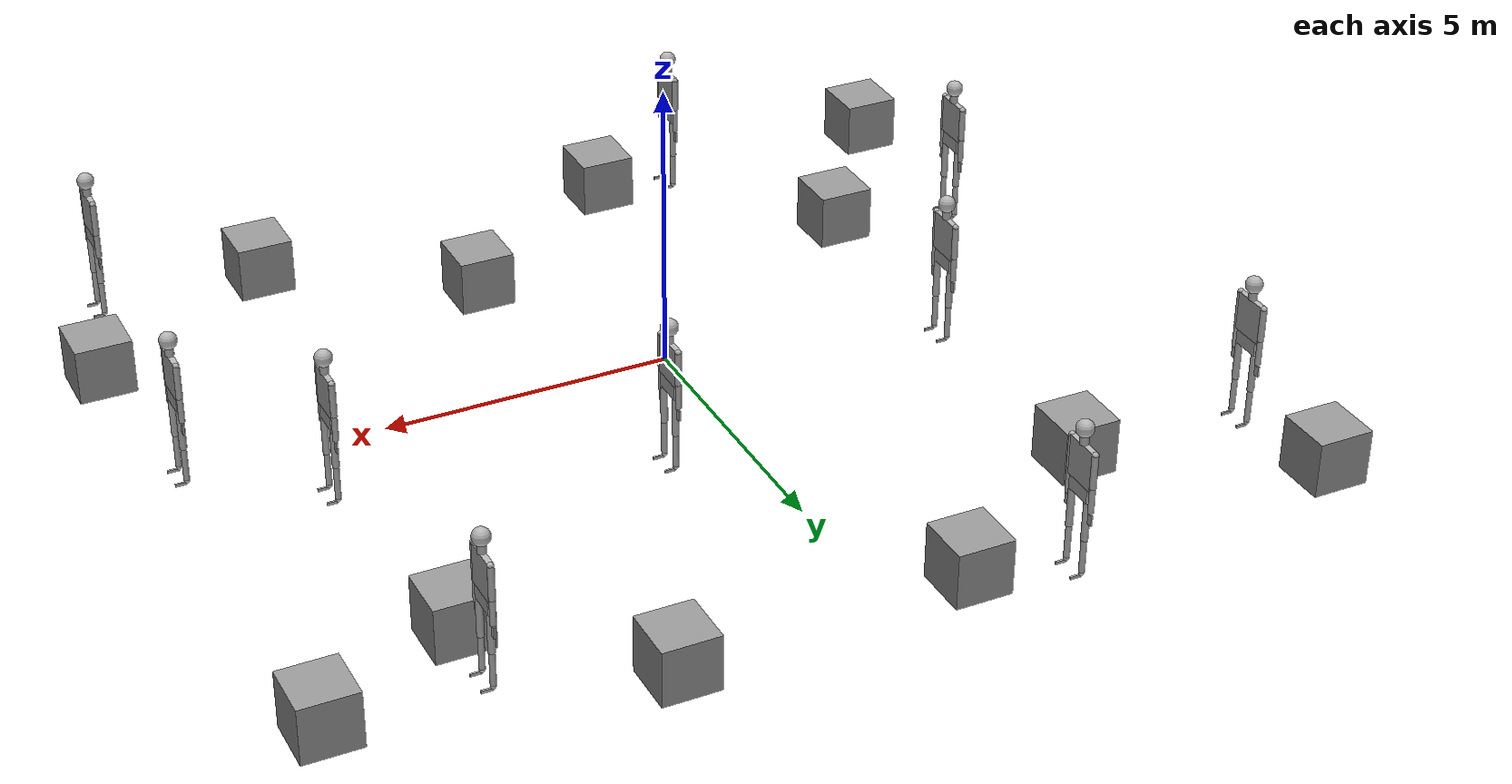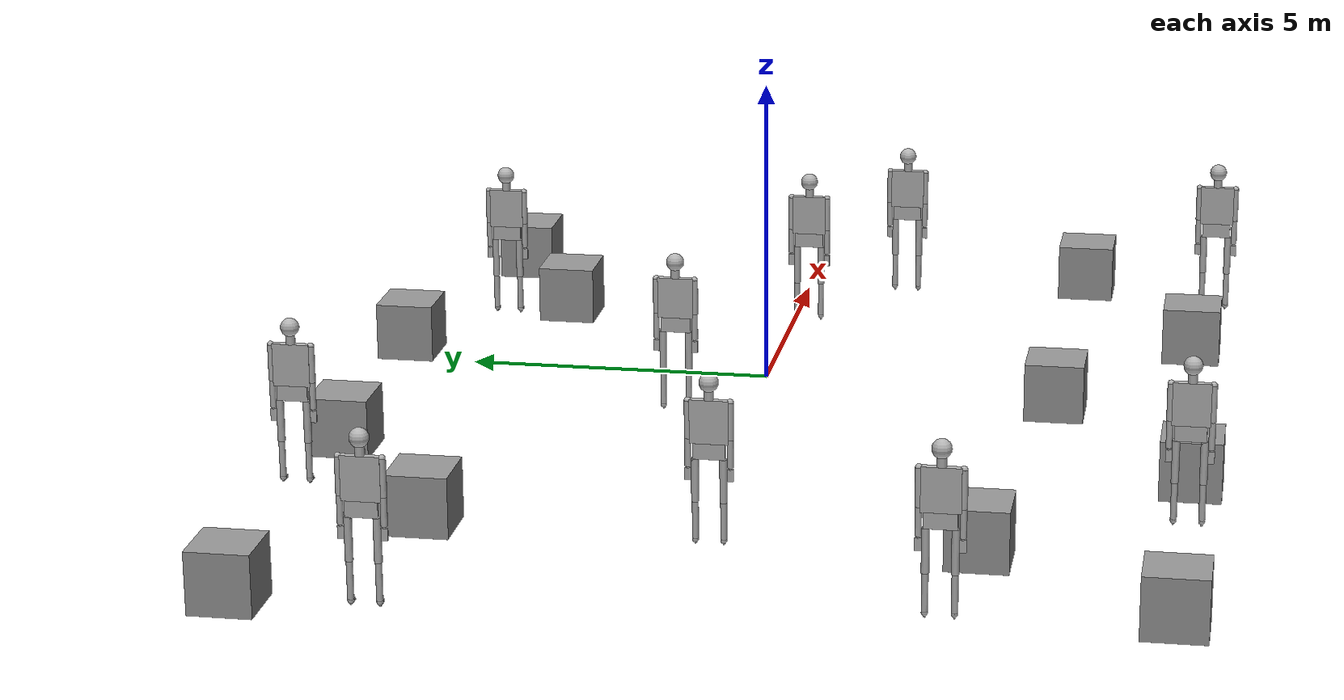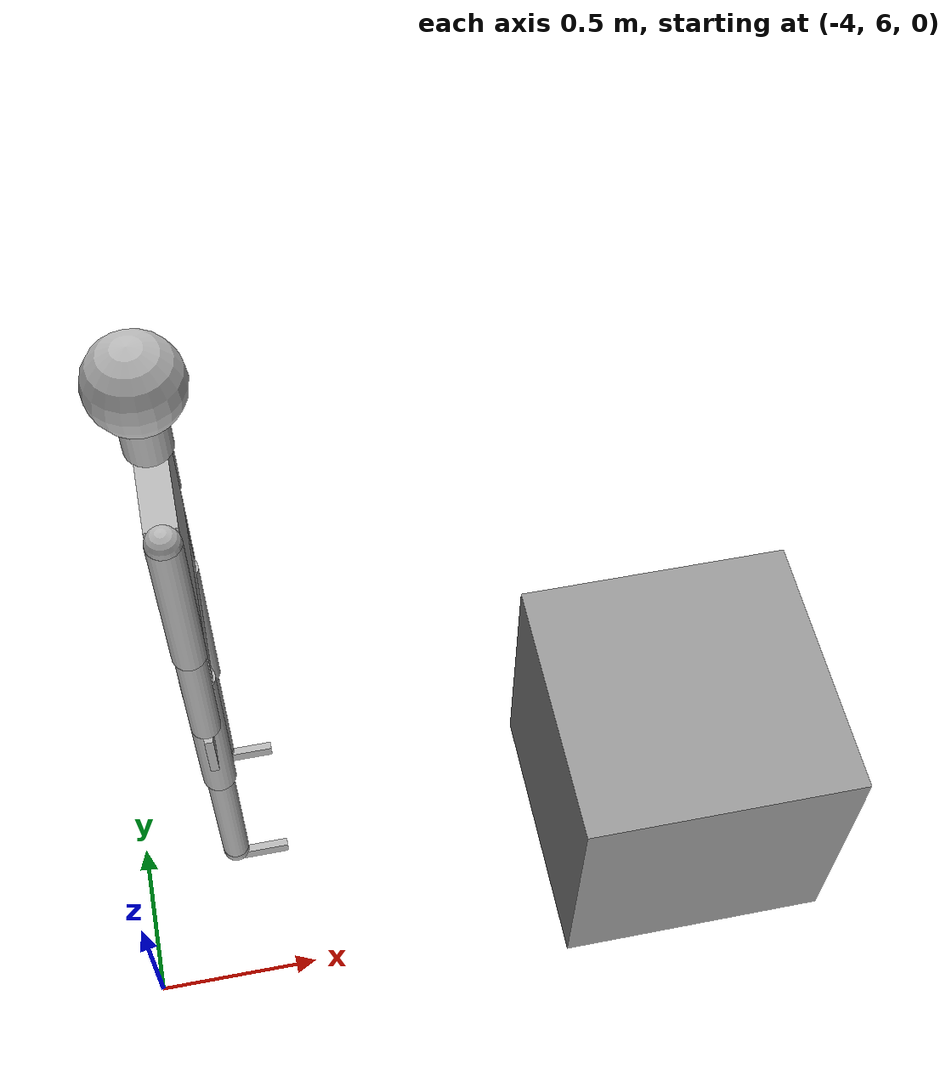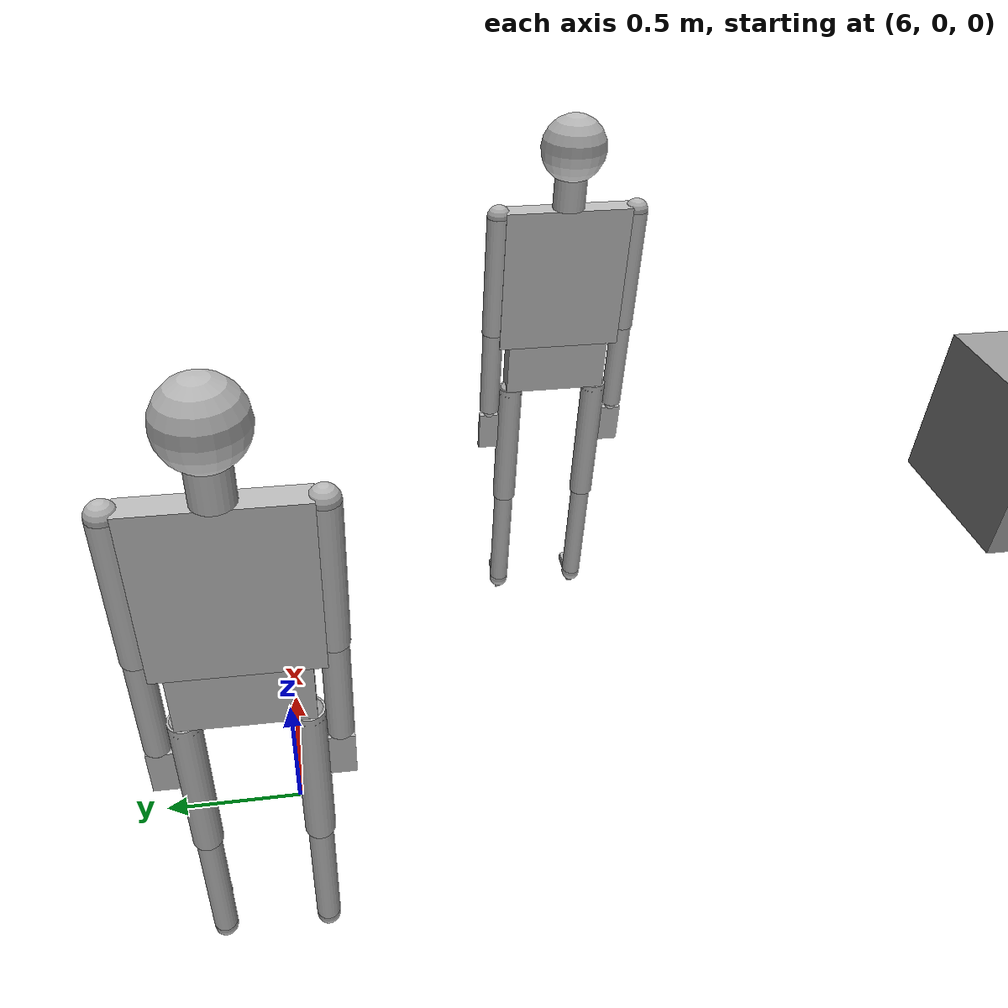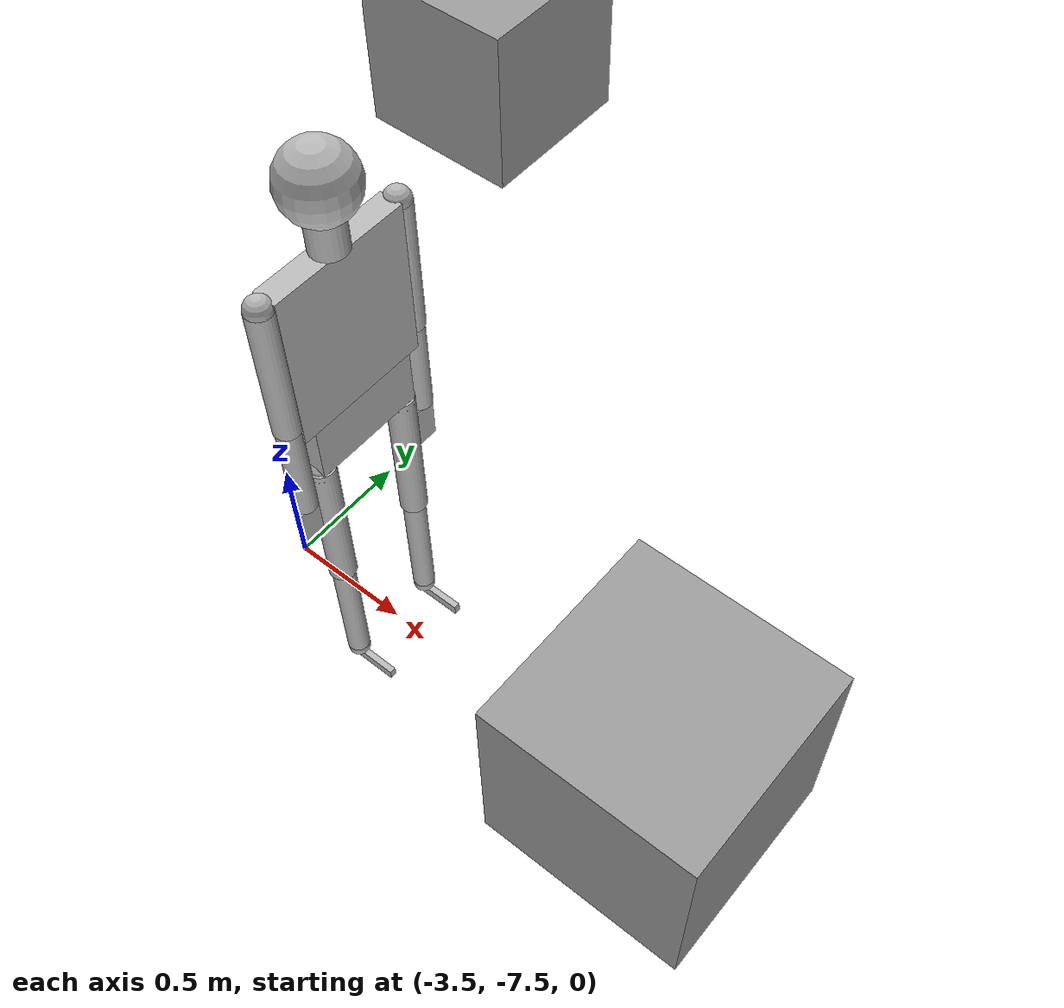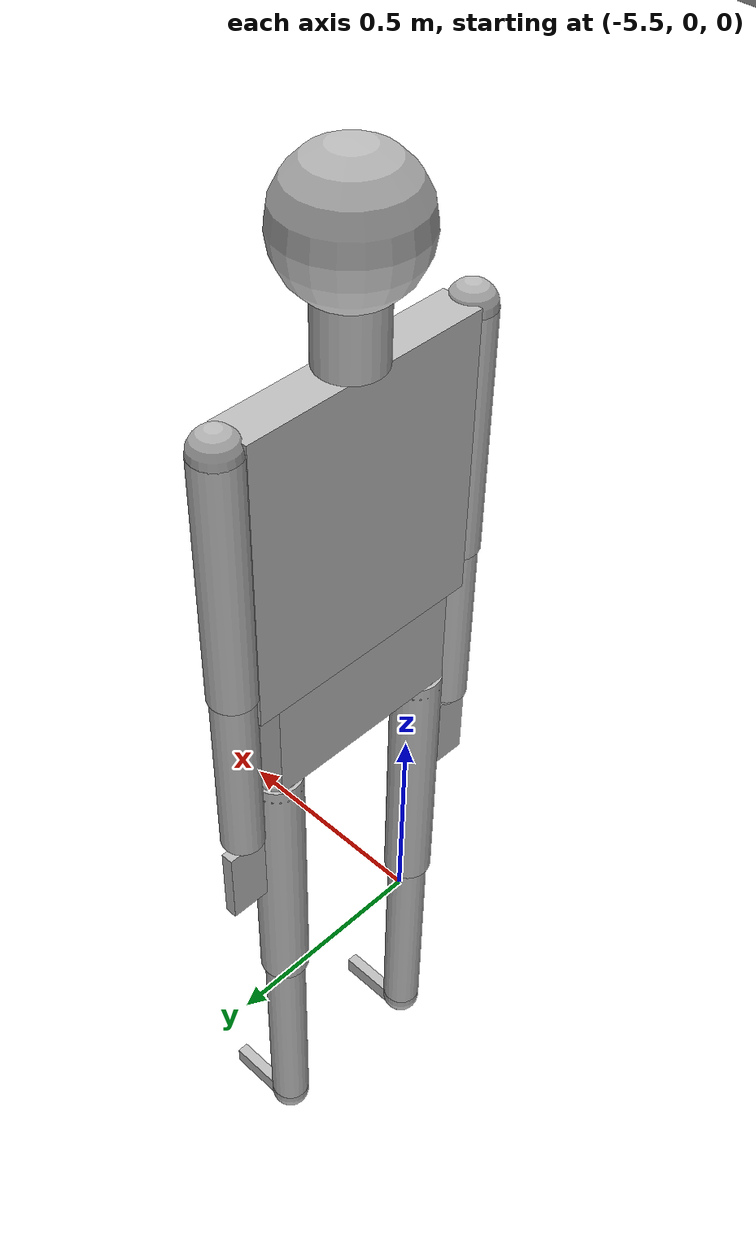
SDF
<?xml version='1.0'?>
<sdf version='1.6'>
  <model name='Hotel_with_Human.world'>
    <link name='link_0'>
      <pose frame=''>8.22428 5.87871 -0.409091 0 -0 0</pose>
      <inertial>
        <mass>1</mass>
        <inertia>
          <ixx>0.166667</ixx>
          <ixy>0</ixy>
          <ixz>0</ixz>
          <iyy>0.166667</iyy>
          <iyz>0</iyz>
          <izz>0.166667</izz>
        </inertia>
      </inertial>
      <visual name='visual'>
        <pose frame=''>0 0 0 0 -0 0</pose>
        <geometry>
          <box>
            <size>1 1 1</size>
          </box>
        </geometry>
        <material>
          <lighting>1</lighting>
          <script>
            <uri>file://media/materials/scripts/gazebo.material</uri>
            <name>Gazebo/Grey</name>
          </script>
          <shader type='pixel'/>
          <ambient>0.3 0.3 0.3 1</ambient>
          <diffuse>0.7 0.7 0.7 1</diffuse>
          <specular>0.01 0.01 0.01 1</specular>
          <emissive>0 0 0 1</emissive>
        </material>
        <transparency>0</transparency>
        <cast_shadows>1</cast_shadows>
      </visual>
      <collision name='collision'>
        <laser_retro>0</laser_retro>
        <max_contacts>10</max_contacts>
        <pose frame=''>0 0 0 0 -0 0</pose>
        <geometry>
          <box>
            <size>1 1 1</size>
          </box>
        </geometry>
        <surface>
          <friction>
            <ode>
              <mu>1</mu>
              <mu2>1</mu2>
              <fdir1>0 0 0</fdir1>
              <slip1>0</slip1>
              <slip2>0</slip2>
            </ode>
            <torsional>
              <coefficient>1</coefficient>
              <patch_radius>0</patch_radius>
              <surface_radius>0</surface_radius>
              <use_patch_radius>1</use_patch_radius>
              <ode>
                <slip>0</slip>
              </ode>
            </torsional>
          </friction>
          <bounce>
            <restitution_coefficient>0</restitution_coefficient>
            <threshold>1e+06</threshold>
          </bounce>
          <contact>
            <collide_without_contact>0</collide_without_contact>
            <collide_without_contact_bitmask>1</collide_without_contact_bitmask>
            <collide_bitmask>1</collide_bitmask>
            <ode>
              <soft_cfm>0</soft_cfm>
              <soft_erp>0.2</soft_erp>
              <kp>1e+13</kp>
              <kd>1</kd>
              <max_vel>0.01</max_vel>
              <min_depth>0</min_depth>
            </ode>
            <bullet>
              <split_impulse>1</split_impulse>
              <split_impulse_penetration_threshold>-0.01</split_impulse_penetration_threshold>
              <soft_cfm>0</soft_cfm>
              <soft_erp>0.2</soft_erp>
              <kp>1e+13</kp>
              <kd>1</kd>
            </bullet>
          </contact>
        </surface>
      </collision>
    </link>
    <link name='link_1'>
      <pose frame=''>5.64418 4.5442 -0.409091 0 -0 0</pose>
      <inertial>
        <mass>1</mass>
        <inertia>
          <ixx>0.166667</ixx>
          <ixy>0</ixy>
          <ixz>0</ixz>
          <iyy>0.166667</iyy>
          <iyz>0</iyz>
          <izz>0.166667</izz>
        </inertia>
      </inertial>
      <visual name='visual'>
        <pose frame=''>0 0 0 0 -0 0</pose>
        <geometry>
          <box>
            <size>1 1 1</size>
          </box>
        </geometry>
        <material>
          <lighting>1</lighting>
          <script>
            <uri>file://media/materials/scripts/gazebo.material</uri>
            <name>Gazebo/Grey</name>
          </script>
          <shader type='pixel'/>
          <ambient>0.3 0.3 0.3 1</ambient>
          <diffuse>0.7 0.7 0.7 1</diffuse>
          <specular>0.01 0.01 0.01 1</specular>
          <emissive>0 0 0 1</emissive>
        </material>
        <transparency>0</transparency>
        <cast_shadows>1</cast_shadows>
      </visual>
      <collision name='collision'>
        <laser_retro>0</laser_retro>
        <max_contacts>10</max_contacts>
        <pose frame=''>0 0 0 0 -0 0</pose>
        <geometry>
          <box>
            <size>1 1 1</size>
          </box>
        </geometry>
        <surface>
          <friction>
            <ode>
              <mu>1</mu>
              <mu2>1</mu2>
              <fdir1>0 0 0</fdir1>
              <slip1>0</slip1>
              <slip2>0</slip2>
            </ode>
            <torsional>
              <coefficient>1</coefficient>
              <patch_radius>0</patch_radius>
              <surface_radius>0</surface_radius>
              <use_patch_radius>1</use_patch_radius>
              <ode>
                <slip>0</slip>
              </ode>
            </torsional>
          </friction>
          <bounce>
            <restitution_coefficient>0</restitution_coefficient>
            <threshold>1e+06</threshold>
          </bounce>
          <contact>
            <collide_without_contact>0</collide_without_contact>
            <collide_without_contact_bitmask>1</collide_without_contact_bitmask>
            <collide_bitmask>1</collide_bitmask>
            <ode>
              <soft_cfm>0</soft_cfm>
              <soft_erp>0.2</soft_erp>
              <kp>1e+13</kp>
              <kd>1</kd>
              <max_vel>0.01</max_vel>
              <min_depth>0</min_depth>
            </ode>
            <bullet>
              <split_impulse>1</split_impulse>
              <split_impulse_penetration_threshold>-0.01</split_impulse_penetration_threshold>
              <soft_cfm>0</soft_cfm>
              <soft_erp>0.2</soft_erp>
              <kp>1e+13</kp>
              <kd>1</kd>
            </bullet>
          </contact>
        </surface>
      </collision>
    </link>
    <link name='link_10'>
      <pose frame=''>-5.4177 -4.11551 -0.409091 0 -0 0</pose>
      <inertial>
        <mass>1</mass>
        <inertia>
          <ixx>0.166667</ixx>
          <ixy>0</ixy>
          <ixz>0</ixz>
          <iyy>0.166667</iyy>
          <iyz>0</iyz>
          <izz>0.166667</izz>
        </inertia>
      </inertial>
      <visual name='visual'>
        <pose frame=''>0 0 0 0 -0 0</pose>
        <geometry>
          <box>
            <size>1 1 1</size>
          </box>
        </geometry>
        <material>
          <lighting>1</lighting>
          <script>
            <uri>file://media/materials/scripts/gazebo.material</uri>
            <name>Gazebo/Grey</name>
          </script>
          <shader type='pixel'/>
          <ambient>0.3 0.3 0.3 1</ambient>
          <diffuse>0.7 0.7 0.7 1</diffuse>
          <specular>0.01 0.01 0.01 1</specular>
          <emissive>0 0 0 1</emissive>
        </material>
        <transparency>0</transparency>
        <cast_shadows>1</cast_shadows>
      </visual>
      <collision name='collision'>
        <laser_retro>0</laser_retro>
        <max_contacts>10</max_contacts>
        <pose frame=''>0 0 0 0 -0 0</pose>
        <geometry>
          <box>
            <size>1 1 1</size>
          </box>
        </geometry>
        <surface>
          <friction>
            <ode>
              <mu>1</mu>
              <mu2>1</mu2>
              <fdir1>0 0 0</fdir1>
              <slip1>0</slip1>
              <slip2>0</slip2>
            </ode>
            <torsional>
              <coefficient>1</coefficient>
              <patch_radius>0</patch_radius>
              <surface_radius>0</surface_radius>
              <use_patch_radius>1</use_patch_radius>
              <ode>
                <slip>0</slip>
              </ode>
            </torsional>
          </friction>
          <bounce>
            <restitution_coefficient>0</restitution_coefficient>
            <threshold>1e+06</threshold>
          </bounce>
          <contact>
            <collide_without_contact>0</collide_without_contact>
            <collide_without_contact_bitmask>1</collide_without_contact_bitmask>
            <collide_bitmask>1</collide_bitmask>
            <ode>
              <soft_cfm>0</soft_cfm>
              <soft_erp>0.2</soft_erp>
              <kp>1e+13</kp>
              <kd>1</kd>
              <max_vel>0.01</max_vel>
              <min_depth>0</min_depth>
            </ode>
            <bullet>
              <split_impulse>1</split_impulse>
              <split_impulse_penetration_threshold>-0.01</split_impulse_penetration_threshold>
              <soft_cfm>0</soft_cfm>
              <soft_erp>0.2</soft_erp>
              <kp>1e+13</kp>
              <kd>1</kd>
            </bullet>
          </contact>
        </surface>
      </collision>
    </link>
    <link name='link_11'>
      <pose frame=''>-7.61228 -7.17005 -0.409091 0 -0 0</pose>
      <inertial>
        <mass>1</mass>
        <inertia>
          <ixx>0.166667</ixx>
          <ixy>0</ixy>
          <ixz>0</ixz>
          <iyy>0.166667</iyy>
          <iyz>0</iyz>
          <izz>0.166667</izz>
        </inertia>
      </inertial>
      <visual name='visual'>
        <pose frame=''>0 0 0 0 -0 0</pose>
        <geometry>
          <box>
            <size>1 1 1</size>
          </box>
        </geometry>
        <material>
          <lighting>1</lighting>
          <script>
            <uri>file://media/materials/scripts/gazebo.material</uri>
            <name>Gazebo/Grey</name>
          </script>
          <shader type='pixel'/>
          <ambient>0.3 0.3 0.3 1</ambient>
          <diffuse>0.7 0.7 0.7 1</diffuse>
          <specular>0.01 0.01 0.01 1</specular>
          <emissive>0 0 0 1</emissive>
        </material>
        <transparency>0</transparency>
        <cast_shadows>1</cast_shadows>
      </visual>
      <collision name='collision'>
        <laser_retro>0</laser_retro>
        <max_contacts>10</max_contacts>
        <pose frame=''>0 0 0 0 -0 0</pose>
        <geometry>
          <box>
            <size>1 1 1</size>
          </box>
        </geometry>
        <surface>
          <friction>
            <ode>
              <mu>1</mu>
              <mu2>1</mu2>
              <fdir1>0 0 0</fdir1>
              <slip1>0</slip1>
              <slip2>0</slip2>
            </ode>
            <torsional>
              <coefficient>1</coefficient>
              <patch_radius>0</patch_radius>
              <surface_radius>0</surface_radius>
              <use_patch_radius>1</use_patch_radius>
              <ode>
                <slip>0</slip>
              </ode>
            </torsional>
          </friction>
          <bounce>
            <restitution_coefficient>0</restitution_coefficient>
            <threshold>1e+06</threshold>
          </bounce>
          <contact>
            <collide_without_contact>0</collide_without_contact>
            <collide_without_contact_bitmask>1</collide_without_contact_bitmask>
            <collide_bitmask>1</collide_bitmask>
            <ode>
              <soft_cfm>0</soft_cfm>
              <soft_erp>0.2</soft_erp>
              <kp>1e+13</kp>
              <kd>1</kd>
              <max_vel>0.01</max_vel>
              <min_depth>0</min_depth>
            </ode>
            <bullet>
              <split_impulse>1</split_impulse>
              <split_impulse_penetration_threshold>-0.01</split_impulse_penetration_threshold>
              <soft_cfm>0</soft_cfm>
              <soft_erp>0.2</soft_erp>
              <kp>1e+13</kp>
              <kd>1</kd>
            </bullet>
          </contact>
        </surface>
      </collision>
    </link>
    <link name='link_2'>
      <pose frame=''>3.03441 6.91671 -0.409091 0 -0 0</pose>
      <inertial>
        <mass>1</mass>
        <inertia>
          <ixx>0.166667</ixx>
          <ixy>0</ixy>
          <ixz>0</ixz>
          <iyy>0.166667</iyy>
          <iyz>0</iyz>
          <izz>0.166667</izz>
        </inertia>
      </inertial>
      <visual name='visual'>
        <pose frame=''>0 0 0 0 -0 0</pose>
        <geometry>
          <box>
            <size>1 1 1</size>
          </box>
        </geometry>
        <material>
          <lighting>1</lighting>
          <script>
            <uri>file://media/materials/scripts/gazebo.material</uri>
            <name>Gazebo/Grey</name>
          </script>
          <shader type='pixel'/>
          <ambient>0.3 0.3 0.3 1</ambient>
          <diffuse>0.7 0.7 0.7 1</diffuse>
          <specular>0.01 0.01 0.01 1</specular>
          <emissive>0 0 0 1</emissive>
        </material>
        <transparency>0</transparency>
        <cast_shadows>1</cast_shadows>
      </visual>
      <collision name='collision'>
        <laser_retro>0</laser_retro>
        <max_contacts>10</max_contacts>
        <pose frame=''>0 0 0 0 -0 0</pose>
        <geometry>
          <box>
            <size>1 1 1</size>
          </box>
        </geometry>
        <surface>
          <friction>
            <ode>
              <mu>1</mu>
              <mu2>1</mu2>
              <fdir1>0 0 0</fdir1>
              <slip1>0</slip1>
              <slip2>0</slip2>
            </ode>
            <torsional>
              <coefficient>1</coefficient>
              <patch_radius>0</patch_radius>
              <surface_radius>0</surface_radius>
              <use_patch_radius>1</use_patch_radius>
              <ode>
                <slip>0</slip>
              </ode>
            </torsional>
          </friction>
          <bounce>
            <restitution_coefficient>0</restitution_coefficient>
            <threshold>1e+06</threshold>
          </bounce>
          <contact>
            <collide_without_contact>0</collide_without_contact>
            <collide_without_contact_bitmask>1</collide_without_contact_bitmask>
            <collide_bitmask>1</collide_bitmask>
            <ode>
              <soft_cfm>0</soft_cfm>
              <soft_erp>0.2</soft_erp>
              <kp>1e+13</kp>
              <kd>1</kd>
              <max_vel>0.01</max_vel>
              <min_depth>0</min_depth>
            </ode>
            <bullet>
              <split_impulse>1</split_impulse>
              <split_impulse_penetration_threshold>-0.01</split_impulse_penetration_threshold>
              <soft_cfm>0</soft_cfm>
              <soft_erp>0.2</soft_erp>
              <kp>1e+13</kp>
              <kd>1</kd>
            </bullet>
          </contact>
        </surface>
      </collision>
    </link>
    <link name='link_3'>
      <pose frame=''>8.46155 -4.79765 -0.409091 0 -0 0</pose>
      <inertial>
        <mass>1</mass>
        <inertia>
          <ixx>0.166667</ixx>
          <ixy>0</ixy>
          <ixz>0</ixz>
          <iyy>0.166667</iyy>
          <iyz>0</iyz>
          <izz>0.166667</izz>
        </inertia>
      </inertial>
      <visual name='visual'>
        <pose frame=''>0 0 0 0 -0 0</pose>
        <geometry>
          <box>
            <size>1 1 1</size>
          </box>
        </geometry>
        <material>
          <lighting>1</lighting>
          <script>
            <uri>file://media/materials/scripts/gazebo.material</uri>
            <name>Gazebo/Grey</name>
          </script>
          <shader type='pixel'/>
          <ambient>0.3 0.3 0.3 1</ambient>
          <diffuse>0.7 0.7 0.7 1</diffuse>
          <specular>0.01 0.01 0.01 1</specular>
          <emissive>0 0 0 1</emissive>
        </material>
        <transparency>0</transparency>
        <cast_shadows>1</cast_shadows>
      </visual>
      <collision name='collision'>
        <laser_retro>0</laser_retro>
        <max_contacts>10</max_contacts>
        <pose frame=''>0 0 0 0 -0 0</pose>
        <geometry>
          <box>
            <size>1 1 1</size>
          </box>
        </geometry>
        <surface>
          <friction>
            <ode>
              <mu>1</mu>
              <mu2>1</mu2>
              <fdir1>0 0 0</fdir1>
              <slip1>0</slip1>
              <slip2>0</slip2>
            </ode>
            <torsional>
              <coefficient>1</coefficient>
              <patch_radius>0</patch_radius>
              <surface_radius>0</surface_radius>
              <use_patch_radius>1</use_patch_radius>
              <ode>
                <slip>0</slip>
              </ode>
            </torsional>
          </friction>
          <bounce>
            <restitution_coefficient>0</restitution_coefficient>
            <threshold>1e+06</threshold>
          </bounce>
          <contact>
            <collide_without_contact>0</collide_without_contact>
            <collide_without_contact_bitmask>1</collide_without_contact_bitmask>
            <collide_bitmask>1</collide_bitmask>
            <ode>
              <soft_cfm>0</soft_cfm>
              <soft_erp>0.2</soft_erp>
              <kp>1e+13</kp>
              <kd>1</kd>
              <max_vel>0.01</max_vel>
              <min_depth>0</min_depth>
            </ode>
            <bullet>
              <split_impulse>1</split_impulse>
              <split_impulse_penetration_threshold>-0.01</split_impulse_penetration_threshold>
              <soft_cfm>0</soft_cfm>
              <soft_erp>0.2</soft_erp>
              <kp>1e+13</kp>
              <kd>1</kd>
            </bullet>
          </contact>
        </surface>
      </collision>
    </link>
    <link name='link_4'>
      <pose frame=''>4.9028 -6.90321 -0.409091 0 -0 0</pose>
      <inertial>
        <mass>1</mass>
        <inertia>
          <ixx>0.166667</ixx>
          <ixy>0</ixy>
          <ixz>0</ixz>
          <iyy>0.166667</iyy>
          <iyz>0</iyz>
          <izz>0.166667</izz>
        </inertia>
      </inertial>
      <visual name='visual'>
        <pose frame=''>0 0 0 0 -0 0</pose>
        <geometry>
          <box>
            <size>1 1 1</size>
          </box>
        </geometry>
        <material>
          <lighting>1</lighting>
          <script>
            <uri>file://media/materials/scripts/gazebo.material</uri>
            <name>Gazebo/Grey</name>
          </script>
          <shader type='pixel'/>
          <ambient>0.3 0.3 0.3 1</ambient>
          <diffuse>0.7 0.7 0.7 1</diffuse>
          <specular>0.01 0.01 0.01 1</specular>
          <emissive>0 0 0 1</emissive>
        </material>
        <transparency>0</transparency>
        <cast_shadows>1</cast_shadows>
      </visual>
      <collision name='collision'>
        <laser_retro>0</laser_retro>
        <max_contacts>10</max_contacts>
        <pose frame=''>0 0 0 0 -0 0</pose>
        <geometry>
          <box>
            <size>1 1 1</size>
          </box>
        </geometry>
        <surface>
          <friction>
            <ode>
              <mu>1</mu>
              <mu2>1</mu2>
              <fdir1>0 0 0</fdir1>
              <slip1>0</slip1>
              <slip2>0</slip2>
            </ode>
            <torsional>
              <coefficient>1</coefficient>
              <patch_radius>0</patch_radius>
              <surface_radius>0</surface_radius>
              <use_patch_radius>1</use_patch_radius>
              <ode>
                <slip>0</slip>
              </ode>
            </torsional>
          </friction>
          <bounce>
            <restitution_coefficient>0</restitution_coefficient>
            <threshold>1e+06</threshold>
          </bounce>
          <contact>
            <collide_without_contact>0</collide_without_contact>
            <collide_without_contact_bitmask>1</collide_without_contact_bitmask>
            <collide_bitmask>1</collide_bitmask>
            <ode>
              <soft_cfm>0</soft_cfm>
              <soft_erp>0.2</soft_erp>
              <kp>1e+13</kp>
              <kd>1</kd>
              <max_vel>0.01</max_vel>
              <min_depth>0</min_depth>
            </ode>
            <bullet>
              <split_impulse>1</split_impulse>
              <split_impulse_penetration_threshold>-0.01</split_impulse_penetration_threshold>
              <soft_cfm>0</soft_cfm>
              <soft_erp>0.2</soft_erp>
              <kp>1e+13</kp>
              <kd>1</kd>
            </bullet>
          </contact>
        </surface>
      </collision>
    </link>
    <link name='link_5'>
      <pose frame=''>1.49221 -4.7384 -0.409091 0 -0 0</pose>
      <inertial>
        <mass>1</mass>
        <inertia>
          <ixx>0.166667</ixx>
          <ixy>0</ixy>
          <ixz>0</ixz>
          <iyy>0.166667</iyy>
          <iyz>0</iyz>
          <izz>0.166667</izz>
        </inertia>
      </inertial>
      <visual name='visual'>
        <pose frame=''>0 0 0 0 -0 0</pose>
        <geometry>
          <box>
            <size>1 1 1</size>
          </box>
        </geometry>
        <material>
          <lighting>1</lighting>
          <script>
            <uri>file://media/materials/scripts/gazebo.material</uri>
            <name>Gazebo/Grey</name>
          </script>
          <shader type='pixel'/>
          <ambient>0.3 0.3 0.3 1</ambient>
          <diffuse>0.7 0.7 0.7 1</diffuse>
          <specular>0.01 0.01 0.01 1</specular>
          <emissive>0 0 0 1</emissive>
        </material>
        <transparency>0</transparency>
        <cast_shadows>1</cast_shadows>
      </visual>
      <collision name='collision'>
        <laser_retro>0</laser_retro>
        <max_contacts>10</max_contacts>
        <pose frame=''>0 0 0 0 -0 0</pose>
        <geometry>
          <box>
            <size>1 1 1</size>
          </box>
        </geometry>
        <surface>
          <friction>
            <ode>
              <mu>1</mu>
              <mu2>1</mu2>
              <fdir1>0 0 0</fdir1>
              <slip1>0</slip1>
              <slip2>0</slip2>
            </ode>
            <torsional>
              <coefficient>1</coefficient>
              <patch_radius>0</patch_radius>
              <surface_radius>0</surface_radius>
              <use_patch_radius>1</use_patch_radius>
              <ode>
                <slip>0</slip>
              </ode>
            </torsional>
          </friction>
          <bounce>
            <restitution_coefficient>0</restitution_coefficient>
            <threshold>1e+06</threshold>
          </bounce>
          <contact>
            <collide_without_contact>0</collide_without_contact>
            <collide_without_contact_bitmask>1</collide_without_contact_bitmask>
            <collide_bitmask>1</collide_bitmask>
            <ode>
              <soft_cfm>0</soft_cfm>
              <soft_erp>0.2</soft_erp>
              <kp>1e+13</kp>
              <kd>1</kd>
              <max_vel>0.01</max_vel>
              <min_depth>0</min_depth>
            </ode>
            <bullet>
              <split_impulse>1</split_impulse>
              <split_impulse_penetration_threshold>-0.01</split_impulse_penetration_threshold>
              <soft_cfm>0</soft_cfm>
              <soft_erp>0.2</soft_erp>
              <kp>1e+13</kp>
              <kd>1</kd>
            </bullet>
          </contact>
        </surface>
      </collision>
    </link>
    <link name='link_6'>
      <pose frame=''>-2.03688 6.70911 -0.409091 0 -0 0</pose>
      <inertial>
        <mass>1</mass>
        <inertia>
          <ixx>0.166667</ixx>
          <ixy>0</ixy>
          <ixz>0</ixz>
          <iyy>0.166667</iyy>
          <iyz>0</iyz>
          <izz>0.166667</izz>
        </inertia>
      </inertial>
      <visual name='visual'>
        <pose frame=''>0 0 0 0 -0 0</pose>
        <geometry>
          <box>
            <size>1 1 1</size>
          </box>
        </geometry>
        <material>
          <lighting>1</lighting>
          <script>
            <uri>file://media/materials/scripts/gazebo.material</uri>
            <name>Gazebo/Grey</name>
          </script>
          <shader type='pixel'/>
          <ambient>0.3 0.3 0.3 1</ambient>
          <diffuse>0.7 0.7 0.7 1</diffuse>
          <specular>0.01 0.01 0.01 1</specular>
          <emissive>0 0 0 1</emissive>
        </material>
        <transparency>0</transparency>
        <cast_shadows>1</cast_shadows>
      </visual>
      <collision name='collision'>
        <laser_retro>0</laser_retro>
        <max_contacts>10</max_contacts>
        <pose frame=''>0 0 0 0 -0 0</pose>
        <geometry>
          <box>
            <size>1 1 1</size>
          </box>
        </geometry>
        <surface>
          <friction>
            <ode>
              <mu>1</mu>
              <mu2>1</mu2>
              <fdir1>0 0 0</fdir1>
              <slip1>0</slip1>
              <slip2>0</slip2>
            </ode>
            <torsional>
              <coefficient>1</coefficient>
              <patch_radius>0</patch_radius>
              <surface_radius>0</surface_radius>
              <use_patch_radius>1</use_patch_radius>
              <ode>
                <slip>0</slip>
              </ode>
            </torsional>
          </friction>
          <bounce>
            <restitution_coefficient>0</restitution_coefficient>
            <threshold>1e+06</threshold>
          </bounce>
          <contact>
            <collide_without_contact>0</collide_without_contact>
            <collide_without_contact_bitmask>1</collide_without_contact_bitmask>
            <collide_bitmask>1</collide_bitmask>
            <ode>
              <soft_cfm>0</soft_cfm>
              <soft_erp>0.2</soft_erp>
              <kp>1e+13</kp>
              <kd>1</kd>
              <max_vel>0.01</max_vel>
              <min_depth>0</min_depth>
            </ode>
            <bullet>
              <split_impulse>1</split_impulse>
              <split_impulse_penetration_threshold>-0.01</split_impulse_penetration_threshold>
              <soft_cfm>0</soft_cfm>
              <soft_erp>0.2</soft_erp>
              <kp>1e+13</kp>
              <kd>1</kd>
            </bullet>
          </contact>
        </surface>
      </collision>
    </link>
    <link name='link_7'>
      <pose frame=''>-5.29911 4.5442 -0.409091 0 -0 0</pose>
      <inertial>
        <mass>1</mass>
        <inertia>
          <ixx>0.166667</ixx>
          <ixy>0</ixy>
          <ixz>0</ixz>
          <iyy>0.166667</iyy>
          <iyz>0</iyz>
          <izz>0.166667</izz>
        </inertia>
      </inertial>
      <visual name='visual'>
        <pose frame=''>0 0 0 0 -0 0</pose>
        <geometry>
          <box>
            <size>1 1 1</size>
          </box>
        </geometry>
        <material>
          <lighting>1</lighting>
          <script>
            <uri>file://media/materials/scripts/gazebo.material</uri>
            <name>Gazebo/Grey</name>
          </script>
          <shader type='pixel'/>
          <ambient>0.3 0.3 0.3 1</ambient>
          <diffuse>0.7 0.7 0.7 1</diffuse>
          <specular>0.01 0.01 0.01 1</specular>
          <emissive>0 0 0 1</emissive>
        </material>
        <transparency>0</transparency>
        <cast_shadows>1</cast_shadows>
      </visual>
      <collision name='collision'>
        <laser_retro>0</laser_retro>
        <max_contacts>10</max_contacts>
        <pose frame=''>0 0 0 0 -0 0</pose>
        <geometry>
          <box>
            <size>1 1 1</size>
          </box>
        </geometry>
        <surface>
          <friction>
            <ode>
              <mu>1</mu>
              <mu2>1</mu2>
              <fdir1>0 0 0</fdir1>
              <slip1>0</slip1>
              <slip2>0</slip2>
            </ode>
            <torsional>
              <coefficient>1</coefficient>
              <patch_radius>0</patch_radius>
              <surface_radius>0</surface_radius>
              <use_patch_radius>1</use_patch_radius>
              <ode>
                <slip>0</slip>
              </ode>
            </torsional>
          </friction>
          <bounce>
            <restitution_coefficient>0</restitution_coefficient>
            <threshold>1e+06</threshold>
          </bounce>
          <contact>
            <collide_without_contact>0</collide_without_contact>
            <collide_without_contact_bitmask>1</collide_without_contact_bitmask>
            <collide_bitmask>1</collide_bitmask>
            <ode>
              <soft_cfm>0</soft_cfm>
              <soft_erp>0.2</soft_erp>
              <kp>1e+13</kp>
              <kd>1</kd>
              <max_vel>0.01</max_vel>
              <min_depth>0</min_depth>
            </ode>
            <bullet>
              <split_impulse>1</split_impulse>
              <split_impulse_penetration_threshold>-0.01</split_impulse_penetration_threshold>
              <soft_cfm>0</soft_cfm>
              <soft_erp>0.2</soft_erp>
              <kp>1e+13</kp>
              <kd>1</kd>
            </bullet>
          </contact>
        </surface>
      </collision>
    </link>
    <link name='link_8'>
      <pose frame=''>-8.79843 6.59042 -0.409091 0 -0 0</pose>
      <inertial>
        <mass>1</mass>
        <inertia>
          <ixx>0.166667</ixx>
          <ixy>0</ixy>
          <ixz>0</ixz>
          <iyy>0.166667</iyy>
          <iyz>0</iyz>
          <izz>0.166667</izz>
        </inertia>
      </inertial>
      <visual name='visual'>
        <pose frame=''>0 0 0 0 -0 0</pose>
        <geometry>
          <box>
            <size>1 1 1</size>
          </box>
        </geometry>
        <material>
          <lighting>1</lighting>
          <script>
            <uri>file://media/materials/scripts/gazebo.material</uri>
            <name>Gazebo/Grey</name>
          </script>
          <shader type='pixel'/>
          <ambient>0.3 0.3 0.3 1</ambient>
          <diffuse>0.7 0.7 0.7 1</diffuse>
          <specular>0.01 0.01 0.01 1</specular>
          <emissive>0 0 0 1</emissive>
        </material>
        <transparency>0</transparency>
        <cast_shadows>1</cast_shadows>
      </visual>
      <collision name='collision'>
        <laser_retro>0</laser_retro>
        <max_contacts>10</max_contacts>
        <pose frame=''>0 0 0 0 -0 0</pose>
        <geometry>
          <box>
            <size>1 1 1</size>
          </box>
        </geometry>
        <surface>
          <friction>
            <ode>
              <mu>1</mu>
              <mu2>1</mu2>
              <fdir1>0 0 0</fdir1>
              <slip1>0</slip1>
              <slip2>0</slip2>
            </ode>
            <torsional>
              <coefficient>1</coefficient>
              <patch_radius>0</patch_radius>
              <surface_radius>0</surface_radius>
              <use_patch_radius>1</use_patch_radius>
              <ode>
                <slip>0</slip>
              </ode>
            </torsional>
          </friction>
          <bounce>
            <restitution_coefficient>0</restitution_coefficient>
            <threshold>1e+06</threshold>
          </bounce>
          <contact>
            <collide_without_contact>0</collide_without_contact>
            <collide_without_contact_bitmask>1</collide_without_contact_bitmask>
            <collide_bitmask>1</collide_bitmask>
            <ode>
              <soft_cfm>0</soft_cfm>
              <soft_erp>0.2</soft_erp>
              <kp>1e+13</kp>
              <kd>1</kd>
              <max_vel>0.01</max_vel>
              <min_depth>0</min_depth>
            </ode>
            <bullet>
              <split_impulse>1</split_impulse>
              <split_impulse_penetration_threshold>-0.01</split_impulse_penetration_threshold>
              <soft_cfm>0</soft_cfm>
              <soft_erp>0.2</soft_erp>
              <kp>1e+13</kp>
              <kd>1</kd>
            </bullet>
          </contact>
        </surface>
      </collision>
    </link>
    <link name='link_9'>
      <pose frame=''>-1.94786 -7.17005 -0.409091 0 -0 0</pose>
      <inertial>
        <mass>1</mass>
        <inertia>
          <ixx>0.166667</ixx>
          <ixy>0</ixy>
          <ixz>0</ixz>
          <iyy>0.166667</iyy>
          <iyz>0</iyz>
          <izz>0.166667</izz>
        </inertia>
      </inertial>
      <visual name='visual'>
        <pose frame=''>0 0 0 0 -0 0</pose>
        <geometry>
          <box>
            <size>1 1 1</size>
          </box>
        </geometry>
        <material>
          <lighting>1</lighting>
          <script>
            <uri>file://media/materials/scripts/gazebo.material</uri>
            <name>Gazebo/Grey</name>
          </script>
          <shader type='pixel'/>
          <ambient>0.3 0.3 0.3 1</ambient>
          <diffuse>0.7 0.7 0.7 1</diffuse>
          <specular>0.01 0.01 0.01 1</specular>
          <emissive>0 0 0 1</emissive>
        </material>
        <transparency>0</transparency>
        <cast_shadows>1</cast_shadows>
      </visual>
      <collision name='collision'>
        <laser_retro>0</laser_retro>
        <max_contacts>10</max_contacts>
        <pose frame=''>0 0 0 0 -0 0</pose>
        <geometry>
          <box>
            <size>1 1 1</size>
          </box>
        </geometry>
        <surface>
          <friction>
            <ode>
              <mu>1</mu>
              <mu2>1</mu2>
              <fdir1>0 0 0</fdir1>
              <slip1>0</slip1>
              <slip2>0</slip2>
            </ode>
            <torsional>
              <coefficient>1</coefficient>
              <patch_radius>0</patch_radius>
              <surface_radius>0</surface_radius>
              <use_patch_radius>1</use_patch_radius>
              <ode>
                <slip>0</slip>
              </ode>
            </torsional>
          </friction>
          <bounce>
            <restitution_coefficient>0</restitution_coefficient>
            <threshold>1e+06</threshold>
          </bounce>
          <contact>
            <collide_without_contact>0</collide_without_contact>
            <collide_without_contact_bitmask>1</collide_without_contact_bitmask>
            <collide_bitmask>1</collide_bitmask>
            <ode>
              <soft_cfm>0</soft_cfm>
              <soft_erp>0.2</soft_erp>
              <kp>1e+13</kp>
              <kd>1</kd>
              <max_vel>0.01</max_vel>
              <min_depth>0</min_depth>
            </ode>
            <bullet>
              <split_impulse>1</split_impulse>
              <split_impulse_penetration_threshold>-0.01</split_impulse_penetration_threshold>
              <soft_cfm>0</soft_cfm>
              <soft_erp>0.2</soft_erp>
              <kp>1e+13</kp>
              <kd>1</kd>
            </bullet>
          </contact>
        </surface>
      </collision>
    </link>
    <model name='ragdoll'>
      <pose frame=''>5.58494 5.73045 0.490909 0 -0 0</pose>
      <link name='hip'>
        <inertial>
          <inertia>
            <ixx>0.1</ixx>
            <ixy>0</ixy>
            <ixz>0</ixz>
            <iyy>0.1</iyy>
            <iyz>0</iyz>
            <izz>0.1</izz>
          </inertia>
          <mass>10</mass>
        </inertial>
        <collision name='hip_geom'>
          <pose frame=''>0 0 0.125 0 -0 0</pose>
          <geometry>
            <box>
              <size>0.1 0.5 0.25</size>
            </box>
          </geometry>
          <surface>
            <friction>
              <ode>
                <mu>-1</mu>
                <mu2>-1</mu2>
                <fdir1>0 0 0</fdir1>
                <slip1>0</slip1>
                <slip2>0</slip2>
              </ode>
            </friction>
            <bounce>
              <restitution_coefficient>0</restitution_coefficient>
              <threshold>100000</threshold>
            </bounce>
            <contact>
              <ode>
                <soft_cfm>0</soft_cfm>
                <soft_erp>0.2</soft_erp>
                <kp>1e+12</kp>
                <kd>1</kd>
                <max_vel>0</max_vel>
                <min_depth>0.001</min_depth>
              </ode>
            </contact>
          </surface>
          <laser_retro>0</laser_retro>
        </collision>
        <visual name='hip_geom_visual'>
          <pose frame=''>0 0 0.125 0 -0 0</pose>
          <geometry>
            <box>
              <size>0.1 0.5 0.25</size>
            </box>
          </geometry>
          <cast_shadows>1</cast_shadows>
          <laser_retro>0</laser_retro>
          <transparency>0</transparency>
        </visual>
        <gravity>0</gravity>
        <self_collide>0</self_collide>
        <kinematic>0</kinematic>
      </link>
      <link name='l_thigh_pan'>
        <pose frame=''>0 0.22 0 0 -0 0</pose>
        <inertial>
          <inertia>
            <ixx>0.01</ixx>
            <ixy>0</ixy>
            <ixz>0</ixz>
            <iyy>0.01</iyy>
            <iyz>0</iyz>
            <izz>0.01</izz>
          </inertia>
          <mass>1</mass>
        </inertial>
        <collision name='l_thigh_pan_geom'>
          <pose frame=''>0 0 -0.03 0 -0 0</pose>
          <geometry>
            <sphere>
              <radius>0.06</radius>
            </sphere>
          </geometry>
          <surface>
            <friction>
              <ode>
                <mu>-1</mu>
                <mu2>-1</mu2>
                <fdir1>0 0 0</fdir1>
                <slip1>0</slip1>
                <slip2>0</slip2>
              </ode>
            </friction>
            <bounce>
              <restitution_coefficient>0</restitution_coefficient>
              <threshold>100000</threshold>
            </bounce>
            <contact>
              <ode>
                <soft_cfm>0</soft_cfm>
                <soft_erp>0.2</soft_erp>
                <kp>1e+12</kp>
                <kd>1</kd>
                <max_vel>0</max_vel>
                <min_depth>0.001</min_depth>
              </ode>
            </contact>
          </surface>
          <laser_retro>0</laser_retro>
        </collision>
        <visual name='l_thigh_pan_geom_visual'>
          <pose frame=''>0 0 -0.03 0 -0 0</pose>
          <geometry>
            <sphere>
              <radius>0.06</radius>
            </sphere>
          </geometry>
          <cast_shadows>1</cast_shadows>
          <laser_retro>0</laser_retro>
          <transparency>0</transparency>
        </visual>
        <gravity>0</gravity>
        <self_collide>0</self_collide>
        <kinematic>0</kinematic>
      </link>
      <link name='l_thigh_lift'>
        <pose frame=''>0 0.22 0 0 -0 0</pose>
        <inertial>
          <inertia>
            <ixx>0.05</ixx>
            <ixy>0</ixy>
            <ixz>0</ixz>
            <iyy>0.05</iyy>
            <iyz>0</iyz>
            <izz>0.05</izz>
          </inertia>
          <mass>5</mass>
        </inertial>
        <collision name='l_thigh_lift_geom'>
          <pose frame=''>0 0 -0.35 0 -0 0</pose>
          <geometry>
            <cylinder>
              <radius>0.06</radius>
              <length>0.7</length>
            </cylinder>
          </geometry>
          <surface>
            <friction>
              <ode>
                <mu>-1</mu>
                <mu2>-1</mu2>
                <fdir1>0 0 0</fdir1>
                <slip1>0</slip1>
                <slip2>0</slip2>
              </ode>
            </friction>
            <bounce>
              <restitution_coefficient>0</restitution_coefficient>
              <threshold>100000</threshold>
            </bounce>
            <contact>
              <ode>
                <soft_cfm>0</soft_cfm>
                <soft_erp>0.2</soft_erp>
                <kp>1e+12</kp>
                <kd>1</kd>
                <max_vel>0</max_vel>
                <min_depth>0.001</min_depth>
              </ode>
            </contact>
          </surface>
          <laser_retro>0</laser_retro>
        </collision>
        <visual name='l_thigh_lift_geom_visual'>
          <pose frame=''>0 0 -0.35 0 -0 0</pose>
          <geometry>
            <cylinder>
              <radius>0.06</radius>
              <length>0.7</length>
            </cylinder>
          </geometry>
          <cast_shadows>1</cast_shadows>
          <laser_retro>0</laser_retro>
          <transparency>0</transparency>
        </visual>
        <gravity>0</gravity>
        <self_collide>0</self_collide>
        <kinematic>0</kinematic>
      </link>
      <link name='l_calf'>
        <pose frame=''>0 0.22 -0.7 0 -0 0</pose>
        <inertial>
          <inertia>
            <ixx>0.02</ixx>
            <ixy>0</ixy>
            <ixz>0</ixz>
            <iyy>0.02</iyy>
            <iyz>0</iyz>
            <izz>0.02</izz>
          </inertia>
          <mass>2</mass>
        </inertial>
        <collision name='l_calf_geom'>
          <pose frame=''>0 0 -0.3 0 -0 0</pose>
          <geometry>
            <cylinder>
              <radius>0.05</radius>
              <length>0.6</length>
            </cylinder>
          </geometry>
          <surface>
            <friction>
              <ode>
                <mu>-1</mu>
                <mu2>-1</mu2>
                <fdir1>0 0 0</fdir1>
                <slip1>0</slip1>
                <slip2>0</slip2>
              </ode>
            </friction>
            <bounce>
              <restitution_coefficient>0</restitution_coefficient>
              <threshold>100000</threshold>
            </bounce>
            <contact>
              <ode>
                <soft_cfm>0</soft_cfm>
                <soft_erp>0.2</soft_erp>
                <kp>1e+12</kp>
                <kd>1</kd>
                <max_vel>0</max_vel>
                <min_depth>0.001</min_depth>
              </ode>
            </contact>
          </surface>
          <laser_retro>0</laser_retro>
        </collision>
        <visual name='l_calf_geom_visual'>
          <pose frame=''>0 0 -0.3 0 -0 0</pose>
          <geometry>
            <cylinder>
              <radius>0.05</radius>
              <length>0.6</length>
            </cylinder>
          </geometry>
          <cast_shadows>1</cast_shadows>
          <laser_retro>0</laser_retro>
          <transparency>0</transparency>
        </visual>
        <gravity>0</gravity>
        <self_collide>0</self_collide>
        <kinematic>0</kinematic>
      </link>
      <link name='l_ankle'>
        <pose frame=''>0 0.22 -1.325 0 -0 0</pose>
        <inertial>
          <inertia>
            <ixx>0.01</ixx>
            <ixy>0</ixy>
            <ixz>0</ixz>
            <iyy>0.01</iyy>
            <iyz>0</iyz>
            <izz>0.01</izz>
          </inertia>
          <mass>1</mass>
        </inertial>
        <collision name='l_ankle_geom'>
          <geometry>
            <sphere>
              <radius>0.05</radius>
            </sphere>
          </geometry>
          <surface>
            <friction>
              <ode>
                <mu>-1</mu>
                <mu2>-1</mu2>
                <fdir1>0 0 0</fdir1>
                <slip1>0</slip1>
                <slip2>0</slip2>
              </ode>
            </friction>
            <bounce>
              <restitution_coefficient>0</restitution_coefficient>
              <threshold>100000</threshold>
            </bounce>
            <contact>
              <ode>
                <soft_cfm>0</soft_cfm>
                <soft_erp>0.2</soft_erp>
                <kp>1e+12</kp>
                <kd>1</kd>
                <max_vel>0</max_vel>
                <min_depth>0.001</min_depth>
              </ode>
            </contact>
          </surface>
          <laser_retro>0</laser_retro>
        </collision>
        <visual name='l_ankle_geom_visual'>
          <geometry>
            <sphere>
              <radius>0.05</radius>
            </sphere>
          </geometry>
          <cast_shadows>1</cast_shadows>
          <laser_retro>0</laser_retro>
          <transparency>0</transparency>
        </visual>
        <gravity>0</gravity>
        <self_collide>0</self_collide>
        <kinematic>0</kinematic>
      </link>
      <link name='l_foot'>
        <pose frame=''>0 0.22 -1.35 0 -0 0</pose>
        <inertial>
          <pose frame=''>0.1 0 0 0 -0 0</pose>
          <inertia>
            <ixx>0.01</ixx>
            <ixy>0</ixy>
            <ixz>0</ixz>
            <iyy>0.01</iyy>
            <iyz>0</iyz>
            <izz>0.01</izz>
          </inertia>
          <mass>1</mass>
        </inertial>
        <collision name='l_foot_geom'>
          <pose frame=''>0.1 0 -0.025 0 -0 0</pose>
          <geometry>
            <box>
              <size>0.2 0.03 0.05</size>
            </box>
          </geometry>
          <surface>
            <friction>
              <ode>
                <mu>-1</mu>
                <mu2>-1</mu2>
                <fdir1>0 0 0</fdir1>
                <slip1>0</slip1>
                <slip2>0</slip2>
              </ode>
            </friction>
            <bounce>
              <restitution_coefficient>0</restitution_coefficient>
              <threshold>100000</threshold>
            </bounce>
            <contact>
              <ode>
                <soft_cfm>0</soft_cfm>
                <soft_erp>0.2</soft_erp>
                <kp>1e+12</kp>
                <kd>1</kd>
                <max_vel>0</max_vel>
                <min_depth>0.001</min_depth>
              </ode>
            </contact>
          </surface>
          <laser_retro>0</laser_retro>
        </collision>
        <visual name='l_foot_geom_visual'>
          <pose frame=''>0.1 0 -0.025 0 -0 0</pose>
          <geometry>
            <box>
              <size>0.2 0.03 0.05</size>
            </box>
          </geometry>
          <cast_shadows>1</cast_shadows>
          <laser_retro>0</laser_retro>
          <transparency>0</transparency>
        </visual>
        <gravity>1</gravity>
        <self_collide>0</self_collide>
        <kinematic>0</kinematic>
      </link>
      <link name='r_thigh_pan'>
        <pose frame=''>0 -0.22 0 0 -0 0</pose>
        <inertial>
          <inertia>
            <ixx>0.01</ixx>
            <ixy>0</ixy>
            <ixz>0</ixz>
            <iyy>0.01</iyy>
            <iyz>0</iyz>
            <izz>0.01</izz>
          </inertia>
          <mass>1</mass>
        </inertial>
        <collision name='r_thigh_pan_geom'>
          <pose frame=''>0 0 -0.03 0 -0 0</pose>
          <geometry>
            <sphere>
              <radius>0.06</radius>
            </sphere>
          </geometry>
          <surface>
            <friction>
              <ode>
                <mu>-1</mu>
                <mu2>-1</mu2>
                <fdir1>0 0 0</fdir1>
                <slip1>0</slip1>
                <slip2>0</slip2>
              </ode>
            </friction>
            <bounce>
              <restitution_coefficient>0</restitution_coefficient>
              <threshold>100000</threshold>
            </bounce>
            <contact>
              <ode>
                <soft_cfm>0</soft_cfm>
                <soft_erp>0.2</soft_erp>
                <kp>1e+12</kp>
                <kd>1</kd>
                <max_vel>0</max_vel>
                <min_depth>0.001</min_depth>
              </ode>
            </contact>
          </surface>
          <laser_retro>0</laser_retro>
        </collision>
        <visual name='r_thigh_pan_geom_visual'>
          <pose frame=''>0 0 -0.03 0 -0 0</pose>
          <geometry>
            <sphere>
              <radius>0.06</radius>
            </sphere>
          </geometry>
          <cast_shadows>1</cast_shadows>
          <laser_retro>0</laser_retro>
          <transparency>0</transparency>
        </visual>
        <gravity>0</gravity>
        <self_collide>0</self_collide>
        <kinematic>0</kinematic>
      </link>
      <link name='r_thigh_lift'>
        <pose frame=''>0 -0.22 0 0 -0 0</pose>
        <inertial>
          <inertia>
            <ixx>0.05</ixx>
            <ixy>0</ixy>
            <ixz>0</ixz>
            <iyy>0.05</iyy>
            <iyz>0</iyz>
            <izz>0.05</izz>
          </inertia>
          <mass>5</mass>
        </inertial>
        <collision name='r_thigh_lift_geom'>
          <pose frame=''>0 0 -0.35 0 -0 0</pose>
          <geometry>
            <cylinder>
              <radius>0.06</radius>
              <length>0.7</length>
            </cylinder>
          </geometry>
          <surface>
            <friction>
              <ode>
                <mu>-1</mu>
                <mu2>-1</mu2>
                <fdir1>0 0 0</fdir1>
                <slip1>0</slip1>
                <slip2>0</slip2>
              </ode>
            </friction>
            <bounce>
              <restitution_coefficient>0</restitution_coefficient>
              <threshold>100000</threshold>
            </bounce>
            <contact>
              <ode>
                <soft_cfm>0</soft_cfm>
                <soft_erp>0.2</soft_erp>
                <kp>1e+12</kp>
                <kd>1</kd>
                <max_vel>0</max_vel>
                <min_depth>0.001</min_depth>
              </ode>
            </contact>
          </surface>
          <laser_retro>0</laser_retro>
        </collision>
        <visual name='r_thigh_lift_geom_visual'>
          <pose frame=''>0 0 -0.35 0 -0 0</pose>
          <geometry>
            <cylinder>
              <radius>0.06</radius>
              <length>0.7</length>
            </cylinder>
          </geometry>
          <cast_shadows>1</cast_shadows>
          <laser_retro>0</laser_retro>
          <transparency>0</transparency>
        </visual>
        <gravity>0</gravity>
        <self_collide>0</self_collide>
        <kinematic>0</kinematic>
      </link>
      <link name='r_calf'>
        <pose frame=''>0 -0.22 -0.7 0 -0 0</pose>
        <inertial>
          <inertia>
            <ixx>0.02</ixx>
            <ixy>0</ixy>
            <ixz>0</ixz>
            <iyy>0.02</iyy>
            <iyz>0</iyz>
            <izz>0.02</izz>
          </inertia>
          <mass>2</mass>
        </inertial>
        <collision name='r_calf_geom'>
          <pose frame=''>0 0 -0.3 0 -0 0</pose>
          <geometry>
            <cylinder>
              <radius>0.05</radius>
              <length>0.6</length>
            </cylinder>
          </geometry>
          <surface>
            <friction>
              <ode>
                <mu>-1</mu>
                <mu2>-1</mu2>
                <fdir1>0 0 0</fdir1>
                <slip1>0</slip1>
                <slip2>0</slip2>
              </ode>
            </friction>
            <bounce>
              <restitution_coefficient>0</restitution_coefficient>
              <threshold>100000</threshold>
            </bounce>
            <contact>
              <ode>
                <soft_cfm>0</soft_cfm>
                <soft_erp>0.2</soft_erp>
                <kp>1e+12</kp>
                <kd>1</kd>
                <max_vel>0</max_vel>
                <min_depth>0.001</min_depth>
              </ode>
            </contact>
          </surface>
          <laser_retro>0</laser_retro>
        </collision>
        <visual name='r_calf_geom_visual'>
          <pose frame=''>0 0 -0.3 0 -0 0</pose>
          <geometry>
            <cylinder>
              <radius>0.05</radius>
              <length>0.6</length>
            </cylinder>
          </geometry>
          <cast_shadows>1</cast_shadows>
          <laser_retro>0</laser_retro>
          <transparency>0</transparency>
        </visual>
        <gravity>0</gravity>
        <self_collide>0</self_collide>
        <kinematic>0</kinematic>
      </link>
      <link name='r_ankle'>
        <pose frame=''>0 -0.22 -1.325 0 -0 0</pose>
        <inertial>
          <inertia>
            <ixx>0.01</ixx>
            <ixy>0</ixy>
            <ixz>0</ixz>
            <iyy>0.01</iyy>
            <iyz>0</iyz>
            <izz>0.01</izz>
          </inertia>
          <mass>1</mass>
        </inertial>
        <collision name='r_ankle_geom'>
          <geometry>
            <sphere>
              <radius>0.05</radius>
            </sphere>
          </geometry>
          <surface>
            <friction>
              <ode>
                <mu>-1</mu>
                <mu2>-1</mu2>
                <fdir1>0 0 0</fdir1>
                <slip1>0</slip1>
                <slip2>0</slip2>
              </ode>
            </friction>
            <bounce>
              <restitution_coefficient>0</restitution_coefficient>
              <threshold>100000</threshold>
            </bounce>
            <contact>
              <ode>
                <soft_cfm>0</soft_cfm>
                <soft_erp>0.2</soft_erp>
                <kp>1e+12</kp>
                <kd>1</kd>
                <max_vel>0</max_vel>
                <min_depth>0.001</min_depth>
              </ode>
            </contact>
          </surface>
          <laser_retro>0</laser_retro>
        </collision>
        <visual name='r_ankle_geom_visual'>
          <geometry>
            <sphere>
              <radius>0.05</radius>
            </sphere>
          </geometry>
          <cast_shadows>1</cast_shadows>
          <laser_retro>0</laser_retro>
          <transparency>0</transparency>
        </visual>
        <gravity>0</gravity>
        <self_collide>0</self_collide>
        <kinematic>0</kinematic>
      </link>
      <link name='r_foot'>
        <pose frame=''>0 -0.22 -1.35 0 -0 0</pose>
        <inertial>
          <pose frame=''>0.1 0 0 0 -0 0</pose>
          <inertia>
            <ixx>0.01</ixx>
            <ixy>0</ixy>
            <ixz>0</ixz>
            <iyy>0.01</iyy>
            <iyz>0</iyz>
            <izz>0.01</izz>
          </inertia>
          <mass>1</mass>
        </inertial>
        <collision name='r_foot_geom'>
          <pose frame=''>0.1 0 -0.025 0 -0 0</pose>
          <geometry>
            <box>
              <size>0.2 0.03 0.05</size>
            </box>
          </geometry>
          <surface>
            <friction>
              <ode>
                <mu>-1</mu>
                <mu2>-1</mu2>
                <fdir1>0 0 0</fdir1>
                <slip1>0</slip1>
                <slip2>0</slip2>
              </ode>
            </friction>
            <bounce>
              <restitution_coefficient>0</restitution_coefficient>
              <threshold>100000</threshold>
            </bounce>
            <contact>
              <ode>
                <soft_cfm>0</soft_cfm>
                <soft_erp>0.2</soft_erp>
                <kp>1e+12</kp>
                <kd>1</kd>
                <max_vel>0</max_vel>
                <min_depth>0.001</min_depth>
              </ode>
            </contact>
          </surface>
          <laser_retro>0</laser_retro>
        </collision>
        <visual name='r_foot_geom_visual'>
          <pose frame=''>0.1 0 -0.025 0 -0 0</pose>
          <geometry>
            <box>
              <size>0.2 0.03 0.05</size>
            </box>
          </geometry>
          <cast_shadows>1</cast_shadows>
          <laser_retro>0</laser_retro>
          <transparency>0</transparency>
        </visual>
        <gravity>1</gravity>
        <self_collide>0</self_collide>
        <kinematic>0</kinematic>
      </link>
      <link name='torso'>
        <pose frame=''>0 0 0.25 0 -0 0</pose>
        <inertial>
          <inertia>
            <ixx>0.3</ixx>
            <ixy>0</ixy>
            <ixz>0</ixz>
            <iyy>0.3</iyy>
            <iyz>0</iyz>
            <izz>0.3</izz>
          </inertia>
          <mass>30</mass>
        </inertial>
        <collision name='torso_geom'>
          <pose frame=''>0 0 0.35 0 -0 0</pose>
          <geometry>
            <box>
              <size>0.1 0.6 0.7</size>
            </box>
          </geometry>
          <surface>
            <friction>
              <ode>
                <mu>-1</mu>
                <mu2>-1</mu2>
                <fdir1>0 0 0</fdir1>
                <slip1>0</slip1>
                <slip2>0</slip2>
              </ode>
            </friction>
            <bounce>
              <restitution_coefficient>0</restitution_coefficient>
              <threshold>100000</threshold>
            </bounce>
            <contact>
              <ode>
                <soft_cfm>0</soft_cfm>
                <soft_erp>0.2</soft_erp>
                <kp>1e+12</kp>
                <kd>1</kd>
                <max_vel>0</max_vel>
                <min_depth>0.001</min_depth>
              </ode>
            </contact>
          </surface>
          <laser_retro>0</laser_retro>
        </collision>
        <visual name='torso_geom_visual'>
          <pose frame=''>0 0 0.35 0 -0 0</pose>
          <geometry>
            <box>
              <size>0.1 0.6 0.7</size>
            </box>
          </geometry>
          <cast_shadows>1</cast_shadows>
          <laser_retro>0</laser_retro>
          <transparency>0</transparency>
        </visual>
        <gravity>0</gravity>
        <self_collide>0</self_collide>
        <kinematic>0</kinematic>
      </link>
      <link name='l_shoulder'>
        <pose frame=''>0 0.3275 0.9225 0 -0 0</pose>
        <inertial>
          <inertia>
            <ixx>0.01</ixx>
            <ixy>0</ixy>
            <ixz>0</ixz>
            <iyy>0.01</iyy>
            <iyz>0</iyz>
            <izz>0.01</izz>
          </inertia>
          <mass>1</mass>
        </inertial>
        <collision name='l_shoulder_geom'>
          <geometry>
            <sphere>
              <radius>0.055</radius>
            </sphere>
          </geometry>
          <surface>
            <friction>
              <ode>
                <mu>-1</mu>
                <mu2>-1</mu2>
                <fdir1>0 0 0</fdir1>
                <slip1>0</slip1>
                <slip2>0</slip2>
              </ode>
            </friction>
            <bounce>
              <restitution_coefficient>0</restitution_coefficient>
              <threshold>100000</threshold>
            </bounce>
            <contact>
              <ode>
                <soft_cfm>0</soft_cfm>
                <soft_erp>0.2</soft_erp>
                <kp>1e+12</kp>
                <kd>1</kd>
                <max_vel>0</max_vel>
                <min_depth>0.001</min_depth>
              </ode>
            </contact>
          </surface>
          <laser_retro>0</laser_retro>
        </collision>
        <visual name='l_shoulder_geom_visual'>
          <geometry>
            <sphere>
              <radius>0.055</radius>
            </sphere>
          </geometry>
          <cast_shadows>1</cast_shadows>
          <laser_retro>0</laser_retro>
          <transparency>0</transparency>
        </visual>
        <gravity>0</gravity>
        <self_collide>0</self_collide>
        <kinematic>0</kinematic>
      </link>
      <link name='l_upper_arm'>
        <pose frame=''>0 0.3275 0.9225 0 -0 0</pose>
        <inertial>
          <inertia>
            <ixx>0.02</ixx>
            <ixy>0</ixy>
            <ixz>0</ixz>
            <iyy>0.02</iyy>
            <iyz>0</iyz>
            <izz>0.02</izz>
          </inertia>
          <mass>2</mass>
        </inertial>
        <collision name='l_upper_arm_geom'>
          <pose frame=''>0 0 -0.3 0 -0 0</pose>
          <geometry>
            <cylinder>
              <radius>0.055</radius>
              <length>0.6</length>
            </cylinder>
          </geometry>
          <surface>
            <friction>
              <ode>
                <mu>-1</mu>
                <mu2>-1</mu2>
                <fdir1>0 0 0</fdir1>
                <slip1>0</slip1>
                <slip2>0</slip2>
              </ode>
            </friction>
            <bounce>
              <restitution_coefficient>0</restitution_coefficient>
              <threshold>100000</threshold>
            </bounce>
            <contact>
              <ode>
                <soft_cfm>0</soft_cfm>
                <soft_erp>0.2</soft_erp>
                <kp>1e+12</kp>
                <kd>1</kd>
                <max_vel>0</max_vel>
                <min_depth>0.001</min_depth>
              </ode>
            </contact>
          </surface>
          <laser_retro>0</laser_retro>
        </collision>
        <visual name='l_upper_arm_geom_visual'>
          <pose frame=''>0 0 -0.3 0 -0 0</pose>
          <geometry>
            <cylinder>
              <radius>0.055</radius>
              <length>0.6</length>
            </cylinder>
          </geometry>
          <cast_shadows>1</cast_shadows>
          <laser_retro>0</laser_retro>
          <transparency>0</transparency>
        </visual>
        <gravity>0</gravity>
        <self_collide>0</self_collide>
        <kinematic>0</kinematic>
      </link>
      <link name='l_forearm'>
        <pose frame=''>0 0.3275 0.3225 0 -0 0</pose>
        <inertial>
          <inertia>
            <ixx>0.01</ixx>
            <ixy>0</ixy>
            <ixz>0</ixz>
            <iyy>0.01</iyy>
            <iyz>0</iyz>
            <izz>0.01</izz>
          </inertia>
          <mass>1</mass>
        </inertial>
        <collision name='l_forearm_geom'>
          <pose frame=''>0 0 -0.225 0 -0 0</pose>
          <geometry>
            <cylinder>
              <radius>0.05</radius>
              <length>0.45</length>
            </cylinder>
          </geometry>
          <surface>
            <friction>
              <ode>
                <mu>-1</mu>
                <mu2>-1</mu2>
                <fdir1>0 0 0</fdir1>
                <slip1>0</slip1>
                <slip2>0</slip2>
              </ode>
            </friction>
            <bounce>
              <restitution_coefficient>0</restitution_coefficient>
              <threshold>100000</threshold>
            </bounce>
            <contact>
              <ode>
                <soft_cfm>0</soft_cfm>
                <soft_erp>0.2</soft_erp>
                <kp>1e+12</kp>
                <kd>1</kd>
                <max_vel>0</max_vel>
                <min_depth>0.001</min_depth>
              </ode>
            </contact>
          </surface>
          <laser_retro>0</laser_retro>
        </collision>
        <visual name='l_forearm_geom_visual'>
          <pose frame=''>0 0 -0.225 0 -0 0</pose>
          <geometry>
            <cylinder>
              <radius>0.05</radius>
              <length>0.45</length>
            </cylinder>
          </geometry>
          <cast_shadows>1</cast_shadows>
          <laser_retro>0</laser_retro>
          <transparency>0</transparency>
        </visual>
        <gravity>0</gravity>
        <self_collide>0</self_collide>
        <kinematic>0</kinematic>
      </link>
      <link name='l_wrist'>
        <pose frame=''>0 0.3275 -0.1425 0 -0 0</pose>
        <inertial>
          <inertia>
            <ixx>0.01</ixx>
            <ixy>0</ixy>
            <ixz>0</ixz>
            <iyy>0.01</iyy>
            <iyz>0</iyz>
            <izz>0.01</izz>
          </inertia>
          <mass>1</mass>
        </inertial>
        <collision name='l_wrist_geom'>
          <geometry>
            <sphere>
              <radius>0.03</radius>
            </sphere>
          </geometry>
          <surface>
            <friction>
              <ode>
                <mu>-1</mu>
                <mu2>-1</mu2>
                <fdir1>0 0 0</fdir1>
                <slip1>0</slip1>
                <slip2>0</slip2>
              </ode>
            </friction>
            <bounce>
              <restitution_coefficient>0</restitution_coefficient>
              <threshold>100000</threshold>
            </bounce>
            <contact>
              <ode>
                <soft_cfm>0</soft_cfm>
                <soft_erp>0.2</soft_erp>
                <kp>1e+12</kp>
                <kd>1</kd>
                <max_vel>0</max_vel>
                <min_depth>0.001</min_depth>
              </ode>
            </contact>
          </surface>
          <laser_retro>0</laser_retro>
        </collision>
        <visual name='l_wrist_geom_visual'>
          <geometry>
            <sphere>
              <radius>0.03</radius>
            </sphere>
          </geometry>
          <cast_shadows>1</cast_shadows>
          <laser_retro>0</laser_retro>
          <transparency>0</transparency>
        </visual>
        <gravity>0</gravity>
        <self_collide>0</self_collide>
        <kinematic>0</kinematic>
      </link>
      <link name='l_hand'>
        <pose frame=''>0 0.3275 -0.1575 0 -0 0</pose>
        <inertial>
          <inertia>
            <ixx>0.01</ixx>
            <ixy>0</ixy>
            <ixz>0</ixz>
            <iyy>0.01</iyy>
            <iyz>0</iyz>
            <izz>0.01</izz>
          </inertia>
          <mass>1</mass>
        </inertial>
        <collision name='l_hand_geom'>
          <pose frame=''>0 0 -0.1 0 -0 0</pose>
          <geometry>
            <box>
              <size>0.03 0.1 0.2</size>
            </box>
          </geometry>
          <surface>
            <friction>
              <ode>
                <mu>-1</mu>
                <mu2>-1</mu2>
                <fdir1>0 0 0</fdir1>
                <slip1>0</slip1>
                <slip2>0</slip2>
              </ode>
            </friction>
            <bounce>
              <restitution_coefficient>0</restitution_coefficient>
              <threshold>100000</threshold>
            </bounce>
            <contact>
              <ode>
                <soft_cfm>0</soft_cfm>
                <soft_erp>0.2</soft_erp>
                <kp>1e+12</kp>
                <kd>1</kd>
                <max_vel>0</max_vel>
                <min_depth>0.001</min_depth>
              </ode>
            </contact>
          </surface>
          <laser_retro>0</laser_retro>
        </collision>
        <visual name='l_hand_geom_visual'>
          <pose frame=''>0 0 -0.1 0 -0 0</pose>
          <geometry>
            <box>
              <size>0.03 0.1 0.2</size>
            </box>
          </geometry>
          <cast_shadows>1</cast_shadows>
          <laser_retro>0</laser_retro>
          <transparency>0</transparency>
        </visual>
        <gravity>0</gravity>
        <self_collide>0</self_collide>
        <kinematic>0</kinematic>
      </link>
      <link name='neck'>
        <pose frame=''>0 0 0.95 0 -0 0</pose>
        <inertial>
          <inertia>
            <ixx>0.01</ixx>
            <ixy>0</ixy>
            <ixz>0</ixz>
            <iyy>0.01</iyy>
            <iyz>0</iyz>
            <izz>0.01</izz>
          </inertia>
          <mass>1</mass>
        </inertial>
        <collision name='neck_geom'>
          <pose frame=''>0 0 0.1 0 -0 0</pose>
          <geometry>
            <cylinder>
              <radius>0.075</radius>
              <length>0.2</length>
            </cylinder>
          </geometry>
          <surface>
            <friction>
              <ode>
                <mu>-1</mu>
                <mu2>-1</mu2>
                <fdir1>0 0 0</fdir1>
                <slip1>0</slip1>
                <slip2>0</slip2>
              </ode>
            </friction>
            <bounce>
              <restitution_coefficient>0</restitution_coefficient>
              <threshold>100000</threshold>
            </bounce>
            <contact>
              <ode>
                <soft_cfm>0</soft_cfm>
                <soft_erp>0.2</soft_erp>
                <kp>1e+12</kp>
                <kd>1</kd>
                <max_vel>0</max_vel>
                <min_depth>0.001</min_depth>
              </ode>
            </contact>
          </surface>
          <laser_retro>0</laser_retro>
        </collision>
        <visual name='neck_geom_visual'>
          <pose frame=''>0 0 0.1 0 -0 0</pose>
          <geometry>
            <cylinder>
              <radius>0.075</radius>
              <length>0.2</length>
            </cylinder>
          </geometry>
          <cast_shadows>1</cast_shadows>
          <laser_retro>0</laser_retro>
          <transparency>0</transparency>
        </visual>
        <gravity>0</gravity>
        <self_collide>0</self_collide>
        <kinematic>0</kinematic>
      </link>
      <link name='head'>
        <pose frame=''>0 0 1.225 0 -0 0</pose>
        <inertial>
          <inertia>
            <ixx>0.1</ixx>
            <ixy>0</ixy>
            <ixz>0</ixz>
            <iyy>0.1</iyy>
            <iyz>0</iyz>
            <izz>0.1</izz>
          </inertia>
          <mass>10</mass>
        </inertial>
        <collision name='head_geom'>
          <geometry>
            <sphere>
              <radius>0.15</radius>
            </sphere>
          </geometry>
          <surface>
            <friction>
              <ode>
                <mu>-1</mu>
                <mu2>-1</mu2>
                <fdir1>0 0 0</fdir1>
                <slip1>0</slip1>
                <slip2>0</slip2>
              </ode>
            </friction>
            <bounce>
              <restitution_coefficient>0</restitution_coefficient>
              <threshold>100000</threshold>
            </bounce>
            <contact>
              <ode>
                <soft_cfm>0</soft_cfm>
                <soft_erp>0.2</soft_erp>
                <kp>1e+12</kp>
                <kd>1</kd>
                <max_vel>0</max_vel>
                <min_depth>0.001</min_depth>
              </ode>
            </contact>
          </surface>
          <laser_retro>0</laser_retro>
        </collision>
        <visual name='head_geom_visual'>
          <geometry>
            <sphere>
              <radius>0.15</radius>
            </sphere>
          </geometry>
          <cast_shadows>1</cast_shadows>
          <laser_retro>0</laser_retro>
          <transparency>0</transparency>
        </visual>
        <gravity>0</gravity>
        <self_collide>0</self_collide>
        <kinematic>0</kinematic>
      </link>
      <link name='r_shoulder'>
        <pose frame=''>0 -0.3275 0.9225 0 -0 0</pose>
        <inertial>
          <inertia>
            <ixx>0.01</ixx>
            <ixy>0</ixy>
            <ixz>0</ixz>
            <iyy>0.01</iyy>
            <iyz>0</iyz>
            <izz>0.01</izz>
          </inertia>
          <mass>1</mass>
        </inertial>
        <collision name='r_shoulder_geom'>
          <geometry>
            <sphere>
              <radius>0.055</radius>
            </sphere>
          </geometry>
          <surface>
            <friction>
              <ode>
                <mu>-1</mu>
                <mu2>-1</mu2>
                <fdir1>0 0 0</fdir1>
                <slip1>0</slip1>
                <slip2>0</slip2>
              </ode>
            </friction>
            <bounce>
              <restitution_coefficient>0</restitution_coefficient>
              <threshold>100000</threshold>
            </bounce>
            <contact>
              <ode>
                <soft_cfm>0</soft_cfm>
                <soft_erp>0.2</soft_erp>
                <kp>1e+12</kp>
                <kd>1</kd>
                <max_vel>0</max_vel>
                <min_depth>0.001</min_depth>
              </ode>
            </contact>
          </surface>
          <laser_retro>0</laser_retro>
        </collision>
        <visual name='r_shoulder_geom_visual'>
          <geometry>
            <sphere>
              <radius>0.055</radius>
            </sphere>
          </geometry>
          <cast_shadows>1</cast_shadows>
          <laser_retro>0</laser_retro>
          <transparency>0</transparency>
        </visual>
        <gravity>0</gravity>
        <self_collide>0</self_collide>
        <kinematic>0</kinematic>
      </link>
      <link name='r_upper_arm'>
        <pose frame=''>0 -0.3275 0.9225 0 -0 0</pose>
        <inertial>
          <inertia>
            <ixx>0.02</ixx>
            <ixy>0</ixy>
            <ixz>0</ixz>
            <iyy>0.02</iyy>
            <iyz>0</iyz>
            <izz>0.02</izz>
          </inertia>
          <mass>2</mass>
        </inertial>
        <collision name='r_upper_arm_geom'>
          <pose frame=''>0 0 -0.3 0 -0 0</pose>
          <geometry>
            <cylinder>
              <radius>0.055</radius>
              <length>0.6</length>
            </cylinder>
          </geometry>
          <surface>
            <friction>
              <ode>
                <mu>-1</mu>
                <mu2>-1</mu2>
                <fdir1>0 0 0</fdir1>
                <slip1>0</slip1>
                <slip2>0</slip2>
              </ode>
            </friction>
            <bounce>
              <restitution_coefficient>0</restitution_coefficient>
              <threshold>100000</threshold>
            </bounce>
            <contact>
              <ode>
                <soft_cfm>0</soft_cfm>
                <soft_erp>0.2</soft_erp>
                <kp>1e+12</kp>
                <kd>1</kd>
                <max_vel>0</max_vel>
                <min_depth>0.001</min_depth>
              </ode>
            </contact>
          </surface>
          <laser_retro>0</laser_retro>
        </collision>
        <visual name='r_upper_arm_geom_visual'>
          <pose frame=''>0 0 -0.3 0 -0 0</pose>
          <geometry>
            <cylinder>
              <radius>0.055</radius>
              <length>0.6</length>
            </cylinder>
          </geometry>
          <cast_shadows>1</cast_shadows>
          <laser_retro>0</laser_retro>
          <transparency>0</transparency>
        </visual>
        <gravity>0</gravity>
        <self_collide>0</self_collide>
        <kinematic>0</kinematic>
      </link>
      <link name='r_forearm'>
        <pose frame=''>0 -0.3275 0.3225 0 -0 0</pose>
        <inertial>
          <inertia>
            <ixx>0.01</ixx>
            <ixy>0</ixy>
            <ixz>0</ixz>
            <iyy>0.01</iyy>
            <iyz>0</iyz>
            <izz>0.01</izz>
          </inertia>
          <mass>1</mass>
        </inertial>
        <collision name='r_forearm_geom'>
          <pose frame=''>0 0 -0.225 0 -0 0</pose>
          <geometry>
            <cylinder>
              <radius>0.05</radius>
              <length>0.45</length>
            </cylinder>
          </geometry>
          <surface>
            <friction>
              <ode>
                <mu>-1</mu>
                <mu2>-1</mu2>
                <fdir1>0 0 0</fdir1>
                <slip1>0</slip1>
                <slip2>0</slip2>
              </ode>
            </friction>
            <bounce>
              <restitution_coefficient>0</restitution_coefficient>
              <threshold>100000</threshold>
            </bounce>
            <contact>
              <ode>
                <soft_cfm>0</soft_cfm>
                <soft_erp>0.2</soft_erp>
                <kp>1e+12</kp>
                <kd>1</kd>
                <max_vel>0</max_vel>
                <min_depth>0.001</min_depth>
              </ode>
            </contact>
          </surface>
          <laser_retro>0</laser_retro>
        </collision>
        <visual name='r_forearm_geom_visual'>
          <pose frame=''>0 0 -0.225 0 -0 0</pose>
          <geometry>
            <cylinder>
              <radius>0.05</radius>
              <length>0.45</length>
            </cylinder>
          </geometry>
          <cast_shadows>1</cast_shadows>
          <laser_retro>0</laser_retro>
          <transparency>0</transparency>
        </visual>
        <gravity>0</gravity>
        <self_collide>0</self_collide>
        <kinematic>0</kinematic>
      </link>
      <link name='r_wrist'>
        <pose frame=''>0 -0.3275 -0.1425 0 -0 0</pose>
        <inertial>
          <inertia>
            <ixx>0.01</ixx>
            <ixy>0</ixy>
            <ixz>0</ixz>
            <iyy>0.01</iyy>
            <iyz>0</iyz>
            <izz>0.01</izz>
          </inertia>
          <mass>1</mass>
        </inertial>
        <collision name='r_wrist_geom'>
          <geometry>
            <sphere>
              <radius>0.03</radius>
            </sphere>
          </geometry>
          <surface>
            <friction>
              <ode>
                <mu>-1</mu>
                <mu2>-1</mu2>
                <fdir1>0 0 0</fdir1>
                <slip1>0</slip1>
                <slip2>0</slip2>
              </ode>
            </friction>
            <bounce>
              <restitution_coefficient>0</restitution_coefficient>
              <threshold>100000</threshold>
            </bounce>
            <contact>
              <ode>
                <soft_cfm>0</soft_cfm>
                <soft_erp>0.2</soft_erp>
                <kp>1e+12</kp>
                <kd>1</kd>
                <max_vel>0</max_vel>
                <min_depth>0.001</min_depth>
              </ode>
            </contact>
          </surface>
          <laser_retro>0</laser_retro>
        </collision>
        <visual name='r_wrist_geom_visual'>
          <geometry>
            <sphere>
              <radius>0.03</radius>
            </sphere>
          </geometry>
          <cast_shadows>1</cast_shadows>
          <laser_retro>0</laser_retro>
          <transparency>0</transparency>
        </visual>
        <gravity>0</gravity>
        <self_collide>0</self_collide>
        <kinematic>0</kinematic>
      </link>
      <link name='r_hand'>
        <pose frame=''>0 -0.3275 -0.1575 0 -0 0</pose>
        <inertial>
          <inertia>
            <ixx>0.01</ixx>
            <ixy>0</ixy>
            <ixz>0</ixz>
            <iyy>0.01</iyy>
            <iyz>0</iyz>
            <izz>0.01</izz>
          </inertia>
          <mass>1</mass>
        </inertial>
        <collision name='r_hand_geom'>
          <pose frame=''>0 0 -0.1 0 -0 0</pose>
          <geometry>
            <box>
              <size>0.03 0.1 0.2</size>
            </box>
          </geometry>
          <surface>
            <friction>
              <ode>
                <mu>-1</mu>
                <mu2>-1</mu2>
                <fdir1>0 0 0</fdir1>
                <slip1>0</slip1>
                <slip2>0</slip2>
              </ode>
            </friction>
            <bounce>
              <restitution_coefficient>0</restitution_coefficient>
              <threshold>100000</threshold>
            </bounce>
            <contact>
              <ode>
                <soft_cfm>0</soft_cfm>
                <soft_erp>0.2</soft_erp>
                <kp>1e+12</kp>
                <kd>1</kd>
                <max_vel>0</max_vel>
                <min_depth>0.001</min_depth>
              </ode>
            </contact>
          </surface>
          <laser_retro>0</laser_retro>
        </collision>
        <visual name='r_hand_geom_visual'>
          <pose frame=''>0 0 -0.1 0 -0 0</pose>
          <geometry>
            <box>
              <size>0.03 0.1 0.2</size>
            </box>
          </geometry>
          <cast_shadows>1</cast_shadows>
          <laser_retro>0</laser_retro>
          <transparency>0</transparency>
        </visual>
        <gravity>0</gravity>
        <self_collide>0</self_collide>
        <kinematic>0</kinematic>
      </link>
      <joint name='l_thigh_pan_joint' type='revolute'>
        <parent>hip</parent>
        <child>l_thigh_pan</child>
        <axis>
          <dynamics>
            <damping>0</damping>
            <friction>0</friction>
            <spring_reference>0</spring_reference>
            <spring_stiffness>0</spring_stiffness>
          </dynamics>
          <limit>
            <lower>-1.5708</lower>
            <upper>1.5708</upper>
            <effort>0</effort>
            <velocity>0</velocity>
          </limit>
          <xyz>0 0 1</xyz>
          <use_parent_model_frame>1</use_parent_model_frame>
        </axis>
      </joint>
      <joint name='l_thigh_lift_joint' type='revolute'>
        <parent>l_thigh_pan</parent>
        <child>l_thigh_lift</child>
        <axis>
          <dynamics>
            <damping>0</damping>
            <friction>0</friction>
            <spring_reference>0</spring_reference>
            <spring_stiffness>0</spring_stiffness>
          </dynamics>
          <limit>
            <lower>-1.5708</lower>
            <upper>1.5708</upper>
            <effort>0</effort>
            <velocity>0</velocity>
          </limit>
          <xyz>0 1 0</xyz>
          <use_parent_model_frame>1</use_parent_model_frame>
        </axis>
      </joint>
      <joint name='l_calf_joint' type='revolute'>
        <parent>l_thigh_lift</parent>
        <child>l_calf</child>
        <axis>
          <dynamics>
            <damping>0</damping>
            <friction>0</friction>
            <spring_reference>0</spring_reference>
            <spring_stiffness>0</spring_stiffness>
          </dynamics>
          <limit>
            <lower>-1.5708</lower>
            <upper>1.5708</upper>
            <effort>0</effort>
            <velocity>0</velocity>
          </limit>
          <xyz>0 1 0</xyz>
          <use_parent_model_frame>1</use_parent_model_frame>
        </axis>
      </joint>
      <joint name='l_ankle_joint' type='revolute'>
        <parent>l_calf</parent>
        <child>l_ankle</child>
        <axis>
          <dynamics>
            <damping>0</damping>
            <friction>0</friction>
            <spring_reference>0</spring_reference>
            <spring_stiffness>0</spring_stiffness>
          </dynamics>
          <limit>
            <lower>-1.5708</lower>
            <upper>1.5708</upper>
            <effort>0</effort>
            <velocity>0</velocity>
          </limit>
          <xyz>0 1 0</xyz>
          <use_parent_model_frame>1</use_parent_model_frame>
        </axis>
      </joint>
      <joint name='l_foot_joint' type='revolute'>
        <parent>l_ankle</parent>
        <child>l_foot</child>
        <axis>
          <dynamics>
            <damping>0</damping>
            <friction>0</friction>
            <spring_reference>0</spring_reference>
            <spring_stiffness>0</spring_stiffness>
          </dynamics>
          <limit>
            <lower>-1.5708</lower>
            <upper>1.5708</upper>
            <effort>0</effort>
            <velocity>0</velocity>
          </limit>
          <xyz>1 0 0</xyz>
          <use_parent_model_frame>1</use_parent_model_frame>
        </axis>
      </joint>
      <joint name='r_thigh_pan_joint' type='revolute'>
        <parent>hip</parent>
        <child>r_thigh_pan</child>
        <axis>
          <dynamics>
            <damping>0</damping>
            <friction>0</friction>
            <spring_reference>0</spring_reference>
            <spring_stiffness>0</spring_stiffness>
          </dynamics>
          <limit>
            <lower>-1.5708</lower>
            <upper>1.5708</upper>
            <effort>0</effort>
            <velocity>0</velocity>
          </limit>
          <xyz>0 0 1</xyz>
          <use_parent_model_frame>1</use_parent_model_frame>
        </axis>
      </joint>
      <joint name='r_thigh_lift_joint' type='revolute'>
        <parent>r_thigh_pan</parent>
        <child>r_thigh_lift</child>
        <axis>
          <dynamics>
            <damping>0</damping>
            <friction>0</friction>
            <spring_reference>0</spring_reference>
            <spring_stiffness>0</spring_stiffness>
          </dynamics>
          <limit>
            <lower>-1.5708</lower>
            <upper>1.5708</upper>
            <effort>0</effort>
            <velocity>0</velocity>
          </limit>
          <xyz>0 1 0</xyz>
          <use_parent_model_frame>1</use_parent_model_frame>
        </axis>
      </joint>
      <joint name='r_calf_joint' type='revolute'>
        <parent>r_thigh_lift</parent>
        <child>r_calf</child>
        <axis>
          <dynamics>
            <damping>0</damping>
            <friction>0</friction>
            <spring_reference>0</spring_reference>
            <spring_stiffness>0</spring_stiffness>
          </dynamics>
          <limit>
            <lower>-1.5708</lower>
            <upper>1.5708</upper>
            <effort>0</effort>
            <velocity>0</velocity>
          </limit>
          <xyz>0 1 0</xyz>
          <use_parent_model_frame>1</use_parent_model_frame>
        </axis>
      </joint>
      <joint name='r_ankle_joint' type='revolute'>
        <parent>r_calf</parent>
        <child>r_ankle</child>
        <axis>
          <dynamics>
            <damping>0</damping>
            <friction>0</friction>
            <spring_reference>0</spring_reference>
            <spring_stiffness>0</spring_stiffness>
          </dynamics>
          <limit>
            <lower>-1.5708</lower>
            <upper>1.5708</upper>
            <effort>0</effort>
            <velocity>0</velocity>
          </limit>
          <xyz>0 1 0</xyz>
          <use_parent_model_frame>1</use_parent_model_frame>
        </axis>
      </joint>
      <joint name='r_foot_joint' type='revolute'>
        <parent>r_ankle</parent>
        <child>r_foot</child>
        <axis>
          <dynamics>
            <damping>0</damping>
            <friction>0</friction>
            <spring_reference>0</spring_reference>
            <spring_stiffness>0</spring_stiffness>
          </dynamics>
          <limit>
            <lower>-1.5708</lower>
            <upper>1.5708</upper>
            <effort>0</effort>
            <velocity>0</velocity>
          </limit>
          <xyz>1 0 0</xyz>
          <use_parent_model_frame>1</use_parent_model_frame>
        </axis>
      </joint>
      <joint name='torso_joint' type='revolute'>
        <parent>hip</parent>
        <child>torso</child>
        <axis>
          <dynamics>
            <damping>0</damping>
            <friction>0</friction>
            <spring_reference>0</spring_reference>
            <spring_stiffness>0</spring_stiffness>
          </dynamics>
          <limit>
            <lower>-1.5708</lower>
            <upper>1.5708</upper>
            <effort>0</effort>
            <velocity>0</velocity>
          </limit>
          <xyz>0 1 0</xyz>
          <use_parent_model_frame>1</use_parent_model_frame>
        </axis>
      </joint>
      <joint name='l_shoulder_joint' type='revolute'>
        <parent>torso</parent>
        <child>l_shoulder</child>
        <axis>
          <dynamics>
            <damping>0</damping>
            <friction>0</friction>
            <spring_reference>0</spring_reference>
            <spring_stiffness>0</spring_stiffness>
          </dynamics>
          <limit>
            <lower>-1.5708</lower>
            <upper>1.5708</upper>
            <effort>0</effort>
            <velocity>0</velocity>
          </limit>
          <xyz>1 0 0</xyz>
          <use_parent_model_frame>1</use_parent_model_frame>
        </axis>
      </joint>
      <joint name='l_upper_arm_joint' type='revolute'>
        <parent>l_shoulder</parent>
        <child>l_upper_arm</child>
        <axis>
          <dynamics>
            <damping>0</damping>
            <friction>0</friction>
            <spring_reference>0</spring_reference>
            <spring_stiffness>0</spring_stiffness>
          </dynamics>
          <limit>
            <lower>-1.5708</lower>
            <upper>1.5708</upper>
            <effort>0</effort>
            <velocity>0</velocity>
          </limit>
          <xyz>0 1 0</xyz>
          <use_parent_model_frame>1</use_parent_model_frame>
        </axis>
      </joint>
      <joint name='l_forearm_joint' type='revolute'>
        <parent>l_upper_arm</parent>
        <child>l_forearm</child>
        <axis>
          <dynamics>
            <damping>0</damping>
            <friction>0</friction>
            <spring_reference>0</spring_reference>
            <spring_stiffness>0</spring_stiffness>
          </dynamics>
          <limit>
            <lower>-1.5708</lower>
            <upper>1.5708</upper>
            <effort>0</effort>
            <velocity>0</velocity>
          </limit>
          <xyz>0 1 0</xyz>
          <use_parent_model_frame>1</use_parent_model_frame>
        </axis>
      </joint>
      <joint name='l_wrist_joint' type='revolute'>
        <parent>l_forearm</parent>
        <child>l_wrist</child>
        <axis>
          <dynamics>
            <damping>0</damping>
            <friction>0</friction>
            <spring_reference>0</spring_reference>
            <spring_stiffness>0</spring_stiffness>
          </dynamics>
          <limit>
            <lower>-1.5708</lower>
            <upper>1.5708</upper>
            <effort>0</effort>
            <velocity>0</velocity>
          </limit>
          <xyz>0 1 0</xyz>
          <use_parent_model_frame>1</use_parent_model_frame>
        </axis>
      </joint>
      <joint name='l_hand_joint' type='revolute'>
        <parent>l_wrist</parent>
        <child>l_hand</child>
        <axis>
          <dynamics>
            <damping>0</damping>
            <friction>0</friction>
            <spring_reference>0</spring_reference>
            <spring_stiffness>0</spring_stiffness>
          </dynamics>
          <limit>
            <lower>-1.5708</lower>
            <upper>1.5708</upper>
            <effort>0</effort>
            <velocity>0</velocity>
          </limit>
          <xyz>0 1 0</xyz>
          <use_parent_model_frame>1</use_parent_model_frame>
        </axis>
      </joint>
      <joint name='neck_joint' type='revolute'>
        <parent>torso</parent>
        <child>neck</child>
        <axis>
          <dynamics>
            <damping>0</damping>
            <friction>0</friction>
            <spring_reference>0</spring_reference>
            <spring_stiffness>0</spring_stiffness>
          </dynamics>
          <limit>
            <lower>-1.5708</lower>
            <upper>1.5708</upper>
            <effort>0</effort>
            <velocity>0</velocity>
          </limit>
          <xyz>0 0 1</xyz>
          <use_parent_model_frame>1</use_parent_model_frame>
        </axis>
      </joint>
      <joint name='head_joint' type='revolute'>
        <parent>neck</parent>
        <child>head</child>
        <axis>
          <dynamics>
            <damping>0</damping>
            <friction>0</friction>
            <spring_reference>0</spring_reference>
            <spring_stiffness>0</spring_stiffness>
          </dynamics>
          <limit>
            <lower>-1.5708</lower>
            <upper>1.5708</upper>
            <effort>0</effort>
            <velocity>0</velocity>
          </limit>
          <xyz>0 1 0</xyz>
          <use_parent_model_frame>1</use_parent_model_frame>
        </axis>
      </joint>
      <joint name='r_shoulder_joint' type='revolute'>
        <parent>torso</parent>
        <child>r_shoulder</child>
        <axis>
          <dynamics>
            <damping>0</damping>
            <friction>0</friction>
            <spring_reference>0</spring_reference>
            <spring_stiffness>0</spring_stiffness>
          </dynamics>
          <limit>
            <lower>-1.5708</lower>
            <upper>1.5708</upper>
            <effort>0</effort>
            <velocity>0</velocity>
          </limit>
          <xyz>1 0 0</xyz>
          <use_parent_model_frame>1</use_parent_model_frame>
        </axis>
      </joint>
      <joint name='r_upper_arm_joint' type='revolute'>
        <parent>r_shoulder</parent>
        <child>r_upper_arm</child>
        <axis>
          <dynamics>
            <damping>0</damping>
            <friction>0</friction>
            <spring_reference>0</spring_reference>
            <spring_stiffness>0</spring_stiffness>
          </dynamics>
          <limit>
            <lower>-1.5708</lower>
            <upper>1.5708</upper>
            <effort>0</effort>
            <velocity>0</velocity>
          </limit>
          <xyz>0 1 0</xyz>
          <use_parent_model_frame>1</use_parent_model_frame>
        </axis>
      </joint>
      <joint name='r_forearm_joint' type='revolute'>
        <parent>r_upper_arm</parent>
        <child>r_forearm</child>
        <axis>
          <dynamics>
            <damping>0</damping>
            <friction>0</friction>
            <spring_reference>0</spring_reference>
            <spring_stiffness>0</spring_stiffness>
          </dynamics>
          <limit>
            <lower>-1.5708</lower>
            <upper>1.5708</upper>
            <effort>0</effort>
            <velocity>0</velocity>
          </limit>
          <xyz>0 1 0</xyz>
          <use_parent_model_frame>1</use_parent_model_frame>
        </axis>
      </joint>
      <joint name='r_wrist_joint' type='revolute'>
        <parent>r_forearm</parent>
        <child>r_wrist</child>
        <axis>
          <dynamics>
            <damping>0</damping>
            <friction>0</friction>
            <spring_reference>0</spring_reference>
            <spring_stiffness>0</spring_stiffness>
          </dynamics>
          <limit>
            <lower>-1.5708</lower>
            <upper>1.5708</upper>
            <effort>0</effort>
            <velocity>0</velocity>
          </limit>
          <xyz>0 1 0</xyz>
          <use_parent_model_frame>1</use_parent_model_frame>
        </axis>
      </joint>
      <joint name='r_hand_joint' type='revolute'>
        <parent>r_wrist</parent>
        <child>r_hand</child>
        <axis>
          <dynamics>
            <damping>0</damping>
            <friction>0</friction>
            <spring_reference>0</spring_reference>
            <spring_stiffness>0</spring_stiffness>
          </dynamics>
          <limit>
            <lower>-1.5708</lower>
            <upper>1.5708</upper>
            <effort>0</effort>
            <velocity>0</velocity>
          </limit>
          <xyz>0 1 0</xyz>
          <use_parent_model_frame>1</use_parent_model_frame>
        </axis>
      </joint>
      <static>0</static>
    </model>
    <model name='ragdoll_0'>
      <pose frame=''>5.99994 0.155053 0.490909 0 -0 0</pose>
      <link name='hip'>
        <inertial>
          <inertia>
            <ixx>0.1</ixx>
            <ixy>0</ixy>
            <ixz>0</ixz>
            <iyy>0.1</iyy>
            <iyz>0</iyz>
            <izz>0.1</izz>
          </inertia>
          <mass>10</mass>
        </inertial>
        <collision name='hip_geom'>
          <pose frame=''>0 0 0.125 0 -0 0</pose>
          <geometry>
            <box>
              <size>0.1 0.5 0.25</size>
            </box>
          </geometry>
          <surface>
            <friction>
              <ode>
                <mu>-1</mu>
                <mu2>-1</mu2>
                <fdir1>0 0 0</fdir1>
                <slip1>0</slip1>
                <slip2>0</slip2>
              </ode>
            </friction>
            <bounce>
              <restitution_coefficient>0</restitution_coefficient>
              <threshold>100000</threshold>
            </bounce>
            <contact>
              <ode>
                <soft_cfm>0</soft_cfm>
                <soft_erp>0.2</soft_erp>
                <kp>1e+12</kp>
                <kd>1</kd>
                <max_vel>0</max_vel>
                <min_depth>0.001</min_depth>
              </ode>
            </contact>
          </surface>
          <laser_retro>0</laser_retro>
        </collision>
        <visual name='hip_geom_visual'>
          <pose frame=''>0 0 0.125 0 -0 0</pose>
          <geometry>
            <box>
              <size>0.1 0.5 0.25</size>
            </box>
          </geometry>
          <cast_shadows>1</cast_shadows>
          <laser_retro>0</laser_retro>
          <transparency>0</transparency>
        </visual>
        <gravity>0</gravity>
        <self_collide>0</self_collide>
        <kinematic>0</kinematic>
      </link>
      <link name='l_thigh_pan'>
        <pose frame=''>0 0.22 0 0 -0 0</pose>
        <inertial>
          <inertia>
            <ixx>0.01</ixx>
            <ixy>0</ixy>
            <ixz>0</ixz>
            <iyy>0.01</iyy>
            <iyz>0</iyz>
            <izz>0.01</izz>
          </inertia>
          <mass>1</mass>
        </inertial>
        <collision name='l_thigh_pan_geom'>
          <pose frame=''>0 0 -0.03 0 -0 0</pose>
          <geometry>
            <sphere>
              <radius>0.06</radius>
            </sphere>
          </geometry>
          <surface>
            <friction>
              <ode>
                <mu>-1</mu>
                <mu2>-1</mu2>
                <fdir1>0 0 0</fdir1>
                <slip1>0</slip1>
                <slip2>0</slip2>
              </ode>
            </friction>
            <bounce>
              <restitution_coefficient>0</restitution_coefficient>
              <threshold>100000</threshold>
            </bounce>
            <contact>
              <ode>
                <soft_cfm>0</soft_cfm>
                <soft_erp>0.2</soft_erp>
                <kp>1e+12</kp>
                <kd>1</kd>
                <max_vel>0</max_vel>
                <min_depth>0.001</min_depth>
              </ode>
            </contact>
          </surface>
          <laser_retro>0</laser_retro>
        </collision>
        <visual name='l_thigh_pan_geom_visual'>
          <pose frame=''>0 0 -0.03 0 -0 0</pose>
          <geometry>
            <sphere>
              <radius>0.06</radius>
            </sphere>
          </geometry>
          <cast_shadows>1</cast_shadows>
          <laser_retro>0</laser_retro>
          <transparency>0</transparency>
        </visual>
        <gravity>0</gravity>
        <self_collide>0</self_collide>
        <kinematic>0</kinematic>
      </link>
      <link name='l_thigh_lift'>
        <pose frame=''>0 0.22 0 0 -0 0</pose>
        <inertial>
          <inertia>
            <ixx>0.05</ixx>
            <ixy>0</ixy>
            <ixz>0</ixz>
            <iyy>0.05</iyy>
            <iyz>0</iyz>
            <izz>0.05</izz>
          </inertia>
          <mass>5</mass>
        </inertial>
        <collision name='l_thigh_lift_geom'>
          <pose frame=''>0 0 -0.35 0 -0 0</pose>
          <geometry>
            <cylinder>
              <radius>0.06</radius>
              <length>0.7</length>
            </cylinder>
          </geometry>
          <surface>
            <friction>
              <ode>
                <mu>-1</mu>
                <mu2>-1</mu2>
                <fdir1>0 0 0</fdir1>
                <slip1>0</slip1>
                <slip2>0</slip2>
              </ode>
            </friction>
            <bounce>
              <restitution_coefficient>0</restitution_coefficient>
              <threshold>100000</threshold>
            </bounce>
            <contact>
              <ode>
                <soft_cfm>0</soft_cfm>
                <soft_erp>0.2</soft_erp>
                <kp>1e+12</kp>
                <kd>1</kd>
                <max_vel>0</max_vel>
                <min_depth>0.001</min_depth>
              </ode>
            </contact>
          </surface>
          <laser_retro>0</laser_retro>
        </collision>
        <visual name='l_thigh_lift_geom_visual'>
          <pose frame=''>0 0 -0.35 0 -0 0</pose>
          <geometry>
            <cylinder>
              <radius>0.06</radius>
              <length>0.7</length>
            </cylinder>
          </geometry>
          <cast_shadows>1</cast_shadows>
          <laser_retro>0</laser_retro>
          <transparency>0</transparency>
        </visual>
        <gravity>0</gravity>
        <self_collide>0</self_collide>
        <kinematic>0</kinematic>
      </link>
      <link name='l_calf'>
        <pose frame=''>0 0.22 -0.7 0 -0 0</pose>
        <inertial>
          <inertia>
            <ixx>0.02</ixx>
            <ixy>0</ixy>
            <ixz>0</ixz>
            <iyy>0.02</iyy>
            <iyz>0</iyz>
            <izz>0.02</izz>
          </inertia>
          <mass>2</mass>
        </inertial>
        <collision name='l_calf_geom'>
          <pose frame=''>0 0 -0.3 0 -0 0</pose>
          <geometry>
            <cylinder>
              <radius>0.05</radius>
              <length>0.6</length>
            </cylinder>
          </geometry>
          <surface>
            <friction>
              <ode>
                <mu>-1</mu>
                <mu2>-1</mu2>
                <fdir1>0 0 0</fdir1>
                <slip1>0</slip1>
                <slip2>0</slip2>
              </ode>
            </friction>
            <bounce>
              <restitution_coefficient>0</restitution_coefficient>
              <threshold>100000</threshold>
            </bounce>
            <contact>
              <ode>
                <soft_cfm>0</soft_cfm>
                <soft_erp>0.2</soft_erp>
                <kp>1e+12</kp>
                <kd>1</kd>
                <max_vel>0</max_vel>
                <min_depth>0.001</min_depth>
              </ode>
            </contact>
          </surface>
          <laser_retro>0</laser_retro>
        </collision>
        <visual name='l_calf_geom_visual'>
          <pose frame=''>0 0 -0.3 0 -0 0</pose>
          <geometry>
            <cylinder>
              <radius>0.05</radius>
              <length>0.6</length>
            </cylinder>
          </geometry>
          <cast_shadows>1</cast_shadows>
          <laser_retro>0</laser_retro>
          <transparency>0</transparency>
        </visual>
        <gravity>0</gravity>
        <self_collide>0</self_collide>
        <kinematic>0</kinematic>
      </link>
      <link name='l_ankle'>
        <pose frame=''>0 0.22 -1.325 0 -0 0</pose>
        <inertial>
          <inertia>
            <ixx>0.01</ixx>
            <ixy>0</ixy>
            <ixz>0</ixz>
            <iyy>0.01</iyy>
            <iyz>0</iyz>
            <izz>0.01</izz>
          </inertia>
          <mass>1</mass>
        </inertial>
        <collision name='l_ankle_geom'>
          <geometry>
            <sphere>
              <radius>0.05</radius>
            </sphere>
          </geometry>
          <surface>
            <friction>
              <ode>
                <mu>-1</mu>
                <mu2>-1</mu2>
                <fdir1>0 0 0</fdir1>
                <slip1>0</slip1>
                <slip2>0</slip2>
              </ode>
            </friction>
            <bounce>
              <restitution_coefficient>0</restitution_coefficient>
              <threshold>100000</threshold>
            </bounce>
            <contact>
              <ode>
                <soft_cfm>0</soft_cfm>
                <soft_erp>0.2</soft_erp>
                <kp>1e+12</kp>
                <kd>1</kd>
                <max_vel>0</max_vel>
                <min_depth>0.001</min_depth>
              </ode>
            </contact>
          </surface>
          <laser_retro>0</laser_retro>
        </collision>
        <visual name='l_ankle_geom_visual'>
          <geometry>
            <sphere>
              <radius>0.05</radius>
            </sphere>
          </geometry>
          <cast_shadows>1</cast_shadows>
          <laser_retro>0</laser_retro>
          <transparency>0</transparency>
        </visual>
        <gravity>0</gravity>
        <self_collide>0</self_collide>
        <kinematic>0</kinematic>
      </link>
      <link name='l_foot'>
        <pose frame=''>0 0.22 -1.35 0 -0 0</pose>
        <inertial>
          <pose frame=''>0.1 0 0 0 -0 0</pose>
          <inertia>
            <ixx>0.01</ixx>
            <ixy>0</ixy>
            <ixz>0</ixz>
            <iyy>0.01</iyy>
            <iyz>0</iyz>
            <izz>0.01</izz>
          </inertia>
          <mass>1</mass>
        </inertial>
        <collision name='l_foot_geom'>
          <pose frame=''>0.1 0 -0.025 0 -0 0</pose>
          <geometry>
            <box>
              <size>0.2 0.03 0.05</size>
            </box>
          </geometry>
          <surface>
            <friction>
              <ode>
                <mu>-1</mu>
                <mu2>-1</mu2>
                <fdir1>0 0 0</fdir1>
                <slip1>0</slip1>
                <slip2>0</slip2>
              </ode>
            </friction>
            <bounce>
              <restitution_coefficient>0</restitution_coefficient>
              <threshold>100000</threshold>
            </bounce>
            <contact>
              <ode>
                <soft_cfm>0</soft_cfm>
                <soft_erp>0.2</soft_erp>
                <kp>1e+12</kp>
                <kd>1</kd>
                <max_vel>0</max_vel>
                <min_depth>0.001</min_depth>
              </ode>
            </contact>
          </surface>
          <laser_retro>0</laser_retro>
        </collision>
        <visual name='l_foot_geom_visual'>
          <pose frame=''>0.1 0 -0.025 0 -0 0</pose>
          <geometry>
            <box>
              <size>0.2 0.03 0.05</size>
            </box>
          </geometry>
          <cast_shadows>1</cast_shadows>
          <laser_retro>0</laser_retro>
          <transparency>0</transparency>
        </visual>
        <gravity>1</gravity>
        <self_collide>0</self_collide>
        <kinematic>0</kinematic>
      </link>
      <link name='r_thigh_pan'>
        <pose frame=''>0 -0.22 0 0 -0 0</pose>
        <inertial>
          <inertia>
            <ixx>0.01</ixx>
            <ixy>0</ixy>
            <ixz>0</ixz>
            <iyy>0.01</iyy>
            <iyz>0</iyz>
            <izz>0.01</izz>
          </inertia>
          <mass>1</mass>
        </inertial>
        <collision name='r_thigh_pan_geom'>
          <pose frame=''>0 0 -0.03 0 -0 0</pose>
          <geometry>
            <sphere>
              <radius>0.06</radius>
            </sphere>
          </geometry>
          <surface>
            <friction>
              <ode>
                <mu>-1</mu>
                <mu2>-1</mu2>
                <fdir1>0 0 0</fdir1>
                <slip1>0</slip1>
                <slip2>0</slip2>
              </ode>
            </friction>
            <bounce>
              <restitution_coefficient>0</restitution_coefficient>
              <threshold>100000</threshold>
            </bounce>
            <contact>
              <ode>
                <soft_cfm>0</soft_cfm>
                <soft_erp>0.2</soft_erp>
                <kp>1e+12</kp>
                <kd>1</kd>
                <max_vel>0</max_vel>
                <min_depth>0.001</min_depth>
              </ode>
            </contact>
          </surface>
          <laser_retro>0</laser_retro>
        </collision>
        <visual name='r_thigh_pan_geom_visual'>
          <pose frame=''>0 0 -0.03 0 -0 0</pose>
          <geometry>
            <sphere>
              <radius>0.06</radius>
            </sphere>
          </geometry>
          <cast_shadows>1</cast_shadows>
          <laser_retro>0</laser_retro>
          <transparency>0</transparency>
        </visual>
        <gravity>0</gravity>
        <self_collide>0</self_collide>
        <kinematic>0</kinematic>
      </link>
      <link name='r_thigh_lift'>
        <pose frame=''>0 -0.22 0 0 -0 0</pose>
        <inertial>
          <inertia>
            <ixx>0.05</ixx>
            <ixy>0</ixy>
            <ixz>0</ixz>
            <iyy>0.05</iyy>
            <iyz>0</iyz>
            <izz>0.05</izz>
          </inertia>
          <mass>5</mass>
        </inertial>
        <collision name='r_thigh_lift_geom'>
          <pose frame=''>0 0 -0.35 0 -0 0</pose>
          <geometry>
            <cylinder>
              <radius>0.06</radius>
              <length>0.7</length>
            </cylinder>
          </geometry>
          <surface>
            <friction>
              <ode>
                <mu>-1</mu>
                <mu2>-1</mu2>
                <fdir1>0 0 0</fdir1>
                <slip1>0</slip1>
                <slip2>0</slip2>
              </ode>
            </friction>
            <bounce>
              <restitution_coefficient>0</restitution_coefficient>
              <threshold>100000</threshold>
            </bounce>
            <contact>
              <ode>
                <soft_cfm>0</soft_cfm>
                <soft_erp>0.2</soft_erp>
                <kp>1e+12</kp>
                <kd>1</kd>
                <max_vel>0</max_vel>
                <min_depth>0.001</min_depth>
              </ode>
            </contact>
          </surface>
          <laser_retro>0</laser_retro>
        </collision>
        <visual name='r_thigh_lift_geom_visual'>
          <pose frame=''>0 0 -0.35 0 -0 0</pose>
          <geometry>
            <cylinder>
              <radius>0.06</radius>
              <length>0.7</length>
            </cylinder>
          </geometry>
          <cast_shadows>1</cast_shadows>
          <laser_retro>0</laser_retro>
          <transparency>0</transparency>
        </visual>
        <gravity>0</gravity>
        <self_collide>0</self_collide>
        <kinematic>0</kinematic>
      </link>
      <link name='r_calf'>
        <pose frame=''>0 -0.22 -0.7 0 -0 0</pose>
        <inertial>
          <inertia>
            <ixx>0.02</ixx>
            <ixy>0</ixy>
            <ixz>0</ixz>
            <iyy>0.02</iyy>
            <iyz>0</iyz>
            <izz>0.02</izz>
          </inertia>
          <mass>2</mass>
        </inertial>
        <collision name='r_calf_geom'>
          <pose frame=''>0 0 -0.3 0 -0 0</pose>
          <geometry>
            <cylinder>
              <radius>0.05</radius>
              <length>0.6</length>
            </cylinder>
          </geometry>
          <surface>
            <friction>
              <ode>
                <mu>-1</mu>
                <mu2>-1</mu2>
                <fdir1>0 0 0</fdir1>
                <slip1>0</slip1>
                <slip2>0</slip2>
              </ode>
            </friction>
            <bounce>
              <restitution_coefficient>0</restitution_coefficient>
              <threshold>100000</threshold>
            </bounce>
            <contact>
              <ode>
                <soft_cfm>0</soft_cfm>
                <soft_erp>0.2</soft_erp>
                <kp>1e+12</kp>
                <kd>1</kd>
                <max_vel>0</max_vel>
                <min_depth>0.001</min_depth>
              </ode>
            </contact>
          </surface>
          <laser_retro>0</laser_retro>
        </collision>
        <visual name='r_calf_geom_visual'>
          <pose frame=''>0 0 -0.3 0 -0 0</pose>
          <geometry>
            <cylinder>
              <radius>0.05</radius>
              <length>0.6</length>
            </cylinder>
          </geometry>
          <cast_shadows>1</cast_shadows>
          <laser_retro>0</laser_retro>
          <transparency>0</transparency>
        </visual>
        <gravity>0</gravity>
        <self_collide>0</self_collide>
        <kinematic>0</kinematic>
      </link>
      <link name='r_ankle'>
        <pose frame=''>0 -0.22 -1.325 0 -0 0</pose>
        <inertial>
          <inertia>
            <ixx>0.01</ixx>
            <ixy>0</ixy>
            <ixz>0</ixz>
            <iyy>0.01</iyy>
            <iyz>0</iyz>
            <izz>0.01</izz>
          </inertia>
          <mass>1</mass>
        </inertial>
        <collision name='r_ankle_geom'>
          <geometry>
            <sphere>
              <radius>0.05</radius>
            </sphere>
          </geometry>
          <surface>
            <friction>
              <ode>
                <mu>-1</mu>
                <mu2>-1</mu2>
                <fdir1>0 0 0</fdir1>
                <slip1>0</slip1>
                <slip2>0</slip2>
              </ode>
            </friction>
            <bounce>
              <restitution_coefficient>0</restitution_coefficient>
              <threshold>100000</threshold>
            </bounce>
            <contact>
              <ode>
                <soft_cfm>0</soft_cfm>
                <soft_erp>0.2</soft_erp>
                <kp>1e+12</kp>
                <kd>1</kd>
                <max_vel>0</max_vel>
                <min_depth>0.001</min_depth>
              </ode>
            </contact>
          </surface>
          <laser_retro>0</laser_retro>
        </collision>
        <visual name='r_ankle_geom_visual'>
          <geometry>
            <sphere>
              <radius>0.05</radius>
            </sphere>
          </geometry>
          <cast_shadows>1</cast_shadows>
          <laser_retro>0</laser_retro>
          <transparency>0</transparency>
        </visual>
        <gravity>0</gravity>
        <self_collide>0</self_collide>
        <kinematic>0</kinematic>
      </link>
      <link name='r_foot'>
        <pose frame=''>0 -0.22 -1.35 0 -0 0</pose>
        <inertial>
          <pose frame=''>0.1 0 0 0 -0 0</pose>
          <inertia>
            <ixx>0.01</ixx>
            <ixy>0</ixy>
            <ixz>0</ixz>
            <iyy>0.01</iyy>
            <iyz>0</iyz>
            <izz>0.01</izz>
          </inertia>
          <mass>1</mass>
        </inertial>
        <collision name='r_foot_geom'>
          <pose frame=''>0.1 0 -0.025 0 -0 0</pose>
          <geometry>
            <box>
              <size>0.2 0.03 0.05</size>
            </box>
          </geometry>
          <surface>
            <friction>
              <ode>
                <mu>-1</mu>
                <mu2>-1</mu2>
                <fdir1>0 0 0</fdir1>
                <slip1>0</slip1>
                <slip2>0</slip2>
              </ode>
            </friction>
            <bounce>
              <restitution_coefficient>0</restitution_coefficient>
              <threshold>100000</threshold>
            </bounce>
            <contact>
              <ode>
                <soft_cfm>0</soft_cfm>
                <soft_erp>0.2</soft_erp>
                <kp>1e+12</kp>
                <kd>1</kd>
                <max_vel>0</max_vel>
                <min_depth>0.001</min_depth>
              </ode>
            </contact>
          </surface>
          <laser_retro>0</laser_retro>
        </collision>
        <visual name='r_foot_geom_visual'>
          <pose frame=''>0.1 0 -0.025 0 -0 0</pose>
          <geometry>
            <box>
              <size>0.2 0.03 0.05</size>
            </box>
          </geometry>
          <cast_shadows>1</cast_shadows>
          <laser_retro>0</laser_retro>
          <transparency>0</transparency>
        </visual>
        <gravity>1</gravity>
        <self_collide>0</self_collide>
        <kinematic>0</kinematic>
      </link>
      <link name='torso'>
        <pose frame=''>0 0 0.25 0 -0 0</pose>
        <inertial>
          <inertia>
            <ixx>0.3</ixx>
            <ixy>0</ixy>
            <ixz>0</ixz>
            <iyy>0.3</iyy>
            <iyz>0</iyz>
            <izz>0.3</izz>
          </inertia>
          <mass>30</mass>
        </inertial>
        <collision name='torso_geom'>
          <pose frame=''>0 0 0.35 0 -0 0</pose>
          <geometry>
            <box>
              <size>0.1 0.6 0.7</size>
            </box>
          </geometry>
          <surface>
            <friction>
              <ode>
                <mu>-1</mu>
                <mu2>-1</mu2>
                <fdir1>0 0 0</fdir1>
                <slip1>0</slip1>
                <slip2>0</slip2>
              </ode>
            </friction>
            <bounce>
              <restitution_coefficient>0</restitution_coefficient>
              <threshold>100000</threshold>
            </bounce>
            <contact>
              <ode>
                <soft_cfm>0</soft_cfm>
                <soft_erp>0.2</soft_erp>
                <kp>1e+12</kp>
                <kd>1</kd>
                <max_vel>0</max_vel>
                <min_depth>0.001</min_depth>
              </ode>
            </contact>
          </surface>
          <laser_retro>0</laser_retro>
        </collision>
        <visual name='torso_geom_visual'>
          <pose frame=''>0 0 0.35 0 -0 0</pose>
          <geometry>
            <box>
              <size>0.1 0.6 0.7</size>
            </box>
          </geometry>
          <cast_shadows>1</cast_shadows>
          <laser_retro>0</laser_retro>
          <transparency>0</transparency>
        </visual>
        <gravity>0</gravity>
        <self_collide>0</self_collide>
        <kinematic>0</kinematic>
      </link>
      <link name='l_shoulder'>
        <pose frame=''>0 0.3275 0.9225 0 -0 0</pose>
        <inertial>
          <inertia>
            <ixx>0.01</ixx>
            <ixy>0</ixy>
            <ixz>0</ixz>
            <iyy>0.01</iyy>
            <iyz>0</iyz>
            <izz>0.01</izz>
          </inertia>
          <mass>1</mass>
        </inertial>
        <collision name='l_shoulder_geom'>
          <geometry>
            <sphere>
              <radius>0.055</radius>
            </sphere>
          </geometry>
          <surface>
            <friction>
              <ode>
                <mu>-1</mu>
                <mu2>-1</mu2>
                <fdir1>0 0 0</fdir1>
                <slip1>0</slip1>
                <slip2>0</slip2>
              </ode>
            </friction>
            <bounce>
              <restitution_coefficient>0</restitution_coefficient>
              <threshold>100000</threshold>
            </bounce>
            <contact>
              <ode>
                <soft_cfm>0</soft_cfm>
                <soft_erp>0.2</soft_erp>
                <kp>1e+12</kp>
                <kd>1</kd>
                <max_vel>0</max_vel>
                <min_depth>0.001</min_depth>
              </ode>
            </contact>
          </surface>
          <laser_retro>0</laser_retro>
        </collision>
        <visual name='l_shoulder_geom_visual'>
          <geometry>
            <sphere>
              <radius>0.055</radius>
            </sphere>
          </geometry>
          <cast_shadows>1</cast_shadows>
          <laser_retro>0</laser_retro>
          <transparency>0</transparency>
        </visual>
        <gravity>0</gravity>
        <self_collide>0</self_collide>
        <kinematic>0</kinematic>
      </link>
      <link name='l_upper_arm'>
        <pose frame=''>0 0.3275 0.9225 0 -0 0</pose>
        <inertial>
          <inertia>
            <ixx>0.02</ixx>
            <ixy>0</ixy>
            <ixz>0</ixz>
            <iyy>0.02</iyy>
            <iyz>0</iyz>
            <izz>0.02</izz>
          </inertia>
          <mass>2</mass>
        </inertial>
        <collision name='l_upper_arm_geom'>
          <pose frame=''>0 0 -0.3 0 -0 0</pose>
          <geometry>
            <cylinder>
              <radius>0.055</radius>
              <length>0.6</length>
            </cylinder>
          </geometry>
          <surface>
            <friction>
              <ode>
                <mu>-1</mu>
                <mu2>-1</mu2>
                <fdir1>0 0 0</fdir1>
                <slip1>0</slip1>
                <slip2>0</slip2>
              </ode>
            </friction>
            <bounce>
              <restitution_coefficient>0</restitution_coefficient>
              <threshold>100000</threshold>
            </bounce>
            <contact>
              <ode>
                <soft_cfm>0</soft_cfm>
                <soft_erp>0.2</soft_erp>
                <kp>1e+12</kp>
                <kd>1</kd>
                <max_vel>0</max_vel>
                <min_depth>0.001</min_depth>
              </ode>
            </contact>
          </surface>
          <laser_retro>0</laser_retro>
        </collision>
        <visual name='l_upper_arm_geom_visual'>
          <pose frame=''>0 0 -0.3 0 -0 0</pose>
          <geometry>
            <cylinder>
              <radius>0.055</radius>
              <length>0.6</length>
            </cylinder>
          </geometry>
          <cast_shadows>1</cast_shadows>
          <laser_retro>0</laser_retro>
          <transparency>0</transparency>
        </visual>
        <gravity>0</gravity>
        <self_collide>0</self_collide>
        <kinematic>0</kinematic>
      </link>
      <link name='l_forearm'>
        <pose frame=''>0 0.3275 0.3225 0 -0 0</pose>
        <inertial>
          <inertia>
            <ixx>0.01</ixx>
            <ixy>0</ixy>
            <ixz>0</ixz>
            <iyy>0.01</iyy>
            <iyz>0</iyz>
            <izz>0.01</izz>
          </inertia>
          <mass>1</mass>
        </inertial>
        <collision name='l_forearm_geom'>
          <pose frame=''>0 0 -0.225 0 -0 0</pose>
          <geometry>
            <cylinder>
              <radius>0.05</radius>
              <length>0.45</length>
            </cylinder>
          </geometry>
          <surface>
            <friction>
              <ode>
                <mu>-1</mu>
                <mu2>-1</mu2>
                <fdir1>0 0 0</fdir1>
                <slip1>0</slip1>
                <slip2>0</slip2>
              </ode>
            </friction>
            <bounce>
              <restitution_coefficient>0</restitution_coefficient>
              <threshold>100000</threshold>
            </bounce>
            <contact>
              <ode>
                <soft_cfm>0</soft_cfm>
                <soft_erp>0.2</soft_erp>
                <kp>1e+12</kp>
                <kd>1</kd>
                <max_vel>0</max_vel>
                <min_depth>0.001</min_depth>
              </ode>
            </contact>
          </surface>
          <laser_retro>0</laser_retro>
        </collision>
        <visual name='l_forearm_geom_visual'>
          <pose frame=''>0 0 -0.225 0 -0 0</pose>
          <geometry>
            <cylinder>
              <radius>0.05</radius>
              <length>0.45</length>
            </cylinder>
          </geometry>
          <cast_shadows>1</cast_shadows>
          <laser_retro>0</laser_retro>
          <transparency>0</transparency>
        </visual>
        <gravity>0</gravity>
        <self_collide>0</self_collide>
        <kinematic>0</kinematic>
      </link>
      <link name='l_wrist'>
        <pose frame=''>0 0.3275 -0.1425 0 -0 0</pose>
        <inertial>
          <inertia>
            <ixx>0.01</ixx>
            <ixy>0</ixy>
            <ixz>0</ixz>
            <iyy>0.01</iyy>
            <iyz>0</iyz>
            <izz>0.01</izz>
          </inertia>
          <mass>1</mass>
        </inertial>
        <collision name='l_wrist_geom'>
          <geometry>
            <sphere>
              <radius>0.03</radius>
            </sphere>
          </geometry>
          <surface>
            <friction>
              <ode>
                <mu>-1</mu>
                <mu2>-1</mu2>
                <fdir1>0 0 0</fdir1>
                <slip1>0</slip1>
                <slip2>0</slip2>
              </ode>
            </friction>
            <bounce>
              <restitution_coefficient>0</restitution_coefficient>
              <threshold>100000</threshold>
            </bounce>
            <contact>
              <ode>
                <soft_cfm>0</soft_cfm>
                <soft_erp>0.2</soft_erp>
                <kp>1e+12</kp>
                <kd>1</kd>
                <max_vel>0</max_vel>
                <min_depth>0.001</min_depth>
              </ode>
            </contact>
          </surface>
          <laser_retro>0</laser_retro>
        </collision>
        <visual name='l_wrist_geom_visual'>
          <geometry>
            <sphere>
              <radius>0.03</radius>
            </sphere>
          </geometry>
          <cast_shadows>1</cast_shadows>
          <laser_retro>0</laser_retro>
          <transparency>0</transparency>
        </visual>
        <gravity>0</gravity>
        <self_collide>0</self_collide>
        <kinematic>0</kinematic>
      </link>
      <link name='l_hand'>
        <pose frame=''>0 0.3275 -0.1575 0 -0 0</pose>
        <inertial>
          <inertia>
            <ixx>0.01</ixx>
            <ixy>0</ixy>
            <ixz>0</ixz>
            <iyy>0.01</iyy>
            <iyz>0</iyz>
            <izz>0.01</izz>
          </inertia>
          <mass>1</mass>
        </inertial>
        <collision name='l_hand_geom'>
          <pose frame=''>0 0 -0.1 0 -0 0</pose>
          <geometry>
            <box>
              <size>0.03 0.1 0.2</size>
            </box>
          </geometry>
          <surface>
            <friction>
              <ode>
                <mu>-1</mu>
                <mu2>-1</mu2>
                <fdir1>0 0 0</fdir1>
                <slip1>0</slip1>
                <slip2>0</slip2>
              </ode>
            </friction>
            <bounce>
              <restitution_coefficient>0</restitution_coefficient>
              <threshold>100000</threshold>
            </bounce>
            <contact>
              <ode>
                <soft_cfm>0</soft_cfm>
                <soft_erp>0.2</soft_erp>
                <kp>1e+12</kp>
                <kd>1</kd>
                <max_vel>0</max_vel>
                <min_depth>0.001</min_depth>
              </ode>
            </contact>
          </surface>
          <laser_retro>0</laser_retro>
        </collision>
        <visual name='l_hand_geom_visual'>
          <pose frame=''>0 0 -0.1 0 -0 0</pose>
          <geometry>
            <box>
              <size>0.03 0.1 0.2</size>
            </box>
          </geometry>
          <cast_shadows>1</cast_shadows>
          <laser_retro>0</laser_retro>
          <transparency>0</transparency>
        </visual>
        <gravity>0</gravity>
        <self_collide>0</self_collide>
        <kinematic>0</kinematic>
      </link>
      <link name='neck'>
        <pose frame=''>0 0 0.95 0 -0 0</pose>
        <inertial>
          <inertia>
            <ixx>0.01</ixx>
            <ixy>0</ixy>
            <ixz>0</ixz>
            <iyy>0.01</iyy>
            <iyz>0</iyz>
            <izz>0.01</izz>
          </inertia>
          <mass>1</mass>
        </inertial>
        <collision name='neck_geom'>
          <pose frame=''>0 0 0.1 0 -0 0</pose>
          <geometry>
            <cylinder>
              <radius>0.075</radius>
              <length>0.2</length>
            </cylinder>
          </geometry>
          <surface>
            <friction>
              <ode>
                <mu>-1</mu>
                <mu2>-1</mu2>
                <fdir1>0 0 0</fdir1>
                <slip1>0</slip1>
                <slip2>0</slip2>
              </ode>
            </friction>
            <bounce>
              <restitution_coefficient>0</restitution_coefficient>
              <threshold>100000</threshold>
            </bounce>
            <contact>
              <ode>
                <soft_cfm>0</soft_cfm>
                <soft_erp>0.2</soft_erp>
                <kp>1e+12</kp>
                <kd>1</kd>
                <max_vel>0</max_vel>
                <min_depth>0.001</min_depth>
              </ode>
            </contact>
          </surface>
          <laser_retro>0</laser_retro>
        </collision>
        <visual name='neck_geom_visual'>
          <pose frame=''>0 0 0.1 0 -0 0</pose>
          <geometry>
            <cylinder>
              <radius>0.075</radius>
              <length>0.2</length>
            </cylinder>
          </geometry>
          <cast_shadows>1</cast_shadows>
          <laser_retro>0</laser_retro>
          <transparency>0</transparency>
        </visual>
        <gravity>0</gravity>
        <self_collide>0</self_collide>
        <kinematic>0</kinematic>
      </link>
      <link name='head'>
        <pose frame=''>0 0 1.225 0 -0 0</pose>
        <inertial>
          <inertia>
            <ixx>0.1</ixx>
            <ixy>0</ixy>
            <ixz>0</ixz>
            <iyy>0.1</iyy>
            <iyz>0</iyz>
            <izz>0.1</izz>
          </inertia>
          <mass>10</mass>
        </inertial>
        <collision name='head_geom'>
          <geometry>
            <sphere>
              <radius>0.15</radius>
            </sphere>
          </geometry>
          <surface>
            <friction>
              <ode>
                <mu>-1</mu>
                <mu2>-1</mu2>
                <fdir1>0 0 0</fdir1>
                <slip1>0</slip1>
                <slip2>0</slip2>
              </ode>
            </friction>
            <bounce>
              <restitution_coefficient>0</restitution_coefficient>
              <threshold>100000</threshold>
            </bounce>
            <contact>
              <ode>
                <soft_cfm>0</soft_cfm>
                <soft_erp>0.2</soft_erp>
                <kp>1e+12</kp>
                <kd>1</kd>
                <max_vel>0</max_vel>
                <min_depth>0.001</min_depth>
              </ode>
            </contact>
          </surface>
          <laser_retro>0</laser_retro>
        </collision>
        <visual name='head_geom_visual'>
          <geometry>
            <sphere>
              <radius>0.15</radius>
            </sphere>
          </geometry>
          <cast_shadows>1</cast_shadows>
          <laser_retro>0</laser_retro>
          <transparency>0</transparency>
        </visual>
        <gravity>0</gravity>
        <self_collide>0</self_collide>
        <kinematic>0</kinematic>
      </link>
      <link name='r_shoulder'>
        <pose frame=''>0 -0.3275 0.9225 0 -0 0</pose>
        <inertial>
          <inertia>
            <ixx>0.01</ixx>
            <ixy>0</ixy>
            <ixz>0</ixz>
            <iyy>0.01</iyy>
            <iyz>0</iyz>
            <izz>0.01</izz>
          </inertia>
          <mass>1</mass>
        </inertial>
        <collision name='r_shoulder_geom'>
          <geometry>
            <sphere>
              <radius>0.055</radius>
            </sphere>
          </geometry>
          <surface>
            <friction>
              <ode>
                <mu>-1</mu>
                <mu2>-1</mu2>
                <fdir1>0 0 0</fdir1>
                <slip1>0</slip1>
                <slip2>0</slip2>
              </ode>
            </friction>
            <bounce>
              <restitution_coefficient>0</restitution_coefficient>
              <threshold>100000</threshold>
            </bounce>
            <contact>
              <ode>
                <soft_cfm>0</soft_cfm>
                <soft_erp>0.2</soft_erp>
                <kp>1e+12</kp>
                <kd>1</kd>
                <max_vel>0</max_vel>
                <min_depth>0.001</min_depth>
              </ode>
            </contact>
          </surface>
          <laser_retro>0</laser_retro>
        </collision>
        <visual name='r_shoulder_geom_visual'>
          <geometry>
            <sphere>
              <radius>0.055</radius>
            </sphere>
          </geometry>
          <cast_shadows>1</cast_shadows>
          <laser_retro>0</laser_retro>
          <transparency>0</transparency>
        </visual>
        <gravity>0</gravity>
        <self_collide>0</self_collide>
        <kinematic>0</kinematic>
      </link>
      <link name='r_upper_arm'>
        <pose frame=''>0 -0.3275 0.9225 0 -0 0</pose>
        <inertial>
          <inertia>
            <ixx>0.02</ixx>
            <ixy>0</ixy>
            <ixz>0</ixz>
            <iyy>0.02</iyy>
            <iyz>0</iyz>
            <izz>0.02</izz>
          </inertia>
          <mass>2</mass>
        </inertial>
        <collision name='r_upper_arm_geom'>
          <pose frame=''>0 0 -0.3 0 -0 0</pose>
          <geometry>
            <cylinder>
              <radius>0.055</radius>
              <length>0.6</length>
            </cylinder>
          </geometry>
          <surface>
            <friction>
              <ode>
                <mu>-1</mu>
                <mu2>-1</mu2>
                <fdir1>0 0 0</fdir1>
                <slip1>0</slip1>
                <slip2>0</slip2>
              </ode>
            </friction>
            <bounce>
              <restitution_coefficient>0</restitution_coefficient>
              <threshold>100000</threshold>
            </bounce>
            <contact>
              <ode>
                <soft_cfm>0</soft_cfm>
                <soft_erp>0.2</soft_erp>
                <kp>1e+12</kp>
                <kd>1</kd>
                <max_vel>0</max_vel>
                <min_depth>0.001</min_depth>
              </ode>
            </contact>
          </surface>
          <laser_retro>0</laser_retro>
        </collision>
        <visual name='r_upper_arm_geom_visual'>
          <pose frame=''>0 0 -0.3 0 -0 0</pose>
          <geometry>
            <cylinder>
              <radius>0.055</radius>
              <length>0.6</length>
            </cylinder>
          </geometry>
          <cast_shadows>1</cast_shadows>
          <laser_retro>0</laser_retro>
          <transparency>0</transparency>
        </visual>
        <gravity>0</gravity>
        <self_collide>0</self_collide>
        <kinematic>0</kinematic>
      </link>
      <link name='r_forearm'>
        <pose frame=''>0 -0.3275 0.3225 0 -0 0</pose>
        <inertial>
          <inertia>
            <ixx>0.01</ixx>
            <ixy>0</ixy>
            <ixz>0</ixz>
            <iyy>0.01</iyy>
            <iyz>0</iyz>
            <izz>0.01</izz>
          </inertia>
          <mass>1</mass>
        </inertial>
        <collision name='r_forearm_geom'>
          <pose frame=''>0 0 -0.225 0 -0 0</pose>
          <geometry>
            <cylinder>
              <radius>0.05</radius>
              <length>0.45</length>
            </cylinder>
          </geometry>
          <surface>
            <friction>
              <ode>
                <mu>-1</mu>
                <mu2>-1</mu2>
                <fdir1>0 0 0</fdir1>
                <slip1>0</slip1>
                <slip2>0</slip2>
              </ode>
            </friction>
            <bounce>
              <restitution_coefficient>0</restitution_coefficient>
              <threshold>100000</threshold>
            </bounce>
            <contact>
              <ode>
                <soft_cfm>0</soft_cfm>
                <soft_erp>0.2</soft_erp>
                <kp>1e+12</kp>
                <kd>1</kd>
                <max_vel>0</max_vel>
                <min_depth>0.001</min_depth>
              </ode>
            </contact>
          </surface>
          <laser_retro>0</laser_retro>
        </collision>
        <visual name='r_forearm_geom_visual'>
          <pose frame=''>0 0 -0.225 0 -0 0</pose>
          <geometry>
            <cylinder>
              <radius>0.05</radius>
              <length>0.45</length>
            </cylinder>
          </geometry>
          <cast_shadows>1</cast_shadows>
          <laser_retro>0</laser_retro>
          <transparency>0</transparency>
        </visual>
        <gravity>0</gravity>
        <self_collide>0</self_collide>
        <kinematic>0</kinematic>
      </link>
      <link name='r_wrist'>
        <pose frame=''>0 -0.3275 -0.1425 0 -0 0</pose>
        <inertial>
          <inertia>
            <ixx>0.01</ixx>
            <ixy>0</ixy>
            <ixz>0</ixz>
            <iyy>0.01</iyy>
            <iyz>0</iyz>
            <izz>0.01</izz>
          </inertia>
          <mass>1</mass>
        </inertial>
        <collision name='r_wrist_geom'>
          <geometry>
            <sphere>
              <radius>0.03</radius>
            </sphere>
          </geometry>
          <surface>
            <friction>
              <ode>
                <mu>-1</mu>
                <mu2>-1</mu2>
                <fdir1>0 0 0</fdir1>
                <slip1>0</slip1>
                <slip2>0</slip2>
              </ode>
            </friction>
            <bounce>
              <restitution_coefficient>0</restitution_coefficient>
              <threshold>100000</threshold>
            </bounce>
            <contact>
              <ode>
                <soft_cfm>0</soft_cfm>
                <soft_erp>0.2</soft_erp>
                <kp>1e+12</kp>
                <kd>1</kd>
                <max_vel>0</max_vel>
                <min_depth>0.001</min_depth>
              </ode>
            </contact>
          </surface>
          <laser_retro>0</laser_retro>
        </collision>
        <visual name='r_wrist_geom_visual'>
          <geometry>
            <sphere>
              <radius>0.03</radius>
            </sphere>
          </geometry>
          <cast_shadows>1</cast_shadows>
          <laser_retro>0</laser_retro>
          <transparency>0</transparency>
        </visual>
        <gravity>0</gravity>
        <self_collide>0</self_collide>
        <kinematic>0</kinematic>
      </link>
      <link name='r_hand'>
        <pose frame=''>0 -0.3275 -0.1575 0 -0 0</pose>
        <inertial>
          <inertia>
            <ixx>0.01</ixx>
            <ixy>0</ixy>
            <ixz>0</ixz>
            <iyy>0.01</iyy>
            <iyz>0</iyz>
            <izz>0.01</izz>
          </inertia>
          <mass>1</mass>
        </inertial>
        <collision name='r_hand_geom'>
          <pose frame=''>0 0 -0.1 0 -0 0</pose>
          <geometry>
            <box>
              <size>0.03 0.1 0.2</size>
            </box>
          </geometry>
          <surface>
            <friction>
              <ode>
                <mu>-1</mu>
                <mu2>-1</mu2>
                <fdir1>0 0 0</fdir1>
                <slip1>0</slip1>
                <slip2>0</slip2>
              </ode>
            </friction>
            <bounce>
              <restitution_coefficient>0</restitution_coefficient>
              <threshold>100000</threshold>
            </bounce>
            <contact>
              <ode>
                <soft_cfm>0</soft_cfm>
                <soft_erp>0.2</soft_erp>
                <kp>1e+12</kp>
                <kd>1</kd>
                <max_vel>0</max_vel>
                <min_depth>0.001</min_depth>
              </ode>
            </contact>
          </surface>
          <laser_retro>0</laser_retro>
        </collision>
        <visual name='r_hand_geom_visual'>
          <pose frame=''>0 0 -0.1 0 -0 0</pose>
          <geometry>
            <box>
              <size>0.03 0.1 0.2</size>
            </box>
          </geometry>
          <cast_shadows>1</cast_shadows>
          <laser_retro>0</laser_retro>
          <transparency>0</transparency>
        </visual>
        <gravity>0</gravity>
        <self_collide>0</self_collide>
        <kinematic>0</kinematic>
      </link>
      <joint name='l_thigh_pan_joint' type='revolute'>
        <parent>hip</parent>
        <child>l_thigh_pan</child>
        <axis>
          <dynamics>
            <damping>0</damping>
            <friction>0</friction>
            <spring_reference>0</spring_reference>
            <spring_stiffness>0</spring_stiffness>
          </dynamics>
          <limit>
            <lower>-1.5708</lower>
            <upper>1.5708</upper>
            <effort>0</effort>
            <velocity>0</velocity>
          </limit>
          <xyz>0 0 1</xyz>
          <use_parent_model_frame>1</use_parent_model_frame>
        </axis>
      </joint>
      <joint name='l_thigh_lift_joint' type='revolute'>
        <parent>l_thigh_pan</parent>
        <child>l_thigh_lift</child>
        <axis>
          <dynamics>
            <damping>0</damping>
            <friction>0</friction>
            <spring_reference>0</spring_reference>
            <spring_stiffness>0</spring_stiffness>
          </dynamics>
          <limit>
            <lower>-1.5708</lower>
            <upper>1.5708</upper>
            <effort>0</effort>
            <velocity>0</velocity>
          </limit>
          <xyz>0 1 0</xyz>
          <use_parent_model_frame>1</use_parent_model_frame>
        </axis>
      </joint>
      <joint name='l_calf_joint' type='revolute'>
        <parent>l_thigh_lift</parent>
        <child>l_calf</child>
        <axis>
          <dynamics>
            <damping>0</damping>
            <friction>0</friction>
            <spring_reference>0</spring_reference>
            <spring_stiffness>0</spring_stiffness>
          </dynamics>
          <limit>
            <lower>-1.5708</lower>
            <upper>1.5708</upper>
            <effort>0</effort>
            <velocity>0</velocity>
          </limit>
          <xyz>0 1 0</xyz>
          <use_parent_model_frame>1</use_parent_model_frame>
        </axis>
      </joint>
      <joint name='l_ankle_joint' type='revolute'>
        <parent>l_calf</parent>
        <child>l_ankle</child>
        <axis>
          <dynamics>
            <damping>0</damping>
            <friction>0</friction>
            <spring_reference>0</spring_reference>
            <spring_stiffness>0</spring_stiffness>
          </dynamics>
          <limit>
            <lower>-1.5708</lower>
            <upper>1.5708</upper>
            <effort>0</effort>
            <velocity>0</velocity>
          </limit>
          <xyz>0 1 0</xyz>
          <use_parent_model_frame>1</use_parent_model_frame>
        </axis>
      </joint>
      <joint name='l_foot_joint' type='revolute'>
        <parent>l_ankle</parent>
        <child>l_foot</child>
        <axis>
          <dynamics>
            <damping>0</damping>
            <friction>0</friction>
            <spring_reference>0</spring_reference>
            <spring_stiffness>0</spring_stiffness>
          </dynamics>
          <limit>
            <lower>-1.5708</lower>
            <upper>1.5708</upper>
            <effort>0</effort>
            <velocity>0</velocity>
          </limit>
          <xyz>1 0 0</xyz>
          <use_parent_model_frame>1</use_parent_model_frame>
        </axis>
      </joint>
      <joint name='r_thigh_pan_joint' type='revolute'>
        <parent>hip</parent>
        <child>r_thigh_pan</child>
        <axis>
          <dynamics>
            <damping>0</damping>
            <friction>0</friction>
            <spring_reference>0</spring_reference>
            <spring_stiffness>0</spring_stiffness>
          </dynamics>
          <limit>
            <lower>-1.5708</lower>
            <upper>1.5708</upper>
            <effort>0</effort>
            <velocity>0</velocity>
          </limit>
          <xyz>0 0 1</xyz>
          <use_parent_model_frame>1</use_parent_model_frame>
        </axis>
      </joint>
      <joint name='r_thigh_lift_joint' type='revolute'>
        <parent>r_thigh_pan</parent>
        <child>r_thigh_lift</child>
        <axis>
          <dynamics>
            <damping>0</damping>
            <friction>0</friction>
            <spring_reference>0</spring_reference>
            <spring_stiffness>0</spring_stiffness>
          </dynamics>
          <limit>
            <lower>-1.5708</lower>
            <upper>1.5708</upper>
            <effort>0</effort>
            <velocity>0</velocity>
          </limit>
          <xyz>0 1 0</xyz>
          <use_parent_model_frame>1</use_parent_model_frame>
        </axis>
      </joint>
      <joint name='r_calf_joint' type='revolute'>
        <parent>r_thigh_lift</parent>
        <child>r_calf</child>
        <axis>
          <dynamics>
            <damping>0</damping>
            <friction>0</friction>
            <spring_reference>0</spring_reference>
            <spring_stiffness>0</spring_stiffness>
          </dynamics>
          <limit>
            <lower>-1.5708</lower>
            <upper>1.5708</upper>
            <effort>0</effort>
            <velocity>0</velocity>
          </limit>
          <xyz>0 1 0</xyz>
          <use_parent_model_frame>1</use_parent_model_frame>
        </axis>
      </joint>
      <joint name='r_ankle_joint' type='revolute'>
        <parent>r_calf</parent>
        <child>r_ankle</child>
        <axis>
          <dynamics>
            <damping>0</damping>
            <friction>0</friction>
            <spring_reference>0</spring_reference>
            <spring_stiffness>0</spring_stiffness>
          </dynamics>
          <limit>
            <lower>-1.5708</lower>
            <upper>1.5708</upper>
            <effort>0</effort>
            <velocity>0</velocity>
          </limit>
          <xyz>0 1 0</xyz>
          <use_parent_model_frame>1</use_parent_model_frame>
        </axis>
      </joint>
      <joint name='r_foot_joint' type='revolute'>
        <parent>r_ankle</parent>
        <child>r_foot</child>
        <axis>
          <dynamics>
            <damping>0</damping>
            <friction>0</friction>
            <spring_reference>0</spring_reference>
            <spring_stiffness>0</spring_stiffness>
          </dynamics>
          <limit>
            <lower>-1.5708</lower>
            <upper>1.5708</upper>
            <effort>0</effort>
            <velocity>0</velocity>
          </limit>
          <xyz>1 0 0</xyz>
          <use_parent_model_frame>1</use_parent_model_frame>
        </axis>
      </joint>
      <joint name='torso_joint' type='revolute'>
        <parent>hip</parent>
        <child>torso</child>
        <axis>
          <dynamics>
            <damping>0</damping>
            <friction>0</friction>
            <spring_reference>0</spring_reference>
            <spring_stiffness>0</spring_stiffness>
          </dynamics>
          <limit>
            <lower>-1.5708</lower>
            <upper>1.5708</upper>
            <effort>0</effort>
            <velocity>0</velocity>
          </limit>
          <xyz>0 1 0</xyz>
          <use_parent_model_frame>1</use_parent_model_frame>
        </axis>
      </joint>
      <joint name='l_shoulder_joint' type='revolute'>
        <parent>torso</parent>
        <child>l_shoulder</child>
        <axis>
          <dynamics>
            <damping>0</damping>
            <friction>0</friction>
            <spring_reference>0</spring_reference>
            <spring_stiffness>0</spring_stiffness>
          </dynamics>
          <limit>
            <lower>-1.5708</lower>
            <upper>1.5708</upper>
            <effort>0</effort>
            <velocity>0</velocity>
          </limit>
          <xyz>1 0 0</xyz>
          <use_parent_model_frame>1</use_parent_model_frame>
        </axis>
      </joint>
      <joint name='l_upper_arm_joint' type='revolute'>
        <parent>l_shoulder</parent>
        <child>l_upper_arm</child>
        <axis>
          <dynamics>
            <damping>0</damping>
            <friction>0</friction>
            <spring_reference>0</spring_reference>
            <spring_stiffness>0</spring_stiffness>
          </dynamics>
          <limit>
            <lower>-1.5708</lower>
            <upper>1.5708</upper>
            <effort>0</effort>
            <velocity>0</velocity>
          </limit>
          <xyz>0 1 0</xyz>
          <use_parent_model_frame>1</use_parent_model_frame>
        </axis>
      </joint>
      <joint name='l_forearm_joint' type='revolute'>
        <parent>l_upper_arm</parent>
        <child>l_forearm</child>
        <axis>
          <dynamics>
            <damping>0</damping>
            <friction>0</friction>
            <spring_reference>0</spring_reference>
            <spring_stiffness>0</spring_stiffness>
          </dynamics>
          <limit>
            <lower>-1.5708</lower>
            <upper>1.5708</upper>
            <effort>0</effort>
            <velocity>0</velocity>
          </limit>
          <xyz>0 1 0</xyz>
          <use_parent_model_frame>1</use_parent_model_frame>
        </axis>
      </joint>
      <joint name='l_wrist_joint' type='revolute'>
        <parent>l_forearm</parent>
        <child>l_wrist</child>
        <axis>
          <dynamics>
            <damping>0</damping>
            <friction>0</friction>
            <spring_reference>0</spring_reference>
            <spring_stiffness>0</spring_stiffness>
          </dynamics>
          <limit>
            <lower>-1.5708</lower>
            <upper>1.5708</upper>
            <effort>0</effort>
            <velocity>0</velocity>
          </limit>
          <xyz>0 1 0</xyz>
          <use_parent_model_frame>1</use_parent_model_frame>
        </axis>
      </joint>
      <joint name='l_hand_joint' type='revolute'>
        <parent>l_wrist</parent>
        <child>l_hand</child>
        <axis>
          <dynamics>
            <damping>0</damping>
            <friction>0</friction>
            <spring_reference>0</spring_reference>
            <spring_stiffness>0</spring_stiffness>
          </dynamics>
          <limit>
            <lower>-1.5708</lower>
            <upper>1.5708</upper>
            <effort>0</effort>
            <velocity>0</velocity>
          </limit>
          <xyz>0 1 0</xyz>
          <use_parent_model_frame>1</use_parent_model_frame>
        </axis>
      </joint>
      <joint name='neck_joint' type='revolute'>
        <parent>torso</parent>
        <child>neck</child>
        <axis>
          <dynamics>
            <damping>0</damping>
            <friction>0</friction>
            <spring_reference>0</spring_reference>
            <spring_stiffness>0</spring_stiffness>
          </dynamics>
          <limit>
            <lower>-1.5708</lower>
            <upper>1.5708</upper>
            <effort>0</effort>
            <velocity>0</velocity>
          </limit>
          <xyz>0 0 1</xyz>
          <use_parent_model_frame>1</use_parent_model_frame>
        </axis>
      </joint>
      <joint name='head_joint' type='revolute'>
        <parent>neck</parent>
        <child>head</child>
        <axis>
          <dynamics>
            <damping>0</damping>
            <friction>0</friction>
            <spring_reference>0</spring_reference>
            <spring_stiffness>0</spring_stiffness>
          </dynamics>
          <limit>
            <lower>-1.5708</lower>
            <upper>1.5708</upper>
            <effort>0</effort>
            <velocity>0</velocity>
          </limit>
          <xyz>0 1 0</xyz>
          <use_parent_model_frame>1</use_parent_model_frame>
        </axis>
      </joint>
      <joint name='r_shoulder_joint' type='revolute'>
        <parent>torso</parent>
        <child>r_shoulder</child>
        <axis>
          <dynamics>
            <damping>0</damping>
            <friction>0</friction>
            <spring_reference>0</spring_reference>
            <spring_stiffness>0</spring_stiffness>
          </dynamics>
          <limit>
            <lower>-1.5708</lower>
            <upper>1.5708</upper>
            <effort>0</effort>
            <velocity>0</velocity>
          </limit>
          <xyz>1 0 0</xyz>
          <use_parent_model_frame>1</use_parent_model_frame>
        </axis>
      </joint>
      <joint name='r_upper_arm_joint' type='revolute'>
        <parent>r_shoulder</parent>
        <child>r_upper_arm</child>
        <axis>
          <dynamics>
            <damping>0</damping>
            <friction>0</friction>
            <spring_reference>0</spring_reference>
            <spring_stiffness>0</spring_stiffness>
          </dynamics>
          <limit>
            <lower>-1.5708</lower>
            <upper>1.5708</upper>
            <effort>0</effort>
            <velocity>0</velocity>
          </limit>
          <xyz>0 1 0</xyz>
          <use_parent_model_frame>1</use_parent_model_frame>
        </axis>
      </joint>
      <joint name='r_forearm_joint' type='revolute'>
        <parent>r_upper_arm</parent>
        <child>r_forearm</child>
        <axis>
          <dynamics>
            <damping>0</damping>
            <friction>0</friction>
            <spring_reference>0</spring_reference>
            <spring_stiffness>0</spring_stiffness>
          </dynamics>
          <limit>
            <lower>-1.5708</lower>
            <upper>1.5708</upper>
            <effort>0</effort>
            <velocity>0</velocity>
          </limit>
          <xyz>0 1 0</xyz>
          <use_parent_model_frame>1</use_parent_model_frame>
        </axis>
      </joint>
      <joint name='r_wrist_joint' type='revolute'>
        <parent>r_forearm</parent>
        <child>r_wrist</child>
        <axis>
          <dynamics>
            <damping>0</damping>
            <friction>0</friction>
            <spring_reference>0</spring_reference>
            <spring_stiffness>0</spring_stiffness>
          </dynamics>
          <limit>
            <lower>-1.5708</lower>
            <upper>1.5708</upper>
            <effort>0</effort>
            <velocity>0</velocity>
          </limit>
          <xyz>0 1 0</xyz>
          <use_parent_model_frame>1</use_parent_model_frame>
        </axis>
      </joint>
      <joint name='r_hand_joint' type='revolute'>
        <parent>r_wrist</parent>
        <child>r_hand</child>
        <axis>
          <dynamics>
            <damping>0</damping>
            <friction>0</friction>
            <spring_reference>0</spring_reference>
            <spring_stiffness>0</spring_stiffness>
          </dynamics>
          <limit>
            <lower>-1.5708</lower>
            <upper>1.5708</upper>
            <effort>0</effort>
            <velocity>0</velocity>
          </limit>
          <xyz>0 1 0</xyz>
          <use_parent_model_frame>1</use_parent_model_frame>
        </axis>
      </joint>
      <static>0</static>
    </model>
    <model name='ragdoll_0_clone'>
      <pose frame=''>-5.35836 0.036371 0.490909 0 -0 0</pose>
      <link name='hip'>
        <inertial>
          <inertia>
            <ixx>0.1</ixx>
            <ixy>0</ixy>
            <ixz>0</ixz>
            <iyy>0.1</iyy>
            <iyz>0</iyz>
            <izz>0.1</izz>
          </inertia>
          <mass>10</mass>
        </inertial>
        <collision name='hip_geom'>
          <pose frame=''>0 0 0.125 0 -0 0</pose>
          <geometry>
            <box>
              <size>0.1 0.5 0.25</size>
            </box>
          </geometry>
          <surface>
            <friction>
              <ode>
                <mu>-1</mu>
                <mu2>-1</mu2>
                <fdir1>0 0 0</fdir1>
                <slip1>0</slip1>
                <slip2>0</slip2>
              </ode>
            </friction>
            <bounce>
              <restitution_coefficient>0</restitution_coefficient>
              <threshold>100000</threshold>
            </bounce>
            <contact>
              <ode>
                <soft_cfm>0</soft_cfm>
                <soft_erp>0.2</soft_erp>
                <kp>1e+12</kp>
                <kd>1</kd>
                <max_vel>0</max_vel>
                <min_depth>0.001</min_depth>
              </ode>
            </contact>
          </surface>
          <laser_retro>0</laser_retro>
        </collision>
        <visual name='hip_geom_visual'>
          <pose frame=''>0 0 0.125 0 -0 0</pose>
          <geometry>
            <box>
              <size>0.1 0.5 0.25</size>
            </box>
          </geometry>
          <cast_shadows>1</cast_shadows>
          <laser_retro>0</laser_retro>
          <transparency>0</transparency>
        </visual>
        <gravity>0</gravity>
        <self_collide>0</self_collide>
        <kinematic>0</kinematic>
      </link>
      <link name='l_thigh_pan'>
        <pose frame=''>0 0.22 0 0 -0 0</pose>
        <inertial>
          <inertia>
            <ixx>0.01</ixx>
            <ixy>0</ixy>
            <ixz>0</ixz>
            <iyy>0.01</iyy>
            <iyz>0</iyz>
            <izz>0.01</izz>
          </inertia>
          <mass>1</mass>
        </inertial>
        <collision name='l_thigh_pan_geom'>
          <pose frame=''>0 0 -0.03 0 -0 0</pose>
          <geometry>
            <sphere>
              <radius>0.06</radius>
            </sphere>
          </geometry>
          <surface>
            <friction>
              <ode>
                <mu>-1</mu>
                <mu2>-1</mu2>
                <fdir1>0 0 0</fdir1>
                <slip1>0</slip1>
                <slip2>0</slip2>
              </ode>
            </friction>
            <bounce>
              <restitution_coefficient>0</restitution_coefficient>
              <threshold>100000</threshold>
            </bounce>
            <contact>
              <ode>
                <soft_cfm>0</soft_cfm>
                <soft_erp>0.2</soft_erp>
                <kp>1e+12</kp>
                <kd>1</kd>
                <max_vel>0</max_vel>
                <min_depth>0.001</min_depth>
              </ode>
            </contact>
          </surface>
          <laser_retro>0</laser_retro>
        </collision>
        <visual name='l_thigh_pan_geom_visual'>
          <pose frame=''>0 0 -0.03 0 -0 0</pose>
          <geometry>
            <sphere>
              <radius>0.06</radius>
            </sphere>
          </geometry>
          <cast_shadows>1</cast_shadows>
          <laser_retro>0</laser_retro>
          <transparency>0</transparency>
        </visual>
        <gravity>0</gravity>
        <self_collide>0</self_collide>
        <kinematic>0</kinematic>
      </link>
      <link name='l_thigh_lift'>
        <pose frame=''>0 0.22 0 0 -0 0</pose>
        <inertial>
          <inertia>
            <ixx>0.05</ixx>
            <ixy>0</ixy>
            <ixz>0</ixz>
            <iyy>0.05</iyy>
            <iyz>0</iyz>
            <izz>0.05</izz>
          </inertia>
          <mass>5</mass>
        </inertial>
        <collision name='l_thigh_lift_geom'>
          <pose frame=''>0 0 -0.35 0 -0 0</pose>
          <geometry>
            <cylinder>
              <radius>0.06</radius>
              <length>0.7</length>
            </cylinder>
          </geometry>
          <surface>
            <friction>
              <ode>
                <mu>-1</mu>
                <mu2>-1</mu2>
                <fdir1>0 0 0</fdir1>
                <slip1>0</slip1>
                <slip2>0</slip2>
              </ode>
            </friction>
            <bounce>
              <restitution_coefficient>0</restitution_coefficient>
              <threshold>100000</threshold>
            </bounce>
            <contact>
              <ode>
                <soft_cfm>0</soft_cfm>
                <soft_erp>0.2</soft_erp>
                <kp>1e+12</kp>
                <kd>1</kd>
                <max_vel>0</max_vel>
                <min_depth>0.001</min_depth>
              </ode>
            </contact>
          </surface>
          <laser_retro>0</laser_retro>
        </collision>
        <visual name='l_thigh_lift_geom_visual'>
          <pose frame=''>0 0 -0.35 0 -0 0</pose>
          <geometry>
            <cylinder>
              <radius>0.06</radius>
              <length>0.7</length>
            </cylinder>
          </geometry>
          <cast_shadows>1</cast_shadows>
          <laser_retro>0</laser_retro>
          <transparency>0</transparency>
        </visual>
        <gravity>0</gravity>
        <self_collide>0</self_collide>
        <kinematic>0</kinematic>
      </link>
      <link name='l_calf'>
        <pose frame=''>0 0.22 -0.7 0 -0 0</pose>
        <inertial>
          <inertia>
            <ixx>0.02</ixx>
            <ixy>0</ixy>
            <ixz>0</ixz>
            <iyy>0.02</iyy>
            <iyz>0</iyz>
            <izz>0.02</izz>
          </inertia>
          <mass>2</mass>
        </inertial>
        <collision name='l_calf_geom'>
          <pose frame=''>0 0 -0.3 0 -0 0</pose>
          <geometry>
            <cylinder>
              <radius>0.05</radius>
              <length>0.6</length>
            </cylinder>
          </geometry>
          <surface>
            <friction>
              <ode>
                <mu>-1</mu>
                <mu2>-1</mu2>
                <fdir1>0 0 0</fdir1>
                <slip1>0</slip1>
                <slip2>0</slip2>
              </ode>
            </friction>
            <bounce>
              <restitution_coefficient>0</restitution_coefficient>
              <threshold>100000</threshold>
            </bounce>
            <contact>
              <ode>
                <soft_cfm>0</soft_cfm>
                <soft_erp>0.2</soft_erp>
                <kp>1e+12</kp>
                <kd>1</kd>
                <max_vel>0</max_vel>
                <min_depth>0.001</min_depth>
              </ode>
            </contact>
          </surface>
          <laser_retro>0</laser_retro>
        </collision>
        <visual name='l_calf_geom_visual'>
          <pose frame=''>0 0 -0.3 0 -0 0</pose>
          <geometry>
            <cylinder>
              <radius>0.05</radius>
              <length>0.6</length>
            </cylinder>
          </geometry>
          <cast_shadows>1</cast_shadows>
          <laser_retro>0</laser_retro>
          <transparency>0</transparency>
        </visual>
        <gravity>0</gravity>
        <self_collide>0</self_collide>
        <kinematic>0</kinematic>
      </link>
      <link name='l_ankle'>
        <pose frame=''>0 0.22 -1.325 0 -0 0</pose>
        <inertial>
          <inertia>
            <ixx>0.01</ixx>
            <ixy>0</ixy>
            <ixz>0</ixz>
            <iyy>0.01</iyy>
            <iyz>0</iyz>
            <izz>0.01</izz>
          </inertia>
          <mass>1</mass>
        </inertial>
        <collision name='l_ankle_geom'>
          <geometry>
            <sphere>
              <radius>0.05</radius>
            </sphere>
          </geometry>
          <surface>
            <friction>
              <ode>
                <mu>-1</mu>
                <mu2>-1</mu2>
                <fdir1>0 0 0</fdir1>
                <slip1>0</slip1>
                <slip2>0</slip2>
              </ode>
            </friction>
            <bounce>
              <restitution_coefficient>0</restitution_coefficient>
              <threshold>100000</threshold>
            </bounce>
            <contact>
              <ode>
                <soft_cfm>0</soft_cfm>
                <soft_erp>0.2</soft_erp>
                <kp>1e+12</kp>
                <kd>1</kd>
                <max_vel>0</max_vel>
                <min_depth>0.001</min_depth>
              </ode>
            </contact>
          </surface>
          <laser_retro>0</laser_retro>
        </collision>
        <visual name='l_ankle_geom_visual'>
          <geometry>
            <sphere>
              <radius>0.05</radius>
            </sphere>
          </geometry>
          <cast_shadows>1</cast_shadows>
          <laser_retro>0</laser_retro>
          <transparency>0</transparency>
        </visual>
        <gravity>0</gravity>
        <self_collide>0</self_collide>
        <kinematic>0</kinematic>
      </link>
      <link name='l_foot'>
        <pose frame=''>0 0.22 -1.35 0 -0 0</pose>
        <inertial>
          <pose frame=''>0.1 0 0 0 -0 0</pose>
          <inertia>
            <ixx>0.01</ixx>
            <ixy>0</ixy>
            <ixz>0</ixz>
            <iyy>0.01</iyy>
            <iyz>0</iyz>
            <izz>0.01</izz>
          </inertia>
          <mass>1</mass>
        </inertial>
        <collision name='l_foot_geom'>
          <pose frame=''>0.1 0 -0.025 0 -0 0</pose>
          <geometry>
            <box>
              <size>0.2 0.03 0.05</size>
            </box>
          </geometry>
          <surface>
            <friction>
              <ode>
                <mu>-1</mu>
                <mu2>-1</mu2>
                <fdir1>0 0 0</fdir1>
                <slip1>0</slip1>
                <slip2>0</slip2>
              </ode>
            </friction>
            <bounce>
              <restitution_coefficient>0</restitution_coefficient>
              <threshold>100000</threshold>
            </bounce>
            <contact>
              <ode>
                <soft_cfm>0</soft_cfm>
                <soft_erp>0.2</soft_erp>
                <kp>1e+12</kp>
                <kd>1</kd>
                <max_vel>0</max_vel>
                <min_depth>0.001</min_depth>
              </ode>
            </contact>
          </surface>
          <laser_retro>0</laser_retro>
        </collision>
        <visual name='l_foot_geom_visual'>
          <pose frame=''>0.1 0 -0.025 0 -0 0</pose>
          <geometry>
            <box>
              <size>0.2 0.03 0.05</size>
            </box>
          </geometry>
          <cast_shadows>1</cast_shadows>
          <laser_retro>0</laser_retro>
          <transparency>0</transparency>
        </visual>
        <gravity>1</gravity>
        <self_collide>0</self_collide>
        <kinematic>0</kinematic>
      </link>
      <link name='r_thigh_pan'>
        <pose frame=''>0 -0.22 0 0 -0 0</pose>
        <inertial>
          <inertia>
            <ixx>0.01</ixx>
            <ixy>0</ixy>
            <ixz>0</ixz>
            <iyy>0.01</iyy>
            <iyz>0</iyz>
            <izz>0.01</izz>
          </inertia>
          <mass>1</mass>
        </inertial>
        <collision name='r_thigh_pan_geom'>
          <pose frame=''>0 0 -0.03 0 -0 0</pose>
          <geometry>
            <sphere>
              <radius>0.06</radius>
            </sphere>
          </geometry>
          <surface>
            <friction>
              <ode>
                <mu>-1</mu>
                <mu2>-1</mu2>
                <fdir1>0 0 0</fdir1>
                <slip1>0</slip1>
                <slip2>0</slip2>
              </ode>
            </friction>
            <bounce>
              <restitution_coefficient>0</restitution_coefficient>
              <threshold>100000</threshold>
            </bounce>
            <contact>
              <ode>
                <soft_cfm>0</soft_cfm>
                <soft_erp>0.2</soft_erp>
                <kp>1e+12</kp>
                <kd>1</kd>
                <max_vel>0</max_vel>
                <min_depth>0.001</min_depth>
              </ode>
            </contact>
          </surface>
          <laser_retro>0</laser_retro>
        </collision>
        <visual name='r_thigh_pan_geom_visual'>
          <pose frame=''>0 0 -0.03 0 -0 0</pose>
          <geometry>
            <sphere>
              <radius>0.06</radius>
            </sphere>
          </geometry>
          <cast_shadows>1</cast_shadows>
          <laser_retro>0</laser_retro>
          <transparency>0</transparency>
        </visual>
        <gravity>0</gravity>
        <self_collide>0</self_collide>
        <kinematic>0</kinematic>
      </link>
      <link name='r_thigh_lift'>
        <pose frame=''>0 -0.22 0 0 -0 0</pose>
        <inertial>
          <inertia>
            <ixx>0.05</ixx>
            <ixy>0</ixy>
            <ixz>0</ixz>
            <iyy>0.05</iyy>
            <iyz>0</iyz>
            <izz>0.05</izz>
          </inertia>
          <mass>5</mass>
        </inertial>
        <collision name='r_thigh_lift_geom'>
          <pose frame=''>0 0 -0.35 0 -0 0</pose>
          <geometry>
            <cylinder>
              <radius>0.06</radius>
              <length>0.7</length>
            </cylinder>
          </geometry>
          <surface>
            <friction>
              <ode>
                <mu>-1</mu>
                <mu2>-1</mu2>
                <fdir1>0 0 0</fdir1>
                <slip1>0</slip1>
                <slip2>0</slip2>
              </ode>
            </friction>
            <bounce>
              <restitution_coefficient>0</restitution_coefficient>
              <threshold>100000</threshold>
            </bounce>
            <contact>
              <ode>
                <soft_cfm>0</soft_cfm>
                <soft_erp>0.2</soft_erp>
                <kp>1e+12</kp>
                <kd>1</kd>
                <max_vel>0</max_vel>
                <min_depth>0.001</min_depth>
              </ode>
            </contact>
          </surface>
          <laser_retro>0</laser_retro>
        </collision>
        <visual name='r_thigh_lift_geom_visual'>
          <pose frame=''>0 0 -0.35 0 -0 0</pose>
          <geometry>
            <cylinder>
              <radius>0.06</radius>
              <length>0.7</length>
            </cylinder>
          </geometry>
          <cast_shadows>1</cast_shadows>
          <laser_retro>0</laser_retro>
          <transparency>0</transparency>
        </visual>
        <gravity>0</gravity>
        <self_collide>0</self_collide>
        <kinematic>0</kinematic>
      </link>
      <link name='r_calf'>
        <pose frame=''>0 -0.22 -0.7 0 -0 0</pose>
        <inertial>
          <inertia>
            <ixx>0.02</ixx>
            <ixy>0</ixy>
            <ixz>0</ixz>
            <iyy>0.02</iyy>
            <iyz>0</iyz>
            <izz>0.02</izz>
          </inertia>
          <mass>2</mass>
        </inertial>
        <collision name='r_calf_geom'>
          <pose frame=''>0 0 -0.3 0 -0 0</pose>
          <geometry>
            <cylinder>
              <radius>0.05</radius>
              <length>0.6</length>
            </cylinder>
          </geometry>
          <surface>
            <friction>
              <ode>
                <mu>-1</mu>
                <mu2>-1</mu2>
                <fdir1>0 0 0</fdir1>
                <slip1>0</slip1>
                <slip2>0</slip2>
              </ode>
            </friction>
            <bounce>
              <restitution_coefficient>0</restitution_coefficient>
              <threshold>100000</threshold>
            </bounce>
            <contact>
              <ode>
                <soft_cfm>0</soft_cfm>
                <soft_erp>0.2</soft_erp>
                <kp>1e+12</kp>
                <kd>1</kd>
                <max_vel>0</max_vel>
                <min_depth>0.001</min_depth>
              </ode>
            </contact>
          </surface>
          <laser_retro>0</laser_retro>
        </collision>
        <visual name='r_calf_geom_visual'>
          <pose frame=''>0 0 -0.3 0 -0 0</pose>
          <geometry>
            <cylinder>
              <radius>0.05</radius>
              <length>0.6</length>
            </cylinder>
          </geometry>
          <cast_shadows>1</cast_shadows>
          <laser_retro>0</laser_retro>
          <transparency>0</transparency>
        </visual>
        <gravity>0</gravity>
        <self_collide>0</self_collide>
        <kinematic>0</kinematic>
      </link>
      <link name='r_ankle'>
        <pose frame=''>0 -0.22 -1.325 0 -0 0</pose>
        <inertial>
          <inertia>
            <ixx>0.01</ixx>
            <ixy>0</ixy>
            <ixz>0</ixz>
            <iyy>0.01</iyy>
            <iyz>0</iyz>
            <izz>0.01</izz>
          </inertia>
          <mass>1</mass>
        </inertial>
        <collision name='r_ankle_geom'>
          <geometry>
            <sphere>
              <radius>0.05</radius>
            </sphere>
          </geometry>
          <surface>
            <friction>
              <ode>
                <mu>-1</mu>
                <mu2>-1</mu2>
                <fdir1>0 0 0</fdir1>
                <slip1>0</slip1>
                <slip2>0</slip2>
              </ode>
            </friction>
            <bounce>
              <restitution_coefficient>0</restitution_coefficient>
              <threshold>100000</threshold>
            </bounce>
            <contact>
              <ode>
                <soft_cfm>0</soft_cfm>
                <soft_erp>0.2</soft_erp>
                <kp>1e+12</kp>
                <kd>1</kd>
                <max_vel>0</max_vel>
                <min_depth>0.001</min_depth>
              </ode>
            </contact>
          </surface>
          <laser_retro>0</laser_retro>
        </collision>
        <visual name='r_ankle_geom_visual'>
          <geometry>
            <sphere>
              <radius>0.05</radius>
            </sphere>
          </geometry>
          <cast_shadows>1</cast_shadows>
          <laser_retro>0</laser_retro>
          <transparency>0</transparency>
        </visual>
        <gravity>0</gravity>
        <self_collide>0</self_collide>
        <kinematic>0</kinematic>
      </link>
      <link name='r_foot'>
        <pose frame=''>0 -0.22 -1.35 0 -0 0</pose>
        <inertial>
          <pose frame=''>0.1 0 0 0 -0 0</pose>
          <inertia>
            <ixx>0.01</ixx>
            <ixy>0</ixy>
            <ixz>0</ixz>
            <iyy>0.01</iyy>
            <iyz>0</iyz>
            <izz>0.01</izz>
          </inertia>
          <mass>1</mass>
        </inertial>
        <collision name='r_foot_geom'>
          <pose frame=''>0.1 0 -0.025 0 -0 0</pose>
          <geometry>
            <box>
              <size>0.2 0.03 0.05</size>
            </box>
          </geometry>
          <surface>
            <friction>
              <ode>
                <mu>-1</mu>
                <mu2>-1</mu2>
                <fdir1>0 0 0</fdir1>
                <slip1>0</slip1>
                <slip2>0</slip2>
              </ode>
            </friction>
            <bounce>
              <restitution_coefficient>0</restitution_coefficient>
              <threshold>100000</threshold>
            </bounce>
            <contact>
              <ode>
                <soft_cfm>0</soft_cfm>
                <soft_erp>0.2</soft_erp>
                <kp>1e+12</kp>
                <kd>1</kd>
                <max_vel>0</max_vel>
                <min_depth>0.001</min_depth>
              </ode>
            </contact>
          </surface>
          <laser_retro>0</laser_retro>
        </collision>
        <visual name='r_foot_geom_visual'>
          <pose frame=''>0.1 0 -0.025 0 -0 0</pose>
          <geometry>
            <box>
              <size>0.2 0.03 0.05</size>
            </box>
          </geometry>
          <cast_shadows>1</cast_shadows>
          <laser_retro>0</laser_retro>
          <transparency>0</transparency>
        </visual>
        <gravity>1</gravity>
        <self_collide>0</self_collide>
        <kinematic>0</kinematic>
      </link>
      <link name='torso'>
        <pose frame=''>0 0 0.25 0 -0 0</pose>
        <inertial>
          <inertia>
            <ixx>0.3</ixx>
            <ixy>0</ixy>
            <ixz>0</ixz>
            <iyy>0.3</iyy>
            <iyz>0</iyz>
            <izz>0.3</izz>
          </inertia>
          <mass>30</mass>
        </inertial>
        <collision name='torso_geom'>
          <pose frame=''>0 0 0.35 0 -0 0</pose>
          <geometry>
            <box>
              <size>0.1 0.6 0.7</size>
            </box>
          </geometry>
          <surface>
            <friction>
              <ode>
                <mu>-1</mu>
                <mu2>-1</mu2>
                <fdir1>0 0 0</fdir1>
                <slip1>0</slip1>
                <slip2>0</slip2>
              </ode>
            </friction>
            <bounce>
              <restitution_coefficient>0</restitution_coefficient>
              <threshold>100000</threshold>
            </bounce>
            <contact>
              <ode>
                <soft_cfm>0</soft_cfm>
                <soft_erp>0.2</soft_erp>
                <kp>1e+12</kp>
                <kd>1</kd>
                <max_vel>0</max_vel>
                <min_depth>0.001</min_depth>
              </ode>
            </contact>
          </surface>
          <laser_retro>0</laser_retro>
        </collision>
        <visual name='torso_geom_visual'>
          <pose frame=''>0 0 0.35 0 -0 0</pose>
          <geometry>
            <box>
              <size>0.1 0.6 0.7</size>
            </box>
          </geometry>
          <cast_shadows>1</cast_shadows>
          <laser_retro>0</laser_retro>
          <transparency>0</transparency>
        </visual>
        <gravity>0</gravity>
        <self_collide>0</self_collide>
        <kinematic>0</kinematic>
      </link>
      <link name='l_shoulder'>
        <pose frame=''>0 0.3275 0.9225 0 -0 0</pose>
        <inertial>
          <inertia>
            <ixx>0.01</ixx>
            <ixy>0</ixy>
            <ixz>0</ixz>
            <iyy>0.01</iyy>
            <iyz>0</iyz>
            <izz>0.01</izz>
          </inertia>
          <mass>1</mass>
        </inertial>
        <collision name='l_shoulder_geom'>
          <geometry>
            <sphere>
              <radius>0.055</radius>
            </sphere>
          </geometry>
          <surface>
            <friction>
              <ode>
                <mu>-1</mu>
                <mu2>-1</mu2>
                <fdir1>0 0 0</fdir1>
                <slip1>0</slip1>
                <slip2>0</slip2>
              </ode>
            </friction>
            <bounce>
              <restitution_coefficient>0</restitution_coefficient>
              <threshold>100000</threshold>
            </bounce>
            <contact>
              <ode>
                <soft_cfm>0</soft_cfm>
                <soft_erp>0.2</soft_erp>
                <kp>1e+12</kp>
                <kd>1</kd>
                <max_vel>0</max_vel>
                <min_depth>0.001</min_depth>
              </ode>
            </contact>
          </surface>
          <laser_retro>0</laser_retro>
        </collision>
        <visual name='l_shoulder_geom_visual'>
          <geometry>
            <sphere>
              <radius>0.055</radius>
            </sphere>
          </geometry>
          <cast_shadows>1</cast_shadows>
          <laser_retro>0</laser_retro>
          <transparency>0</transparency>
        </visual>
        <gravity>0</gravity>
        <self_collide>0</self_collide>
        <kinematic>0</kinematic>
      </link>
      <link name='l_upper_arm'>
        <pose frame=''>0 0.3275 0.9225 0 -0 0</pose>
        <inertial>
          <inertia>
            <ixx>0.02</ixx>
            <ixy>0</ixy>
            <ixz>0</ixz>
            <iyy>0.02</iyy>
            <iyz>0</iyz>
            <izz>0.02</izz>
          </inertia>
          <mass>2</mass>
        </inertial>
        <collision name='l_upper_arm_geom'>
          <pose frame=''>0 0 -0.3 0 -0 0</pose>
          <geometry>
            <cylinder>
              <radius>0.055</radius>
              <length>0.6</length>
            </cylinder>
          </geometry>
          <surface>
            <friction>
              <ode>
                <mu>-1</mu>
                <mu2>-1</mu2>
                <fdir1>0 0 0</fdir1>
                <slip1>0</slip1>
                <slip2>0</slip2>
              </ode>
            </friction>
            <bounce>
              <restitution_coefficient>0</restitution_coefficient>
              <threshold>100000</threshold>
            </bounce>
            <contact>
              <ode>
                <soft_cfm>0</soft_cfm>
                <soft_erp>0.2</soft_erp>
                <kp>1e+12</kp>
                <kd>1</kd>
                <max_vel>0</max_vel>
                <min_depth>0.001</min_depth>
              </ode>
            </contact>
          </surface>
          <laser_retro>0</laser_retro>
        </collision>
        <visual name='l_upper_arm_geom_visual'>
          <pose frame=''>0 0 -0.3 0 -0 0</pose>
          <geometry>
            <cylinder>
              <radius>0.055</radius>
              <length>0.6</length>
            </cylinder>
          </geometry>
          <cast_shadows>1</cast_shadows>
          <laser_retro>0</laser_retro>
          <transparency>0</transparency>
        </visual>
        <gravity>0</gravity>
        <self_collide>0</self_collide>
        <kinematic>0</kinematic>
      </link>
      <link name='l_forearm'>
        <pose frame=''>0 0.3275 0.3225 0 -0 0</pose>
        <inertial>
          <inertia>
            <ixx>0.01</ixx>
            <ixy>0</ixy>
            <ixz>0</ixz>
            <iyy>0.01</iyy>
            <iyz>0</iyz>
            <izz>0.01</izz>
          </inertia>
          <mass>1</mass>
        </inertial>
        <collision name='l_forearm_geom'>
          <pose frame=''>0 0 -0.225 0 -0 0</pose>
          <geometry>
            <cylinder>
              <radius>0.05</radius>
              <length>0.45</length>
            </cylinder>
          </geometry>
          <surface>
            <friction>
              <ode>
                <mu>-1</mu>
                <mu2>-1</mu2>
                <fdir1>0 0 0</fdir1>
                <slip1>0</slip1>
                <slip2>0</slip2>
              </ode>
            </friction>
            <bounce>
              <restitution_coefficient>0</restitution_coefficient>
              <threshold>100000</threshold>
            </bounce>
            <contact>
              <ode>
                <soft_cfm>0</soft_cfm>
                <soft_erp>0.2</soft_erp>
                <kp>1e+12</kp>
                <kd>1</kd>
                <max_vel>0</max_vel>
                <min_depth>0.001</min_depth>
              </ode>
            </contact>
          </surface>
          <laser_retro>0</laser_retro>
        </collision>
        <visual name='l_forearm_geom_visual'>
          <pose frame=''>0 0 -0.225 0 -0 0</pose>
          <geometry>
            <cylinder>
              <radius>0.05</radius>
              <length>0.45</length>
            </cylinder>
          </geometry>
          <cast_shadows>1</cast_shadows>
          <laser_retro>0</laser_retro>
          <transparency>0</transparency>
        </visual>
        <gravity>0</gravity>
        <self_collide>0</self_collide>
        <kinematic>0</kinematic>
      </link>
      <link name='l_wrist'>
        <pose frame=''>0 0.3275 -0.1425 0 -0 0</pose>
        <inertial>
          <inertia>
            <ixx>0.01</ixx>
            <ixy>0</ixy>
            <ixz>0</ixz>
            <iyy>0.01</iyy>
            <iyz>0</iyz>
            <izz>0.01</izz>
          </inertia>
          <mass>1</mass>
        </inertial>
        <collision name='l_wrist_geom'>
          <geometry>
            <sphere>
              <radius>0.03</radius>
            </sphere>
          </geometry>
          <surface>
            <friction>
              <ode>
                <mu>-1</mu>
                <mu2>-1</mu2>
                <fdir1>0 0 0</fdir1>
                <slip1>0</slip1>
                <slip2>0</slip2>
              </ode>
            </friction>
            <bounce>
              <restitution_coefficient>0</restitution_coefficient>
              <threshold>100000</threshold>
            </bounce>
            <contact>
              <ode>
                <soft_cfm>0</soft_cfm>
                <soft_erp>0.2</soft_erp>
                <kp>1e+12</kp>
                <kd>1</kd>
                <max_vel>0</max_vel>
                <min_depth>0.001</min_depth>
              </ode>
            </contact>
          </surface>
          <laser_retro>0</laser_retro>
        </collision>
        <visual name='l_wrist_geom_visual'>
          <geometry>
            <sphere>
              <radius>0.03</radius>
            </sphere>
          </geometry>
          <cast_shadows>1</cast_shadows>
          <laser_retro>0</laser_retro>
          <transparency>0</transparency>
        </visual>
        <gravity>0</gravity>
        <self_collide>0</self_collide>
        <kinematic>0</kinematic>
      </link>
      <link name='l_hand'>
        <pose frame=''>0 0.3275 -0.1575 0 -0 0</pose>
        <inertial>
          <inertia>
            <ixx>0.01</ixx>
            <ixy>0</ixy>
            <ixz>0</ixz>
            <iyy>0.01</iyy>
            <iyz>0</iyz>
            <izz>0.01</izz>
          </inertia>
          <mass>1</mass>
        </inertial>
        <collision name='l_hand_geom'>
          <pose frame=''>0 0 -0.1 0 -0 0</pose>
          <geometry>
            <box>
              <size>0.03 0.1 0.2</size>
            </box>
          </geometry>
          <surface>
            <friction>
              <ode>
                <mu>-1</mu>
                <mu2>-1</mu2>
                <fdir1>0 0 0</fdir1>
                <slip1>0</slip1>
                <slip2>0</slip2>
              </ode>
            </friction>
            <bounce>
              <restitution_coefficient>0</restitution_coefficient>
              <threshold>100000</threshold>
            </bounce>
            <contact>
              <ode>
                <soft_cfm>0</soft_cfm>
                <soft_erp>0.2</soft_erp>
                <kp>1e+12</kp>
                <kd>1</kd>
                <max_vel>0</max_vel>
                <min_depth>0.001</min_depth>
              </ode>
            </contact>
          </surface>
          <laser_retro>0</laser_retro>
        </collision>
        <visual name='l_hand_geom_visual'>
          <pose frame=''>0 0 -0.1 0 -0 0</pose>
          <geometry>
            <box>
              <size>0.03 0.1 0.2</size>
            </box>
          </geometry>
          <cast_shadows>1</cast_shadows>
          <laser_retro>0</laser_retro>
          <transparency>0</transparency>
        </visual>
        <gravity>0</gravity>
        <self_collide>0</self_collide>
        <kinematic>0</kinematic>
      </link>
      <link name='neck'>
        <pose frame=''>0 0 0.95 0 -0 0</pose>
        <inertial>
          <inertia>
            <ixx>0.01</ixx>
            <ixy>0</ixy>
            <ixz>0</ixz>
            <iyy>0.01</iyy>
            <iyz>0</iyz>
            <izz>0.01</izz>
          </inertia>
          <mass>1</mass>
        </inertial>
        <collision name='neck_geom'>
          <pose frame=''>0 0 0.1 0 -0 0</pose>
          <geometry>
            <cylinder>
              <radius>0.075</radius>
              <length>0.2</length>
            </cylinder>
          </geometry>
          <surface>
            <friction>
              <ode>
                <mu>-1</mu>
                <mu2>-1</mu2>
                <fdir1>0 0 0</fdir1>
                <slip1>0</slip1>
                <slip2>0</slip2>
              </ode>
            </friction>
            <bounce>
              <restitution_coefficient>0</restitution_coefficient>
              <threshold>100000</threshold>
            </bounce>
            <contact>
              <ode>
                <soft_cfm>0</soft_cfm>
                <soft_erp>0.2</soft_erp>
                <kp>1e+12</kp>
                <kd>1</kd>
                <max_vel>0</max_vel>
                <min_depth>0.001</min_depth>
              </ode>
            </contact>
          </surface>
          <laser_retro>0</laser_retro>
        </collision>
        <visual name='neck_geom_visual'>
          <pose frame=''>0 0 0.1 0 -0 0</pose>
          <geometry>
            <cylinder>
              <radius>0.075</radius>
              <length>0.2</length>
            </cylinder>
          </geometry>
          <cast_shadows>1</cast_shadows>
          <laser_retro>0</laser_retro>
          <transparency>0</transparency>
        </visual>
        <gravity>0</gravity>
        <self_collide>0</self_collide>
        <kinematic>0</kinematic>
      </link>
      <link name='head'>
        <pose frame=''>0 0 1.225 0 -0 0</pose>
        <inertial>
          <inertia>
            <ixx>0.1</ixx>
            <ixy>0</ixy>
            <ixz>0</ixz>
            <iyy>0.1</iyy>
            <iyz>0</iyz>
            <izz>0.1</izz>
          </inertia>
          <mass>10</mass>
        </inertial>
        <collision name='head_geom'>
          <geometry>
            <sphere>
              <radius>0.15</radius>
            </sphere>
          </geometry>
          <surface>
            <friction>
              <ode>
                <mu>-1</mu>
                <mu2>-1</mu2>
                <fdir1>0 0 0</fdir1>
                <slip1>0</slip1>
                <slip2>0</slip2>
              </ode>
            </friction>
            <bounce>
              <restitution_coefficient>0</restitution_coefficient>
              <threshold>100000</threshold>
            </bounce>
            <contact>
              <ode>
                <soft_cfm>0</soft_cfm>
                <soft_erp>0.2</soft_erp>
                <kp>1e+12</kp>
                <kd>1</kd>
                <max_vel>0</max_vel>
                <min_depth>0.001</min_depth>
              </ode>
            </contact>
          </surface>
          <laser_retro>0</laser_retro>
        </collision>
        <visual name='head_geom_visual'>
          <geometry>
            <sphere>
              <radius>0.15</radius>
            </sphere>
          </geometry>
          <cast_shadows>1</cast_shadows>
          <laser_retro>0</laser_retro>
          <transparency>0</transparency>
        </visual>
        <gravity>0</gravity>
        <self_collide>0</self_collide>
        <kinematic>0</kinematic>
      </link>
      <link name='r_shoulder'>
        <pose frame=''>0 -0.3275 0.9225 0 -0 0</pose>
        <inertial>
          <inertia>
            <ixx>0.01</ixx>
            <ixy>0</ixy>
            <ixz>0</ixz>
            <iyy>0.01</iyy>
            <iyz>0</iyz>
            <izz>0.01</izz>
          </inertia>
          <mass>1</mass>
        </inertial>
        <collision name='r_shoulder_geom'>
          <geometry>
            <sphere>
              <radius>0.055</radius>
            </sphere>
          </geometry>
          <surface>
            <friction>
              <ode>
                <mu>-1</mu>
                <mu2>-1</mu2>
                <fdir1>0 0 0</fdir1>
                <slip1>0</slip1>
                <slip2>0</slip2>
              </ode>
            </friction>
            <bounce>
              <restitution_coefficient>0</restitution_coefficient>
              <threshold>100000</threshold>
            </bounce>
            <contact>
              <ode>
                <soft_cfm>0</soft_cfm>
                <soft_erp>0.2</soft_erp>
                <kp>1e+12</kp>
                <kd>1</kd>
                <max_vel>0</max_vel>
                <min_depth>0.001</min_depth>
              </ode>
            </contact>
          </surface>
          <laser_retro>0</laser_retro>
        </collision>
        <visual name='r_shoulder_geom_visual'>
          <geometry>
            <sphere>
              <radius>0.055</radius>
            </sphere>
          </geometry>
          <cast_shadows>1</cast_shadows>
          <laser_retro>0</laser_retro>
          <transparency>0</transparency>
        </visual>
        <gravity>0</gravity>
        <self_collide>0</self_collide>
        <kinematic>0</kinematic>
      </link>
      <link name='r_upper_arm'>
        <pose frame=''>0 -0.3275 0.9225 0 -0 0</pose>
        <inertial>
          <inertia>
            <ixx>0.02</ixx>
            <ixy>0</ixy>
            <ixz>0</ixz>
            <iyy>0.02</iyy>
            <iyz>0</iyz>
            <izz>0.02</izz>
          </inertia>
          <mass>2</mass>
        </inertial>
        <collision name='r_upper_arm_geom'>
          <pose frame=''>0 0 -0.3 0 -0 0</pose>
          <geometry>
            <cylinder>
              <radius>0.055</radius>
              <length>0.6</length>
            </cylinder>
          </geometry>
          <surface>
            <friction>
              <ode>
                <mu>-1</mu>
                <mu2>-1</mu2>
                <fdir1>0 0 0</fdir1>
                <slip1>0</slip1>
                <slip2>0</slip2>
              </ode>
            </friction>
            <bounce>
              <restitution_coefficient>0</restitution_coefficient>
              <threshold>100000</threshold>
            </bounce>
            <contact>
              <ode>
                <soft_cfm>0</soft_cfm>
                <soft_erp>0.2</soft_erp>
                <kp>1e+12</kp>
                <kd>1</kd>
                <max_vel>0</max_vel>
                <min_depth>0.001</min_depth>
              </ode>
            </contact>
          </surface>
          <laser_retro>0</laser_retro>
        </collision>
        <visual name='r_upper_arm_geom_visual'>
          <pose frame=''>0 0 -0.3 0 -0 0</pose>
          <geometry>
            <cylinder>
              <radius>0.055</radius>
              <length>0.6</length>
            </cylinder>
          </geometry>
          <cast_shadows>1</cast_shadows>
          <laser_retro>0</laser_retro>
          <transparency>0</transparency>
        </visual>
        <gravity>0</gravity>
        <self_collide>0</self_collide>
        <kinematic>0</kinematic>
      </link>
      <link name='r_forearm'>
        <pose frame=''>0 -0.3275 0.3225 0 -0 0</pose>
        <inertial>
          <inertia>
            <ixx>0.01</ixx>
            <ixy>0</ixy>
            <ixz>0</ixz>
            <iyy>0.01</iyy>
            <iyz>0</iyz>
            <izz>0.01</izz>
          </inertia>
          <mass>1</mass>
        </inertial>
        <collision name='r_forearm_geom'>
          <pose frame=''>0 0 -0.225 0 -0 0</pose>
          <geometry>
            <cylinder>
              <radius>0.05</radius>
              <length>0.45</length>
            </cylinder>
          </geometry>
          <surface>
            <friction>
              <ode>
                <mu>-1</mu>
                <mu2>-1</mu2>
                <fdir1>0 0 0</fdir1>
                <slip1>0</slip1>
                <slip2>0</slip2>
              </ode>
            </friction>
            <bounce>
              <restitution_coefficient>0</restitution_coefficient>
              <threshold>100000</threshold>
            </bounce>
            <contact>
              <ode>
                <soft_cfm>0</soft_cfm>
                <soft_erp>0.2</soft_erp>
                <kp>1e+12</kp>
                <kd>1</kd>
                <max_vel>0</max_vel>
                <min_depth>0.001</min_depth>
              </ode>
            </contact>
          </surface>
          <laser_retro>0</laser_retro>
        </collision>
        <visual name='r_forearm_geom_visual'>
          <pose frame=''>0 0 -0.225 0 -0 0</pose>
          <geometry>
            <cylinder>
              <radius>0.05</radius>
              <length>0.45</length>
            </cylinder>
          </geometry>
          <cast_shadows>1</cast_shadows>
          <laser_retro>0</laser_retro>
          <transparency>0</transparency>
        </visual>
        <gravity>0</gravity>
        <self_collide>0</self_collide>
        <kinematic>0</kinematic>
      </link>
      <link name='r_wrist'>
        <pose frame=''>0 -0.3275 -0.1425 0 -0 0</pose>
        <inertial>
          <inertia>
            <ixx>0.01</ixx>
            <ixy>0</ixy>
            <ixz>0</ixz>
            <iyy>0.01</iyy>
            <iyz>0</iyz>
            <izz>0.01</izz>
          </inertia>
          <mass>1</mass>
        </inertial>
        <collision name='r_wrist_geom'>
          <geometry>
            <sphere>
              <radius>0.03</radius>
            </sphere>
          </geometry>
          <surface>
            <friction>
              <ode>
                <mu>-1</mu>
                <mu2>-1</mu2>
                <fdir1>0 0 0</fdir1>
                <slip1>0</slip1>
                <slip2>0</slip2>
              </ode>
            </friction>
            <bounce>
              <restitution_coefficient>0</restitution_coefficient>
              <threshold>100000</threshold>
            </bounce>
            <contact>
              <ode>
                <soft_cfm>0</soft_cfm>
                <soft_erp>0.2</soft_erp>
                <kp>1e+12</kp>
                <kd>1</kd>
                <max_vel>0</max_vel>
                <min_depth>0.001</min_depth>
              </ode>
            </contact>
          </surface>
          <laser_retro>0</laser_retro>
        </collision>
        <visual name='r_wrist_geom_visual'>
          <geometry>
            <sphere>
              <radius>0.03</radius>
            </sphere>
          </geometry>
          <cast_shadows>1</cast_shadows>
          <laser_retro>0</laser_retro>
          <transparency>0</transparency>
        </visual>
        <gravity>0</gravity>
        <self_collide>0</self_collide>
        <kinematic>0</kinematic>
      </link>
      <link name='r_hand'>
        <pose frame=''>0 -0.3275 -0.1575 0 -0 0</pose>
        <inertial>
          <inertia>
            <ixx>0.01</ixx>
            <ixy>0</ixy>
            <ixz>0</ixz>
            <iyy>0.01</iyy>
            <iyz>0</iyz>
            <izz>0.01</izz>
          </inertia>
          <mass>1</mass>
        </inertial>
        <collision name='r_hand_geom'>
          <pose frame=''>0 0 -0.1 0 -0 0</pose>
          <geometry>
            <box>
              <size>0.03 0.1 0.2</size>
            </box>
          </geometry>
          <surface>
            <friction>
              <ode>
                <mu>-1</mu>
                <mu2>-1</mu2>
                <fdir1>0 0 0</fdir1>
                <slip1>0</slip1>
                <slip2>0</slip2>
              </ode>
            </friction>
            <bounce>
              <restitution_coefficient>0</restitution_coefficient>
              <threshold>100000</threshold>
            </bounce>
            <contact>
              <ode>
                <soft_cfm>0</soft_cfm>
                <soft_erp>0.2</soft_erp>
                <kp>1e+12</kp>
                <kd>1</kd>
                <max_vel>0</max_vel>
                <min_depth>0.001</min_depth>
              </ode>
            </contact>
          </surface>
          <laser_retro>0</laser_retro>
        </collision>
        <visual name='r_hand_geom_visual'>
          <pose frame=''>0 0 -0.1 0 -0 0</pose>
          <geometry>
            <box>
              <size>0.03 0.1 0.2</size>
            </box>
          </geometry>
          <cast_shadows>1</cast_shadows>
          <laser_retro>0</laser_retro>
          <transparency>0</transparency>
        </visual>
        <gravity>0</gravity>
        <self_collide>0</self_collide>
        <kinematic>0</kinematic>
      </link>
      <joint name='l_thigh_pan_joint' type='revolute'>
        <parent>hip</parent>
        <child>l_thigh_pan</child>
        <axis>
          <dynamics>
            <damping>0</damping>
            <friction>0</friction>
            <spring_reference>0</spring_reference>
            <spring_stiffness>0</spring_stiffness>
          </dynamics>
          <limit>
            <lower>-1.5708</lower>
            <upper>1.5708</upper>
            <effort>0</effort>
            <velocity>0</velocity>
          </limit>
          <xyz>0 0 1</xyz>
          <use_parent_model_frame>1</use_parent_model_frame>
        </axis>
      </joint>
      <joint name='l_thigh_lift_joint' type='revolute'>
        <parent>l_thigh_pan</parent>
        <child>l_thigh_lift</child>
        <axis>
          <dynamics>
            <damping>0</damping>
            <friction>0</friction>
            <spring_reference>0</spring_reference>
            <spring_stiffness>0</spring_stiffness>
          </dynamics>
          <limit>
            <lower>-1.5708</lower>
            <upper>1.5708</upper>
            <effort>0</effort>
            <velocity>0</velocity>
          </limit>
          <xyz>0 1 0</xyz>
          <use_parent_model_frame>1</use_parent_model_frame>
        </axis>
      </joint>
      <joint name='l_calf_joint' type='revolute'>
        <parent>l_thigh_lift</parent>
        <child>l_calf</child>
        <axis>
          <dynamics>
            <damping>0</damping>
            <friction>0</friction>
            <spring_reference>0</spring_reference>
            <spring_stiffness>0</spring_stiffness>
          </dynamics>
          <limit>
            <lower>-1.5708</lower>
            <upper>1.5708</upper>
            <effort>0</effort>
            <velocity>0</velocity>
          </limit>
          <xyz>0 1 0</xyz>
          <use_parent_model_frame>1</use_parent_model_frame>
        </axis>
      </joint>
      <joint name='l_ankle_joint' type='revolute'>
        <parent>l_calf</parent>
        <child>l_ankle</child>
        <axis>
          <dynamics>
            <damping>0</damping>
            <friction>0</friction>
            <spring_reference>0</spring_reference>
            <spring_stiffness>0</spring_stiffness>
          </dynamics>
          <limit>
            <lower>-1.5708</lower>
            <upper>1.5708</upper>
            <effort>0</effort>
            <velocity>0</velocity>
          </limit>
          <xyz>0 1 0</xyz>
          <use_parent_model_frame>1</use_parent_model_frame>
        </axis>
      </joint>
      <joint name='l_foot_joint' type='revolute'>
        <parent>l_ankle</parent>
        <child>l_foot</child>
        <axis>
          <dynamics>
            <damping>0</damping>
            <friction>0</friction>
            <spring_reference>0</spring_reference>
            <spring_stiffness>0</spring_stiffness>
          </dynamics>
          <limit>
            <lower>-1.5708</lower>
            <upper>1.5708</upper>
            <effort>0</effort>
            <velocity>0</velocity>
          </limit>
          <xyz>1 0 0</xyz>
          <use_parent_model_frame>1</use_parent_model_frame>
        </axis>
      </joint>
      <joint name='r_thigh_pan_joint' type='revolute'>
        <parent>hip</parent>
        <child>r_thigh_pan</child>
        <axis>
          <dynamics>
            <damping>0</damping>
            <friction>0</friction>
            <spring_reference>0</spring_reference>
            <spring_stiffness>0</spring_stiffness>
          </dynamics>
          <limit>
            <lower>-1.5708</lower>
            <upper>1.5708</upper>
            <effort>0</effort>
            <velocity>0</velocity>
          </limit>
          <xyz>0 0 1</xyz>
          <use_parent_model_frame>1</use_parent_model_frame>
        </axis>
      </joint>
      <joint name='r_thigh_lift_joint' type='revolute'>
        <parent>r_thigh_pan</parent>
        <child>r_thigh_lift</child>
        <axis>
          <dynamics>
            <damping>0</damping>
            <friction>0</friction>
            <spring_reference>0</spring_reference>
            <spring_stiffness>0</spring_stiffness>
          </dynamics>
          <limit>
            <lower>-1.5708</lower>
            <upper>1.5708</upper>
            <effort>0</effort>
            <velocity>0</velocity>
          </limit>
          <xyz>0 1 0</xyz>
          <use_parent_model_frame>1</use_parent_model_frame>
        </axis>
      </joint>
      <joint name='r_calf_joint' type='revolute'>
        <parent>r_thigh_lift</parent>
        <child>r_calf</child>
        <axis>
          <dynamics>
            <damping>0</damping>
            <friction>0</friction>
            <spring_reference>0</spring_reference>
            <spring_stiffness>0</spring_stiffness>
          </dynamics>
          <limit>
            <lower>-1.5708</lower>
            <upper>1.5708</upper>
            <effort>0</effort>
            <velocity>0</velocity>
          </limit>
          <xyz>0 1 0</xyz>
          <use_parent_model_frame>1</use_parent_model_frame>
        </axis>
      </joint>
      <joint name='r_ankle_joint' type='revolute'>
        <parent>r_calf</parent>
        <child>r_ankle</child>
        <axis>
          <dynamics>
            <damping>0</damping>
            <friction>0</friction>
            <spring_reference>0</spring_reference>
            <spring_stiffness>0</spring_stiffness>
          </dynamics>
          <limit>
            <lower>-1.5708</lower>
            <upper>1.5708</upper>
            <effort>0</effort>
            <velocity>0</velocity>
          </limit>
          <xyz>0 1 0</xyz>
          <use_parent_model_frame>1</use_parent_model_frame>
        </axis>
      </joint>
      <joint name='r_foot_joint' type='revolute'>
        <parent>r_ankle</parent>
        <child>r_foot</child>
        <axis>
          <dynamics>
            <damping>0</damping>
            <friction>0</friction>
            <spring_reference>0</spring_reference>
            <spring_stiffness>0</spring_stiffness>
          </dynamics>
          <limit>
            <lower>-1.5708</lower>
            <upper>1.5708</upper>
            <effort>0</effort>
            <velocity>0</velocity>
          </limit>
          <xyz>1 0 0</xyz>
          <use_parent_model_frame>1</use_parent_model_frame>
        </axis>
      </joint>
      <joint name='torso_joint' type='revolute'>
        <parent>hip</parent>
        <child>torso</child>
        <axis>
          <dynamics>
            <damping>0</damping>
            <friction>0</friction>
            <spring_reference>0</spring_reference>
            <spring_stiffness>0</spring_stiffness>
          </dynamics>
          <limit>
            <lower>-1.5708</lower>
            <upper>1.5708</upper>
            <effort>0</effort>
            <velocity>0</velocity>
          </limit>
          <xyz>0 1 0</xyz>
          <use_parent_model_frame>1</use_parent_model_frame>
        </axis>
      </joint>
      <joint name='l_shoulder_joint' type='revolute'>
        <parent>torso</parent>
        <child>l_shoulder</child>
        <axis>
          <dynamics>
            <damping>0</damping>
            <friction>0</friction>
            <spring_reference>0</spring_reference>
            <spring_stiffness>0</spring_stiffness>
          </dynamics>
          <limit>
            <lower>-1.5708</lower>
            <upper>1.5708</upper>
            <effort>0</effort>
            <velocity>0</velocity>
          </limit>
          <xyz>1 0 0</xyz>
          <use_parent_model_frame>1</use_parent_model_frame>
        </axis>
      </joint>
      <joint name='l_upper_arm_joint' type='revolute'>
        <parent>l_shoulder</parent>
        <child>l_upper_arm</child>
        <axis>
          <dynamics>
            <damping>0</damping>
            <friction>0</friction>
            <spring_reference>0</spring_reference>
            <spring_stiffness>0</spring_stiffness>
          </dynamics>
          <limit>
            <lower>-1.5708</lower>
            <upper>1.5708</upper>
            <effort>0</effort>
            <velocity>0</velocity>
          </limit>
          <xyz>0 1 0</xyz>
          <use_parent_model_frame>1</use_parent_model_frame>
        </axis>
      </joint>
      <joint name='l_forearm_joint' type='revolute'>
        <parent>l_upper_arm</parent>
        <child>l_forearm</child>
        <axis>
          <dynamics>
            <damping>0</damping>
            <friction>0</friction>
            <spring_reference>0</spring_reference>
            <spring_stiffness>0</spring_stiffness>
          </dynamics>
          <limit>
            <lower>-1.5708</lower>
            <upper>1.5708</upper>
            <effort>0</effort>
            <velocity>0</velocity>
          </limit>
          <xyz>0 1 0</xyz>
          <use_parent_model_frame>1</use_parent_model_frame>
        </axis>
      </joint>
      <joint name='l_wrist_joint' type='revolute'>
        <parent>l_forearm</parent>
        <child>l_wrist</child>
        <axis>
          <dynamics>
            <damping>0</damping>
            <friction>0</friction>
            <spring_reference>0</spring_reference>
            <spring_stiffness>0</spring_stiffness>
          </dynamics>
          <limit>
            <lower>-1.5708</lower>
            <upper>1.5708</upper>
            <effort>0</effort>
            <velocity>0</velocity>
          </limit>
          <xyz>0 1 0</xyz>
          <use_parent_model_frame>1</use_parent_model_frame>
        </axis>
      </joint>
      <joint name='l_hand_joint' type='revolute'>
        <parent>l_wrist</parent>
        <child>l_hand</child>
        <axis>
          <dynamics>
            <damping>0</damping>
            <friction>0</friction>
            <spring_reference>0</spring_reference>
            <spring_stiffness>0</spring_stiffness>
          </dynamics>
          <limit>
            <lower>-1.5708</lower>
            <upper>1.5708</upper>
            <effort>0</effort>
            <velocity>0</velocity>
          </limit>
          <xyz>0 1 0</xyz>
          <use_parent_model_frame>1</use_parent_model_frame>
        </axis>
      </joint>
      <joint name='neck_joint' type='revolute'>
        <parent>torso</parent>
        <child>neck</child>
        <axis>
          <dynamics>
            <damping>0</damping>
            <friction>0</friction>
            <spring_reference>0</spring_reference>
            <spring_stiffness>0</spring_stiffness>
          </dynamics>
          <limit>
            <lower>-1.5708</lower>
            <upper>1.5708</upper>
            <effort>0</effort>
            <velocity>0</velocity>
          </limit>
          <xyz>0 0 1</xyz>
          <use_parent_model_frame>1</use_parent_model_frame>
        </axis>
      </joint>
      <joint name='head_joint' type='revolute'>
        <parent>neck</parent>
        <child>head</child>
        <axis>
          <dynamics>
            <damping>0</damping>
            <friction>0</friction>
            <spring_reference>0</spring_reference>
            <spring_stiffness>0</spring_stiffness>
          </dynamics>
          <limit>
            <lower>-1.5708</lower>
            <upper>1.5708</upper>
            <effort>0</effort>
            <velocity>0</velocity>
          </limit>
          <xyz>0 1 0</xyz>
          <use_parent_model_frame>1</use_parent_model_frame>
        </axis>
      </joint>
      <joint name='r_shoulder_joint' type='revolute'>
        <parent>torso</parent>
        <child>r_shoulder</child>
        <axis>
          <dynamics>
            <damping>0</damping>
            <friction>0</friction>
            <spring_reference>0</spring_reference>
            <spring_stiffness>0</spring_stiffness>
          </dynamics>
          <limit>
            <lower>-1.5708</lower>
            <upper>1.5708</upper>
            <effort>0</effort>
            <velocity>0</velocity>
          </limit>
          <xyz>1 0 0</xyz>
          <use_parent_model_frame>1</use_parent_model_frame>
        </axis>
      </joint>
      <joint name='r_upper_arm_joint' type='revolute'>
        <parent>r_shoulder</parent>
        <child>r_upper_arm</child>
        <axis>
          <dynamics>
            <damping>0</damping>
            <friction>0</friction>
            <spring_reference>0</spring_reference>
            <spring_stiffness>0</spring_stiffness>
          </dynamics>
          <limit>
            <lower>-1.5708</lower>
            <upper>1.5708</upper>
            <effort>0</effort>
            <velocity>0</velocity>
          </limit>
          <xyz>0 1 0</xyz>
          <use_parent_model_frame>1</use_parent_model_frame>
        </axis>
      </joint>
      <joint name='r_forearm_joint' type='revolute'>
        <parent>r_upper_arm</parent>
        <child>r_forearm</child>
        <axis>
          <dynamics>
            <damping>0</damping>
            <friction>0</friction>
            <spring_reference>0</spring_reference>
            <spring_stiffness>0</spring_stiffness>
          </dynamics>
          <limit>
            <lower>-1.5708</lower>
            <upper>1.5708</upper>
            <effort>0</effort>
            <velocity>0</velocity>
          </limit>
          <xyz>0 1 0</xyz>
          <use_parent_model_frame>1</use_parent_model_frame>
        </axis>
      </joint>
      <joint name='r_wrist_joint' type='revolute'>
        <parent>r_forearm</parent>
        <child>r_wrist</child>
        <axis>
          <dynamics>
            <damping>0</damping>
            <friction>0</friction>
            <spring_reference>0</spring_reference>
            <spring_stiffness>0</spring_stiffness>
          </dynamics>
          <limit>
            <lower>-1.5708</lower>
            <upper>1.5708</upper>
            <effort>0</effort>
            <velocity>0</velocity>
          </limit>
          <xyz>0 1 0</xyz>
          <use_parent_model_frame>1</use_parent_model_frame>
        </axis>
      </joint>
      <joint name='r_hand_joint' type='revolute'>
        <parent>r_wrist</parent>
        <child>r_hand</child>
        <axis>
          <dynamics>
            <damping>0</damping>
            <friction>0</friction>
            <spring_reference>0</spring_reference>
            <spring_stiffness>0</spring_stiffness>
          </dynamics>
          <limit>
            <lower>-1.5708</lower>
            <upper>1.5708</upper>
            <effort>0</effort>
            <velocity>0</velocity>
          </limit>
          <xyz>0 1 0</xyz>
          <use_parent_model_frame>1</use_parent_model_frame>
        </axis>
      </joint>
      <static>0</static>
    </model>
    <model name='ragdoll_0_clone_0'>
      <pose frame=''>-3.43073 -7.17005 0.490909 0 -0 0</pose>
      <link name='hip'>
        <inertial>
          <inertia>
            <ixx>0.1</ixx>
            <ixy>0</ixy>
            <ixz>0</ixz>
            <iyy>0.1</iyy>
            <iyz>0</iyz>
            <izz>0.1</izz>
          </inertia>
          <mass>10</mass>
        </inertial>
        <collision name='hip_geom'>
          <pose frame=''>0 0 0.125 0 -0 0</pose>
          <geometry>
            <box>
              <size>0.1 0.5 0.25</size>
            </box>
          </geometry>
          <surface>
            <friction>
              <ode>
                <mu>-1</mu>
                <mu2>-1</mu2>
                <fdir1>0 0 0</fdir1>
                <slip1>0</slip1>
                <slip2>0</slip2>
              </ode>
            </friction>
            <bounce>
              <restitution_coefficient>0</restitution_coefficient>
              <threshold>100000</threshold>
            </bounce>
            <contact>
              <ode>
                <soft_cfm>0</soft_cfm>
                <soft_erp>0.2</soft_erp>
                <kp>1e+12</kp>
                <kd>1</kd>
                <max_vel>0</max_vel>
                <min_depth>0.001</min_depth>
              </ode>
            </contact>
          </surface>
          <laser_retro>0</laser_retro>
        </collision>
        <visual name='hip_geom_visual'>
          <pose frame=''>0 0 0.125 0 -0 0</pose>
          <geometry>
            <box>
              <size>0.1 0.5 0.25</size>
            </box>
          </geometry>
          <cast_shadows>1</cast_shadows>
          <laser_retro>0</laser_retro>
          <transparency>0</transparency>
        </visual>
        <gravity>0</gravity>
        <self_collide>0</self_collide>
        <kinematic>0</kinematic>
      </link>
      <link name='l_thigh_pan'>
        <pose frame=''>0 0.22 0 0 -0 0</pose>
        <inertial>
          <inertia>
            <ixx>0.01</ixx>
            <ixy>0</ixy>
            <ixz>0</ixz>
            <iyy>0.01</iyy>
            <iyz>0</iyz>
            <izz>0.01</izz>
          </inertia>
          <mass>1</mass>
        </inertial>
        <collision name='l_thigh_pan_geom'>
          <pose frame=''>0 0 -0.03 0 -0 0</pose>
          <geometry>
            <sphere>
              <radius>0.06</radius>
            </sphere>
          </geometry>
          <surface>
            <friction>
              <ode>
                <mu>-1</mu>
                <mu2>-1</mu2>
                <fdir1>0 0 0</fdir1>
                <slip1>0</slip1>
                <slip2>0</slip2>
              </ode>
            </friction>
            <bounce>
              <restitution_coefficient>0</restitution_coefficient>
              <threshold>100000</threshold>
            </bounce>
            <contact>
              <ode>
                <soft_cfm>0</soft_cfm>
                <soft_erp>0.2</soft_erp>
                <kp>1e+12</kp>
                <kd>1</kd>
                <max_vel>0</max_vel>
                <min_depth>0.001</min_depth>
              </ode>
            </contact>
          </surface>
          <laser_retro>0</laser_retro>
        </collision>
        <visual name='l_thigh_pan_geom_visual'>
          <pose frame=''>0 0 -0.03 0 -0 0</pose>
          <geometry>
            <sphere>
              <radius>0.06</radius>
            </sphere>
          </geometry>
          <cast_shadows>1</cast_shadows>
          <laser_retro>0</laser_retro>
          <transparency>0</transparency>
        </visual>
        <gravity>0</gravity>
        <self_collide>0</self_collide>
        <kinematic>0</kinematic>
      </link>
      <link name='l_thigh_lift'>
        <pose frame=''>0 0.22 0 0 -0 0</pose>
        <inertial>
          <inertia>
            <ixx>0.05</ixx>
            <ixy>0</ixy>
            <ixz>0</ixz>
            <iyy>0.05</iyy>
            <iyz>0</iyz>
            <izz>0.05</izz>
          </inertia>
          <mass>5</mass>
        </inertial>
        <collision name='l_thigh_lift_geom'>
          <pose frame=''>0 0 -0.35 0 -0 0</pose>
          <geometry>
            <cylinder>
              <radius>0.06</radius>
              <length>0.7</length>
            </cylinder>
          </geometry>
          <surface>
            <friction>
              <ode>
                <mu>-1</mu>
                <mu2>-1</mu2>
                <fdir1>0 0 0</fdir1>
                <slip1>0</slip1>
                <slip2>0</slip2>
              </ode>
            </friction>
            <bounce>
              <restitution_coefficient>0</restitution_coefficient>
              <threshold>100000</threshold>
            </bounce>
            <contact>
              <ode>
                <soft_cfm>0</soft_cfm>
                <soft_erp>0.2</soft_erp>
                <kp>1e+12</kp>
                <kd>1</kd>
                <max_vel>0</max_vel>
                <min_depth>0.001</min_depth>
              </ode>
            </contact>
          </surface>
          <laser_retro>0</laser_retro>
        </collision>
        <visual name='l_thigh_lift_geom_visual'>
          <pose frame=''>0 0 -0.35 0 -0 0</pose>
          <geometry>
            <cylinder>
              <radius>0.06</radius>
              <length>0.7</length>
            </cylinder>
          </geometry>
          <cast_shadows>1</cast_shadows>
          <laser_retro>0</laser_retro>
          <transparency>0</transparency>
        </visual>
        <gravity>0</gravity>
        <self_collide>0</self_collide>
        <kinematic>0</kinematic>
      </link>
      <link name='l_calf'>
        <pose frame=''>0 0.22 -0.7 0 -0 0</pose>
        <inertial>
          <inertia>
            <ixx>0.02</ixx>
            <ixy>0</ixy>
            <ixz>0</ixz>
            <iyy>0.02</iyy>
            <iyz>0</iyz>
            <izz>0.02</izz>
          </inertia>
          <mass>2</mass>
        </inertial>
        <collision name='l_calf_geom'>
          <pose frame=''>0 0 -0.3 0 -0 0</pose>
          <geometry>
            <cylinder>
              <radius>0.05</radius>
              <length>0.6</length>
            </cylinder>
          </geometry>
          <surface>
            <friction>
              <ode>
                <mu>-1</mu>
                <mu2>-1</mu2>
                <fdir1>0 0 0</fdir1>
                <slip1>0</slip1>
                <slip2>0</slip2>
              </ode>
            </friction>
            <bounce>
              <restitution_coefficient>0</restitution_coefficient>
              <threshold>100000</threshold>
            </bounce>
            <contact>
              <ode>
                <soft_cfm>0</soft_cfm>
                <soft_erp>0.2</soft_erp>
                <kp>1e+12</kp>
                <kd>1</kd>
                <max_vel>0</max_vel>
                <min_depth>0.001</min_depth>
              </ode>
            </contact>
          </surface>
          <laser_retro>0</laser_retro>
        </collision>
        <visual name='l_calf_geom_visual'>
          <pose frame=''>0 0 -0.3 0 -0 0</pose>
          <geometry>
            <cylinder>
              <radius>0.05</radius>
              <length>0.6</length>
            </cylinder>
          </geometry>
          <cast_shadows>1</cast_shadows>
          <laser_retro>0</laser_retro>
          <transparency>0</transparency>
        </visual>
        <gravity>0</gravity>
        <self_collide>0</self_collide>
        <kinematic>0</kinematic>
      </link>
      <link name='l_ankle'>
        <pose frame=''>0 0.22 -1.325 0 -0 0</pose>
        <inertial>
          <inertia>
            <ixx>0.01</ixx>
            <ixy>0</ixy>
            <ixz>0</ixz>
            <iyy>0.01</iyy>
            <iyz>0</iyz>
            <izz>0.01</izz>
          </inertia>
          <mass>1</mass>
        </inertial>
        <collision name='l_ankle_geom'>
          <geometry>
            <sphere>
              <radius>0.05</radius>
            </sphere>
          </geometry>
          <surface>
            <friction>
              <ode>
                <mu>-1</mu>
                <mu2>-1</mu2>
                <fdir1>0 0 0</fdir1>
                <slip1>0</slip1>
                <slip2>0</slip2>
              </ode>
            </friction>
            <bounce>
              <restitution_coefficient>0</restitution_coefficient>
              <threshold>100000</threshold>
            </bounce>
            <contact>
              <ode>
                <soft_cfm>0</soft_cfm>
                <soft_erp>0.2</soft_erp>
                <kp>1e+12</kp>
                <kd>1</kd>
                <max_vel>0</max_vel>
                <min_depth>0.001</min_depth>
              </ode>
            </contact>
          </surface>
          <laser_retro>0</laser_retro>
        </collision>
        <visual name='l_ankle_geom_visual'>
          <geometry>
            <sphere>
              <radius>0.05</radius>
            </sphere>
          </geometry>
          <cast_shadows>1</cast_shadows>
          <laser_retro>0</laser_retro>
          <transparency>0</transparency>
        </visual>
        <gravity>0</gravity>
        <self_collide>0</self_collide>
        <kinematic>0</kinematic>
      </link>
      <link name='l_foot'>
        <pose frame=''>0 0.22 -1.35 0 -0 0</pose>
        <inertial>
          <pose frame=''>0.1 0 0 0 -0 0</pose>
          <inertia>
            <ixx>0.01</ixx>
            <ixy>0</ixy>
            <ixz>0</ixz>
            <iyy>0.01</iyy>
            <iyz>0</iyz>
            <izz>0.01</izz>
          </inertia>
          <mass>1</mass>
        </inertial>
        <collision name='l_foot_geom'>
          <pose frame=''>0.1 0 -0.025 0 -0 0</pose>
          <geometry>
            <box>
              <size>0.2 0.03 0.05</size>
            </box>
          </geometry>
          <surface>
            <friction>
              <ode>
                <mu>-1</mu>
                <mu2>-1</mu2>
                <fdir1>0 0 0</fdir1>
                <slip1>0</slip1>
                <slip2>0</slip2>
              </ode>
            </friction>
            <bounce>
              <restitution_coefficient>0</restitution_coefficient>
              <threshold>100000</threshold>
            </bounce>
            <contact>
              <ode>
                <soft_cfm>0</soft_cfm>
                <soft_erp>0.2</soft_erp>
                <kp>1e+12</kp>
                <kd>1</kd>
                <max_vel>0</max_vel>
                <min_depth>0.001</min_depth>
              </ode>
            </contact>
          </surface>
          <laser_retro>0</laser_retro>
        </collision>
        <visual name='l_foot_geom_visual'>
          <pose frame=''>0.1 0 -0.025 0 -0 0</pose>
          <geometry>
            <box>
              <size>0.2 0.03 0.05</size>
            </box>
          </geometry>
          <cast_shadows>1</cast_shadows>
          <laser_retro>0</laser_retro>
          <transparency>0</transparency>
        </visual>
        <gravity>1</gravity>
        <self_collide>0</self_collide>
        <kinematic>0</kinematic>
      </link>
      <link name='r_thigh_pan'>
        <pose frame=''>0 -0.22 0 0 -0 0</pose>
        <inertial>
          <inertia>
            <ixx>0.01</ixx>
            <ixy>0</ixy>
            <ixz>0</ixz>
            <iyy>0.01</iyy>
            <iyz>0</iyz>
            <izz>0.01</izz>
          </inertia>
          <mass>1</mass>
        </inertial>
        <collision name='r_thigh_pan_geom'>
          <pose frame=''>0 0 -0.03 0 -0 0</pose>
          <geometry>
            <sphere>
              <radius>0.06</radius>
            </sphere>
          </geometry>
          <surface>
            <friction>
              <ode>
                <mu>-1</mu>
                <mu2>-1</mu2>
                <fdir1>0 0 0</fdir1>
                <slip1>0</slip1>
                <slip2>0</slip2>
              </ode>
            </friction>
            <bounce>
              <restitution_coefficient>0</restitution_coefficient>
              <threshold>100000</threshold>
            </bounce>
            <contact>
              <ode>
                <soft_cfm>0</soft_cfm>
                <soft_erp>0.2</soft_erp>
                <kp>1e+12</kp>
                <kd>1</kd>
                <max_vel>0</max_vel>
                <min_depth>0.001</min_depth>
              </ode>
            </contact>
          </surface>
          <laser_retro>0</laser_retro>
        </collision>
        <visual name='r_thigh_pan_geom_visual'>
          <pose frame=''>0 0 -0.03 0 -0 0</pose>
          <geometry>
            <sphere>
              <radius>0.06</radius>
            </sphere>
          </geometry>
          <cast_shadows>1</cast_shadows>
          <laser_retro>0</laser_retro>
          <transparency>0</transparency>
        </visual>
        <gravity>0</gravity>
        <self_collide>0</self_collide>
        <kinematic>0</kinematic>
      </link>
      <link name='r_thigh_lift'>
        <pose frame=''>0 -0.22 0 0 -0 0</pose>
        <inertial>
          <inertia>
            <ixx>0.05</ixx>
            <ixy>0</ixy>
            <ixz>0</ixz>
            <iyy>0.05</iyy>
            <iyz>0</iyz>
            <izz>0.05</izz>
          </inertia>
          <mass>5</mass>
        </inertial>
        <collision name='r_thigh_lift_geom'>
          <pose frame=''>0 0 -0.35 0 -0 0</pose>
          <geometry>
            <cylinder>
              <radius>0.06</radius>
              <length>0.7</length>
            </cylinder>
          </geometry>
          <surface>
            <friction>
              <ode>
                <mu>-1</mu>
                <mu2>-1</mu2>
                <fdir1>0 0 0</fdir1>
                <slip1>0</slip1>
                <slip2>0</slip2>
              </ode>
            </friction>
            <bounce>
              <restitution_coefficient>0</restitution_coefficient>
              <threshold>100000</threshold>
            </bounce>
            <contact>
              <ode>
                <soft_cfm>0</soft_cfm>
                <soft_erp>0.2</soft_erp>
                <kp>1e+12</kp>
                <kd>1</kd>
                <max_vel>0</max_vel>
                <min_depth>0.001</min_depth>
              </ode>
            </contact>
          </surface>
          <laser_retro>0</laser_retro>
        </collision>
        <visual name='r_thigh_lift_geom_visual'>
          <pose frame=''>0 0 -0.35 0 -0 0</pose>
          <geometry>
            <cylinder>
              <radius>0.06</radius>
              <length>0.7</length>
            </cylinder>
          </geometry>
          <cast_shadows>1</cast_shadows>
          <laser_retro>0</laser_retro>
          <transparency>0</transparency>
        </visual>
        <gravity>0</gravity>
        <self_collide>0</self_collide>
        <kinematic>0</kinematic>
      </link>
      <link name='r_calf'>
        <pose frame=''>0 -0.22 -0.7 0 -0 0</pose>
        <inertial>
          <inertia>
            <ixx>0.02</ixx>
            <ixy>0</ixy>
            <ixz>0</ixz>
            <iyy>0.02</iyy>
            <iyz>0</iyz>
            <izz>0.02</izz>
          </inertia>
          <mass>2</mass>
        </inertial>
        <collision name='r_calf_geom'>
          <pose frame=''>0 0 -0.3 0 -0 0</pose>
          <geometry>
            <cylinder>
              <radius>0.05</radius>
              <length>0.6</length>
            </cylinder>
          </geometry>
          <surface>
            <friction>
              <ode>
                <mu>-1</mu>
                <mu2>-1</mu2>
                <fdir1>0 0 0</fdir1>
                <slip1>0</slip1>
                <slip2>0</slip2>
              </ode>
            </friction>
            <bounce>
              <restitution_coefficient>0</restitution_coefficient>
              <threshold>100000</threshold>
            </bounce>
            <contact>
              <ode>
                <soft_cfm>0</soft_cfm>
                <soft_erp>0.2</soft_erp>
                <kp>1e+12</kp>
                <kd>1</kd>
                <max_vel>0</max_vel>
                <min_depth>0.001</min_depth>
              </ode>
            </contact>
          </surface>
          <laser_retro>0</laser_retro>
        </collision>
        <visual name='r_calf_geom_visual'>
          <pose frame=''>0 0 -0.3 0 -0 0</pose>
          <geometry>
            <cylinder>
              <radius>0.05</radius>
              <length>0.6</length>
            </cylinder>
          </geometry>
          <cast_shadows>1</cast_shadows>
          <laser_retro>0</laser_retro>
          <transparency>0</transparency>
        </visual>
        <gravity>0</gravity>
        <self_collide>0</self_collide>
        <kinematic>0</kinematic>
      </link>
      <link name='r_ankle'>
        <pose frame=''>0 -0.22 -1.325 0 -0 0</pose>
        <inertial>
          <inertia>
            <ixx>0.01</ixx>
            <ixy>0</ixy>
            <ixz>0</ixz>
            <iyy>0.01</iyy>
            <iyz>0</iyz>
            <izz>0.01</izz>
          </inertia>
          <mass>1</mass>
        </inertial>
        <collision name='r_ankle_geom'>
          <geometry>
            <sphere>
              <radius>0.05</radius>
            </sphere>
          </geometry>
          <surface>
            <friction>
              <ode>
                <mu>-1</mu>
                <mu2>-1</mu2>
                <fdir1>0 0 0</fdir1>
                <slip1>0</slip1>
                <slip2>0</slip2>
              </ode>
            </friction>
            <bounce>
              <restitution_coefficient>0</restitution_coefficient>
              <threshold>100000</threshold>
            </bounce>
            <contact>
              <ode>
                <soft_cfm>0</soft_cfm>
                <soft_erp>0.2</soft_erp>
                <kp>1e+12</kp>
                <kd>1</kd>
                <max_vel>0</max_vel>
                <min_depth>0.001</min_depth>
              </ode>
            </contact>
          </surface>
          <laser_retro>0</laser_retro>
        </collision>
        <visual name='r_ankle_geom_visual'>
          <geometry>
            <sphere>
              <radius>0.05</radius>
            </sphere>
          </geometry>
          <cast_shadows>1</cast_shadows>
          <laser_retro>0</laser_retro>
          <transparency>0</transparency>
        </visual>
        <gravity>0</gravity>
        <self_collide>0</self_collide>
        <kinematic>0</kinematic>
      </link>
      <link name='r_foot'>
        <pose frame=''>0 -0.22 -1.35 0 -0 0</pose>
        <inertial>
          <pose frame=''>0.1 0 0 0 -0 0</pose>
          <inertia>
            <ixx>0.01</ixx>
            <ixy>0</ixy>
            <ixz>0</ixz>
            <iyy>0.01</iyy>
            <iyz>0</iyz>
            <izz>0.01</izz>
          </inertia>
          <mass>1</mass>
        </inertial>
        <collision name='r_foot_geom'>
          <pose frame=''>0.1 0 -0.025 0 -0 0</pose>
          <geometry>
            <box>
              <size>0.2 0.03 0.05</size>
            </box>
          </geometry>
          <surface>
            <friction>
              <ode>
                <mu>-1</mu>
                <mu2>-1</mu2>
                <fdir1>0 0 0</fdir1>
                <slip1>0</slip1>
                <slip2>0</slip2>
              </ode>
            </friction>
            <bounce>
              <restitution_coefficient>0</restitution_coefficient>
              <threshold>100000</threshold>
            </bounce>
            <contact>
              <ode>
                <soft_cfm>0</soft_cfm>
                <soft_erp>0.2</soft_erp>
                <kp>1e+12</kp>
                <kd>1</kd>
                <max_vel>0</max_vel>
                <min_depth>0.001</min_depth>
              </ode>
            </contact>
          </surface>
          <laser_retro>0</laser_retro>
        </collision>
        <visual name='r_foot_geom_visual'>
          <pose frame=''>0.1 0 -0.025 0 -0 0</pose>
          <geometry>
            <box>
              <size>0.2 0.03 0.05</size>
            </box>
          </geometry>
          <cast_shadows>1</cast_shadows>
          <laser_retro>0</laser_retro>
          <transparency>0</transparency>
        </visual>
        <gravity>1</gravity>
        <self_collide>0</self_collide>
        <kinematic>0</kinematic>
      </link>
      <link name='torso'>
        <pose frame=''>0 0 0.25 0 -0 0</pose>
        <inertial>
          <inertia>
            <ixx>0.3</ixx>
            <ixy>0</ixy>
            <ixz>0</ixz>
            <iyy>0.3</iyy>
            <iyz>0</iyz>
            <izz>0.3</izz>
          </inertia>
          <mass>30</mass>
        </inertial>
        <collision name='torso_geom'>
          <pose frame=''>0 0 0.35 0 -0 0</pose>
          <geometry>
            <box>
              <size>0.1 0.6 0.7</size>
            </box>
          </geometry>
          <surface>
            <friction>
              <ode>
                <mu>-1</mu>
                <mu2>-1</mu2>
                <fdir1>0 0 0</fdir1>
                <slip1>0</slip1>
                <slip2>0</slip2>
              </ode>
            </friction>
            <bounce>
              <restitution_coefficient>0</restitution_coefficient>
              <threshold>100000</threshold>
            </bounce>
            <contact>
              <ode>
                <soft_cfm>0</soft_cfm>
                <soft_erp>0.2</soft_erp>
                <kp>1e+12</kp>
                <kd>1</kd>
                <max_vel>0</max_vel>
                <min_depth>0.001</min_depth>
              </ode>
            </contact>
          </surface>
          <laser_retro>0</laser_retro>
        </collision>
        <visual name='torso_geom_visual'>
          <pose frame=''>0 0 0.35 0 -0 0</pose>
          <geometry>
            <box>
              <size>0.1 0.6 0.7</size>
            </box>
          </geometry>
          <cast_shadows>1</cast_shadows>
          <laser_retro>0</laser_retro>
          <transparency>0</transparency>
        </visual>
        <gravity>0</gravity>
        <self_collide>0</self_collide>
        <kinematic>0</kinematic>
      </link>
      <link name='l_shoulder'>
        <pose frame=''>0 0.3275 0.9225 0 -0 0</pose>
        <inertial>
          <inertia>
            <ixx>0.01</ixx>
            <ixy>0</ixy>
            <ixz>0</ixz>
            <iyy>0.01</iyy>
            <iyz>0</iyz>
            <izz>0.01</izz>
          </inertia>
          <mass>1</mass>
        </inertial>
        <collision name='l_shoulder_geom'>
          <geometry>
            <sphere>
              <radius>0.055</radius>
            </sphere>
          </geometry>
          <surface>
            <friction>
              <ode>
                <mu>-1</mu>
                <mu2>-1</mu2>
                <fdir1>0 0 0</fdir1>
                <slip1>0</slip1>
                <slip2>0</slip2>
              </ode>
            </friction>
            <bounce>
              <restitution_coefficient>0</restitution_coefficient>
              <threshold>100000</threshold>
            </bounce>
            <contact>
              <ode>
                <soft_cfm>0</soft_cfm>
                <soft_erp>0.2</soft_erp>
                <kp>1e+12</kp>
                <kd>1</kd>
                <max_vel>0</max_vel>
                <min_depth>0.001</min_depth>
              </ode>
            </contact>
          </surface>
          <laser_retro>0</laser_retro>
        </collision>
        <visual name='l_shoulder_geom_visual'>
          <geometry>
            <sphere>
              <radius>0.055</radius>
            </sphere>
          </geometry>
          <cast_shadows>1</cast_shadows>
          <laser_retro>0</laser_retro>
          <transparency>0</transparency>
        </visual>
        <gravity>0</gravity>
        <self_collide>0</self_collide>
        <kinematic>0</kinematic>
      </link>
      <link name='l_upper_arm'>
        <pose frame=''>0 0.3275 0.9225 0 -0 0</pose>
        <inertial>
          <inertia>
            <ixx>0.02</ixx>
            <ixy>0</ixy>
            <ixz>0</ixz>
            <iyy>0.02</iyy>
            <iyz>0</iyz>
            <izz>0.02</izz>
          </inertia>
          <mass>2</mass>
        </inertial>
        <collision name='l_upper_arm_geom'>
          <pose frame=''>0 0 -0.3 0 -0 0</pose>
          <geometry>
            <cylinder>
              <radius>0.055</radius>
              <length>0.6</length>
            </cylinder>
          </geometry>
          <surface>
            <friction>
              <ode>
                <mu>-1</mu>
                <mu2>-1</mu2>
                <fdir1>0 0 0</fdir1>
                <slip1>0</slip1>
                <slip2>0</slip2>
              </ode>
            </friction>
            <bounce>
              <restitution_coefficient>0</restitution_coefficient>
              <threshold>100000</threshold>
            </bounce>
            <contact>
              <ode>
                <soft_cfm>0</soft_cfm>
                <soft_erp>0.2</soft_erp>
                <kp>1e+12</kp>
                <kd>1</kd>
                <max_vel>0</max_vel>
                <min_depth>0.001</min_depth>
              </ode>
            </contact>
          </surface>
          <laser_retro>0</laser_retro>
        </collision>
        <visual name='l_upper_arm_geom_visual'>
          <pose frame=''>0 0 -0.3 0 -0 0</pose>
          <geometry>
            <cylinder>
              <radius>0.055</radius>
              <length>0.6</length>
            </cylinder>
          </geometry>
          <cast_shadows>1</cast_shadows>
          <laser_retro>0</laser_retro>
          <transparency>0</transparency>
        </visual>
        <gravity>0</gravity>
        <self_collide>0</self_collide>
        <kinematic>0</kinematic>
      </link>
      <link name='l_forearm'>
        <pose frame=''>0 0.3275 0.3225 0 -0 0</pose>
        <inertial>
          <inertia>
            <ixx>0.01</ixx>
            <ixy>0</ixy>
            <ixz>0</ixz>
            <iyy>0.01</iyy>
            <iyz>0</iyz>
            <izz>0.01</izz>
          </inertia>
          <mass>1</mass>
        </inertial>
        <collision name='l_forearm_geom'>
          <pose frame=''>0 0 -0.225 0 -0 0</pose>
          <geometry>
            <cylinder>
              <radius>0.05</radius>
              <length>0.45</length>
            </cylinder>
          </geometry>
          <surface>
            <friction>
              <ode>
                <mu>-1</mu>
                <mu2>-1</mu2>
                <fdir1>0 0 0</fdir1>
                <slip1>0</slip1>
                <slip2>0</slip2>
              </ode>
            </friction>
            <bounce>
              <restitution_coefficient>0</restitution_coefficient>
              <threshold>100000</threshold>
            </bounce>
            <contact>
              <ode>
                <soft_cfm>0</soft_cfm>
                <soft_erp>0.2</soft_erp>
                <kp>1e+12</kp>
                <kd>1</kd>
                <max_vel>0</max_vel>
                <min_depth>0.001</min_depth>
              </ode>
            </contact>
          </surface>
          <laser_retro>0</laser_retro>
        </collision>
        <visual name='l_forearm_geom_visual'>
          <pose frame=''>0 0 -0.225 0 -0 0</pose>
          <geometry>
            <cylinder>
              <radius>0.05</radius>
              <length>0.45</length>
            </cylinder>
          </geometry>
          <cast_shadows>1</cast_shadows>
          <laser_retro>0</laser_retro>
          <transparency>0</transparency>
        </visual>
        <gravity>0</gravity>
        <self_collide>0</self_collide>
        <kinematic>0</kinematic>
      </link>
      <link name='l_wrist'>
        <pose frame=''>0 0.3275 -0.1425 0 -0 0</pose>
        <inertial>
          <inertia>
            <ixx>0.01</ixx>
            <ixy>0</ixy>
            <ixz>0</ixz>
            <iyy>0.01</iyy>
            <iyz>0</iyz>
            <izz>0.01</izz>
          </inertia>
          <mass>1</mass>
        </inertial>
        <collision name='l_wrist_geom'>
          <geometry>
            <sphere>
              <radius>0.03</radius>
            </sphere>
          </geometry>
          <surface>
            <friction>
              <ode>
                <mu>-1</mu>
                <mu2>-1</mu2>
                <fdir1>0 0 0</fdir1>
                <slip1>0</slip1>
                <slip2>0</slip2>
              </ode>
            </friction>
            <bounce>
              <restitution_coefficient>0</restitution_coefficient>
              <threshold>100000</threshold>
            </bounce>
            <contact>
              <ode>
                <soft_cfm>0</soft_cfm>
                <soft_erp>0.2</soft_erp>
                <kp>1e+12</kp>
                <kd>1</kd>
                <max_vel>0</max_vel>
                <min_depth>0.001</min_depth>
              </ode>
            </contact>
          </surface>
          <laser_retro>0</laser_retro>
        </collision>
        <visual name='l_wrist_geom_visual'>
          <geometry>
            <sphere>
              <radius>0.03</radius>
            </sphere>
          </geometry>
          <cast_shadows>1</cast_shadows>
          <laser_retro>0</laser_retro>
          <transparency>0</transparency>
        </visual>
        <gravity>0</gravity>
        <self_collide>0</self_collide>
        <kinematic>0</kinematic>
      </link>
      <link name='l_hand'>
        <pose frame=''>0 0.3275 -0.1575 0 -0 0</pose>
        <inertial>
          <inertia>
            <ixx>0.01</ixx>
            <ixy>0</ixy>
            <ixz>0</ixz>
            <iyy>0.01</iyy>
            <iyz>0</iyz>
            <izz>0.01</izz>
          </inertia>
          <mass>1</mass>
        </inertial>
        <collision name='l_hand_geom'>
          <pose frame=''>0 0 -0.1 0 -0 0</pose>
          <geometry>
            <box>
              <size>0.03 0.1 0.2</size>
            </box>
          </geometry>
          <surface>
            <friction>
              <ode>
                <mu>-1</mu>
                <mu2>-1</mu2>
                <fdir1>0 0 0</fdir1>
                <slip1>0</slip1>
                <slip2>0</slip2>
              </ode>
            </friction>
            <bounce>
              <restitution_coefficient>0</restitution_coefficient>
              <threshold>100000</threshold>
            </bounce>
            <contact>
              <ode>
                <soft_cfm>0</soft_cfm>
                <soft_erp>0.2</soft_erp>
                <kp>1e+12</kp>
                <kd>1</kd>
                <max_vel>0</max_vel>
                <min_depth>0.001</min_depth>
              </ode>
            </contact>
          </surface>
          <laser_retro>0</laser_retro>
        </collision>
        <visual name='l_hand_geom_visual'>
          <pose frame=''>0 0 -0.1 0 -0 0</pose>
          <geometry>
            <box>
              <size>0.03 0.1 0.2</size>
            </box>
          </geometry>
          <cast_shadows>1</cast_shadows>
          <laser_retro>0</laser_retro>
          <transparency>0</transparency>
        </visual>
        <gravity>0</gravity>
        <self_collide>0</self_collide>
        <kinematic>0</kinematic>
      </link>
      <link name='neck'>
        <pose frame=''>0 0 0.95 0 -0 0</pose>
        <inertial>
          <inertia>
            <ixx>0.01</ixx>
            <ixy>0</ixy>
            <ixz>0</ixz>
            <iyy>0.01</iyy>
            <iyz>0</iyz>
            <izz>0.01</izz>
          </inertia>
          <mass>1</mass>
        </inertial>
        <collision name='neck_geom'>
          <pose frame=''>0 0 0.1 0 -0 0</pose>
          <geometry>
            <cylinder>
              <radius>0.075</radius>
              <length>0.2</length>
            </cylinder>
          </geometry>
          <surface>
            <friction>
              <ode>
                <mu>-1</mu>
                <mu2>-1</mu2>
                <fdir1>0 0 0</fdir1>
                <slip1>0</slip1>
                <slip2>0</slip2>
              </ode>
            </friction>
            <bounce>
              <restitution_coefficient>0</restitution_coefficient>
              <threshold>100000</threshold>
            </bounce>
            <contact>
              <ode>
                <soft_cfm>0</soft_cfm>
                <soft_erp>0.2</soft_erp>
                <kp>1e+12</kp>
                <kd>1</kd>
                <max_vel>0</max_vel>
                <min_depth>0.001</min_depth>
              </ode>
            </contact>
          </surface>
          <laser_retro>0</laser_retro>
        </collision>
        <visual name='neck_geom_visual'>
          <pose frame=''>0 0 0.1 0 -0 0</pose>
          <geometry>
            <cylinder>
              <radius>0.075</radius>
              <length>0.2</length>
            </cylinder>
          </geometry>
          <cast_shadows>1</cast_shadows>
          <laser_retro>0</laser_retro>
          <transparency>0</transparency>
        </visual>
        <gravity>0</gravity>
        <self_collide>0</self_collide>
        <kinematic>0</kinematic>
      </link>
      <link name='head'>
        <pose frame=''>0 0 1.225 0 -0 0</pose>
        <inertial>
          <inertia>
            <ixx>0.1</ixx>
            <ixy>0</ixy>
            <ixz>0</ixz>
            <iyy>0.1</iyy>
            <iyz>0</iyz>
            <izz>0.1</izz>
          </inertia>
          <mass>10</mass>
        </inertial>
        <collision name='head_geom'>
          <geometry>
            <sphere>
              <radius>0.15</radius>
            </sphere>
          </geometry>
          <surface>
            <friction>
              <ode>
                <mu>-1</mu>
                <mu2>-1</mu2>
                <fdir1>0 0 0</fdir1>
                <slip1>0</slip1>
                <slip2>0</slip2>
              </ode>
            </friction>
            <bounce>
              <restitution_coefficient>0</restitution_coefficient>
              <threshold>100000</threshold>
            </bounce>
            <contact>
              <ode>
                <soft_cfm>0</soft_cfm>
                <soft_erp>0.2</soft_erp>
                <kp>1e+12</kp>
                <kd>1</kd>
                <max_vel>0</max_vel>
                <min_depth>0.001</min_depth>
              </ode>
            </contact>
          </surface>
          <laser_retro>0</laser_retro>
        </collision>
        <visual name='head_geom_visual'>
          <geometry>
            <sphere>
              <radius>0.15</radius>
            </sphere>
          </geometry>
          <cast_shadows>1</cast_shadows>
          <laser_retro>0</laser_retro>
          <transparency>0</transparency>
        </visual>
        <gravity>0</gravity>
        <self_collide>0</self_collide>
        <kinematic>0</kinematic>
      </link>
      <link name='r_shoulder'>
        <pose frame=''>0 -0.3275 0.9225 0 -0 0</pose>
        <inertial>
          <inertia>
            <ixx>0.01</ixx>
            <ixy>0</ixy>
            <ixz>0</ixz>
            <iyy>0.01</iyy>
            <iyz>0</iyz>
            <izz>0.01</izz>
          </inertia>
          <mass>1</mass>
        </inertial>
        <collision name='r_shoulder_geom'>
          <geometry>
            <sphere>
              <radius>0.055</radius>
            </sphere>
          </geometry>
          <surface>
            <friction>
              <ode>
                <mu>-1</mu>
                <mu2>-1</mu2>
                <fdir1>0 0 0</fdir1>
                <slip1>0</slip1>
                <slip2>0</slip2>
              </ode>
            </friction>
            <bounce>
              <restitution_coefficient>0</restitution_coefficient>
              <threshold>100000</threshold>
            </bounce>
            <contact>
              <ode>
                <soft_cfm>0</soft_cfm>
                <soft_erp>0.2</soft_erp>
                <kp>1e+12</kp>
                <kd>1</kd>
                <max_vel>0</max_vel>
                <min_depth>0.001</min_depth>
              </ode>
            </contact>
          </surface>
          <laser_retro>0</laser_retro>
        </collision>
        <visual name='r_shoulder_geom_visual'>
          <geometry>
            <sphere>
              <radius>0.055</radius>
            </sphere>
          </geometry>
          <cast_shadows>1</cast_shadows>
          <laser_retro>0</laser_retro>
          <transparency>0</transparency>
        </visual>
        <gravity>0</gravity>
        <self_collide>0</self_collide>
        <kinematic>0</kinematic>
      </link>
      <link name='r_upper_arm'>
        <pose frame=''>0 -0.3275 0.9225 0 -0 0</pose>
        <inertial>
          <inertia>
            <ixx>0.02</ixx>
            <ixy>0</ixy>
            <ixz>0</ixz>
            <iyy>0.02</iyy>
            <iyz>0</iyz>
            <izz>0.02</izz>
          </inertia>
          <mass>2</mass>
        </inertial>
        <collision name='r_upper_arm_geom'>
          <pose frame=''>0 0 -0.3 0 -0 0</pose>
          <geometry>
            <cylinder>
              <radius>0.055</radius>
              <length>0.6</length>
            </cylinder>
          </geometry>
          <surface>
            <friction>
              <ode>
                <mu>-1</mu>
                <mu2>-1</mu2>
                <fdir1>0 0 0</fdir1>
                <slip1>0</slip1>
                <slip2>0</slip2>
              </ode>
            </friction>
            <bounce>
              <restitution_coefficient>0</restitution_coefficient>
              <threshold>100000</threshold>
            </bounce>
            <contact>
              <ode>
                <soft_cfm>0</soft_cfm>
                <soft_erp>0.2</soft_erp>
                <kp>1e+12</kp>
                <kd>1</kd>
                <max_vel>0</max_vel>
                <min_depth>0.001</min_depth>
              </ode>
            </contact>
          </surface>
          <laser_retro>0</laser_retro>
        </collision>
        <visual name='r_upper_arm_geom_visual'>
          <pose frame=''>0 0 -0.3 0 -0 0</pose>
          <geometry>
            <cylinder>
              <radius>0.055</radius>
              <length>0.6</length>
            </cylinder>
          </geometry>
          <cast_shadows>1</cast_shadows>
          <laser_retro>0</laser_retro>
          <transparency>0</transparency>
        </visual>
        <gravity>0</gravity>
        <self_collide>0</self_collide>
        <kinematic>0</kinematic>
      </link>
      <link name='r_forearm'>
        <pose frame=''>0 -0.3275 0.3225 0 -0 0</pose>
        <inertial>
          <inertia>
            <ixx>0.01</ixx>
            <ixy>0</ixy>
            <ixz>0</ixz>
            <iyy>0.01</iyy>
            <iyz>0</iyz>
            <izz>0.01</izz>
          </inertia>
          <mass>1</mass>
        </inertial>
        <collision name='r_forearm_geom'>
          <pose frame=''>0 0 -0.225 0 -0 0</pose>
          <geometry>
            <cylinder>
              <radius>0.05</radius>
              <length>0.45</length>
            </cylinder>
          </geometry>
          <surface>
            <friction>
              <ode>
                <mu>-1</mu>
                <mu2>-1</mu2>
                <fdir1>0 0 0</fdir1>
                <slip1>0</slip1>
                <slip2>0</slip2>
              </ode>
            </friction>
            <bounce>
              <restitution_coefficient>0</restitution_coefficient>
              <threshold>100000</threshold>
            </bounce>
            <contact>
              <ode>
                <soft_cfm>0</soft_cfm>
                <soft_erp>0.2</soft_erp>
                <kp>1e+12</kp>
                <kd>1</kd>
                <max_vel>0</max_vel>
                <min_depth>0.001</min_depth>
              </ode>
            </contact>
          </surface>
          <laser_retro>0</laser_retro>
        </collision>
        <visual name='r_forearm_geom_visual'>
          <pose frame=''>0 0 -0.225 0 -0 0</pose>
          <geometry>
            <cylinder>
              <radius>0.05</radius>
              <length>0.45</length>
            </cylinder>
          </geometry>
          <cast_shadows>1</cast_shadows>
          <laser_retro>0</laser_retro>
          <transparency>0</transparency>
        </visual>
        <gravity>0</gravity>
        <self_collide>0</self_collide>
        <kinematic>0</kinematic>
      </link>
      <link name='r_wrist'>
        <pose frame=''>0 -0.3275 -0.1425 0 -0 0</pose>
        <inertial>
          <inertia>
            <ixx>0.01</ixx>
            <ixy>0</ixy>
            <ixz>0</ixz>
            <iyy>0.01</iyy>
            <iyz>0</iyz>
            <izz>0.01</izz>
          </inertia>
          <mass>1</mass>
        </inertial>
        <collision name='r_wrist_geom'>
          <geometry>
            <sphere>
              <radius>0.03</radius>
            </sphere>
          </geometry>
          <surface>
            <friction>
              <ode>
                <mu>-1</mu>
                <mu2>-1</mu2>
                <fdir1>0 0 0</fdir1>
                <slip1>0</slip1>
                <slip2>0</slip2>
              </ode>
            </friction>
            <bounce>
              <restitution_coefficient>0</restitution_coefficient>
              <threshold>100000</threshold>
            </bounce>
            <contact>
              <ode>
                <soft_cfm>0</soft_cfm>
                <soft_erp>0.2</soft_erp>
                <kp>1e+12</kp>
                <kd>1</kd>
                <max_vel>0</max_vel>
                <min_depth>0.001</min_depth>
              </ode>
            </contact>
          </surface>
          <laser_retro>0</laser_retro>
        </collision>
        <visual name='r_wrist_geom_visual'>
          <geometry>
            <sphere>
              <radius>0.03</radius>
            </sphere>
          </geometry>
          <cast_shadows>1</cast_shadows>
          <laser_retro>0</laser_retro>
          <transparency>0</transparency>
        </visual>
        <gravity>0</gravity>
        <self_collide>0</self_collide>
        <kinematic>0</kinematic>
      </link>
      <link name='r_hand'>
        <pose frame=''>0 -0.3275 -0.1575 0 -0 0</pose>
        <inertial>
          <inertia>
            <ixx>0.01</ixx>
            <ixy>0</ixy>
            <ixz>0</ixz>
            <iyy>0.01</iyy>
            <iyz>0</iyz>
            <izz>0.01</izz>
          </inertia>
          <mass>1</mass>
        </inertial>
        <collision name='r_hand_geom'>
          <pose frame=''>0 0 -0.1 0 -0 0</pose>
          <geometry>
            <box>
              <size>0.03 0.1 0.2</size>
            </box>
          </geometry>
          <surface>
            <friction>
              <ode>
                <mu>-1</mu>
                <mu2>-1</mu2>
                <fdir1>0 0 0</fdir1>
                <slip1>0</slip1>
                <slip2>0</slip2>
              </ode>
            </friction>
            <bounce>
              <restitution_coefficient>0</restitution_coefficient>
              <threshold>100000</threshold>
            </bounce>
            <contact>
              <ode>
                <soft_cfm>0</soft_cfm>
                <soft_erp>0.2</soft_erp>
                <kp>1e+12</kp>
                <kd>1</kd>
                <max_vel>0</max_vel>
                <min_depth>0.001</min_depth>
              </ode>
            </contact>
          </surface>
          <laser_retro>0</laser_retro>
        </collision>
        <visual name='r_hand_geom_visual'>
          <pose frame=''>0 0 -0.1 0 -0 0</pose>
          <geometry>
            <box>
              <size>0.03 0.1 0.2</size>
            </box>
          </geometry>
          <cast_shadows>1</cast_shadows>
          <laser_retro>0</laser_retro>
          <transparency>0</transparency>
        </visual>
        <gravity>0</gravity>
        <self_collide>0</self_collide>
        <kinematic>0</kinematic>
      </link>
      <joint name='l_thigh_pan_joint' type='revolute'>
        <parent>hip</parent>
        <child>l_thigh_pan</child>
        <axis>
          <dynamics>
            <damping>0</damping>
            <friction>0</friction>
            <spring_reference>0</spring_reference>
            <spring_stiffness>0</spring_stiffness>
          </dynamics>
          <limit>
            <lower>-1.5708</lower>
            <upper>1.5708</upper>
            <effort>0</effort>
            <velocity>0</velocity>
          </limit>
          <xyz>0 0 1</xyz>
          <use_parent_model_frame>1</use_parent_model_frame>
        </axis>
      </joint>
      <joint name='l_thigh_lift_joint' type='revolute'>
        <parent>l_thigh_pan</parent>
        <child>l_thigh_lift</child>
        <axis>
          <dynamics>
            <damping>0</damping>
            <friction>0</friction>
            <spring_reference>0</spring_reference>
            <spring_stiffness>0</spring_stiffness>
          </dynamics>
          <limit>
            <lower>-1.5708</lower>
            <upper>1.5708</upper>
            <effort>0</effort>
            <velocity>0</velocity>
          </limit>
          <xyz>0 1 0</xyz>
          <use_parent_model_frame>1</use_parent_model_frame>
        </axis>
      </joint>
      <joint name='l_calf_joint' type='revolute'>
        <parent>l_thigh_lift</parent>
        <child>l_calf</child>
        <axis>
          <dynamics>
            <damping>0</damping>
            <friction>0</friction>
            <spring_reference>0</spring_reference>
            <spring_stiffness>0</spring_stiffness>
          </dynamics>
          <limit>
            <lower>-1.5708</lower>
            <upper>1.5708</upper>
            <effort>0</effort>
            <velocity>0</velocity>
          </limit>
          <xyz>0 1 0</xyz>
          <use_parent_model_frame>1</use_parent_model_frame>
        </axis>
      </joint>
      <joint name='l_ankle_joint' type='revolute'>
        <parent>l_calf</parent>
        <child>l_ankle</child>
        <axis>
          <dynamics>
            <damping>0</damping>
            <friction>0</friction>
            <spring_reference>0</spring_reference>
            <spring_stiffness>0</spring_stiffness>
          </dynamics>
          <limit>
            <lower>-1.5708</lower>
            <upper>1.5708</upper>
            <effort>0</effort>
            <velocity>0</velocity>
          </limit>
          <xyz>0 1 0</xyz>
          <use_parent_model_frame>1</use_parent_model_frame>
        </axis>
      </joint>
      <joint name='l_foot_joint' type='revolute'>
        <parent>l_ankle</parent>
        <child>l_foot</child>
        <axis>
          <dynamics>
            <damping>0</damping>
            <friction>0</friction>
            <spring_reference>0</spring_reference>
            <spring_stiffness>0</spring_stiffness>
          </dynamics>
          <limit>
            <lower>-1.5708</lower>
            <upper>1.5708</upper>
            <effort>0</effort>
            <velocity>0</velocity>
          </limit>
          <xyz>1 0 0</xyz>
          <use_parent_model_frame>1</use_parent_model_frame>
        </axis>
      </joint>
      <joint name='r_thigh_pan_joint' type='revolute'>
        <parent>hip</parent>
        <child>r_thigh_pan</child>
        <axis>
          <dynamics>
            <damping>0</damping>
            <friction>0</friction>
            <spring_reference>0</spring_reference>
            <spring_stiffness>0</spring_stiffness>
          </dynamics>
          <limit>
            <lower>-1.5708</lower>
            <upper>1.5708</upper>
            <effort>0</effort>
            <velocity>0</velocity>
          </limit>
          <xyz>0 0 1</xyz>
          <use_parent_model_frame>1</use_parent_model_frame>
        </axis>
      </joint>
      <joint name='r_thigh_lift_joint' type='revolute'>
        <parent>r_thigh_pan</parent>
        <child>r_thigh_lift</child>
        <axis>
          <dynamics>
            <damping>0</damping>
            <friction>0</friction>
            <spring_reference>0</spring_reference>
            <spring_stiffness>0</spring_stiffness>
          </dynamics>
          <limit>
            <lower>-1.5708</lower>
            <upper>1.5708</upper>
            <effort>0</effort>
            <velocity>0</velocity>
          </limit>
          <xyz>0 1 0</xyz>
          <use_parent_model_frame>1</use_parent_model_frame>
        </axis>
      </joint>
      <joint name='r_calf_joint' type='revolute'>
        <parent>r_thigh_lift</parent>
        <child>r_calf</child>
        <axis>
          <dynamics>
            <damping>0</damping>
            <friction>0</friction>
            <spring_reference>0</spring_reference>
            <spring_stiffness>0</spring_stiffness>
          </dynamics>
          <limit>
            <lower>-1.5708</lower>
            <upper>1.5708</upper>
            <effort>0</effort>
            <velocity>0</velocity>
          </limit>
          <xyz>0 1 0</xyz>
          <use_parent_model_frame>1</use_parent_model_frame>
        </axis>
      </joint>
      <joint name='r_ankle_joint' type='revolute'>
        <parent>r_calf</parent>
        <child>r_ankle</child>
        <axis>
          <dynamics>
            <damping>0</damping>
            <friction>0</friction>
            <spring_reference>0</spring_reference>
            <spring_stiffness>0</spring_stiffness>
          </dynamics>
          <limit>
            <lower>-1.5708</lower>
            <upper>1.5708</upper>
            <effort>0</effort>
            <velocity>0</velocity>
          </limit>
          <xyz>0 1 0</xyz>
          <use_parent_model_frame>1</use_parent_model_frame>
        </axis>
      </joint>
      <joint name='r_foot_joint' type='revolute'>
        <parent>r_ankle</parent>
        <child>r_foot</child>
        <axis>
          <dynamics>
            <damping>0</damping>
            <friction>0</friction>
            <spring_reference>0</spring_reference>
            <spring_stiffness>0</spring_stiffness>
          </dynamics>
          <limit>
            <lower>-1.5708</lower>
            <upper>1.5708</upper>
            <effort>0</effort>
            <velocity>0</velocity>
          </limit>
          <xyz>1 0 0</xyz>
          <use_parent_model_frame>1</use_parent_model_frame>
        </axis>
      </joint>
      <joint name='torso_joint' type='revolute'>
        <parent>hip</parent>
        <child>torso</child>
        <axis>
          <dynamics>
            <damping>0</damping>
            <friction>0</friction>
            <spring_reference>0</spring_reference>
            <spring_stiffness>0</spring_stiffness>
          </dynamics>
          <limit>
            <lower>-1.5708</lower>
            <upper>1.5708</upper>
            <effort>0</effort>
            <velocity>0</velocity>
          </limit>
          <xyz>0 1 0</xyz>
          <use_parent_model_frame>1</use_parent_model_frame>
        </axis>
      </joint>
      <joint name='l_shoulder_joint' type='revolute'>
        <parent>torso</parent>
        <child>l_shoulder</child>
        <axis>
          <dynamics>
            <damping>0</damping>
            <friction>0</friction>
            <spring_reference>0</spring_reference>
            <spring_stiffness>0</spring_stiffness>
          </dynamics>
          <limit>
            <lower>-1.5708</lower>
            <upper>1.5708</upper>
            <effort>0</effort>
            <velocity>0</velocity>
          </limit>
          <xyz>1 0 0</xyz>
          <use_parent_model_frame>1</use_parent_model_frame>
        </axis>
      </joint>
      <joint name='l_upper_arm_joint' type='revolute'>
        <parent>l_shoulder</parent>
        <child>l_upper_arm</child>
        <axis>
          <dynamics>
            <damping>0</damping>
            <friction>0</friction>
            <spring_reference>0</spring_reference>
            <spring_stiffness>0</spring_stiffness>
          </dynamics>
          <limit>
            <lower>-1.5708</lower>
            <upper>1.5708</upper>
            <effort>0</effort>
            <velocity>0</velocity>
          </limit>
          <xyz>0 1 0</xyz>
          <use_parent_model_frame>1</use_parent_model_frame>
        </axis>
      </joint>
      <joint name='l_forearm_joint' type='revolute'>
        <parent>l_upper_arm</parent>
        <child>l_forearm</child>
        <axis>
          <dynamics>
            <damping>0</damping>
            <friction>0</friction>
            <spring_reference>0</spring_reference>
            <spring_stiffness>0</spring_stiffness>
          </dynamics>
          <limit>
            <lower>-1.5708</lower>
            <upper>1.5708</upper>
            <effort>0</effort>
            <velocity>0</velocity>
          </limit>
          <xyz>0 1 0</xyz>
          <use_parent_model_frame>1</use_parent_model_frame>
        </axis>
      </joint>
      <joint name='l_wrist_joint' type='revolute'>
        <parent>l_forearm</parent>
        <child>l_wrist</child>
        <axis>
          <dynamics>
            <damping>0</damping>
            <friction>0</friction>
            <spring_reference>0</spring_reference>
            <spring_stiffness>0</spring_stiffness>
          </dynamics>
          <limit>
            <lower>-1.5708</lower>
            <upper>1.5708</upper>
            <effort>0</effort>
            <velocity>0</velocity>
          </limit>
          <xyz>0 1 0</xyz>
          <use_parent_model_frame>1</use_parent_model_frame>
        </axis>
      </joint>
      <joint name='l_hand_joint' type='revolute'>
        <parent>l_wrist</parent>
        <child>l_hand</child>
        <axis>
          <dynamics>
            <damping>0</damping>
            <friction>0</friction>
            <spring_reference>0</spring_reference>
            <spring_stiffness>0</spring_stiffness>
          </dynamics>
          <limit>
            <lower>-1.5708</lower>
            <upper>1.5708</upper>
            <effort>0</effort>
            <velocity>0</velocity>
          </limit>
          <xyz>0 1 0</xyz>
          <use_parent_model_frame>1</use_parent_model_frame>
        </axis>
      </joint>
      <joint name='neck_joint' type='revolute'>
        <parent>torso</parent>
        <child>neck</child>
        <axis>
          <dynamics>
            <damping>0</damping>
            <friction>0</friction>
            <spring_reference>0</spring_reference>
            <spring_stiffness>0</spring_stiffness>
          </dynamics>
          <limit>
            <lower>-1.5708</lower>
            <upper>1.5708</upper>
            <effort>0</effort>
            <velocity>0</velocity>
          </limit>
          <xyz>0 0 1</xyz>
          <use_parent_model_frame>1</use_parent_model_frame>
        </axis>
      </joint>
      <joint name='head_joint' type='revolute'>
        <parent>neck</parent>
        <child>head</child>
        <axis>
          <dynamics>
            <damping>0</damping>
            <friction>0</friction>
            <spring_reference>0</spring_reference>
            <spring_stiffness>0</spring_stiffness>
          </dynamics>
          <limit>
            <lower>-1.5708</lower>
            <upper>1.5708</upper>
            <effort>0</effort>
            <velocity>0</velocity>
          </limit>
          <xyz>0 1 0</xyz>
          <use_parent_model_frame>1</use_parent_model_frame>
        </axis>
      </joint>
      <joint name='r_shoulder_joint' type='revolute'>
        <parent>torso</parent>
        <child>r_shoulder</child>
        <axis>
          <dynamics>
            <damping>0</damping>
            <friction>0</friction>
            <spring_reference>0</spring_reference>
            <spring_stiffness>0</spring_stiffness>
          </dynamics>
          <limit>
            <lower>-1.5708</lower>
            <upper>1.5708</upper>
            <effort>0</effort>
            <velocity>0</velocity>
          </limit>
          <xyz>1 0 0</xyz>
          <use_parent_model_frame>1</use_parent_model_frame>
        </axis>
      </joint>
      <joint name='r_upper_arm_joint' type='revolute'>
        <parent>r_shoulder</parent>
        <child>r_upper_arm</child>
        <axis>
          <dynamics>
            <damping>0</damping>
            <friction>0</friction>
            <spring_reference>0</spring_reference>
            <spring_stiffness>0</spring_stiffness>
          </dynamics>
          <limit>
            <lower>-1.5708</lower>
            <upper>1.5708</upper>
            <effort>0</effort>
            <velocity>0</velocity>
          </limit>
          <xyz>0 1 0</xyz>
          <use_parent_model_frame>1</use_parent_model_frame>
        </axis>
      </joint>
      <joint name='r_forearm_joint' type='revolute'>
        <parent>r_upper_arm</parent>
        <child>r_forearm</child>
        <axis>
          <dynamics>
            <damping>0</damping>
            <friction>0</friction>
            <spring_reference>0</spring_reference>
            <spring_stiffness>0</spring_stiffness>
          </dynamics>
          <limit>
            <lower>-1.5708</lower>
            <upper>1.5708</upper>
            <effort>0</effort>
            <velocity>0</velocity>
          </limit>
          <xyz>0 1 0</xyz>
          <use_parent_model_frame>1</use_parent_model_frame>
        </axis>
      </joint>
      <joint name='r_wrist_joint' type='revolute'>
        <parent>r_forearm</parent>
        <child>r_wrist</child>
        <axis>
          <dynamics>
            <damping>0</damping>
            <friction>0</friction>
            <spring_reference>0</spring_reference>
            <spring_stiffness>0</spring_stiffness>
          </dynamics>
          <limit>
            <lower>-1.5708</lower>
            <upper>1.5708</upper>
            <effort>0</effort>
            <velocity>0</velocity>
          </limit>
          <xyz>0 1 0</xyz>
          <use_parent_model_frame>1</use_parent_model_frame>
        </axis>
      </joint>
      <joint name='r_hand_joint' type='revolute'>
        <parent>r_wrist</parent>
        <child>r_hand</child>
        <axis>
          <dynamics>
            <damping>0</damping>
            <friction>0</friction>
            <spring_reference>0</spring_reference>
            <spring_stiffness>0</spring_stiffness>
          </dynamics>
          <limit>
            <lower>-1.5708</lower>
            <upper>1.5708</upper>
            <effort>0</effort>
            <velocity>0</velocity>
          </limit>
          <xyz>0 1 0</xyz>
          <use_parent_model_frame>1</use_parent_model_frame>
        </axis>
      </joint>
      <static>0</static>
    </model>
    <model name='ragdoll_0_clone_1'>
      <pose frame=''>-8.53159 4.60354 0.490909 0 -0 0</pose>
      <link name='hip'>
        <inertial>
          <inertia>
            <ixx>0.1</ixx>
            <ixy>0</ixy>
            <ixz>0</ixz>
            <iyy>0.1</iyy>
            <iyz>0</iyz>
            <izz>0.1</izz>
          </inertia>
          <mass>10</mass>
        </inertial>
        <collision name='hip_geom'>
          <pose frame=''>0 0 0.125 0 -0 0</pose>
          <geometry>
            <box>
              <size>0.1 0.5 0.25</size>
            </box>
          </geometry>
          <surface>
            <friction>
              <ode>
                <mu>-1</mu>
                <mu2>-1</mu2>
                <fdir1>0 0 0</fdir1>
                <slip1>0</slip1>
                <slip2>0</slip2>
              </ode>
            </friction>
            <bounce>
              <restitution_coefficient>0</restitution_coefficient>
              <threshold>100000</threshold>
            </bounce>
            <contact>
              <ode>
                <soft_cfm>0</soft_cfm>
                <soft_erp>0.2</soft_erp>
                <kp>1e+12</kp>
                <kd>1</kd>
                <max_vel>0</max_vel>
                <min_depth>0.001</min_depth>
              </ode>
            </contact>
          </surface>
          <laser_retro>0</laser_retro>
        </collision>
        <visual name='hip_geom_visual'>
          <pose frame=''>0 0 0.125 0 -0 0</pose>
          <geometry>
            <box>
              <size>0.1 0.5 0.25</size>
            </box>
          </geometry>
          <cast_shadows>1</cast_shadows>
          <laser_retro>0</laser_retro>
          <transparency>0</transparency>
        </visual>
        <gravity>0</gravity>
        <self_collide>0</self_collide>
        <kinematic>0</kinematic>
      </link>
      <link name='l_thigh_pan'>
        <pose frame=''>0 0.22 0 0 -0 0</pose>
        <inertial>
          <inertia>
            <ixx>0.01</ixx>
            <ixy>0</ixy>
            <ixz>0</ixz>
            <iyy>0.01</iyy>
            <iyz>0</iyz>
            <izz>0.01</izz>
          </inertia>
          <mass>1</mass>
        </inertial>
        <collision name='l_thigh_pan_geom'>
          <pose frame=''>0 0 -0.03 0 -0 0</pose>
          <geometry>
            <sphere>
              <radius>0.06</radius>
            </sphere>
          </geometry>
          <surface>
            <friction>
              <ode>
                <mu>-1</mu>
                <mu2>-1</mu2>
                <fdir1>0 0 0</fdir1>
                <slip1>0</slip1>
                <slip2>0</slip2>
              </ode>
            </friction>
            <bounce>
              <restitution_coefficient>0</restitution_coefficient>
              <threshold>100000</threshold>
            </bounce>
            <contact>
              <ode>
                <soft_cfm>0</soft_cfm>
                <soft_erp>0.2</soft_erp>
                <kp>1e+12</kp>
                <kd>1</kd>
                <max_vel>0</max_vel>
                <min_depth>0.001</min_depth>
              </ode>
            </contact>
          </surface>
          <laser_retro>0</laser_retro>
        </collision>
        <visual name='l_thigh_pan_geom_visual'>
          <pose frame=''>0 0 -0.03 0 -0 0</pose>
          <geometry>
            <sphere>
              <radius>0.06</radius>
            </sphere>
          </geometry>
          <cast_shadows>1</cast_shadows>
          <laser_retro>0</laser_retro>
          <transparency>0</transparency>
        </visual>
        <gravity>0</gravity>
        <self_collide>0</self_collide>
        <kinematic>0</kinematic>
      </link>
      <link name='l_thigh_lift'>
        <pose frame=''>0 0.22 0 0 -0 0</pose>
        <inertial>
          <inertia>
            <ixx>0.05</ixx>
            <ixy>0</ixy>
            <ixz>0</ixz>
            <iyy>0.05</iyy>
            <iyz>0</iyz>
            <izz>0.05</izz>
          </inertia>
          <mass>5</mass>
        </inertial>
        <collision name='l_thigh_lift_geom'>
          <pose frame=''>0 0 -0.35 0 -0 0</pose>
          <geometry>
            <cylinder>
              <radius>0.06</radius>
              <length>0.7</length>
            </cylinder>
          </geometry>
          <surface>
            <friction>
              <ode>
                <mu>-1</mu>
                <mu2>-1</mu2>
                <fdir1>0 0 0</fdir1>
                <slip1>0</slip1>
                <slip2>0</slip2>
              </ode>
            </friction>
            <bounce>
              <restitution_coefficient>0</restitution_coefficient>
              <threshold>100000</threshold>
            </bounce>
            <contact>
              <ode>
                <soft_cfm>0</soft_cfm>
                <soft_erp>0.2</soft_erp>
                <kp>1e+12</kp>
                <kd>1</kd>
                <max_vel>0</max_vel>
                <min_depth>0.001</min_depth>
              </ode>
            </contact>
          </surface>
          <laser_retro>0</laser_retro>
        </collision>
        <visual name='l_thigh_lift_geom_visual'>
          <pose frame=''>0 0 -0.35 0 -0 0</pose>
          <geometry>
            <cylinder>
              <radius>0.06</radius>
              <length>0.7</length>
            </cylinder>
          </geometry>
          <cast_shadows>1</cast_shadows>
          <laser_retro>0</laser_retro>
          <transparency>0</transparency>
        </visual>
        <gravity>0</gravity>
        <self_collide>0</self_collide>
        <kinematic>0</kinematic>
      </link>
      <link name='l_calf'>
        <pose frame=''>0 0.22 -0.7 0 -0 0</pose>
        <inertial>
          <inertia>
            <ixx>0.02</ixx>
            <ixy>0</ixy>
            <ixz>0</ixz>
            <iyy>0.02</iyy>
            <iyz>0</iyz>
            <izz>0.02</izz>
          </inertia>
          <mass>2</mass>
        </inertial>
        <collision name='l_calf_geom'>
          <pose frame=''>0 0 -0.3 0 -0 0</pose>
          <geometry>
            <cylinder>
              <radius>0.05</radius>
              <length>0.6</length>
            </cylinder>
          </geometry>
          <surface>
            <friction>
              <ode>
                <mu>-1</mu>
                <mu2>-1</mu2>
                <fdir1>0 0 0</fdir1>
                <slip1>0</slip1>
                <slip2>0</slip2>
              </ode>
            </friction>
            <bounce>
              <restitution_coefficient>0</restitution_coefficient>
              <threshold>100000</threshold>
            </bounce>
            <contact>
              <ode>
                <soft_cfm>0</soft_cfm>
                <soft_erp>0.2</soft_erp>
                <kp>1e+12</kp>
                <kd>1</kd>
                <max_vel>0</max_vel>
                <min_depth>0.001</min_depth>
              </ode>
            </contact>
          </surface>
          <laser_retro>0</laser_retro>
        </collision>
        <visual name='l_calf_geom_visual'>
          <pose frame=''>0 0 -0.3 0 -0 0</pose>
          <geometry>
            <cylinder>
              <radius>0.05</radius>
              <length>0.6</length>
            </cylinder>
          </geometry>
          <cast_shadows>1</cast_shadows>
          <laser_retro>0</laser_retro>
          <transparency>0</transparency>
        </visual>
        <gravity>0</gravity>
        <self_collide>0</self_collide>
        <kinematic>0</kinematic>
      </link>
      <link name='l_ankle'>
        <pose frame=''>0 0.22 -1.325 0 -0 0</pose>
        <inertial>
          <inertia>
            <ixx>0.01</ixx>
            <ixy>0</ixy>
            <ixz>0</ixz>
            <iyy>0.01</iyy>
            <iyz>0</iyz>
            <izz>0.01</izz>
          </inertia>
          <mass>1</mass>
        </inertial>
        <collision name='l_ankle_geom'>
          <geometry>
            <sphere>
              <radius>0.05</radius>
            </sphere>
          </geometry>
          <surface>
            <friction>
              <ode>
                <mu>-1</mu>
                <mu2>-1</mu2>
                <fdir1>0 0 0</fdir1>
                <slip1>0</slip1>
                <slip2>0</slip2>
              </ode>
            </friction>
            <bounce>
              <restitution_coefficient>0</restitution_coefficient>
              <threshold>100000</threshold>
            </bounce>
            <contact>
              <ode>
                <soft_cfm>0</soft_cfm>
                <soft_erp>0.2</soft_erp>
                <kp>1e+12</kp>
                <kd>1</kd>
                <max_vel>0</max_vel>
                <min_depth>0.001</min_depth>
              </ode>
            </contact>
          </surface>
          <laser_retro>0</laser_retro>
        </collision>
        <visual name='l_ankle_geom_visual'>
          <geometry>
            <sphere>
              <radius>0.05</radius>
            </sphere>
          </geometry>
          <cast_shadows>1</cast_shadows>
          <laser_retro>0</laser_retro>
          <transparency>0</transparency>
        </visual>
        <gravity>0</gravity>
        <self_collide>0</self_collide>
        <kinematic>0</kinematic>
      </link>
      <link name='l_foot'>
        <pose frame=''>0 0.22 -1.35 0 -0 0</pose>
        <inertial>
          <pose frame=''>0.1 0 0 0 -0 0</pose>
          <inertia>
            <ixx>0.01</ixx>
            <ixy>0</ixy>
            <ixz>0</ixz>
            <iyy>0.01</iyy>
            <iyz>0</iyz>
            <izz>0.01</izz>
          </inertia>
          <mass>1</mass>
        </inertial>
        <collision name='l_foot_geom'>
          <pose frame=''>0.1 0 -0.025 0 -0 0</pose>
          <geometry>
            <box>
              <size>0.2 0.03 0.05</size>
            </box>
          </geometry>
          <surface>
            <friction>
              <ode>
                <mu>-1</mu>
                <mu2>-1</mu2>
                <fdir1>0 0 0</fdir1>
                <slip1>0</slip1>
                <slip2>0</slip2>
              </ode>
            </friction>
            <bounce>
              <restitution_coefficient>0</restitution_coefficient>
              <threshold>100000</threshold>
            </bounce>
            <contact>
              <ode>
                <soft_cfm>0</soft_cfm>
                <soft_erp>0.2</soft_erp>
                <kp>1e+12</kp>
                <kd>1</kd>
                <max_vel>0</max_vel>
                <min_depth>0.001</min_depth>
              </ode>
            </contact>
          </surface>
          <laser_retro>0</laser_retro>
        </collision>
        <visual name='l_foot_geom_visual'>
          <pose frame=''>0.1 0 -0.025 0 -0 0</pose>
          <geometry>
            <box>
              <size>0.2 0.03 0.05</size>
            </box>
          </geometry>
          <cast_shadows>1</cast_shadows>
          <laser_retro>0</laser_retro>
          <transparency>0</transparency>
        </visual>
        <gravity>1</gravity>
        <self_collide>0</self_collide>
        <kinematic>0</kinematic>
      </link>
      <link name='r_thigh_pan'>
        <pose frame=''>0 -0.22 0 0 -0 0</pose>
        <inertial>
          <inertia>
            <ixx>0.01</ixx>
            <ixy>0</ixy>
            <ixz>0</ixz>
            <iyy>0.01</iyy>
            <iyz>0</iyz>
            <izz>0.01</izz>
          </inertia>
          <mass>1</mass>
        </inertial>
        <collision name='r_thigh_pan_geom'>
          <pose frame=''>0 0 -0.03 0 -0 0</pose>
          <geometry>
            <sphere>
              <radius>0.06</radius>
            </sphere>
          </geometry>
          <surface>
            <friction>
              <ode>
                <mu>-1</mu>
                <mu2>-1</mu2>
                <fdir1>0 0 0</fdir1>
                <slip1>0</slip1>
                <slip2>0</slip2>
              </ode>
            </friction>
            <bounce>
              <restitution_coefficient>0</restitution_coefficient>
              <threshold>100000</threshold>
            </bounce>
            <contact>
              <ode>
                <soft_cfm>0</soft_cfm>
                <soft_erp>0.2</soft_erp>
                <kp>1e+12</kp>
                <kd>1</kd>
                <max_vel>0</max_vel>
                <min_depth>0.001</min_depth>
              </ode>
            </contact>
          </surface>
          <laser_retro>0</laser_retro>
        </collision>
        <visual name='r_thigh_pan_geom_visual'>
          <pose frame=''>0 0 -0.03 0 -0 0</pose>
          <geometry>
            <sphere>
              <radius>0.06</radius>
            </sphere>
          </geometry>
          <cast_shadows>1</cast_shadows>
          <laser_retro>0</laser_retro>
          <transparency>0</transparency>
        </visual>
        <gravity>0</gravity>
        <self_collide>0</self_collide>
        <kinematic>0</kinematic>
      </link>
      <link name='r_thigh_lift'>
        <pose frame=''>0 -0.22 0 0 -0 0</pose>
        <inertial>
          <inertia>
            <ixx>0.05</ixx>
            <ixy>0</ixy>
            <ixz>0</ixz>
            <iyy>0.05</iyy>
            <iyz>0</iyz>
            <izz>0.05</izz>
          </inertia>
          <mass>5</mass>
        </inertial>
        <collision name='r_thigh_lift_geom'>
          <pose frame=''>0 0 -0.35 0 -0 0</pose>
          <geometry>
            <cylinder>
              <radius>0.06</radius>
              <length>0.7</length>
            </cylinder>
          </geometry>
          <surface>
            <friction>
              <ode>
                <mu>-1</mu>
                <mu2>-1</mu2>
                <fdir1>0 0 0</fdir1>
                <slip1>0</slip1>
                <slip2>0</slip2>
              </ode>
            </friction>
            <bounce>
              <restitution_coefficient>0</restitution_coefficient>
              <threshold>100000</threshold>
            </bounce>
            <contact>
              <ode>
                <soft_cfm>0</soft_cfm>
                <soft_erp>0.2</soft_erp>
                <kp>1e+12</kp>
                <kd>1</kd>
                <max_vel>0</max_vel>
                <min_depth>0.001</min_depth>
              </ode>
            </contact>
          </surface>
          <laser_retro>0</laser_retro>
        </collision>
        <visual name='r_thigh_lift_geom_visual'>
          <pose frame=''>0 0 -0.35 0 -0 0</pose>
          <geometry>
            <cylinder>
              <radius>0.06</radius>
              <length>0.7</length>
            </cylinder>
          </geometry>
          <cast_shadows>1</cast_shadows>
          <laser_retro>0</laser_retro>
          <transparency>0</transparency>
        </visual>
        <gravity>0</gravity>
        <self_collide>0</self_collide>
        <kinematic>0</kinematic>
      </link>
      <link name='r_calf'>
        <pose frame=''>0 -0.22 -0.7 0 -0 0</pose>
        <inertial>
          <inertia>
            <ixx>0.02</ixx>
            <ixy>0</ixy>
            <ixz>0</ixz>
            <iyy>0.02</iyy>
            <iyz>0</iyz>
            <izz>0.02</izz>
          </inertia>
          <mass>2</mass>
        </inertial>
        <collision name='r_calf_geom'>
          <pose frame=''>0 0 -0.3 0 -0 0</pose>
          <geometry>
            <cylinder>
              <radius>0.05</radius>
              <length>0.6</length>
            </cylinder>
          </geometry>
          <surface>
            <friction>
              <ode>
                <mu>-1</mu>
                <mu2>-1</mu2>
                <fdir1>0 0 0</fdir1>
                <slip1>0</slip1>
                <slip2>0</slip2>
              </ode>
            </friction>
            <bounce>
              <restitution_coefficient>0</restitution_coefficient>
              <threshold>100000</threshold>
            </bounce>
            <contact>
              <ode>
                <soft_cfm>0</soft_cfm>
                <soft_erp>0.2</soft_erp>
                <kp>1e+12</kp>
                <kd>1</kd>
                <max_vel>0</max_vel>
                <min_depth>0.001</min_depth>
              </ode>
            </contact>
          </surface>
          <laser_retro>0</laser_retro>
        </collision>
        <visual name='r_calf_geom_visual'>
          <pose frame=''>0 0 -0.3 0 -0 0</pose>
          <geometry>
            <cylinder>
              <radius>0.05</radius>
              <length>0.6</length>
            </cylinder>
          </geometry>
          <cast_shadows>1</cast_shadows>
          <laser_retro>0</laser_retro>
          <transparency>0</transparency>
        </visual>
        <gravity>0</gravity>
        <self_collide>0</self_collide>
        <kinematic>0</kinematic>
      </link>
      <link name='r_ankle'>
        <pose frame=''>0 -0.22 -1.325 0 -0 0</pose>
        <inertial>
          <inertia>
            <ixx>0.01</ixx>
            <ixy>0</ixy>
            <ixz>0</ixz>
            <iyy>0.01</iyy>
            <iyz>0</iyz>
            <izz>0.01</izz>
          </inertia>
          <mass>1</mass>
        </inertial>
        <collision name='r_ankle_geom'>
          <geometry>
            <sphere>
              <radius>0.05</radius>
            </sphere>
          </geometry>
          <surface>
            <friction>
              <ode>
                <mu>-1</mu>
                <mu2>-1</mu2>
                <fdir1>0 0 0</fdir1>
                <slip1>0</slip1>
                <slip2>0</slip2>
              </ode>
            </friction>
            <bounce>
              <restitution_coefficient>0</restitution_coefficient>
              <threshold>100000</threshold>
            </bounce>
            <contact>
              <ode>
                <soft_cfm>0</soft_cfm>
                <soft_erp>0.2</soft_erp>
                <kp>1e+12</kp>
                <kd>1</kd>
                <max_vel>0</max_vel>
                <min_depth>0.001</min_depth>
              </ode>
            </contact>
          </surface>
          <laser_retro>0</laser_retro>
        </collision>
        <visual name='r_ankle_geom_visual'>
          <geometry>
            <sphere>
              <radius>0.05</radius>
            </sphere>
          </geometry>
          <cast_shadows>1</cast_shadows>
          <laser_retro>0</laser_retro>
          <transparency>0</transparency>
        </visual>
        <gravity>0</gravity>
        <self_collide>0</self_collide>
        <kinematic>0</kinematic>
      </link>
      <link name='r_foot'>
        <pose frame=''>0 -0.22 -1.35 0 -0 0</pose>
        <inertial>
          <pose frame=''>0.1 0 0 0 -0 0</pose>
          <inertia>
            <ixx>0.01</ixx>
            <ixy>0</ixy>
            <ixz>0</ixz>
            <iyy>0.01</iyy>
            <iyz>0</iyz>
            <izz>0.01</izz>
          </inertia>
          <mass>1</mass>
        </inertial>
        <collision name='r_foot_geom'>
          <pose frame=''>0.1 0 -0.025 0 -0 0</pose>
          <geometry>
            <box>
              <size>0.2 0.03 0.05</size>
            </box>
          </geometry>
          <surface>
            <friction>
              <ode>
                <mu>-1</mu>
                <mu2>-1</mu2>
                <fdir1>0 0 0</fdir1>
                <slip1>0</slip1>
                <slip2>0</slip2>
              </ode>
            </friction>
            <bounce>
              <restitution_coefficient>0</restitution_coefficient>
              <threshold>100000</threshold>
            </bounce>
            <contact>
              <ode>
                <soft_cfm>0</soft_cfm>
                <soft_erp>0.2</soft_erp>
                <kp>1e+12</kp>
                <kd>1</kd>
                <max_vel>0</max_vel>
                <min_depth>0.001</min_depth>
              </ode>
            </contact>
          </surface>
          <laser_retro>0</laser_retro>
        </collision>
        <visual name='r_foot_geom_visual'>
          <pose frame=''>0.1 0 -0.025 0 -0 0</pose>
          <geometry>
            <box>
              <size>0.2 0.03 0.05</size>
            </box>
          </geometry>
          <cast_shadows>1</cast_shadows>
          <laser_retro>0</laser_retro>
          <transparency>0</transparency>
        </visual>
        <gravity>1</gravity>
        <self_collide>0</self_collide>
        <kinematic>0</kinematic>
      </link>
      <link name='torso'>
        <pose frame=''>0 0 0.25 0 -0 0</pose>
        <inertial>
          <inertia>
            <ixx>0.3</ixx>
            <ixy>0</ixy>
            <ixz>0</ixz>
            <iyy>0.3</iyy>
            <iyz>0</iyz>
            <izz>0.3</izz>
          </inertia>
          <mass>30</mass>
        </inertial>
        <collision name='torso_geom'>
          <pose frame=''>0 0 0.35 0 -0 0</pose>
          <geometry>
            <box>
              <size>0.1 0.6 0.7</size>
            </box>
          </geometry>
          <surface>
            <friction>
              <ode>
                <mu>-1</mu>
                <mu2>-1</mu2>
                <fdir1>0 0 0</fdir1>
                <slip1>0</slip1>
                <slip2>0</slip2>
              </ode>
            </friction>
            <bounce>
              <restitution_coefficient>0</restitution_coefficient>
              <threshold>100000</threshold>
            </bounce>
            <contact>
              <ode>
                <soft_cfm>0</soft_cfm>
                <soft_erp>0.2</soft_erp>
                <kp>1e+12</kp>
                <kd>1</kd>
                <max_vel>0</max_vel>
                <min_depth>0.001</min_depth>
              </ode>
            </contact>
          </surface>
          <laser_retro>0</laser_retro>
        </collision>
        <visual name='torso_geom_visual'>
          <pose frame=''>0 0 0.35 0 -0 0</pose>
          <geometry>
            <box>
              <size>0.1 0.6 0.7</size>
            </box>
          </geometry>
          <cast_shadows>1</cast_shadows>
          <laser_retro>0</laser_retro>
          <transparency>0</transparency>
        </visual>
        <gravity>0</gravity>
        <self_collide>0</self_collide>
        <kinematic>0</kinematic>
      </link>
      <link name='l_shoulder'>
        <pose frame=''>0 0.3275 0.9225 0 -0 0</pose>
        <inertial>
          <inertia>
            <ixx>0.01</ixx>
            <ixy>0</ixy>
            <ixz>0</ixz>
            <iyy>0.01</iyy>
            <iyz>0</iyz>
            <izz>0.01</izz>
          </inertia>
          <mass>1</mass>
        </inertial>
        <collision name='l_shoulder_geom'>
          <geometry>
            <sphere>
              <radius>0.055</radius>
            </sphere>
          </geometry>
          <surface>
            <friction>
              <ode>
                <mu>-1</mu>
                <mu2>-1</mu2>
                <fdir1>0 0 0</fdir1>
                <slip1>0</slip1>
                <slip2>0</slip2>
              </ode>
            </friction>
            <bounce>
              <restitution_coefficient>0</restitution_coefficient>
              <threshold>100000</threshold>
            </bounce>
            <contact>
              <ode>
                <soft_cfm>0</soft_cfm>
                <soft_erp>0.2</soft_erp>
                <kp>1e+12</kp>
                <kd>1</kd>
                <max_vel>0</max_vel>
                <min_depth>0.001</min_depth>
              </ode>
            </contact>
          </surface>
          <laser_retro>0</laser_retro>
        </collision>
        <visual name='l_shoulder_geom_visual'>
          <geometry>
            <sphere>
              <radius>0.055</radius>
            </sphere>
          </geometry>
          <cast_shadows>1</cast_shadows>
          <laser_retro>0</laser_retro>
          <transparency>0</transparency>
        </visual>
        <gravity>0</gravity>
        <self_collide>0</self_collide>
        <kinematic>0</kinematic>
      </link>
      <link name='l_upper_arm'>
        <pose frame=''>0 0.3275 0.9225 0 -0 0</pose>
        <inertial>
          <inertia>
            <ixx>0.02</ixx>
            <ixy>0</ixy>
            <ixz>0</ixz>
            <iyy>0.02</iyy>
            <iyz>0</iyz>
            <izz>0.02</izz>
          </inertia>
          <mass>2</mass>
        </inertial>
        <collision name='l_upper_arm_geom'>
          <pose frame=''>0 0 -0.3 0 -0 0</pose>
          <geometry>
            <cylinder>
              <radius>0.055</radius>
              <length>0.6</length>
            </cylinder>
          </geometry>
          <surface>
            <friction>
              <ode>
                <mu>-1</mu>
                <mu2>-1</mu2>
                <fdir1>0 0 0</fdir1>
                <slip1>0</slip1>
                <slip2>0</slip2>
              </ode>
            </friction>
            <bounce>
              <restitution_coefficient>0</restitution_coefficient>
              <threshold>100000</threshold>
            </bounce>
            <contact>
              <ode>
                <soft_cfm>0</soft_cfm>
                <soft_erp>0.2</soft_erp>
                <kp>1e+12</kp>
                <kd>1</kd>
                <max_vel>0</max_vel>
                <min_depth>0.001</min_depth>
              </ode>
            </contact>
          </surface>
          <laser_retro>0</laser_retro>
        </collision>
        <visual name='l_upper_arm_geom_visual'>
          <pose frame=''>0 0 -0.3 0 -0 0</pose>
          <geometry>
            <cylinder>
              <radius>0.055</radius>
              <length>0.6</length>
            </cylinder>
          </geometry>
          <cast_shadows>1</cast_shadows>
          <laser_retro>0</laser_retro>
          <transparency>0</transparency>
        </visual>
        <gravity>0</gravity>
        <self_collide>0</self_collide>
        <kinematic>0</kinematic>
      </link>
      <link name='l_forearm'>
        <pose frame=''>0 0.3275 0.3225 0 -0 0</pose>
        <inertial>
          <inertia>
            <ixx>0.01</ixx>
            <ixy>0</ixy>
            <ixz>0</ixz>
            <iyy>0.01</iyy>
            <iyz>0</iyz>
            <izz>0.01</izz>
          </inertia>
          <mass>1</mass>
        </inertial>
        <collision name='l_forearm_geom'>
          <pose frame=''>0 0 -0.225 0 -0 0</pose>
          <geometry>
            <cylinder>
              <radius>0.05</radius>
              <length>0.45</length>
            </cylinder>
          </geometry>
          <surface>
            <friction>
              <ode>
                <mu>-1</mu>
                <mu2>-1</mu2>
                <fdir1>0 0 0</fdir1>
                <slip1>0</slip1>
                <slip2>0</slip2>
              </ode>
            </friction>
            <bounce>
              <restitution_coefficient>0</restitution_coefficient>
              <threshold>100000</threshold>
            </bounce>
            <contact>
              <ode>
                <soft_cfm>0</soft_cfm>
                <soft_erp>0.2</soft_erp>
                <kp>1e+12</kp>
                <kd>1</kd>
                <max_vel>0</max_vel>
                <min_depth>0.001</min_depth>
              </ode>
            </contact>
          </surface>
          <laser_retro>0</laser_retro>
        </collision>
        <visual name='l_forearm_geom_visual'>
          <pose frame=''>0 0 -0.225 0 -0 0</pose>
          <geometry>
            <cylinder>
              <radius>0.05</radius>
              <length>0.45</length>
            </cylinder>
          </geometry>
          <cast_shadows>1</cast_shadows>
          <laser_retro>0</laser_retro>
          <transparency>0</transparency>
        </visual>
        <gravity>0</gravity>
        <self_collide>0</self_collide>
        <kinematic>0</kinematic>
      </link>
      <link name='l_wrist'>
        <pose frame=''>0 0.3275 -0.1425 0 -0 0</pose>
        <inertial>
          <inertia>
            <ixx>0.01</ixx>
            <ixy>0</ixy>
            <ixz>0</ixz>
            <iyy>0.01</iyy>
            <iyz>0</iyz>
            <izz>0.01</izz>
          </inertia>
          <mass>1</mass>
        </inertial>
        <collision name='l_wrist_geom'>
          <geometry>
            <sphere>
              <radius>0.03</radius>
            </sphere>
          </geometry>
          <surface>
            <friction>
              <ode>
                <mu>-1</mu>
                <mu2>-1</mu2>
                <fdir1>0 0 0</fdir1>
                <slip1>0</slip1>
                <slip2>0</slip2>
              </ode>
            </friction>
            <bounce>
              <restitution_coefficient>0</restitution_coefficient>
              <threshold>100000</threshold>
            </bounce>
            <contact>
              <ode>
                <soft_cfm>0</soft_cfm>
                <soft_erp>0.2</soft_erp>
                <kp>1e+12</kp>
                <kd>1</kd>
                <max_vel>0</max_vel>
                <min_depth>0.001</min_depth>
              </ode>
            </contact>
          </surface>
          <laser_retro>0</laser_retro>
        </collision>
        <visual name='l_wrist_geom_visual'>
          <geometry>
            <sphere>
              <radius>0.03</radius>
            </sphere>
          </geometry>
          <cast_shadows>1</cast_shadows>
          <laser_retro>0</laser_retro>
          <transparency>0</transparency>
        </visual>
        <gravity>0</gravity>
        <self_collide>0</self_collide>
        <kinematic>0</kinematic>
      </link>
      <link name='l_hand'>
        <pose frame=''>0 0.3275 -0.1575 0 -0 0</pose>
        <inertial>
          <inertia>
            <ixx>0.01</ixx>
            <ixy>0</ixy>
            <ixz>0</ixz>
            <iyy>0.01</iyy>
            <iyz>0</iyz>
            <izz>0.01</izz>
          </inertia>
          <mass>1</mass>
        </inertial>
        <collision name='l_hand_geom'>
          <pose frame=''>0 0 -0.1 0 -0 0</pose>
          <geometry>
            <box>
              <size>0.03 0.1 0.2</size>
            </box>
          </geometry>
          <surface>
            <friction>
              <ode>
                <mu>-1</mu>
                <mu2>-1</mu2>
                <fdir1>0 0 0</fdir1>
                <slip1>0</slip1>
                <slip2>0</slip2>
              </ode>
            </friction>
            <bounce>
              <restitution_coefficient>0</restitution_coefficient>
              <threshold>100000</threshold>
            </bounce>
            <contact>
              <ode>
                <soft_cfm>0</soft_cfm>
                <soft_erp>0.2</soft_erp>
                <kp>1e+12</kp>
                <kd>1</kd>
                <max_vel>0</max_vel>
                <min_depth>0.001</min_depth>
              </ode>
            </contact>
          </surface>
          <laser_retro>0</laser_retro>
        </collision>
        <visual name='l_hand_geom_visual'>
          <pose frame=''>0 0 -0.1 0 -0 0</pose>
          <geometry>
            <box>
              <size>0.03 0.1 0.2</size>
            </box>
          </geometry>
          <cast_shadows>1</cast_shadows>
          <laser_retro>0</laser_retro>
          <transparency>0</transparency>
        </visual>
        <gravity>0</gravity>
        <self_collide>0</self_collide>
        <kinematic>0</kinematic>
      </link>
      <link name='neck'>
        <pose frame=''>0 0 0.95 0 -0 0</pose>
        <inertial>
          <inertia>
            <ixx>0.01</ixx>
            <ixy>0</ixy>
            <ixz>0</ixz>
            <iyy>0.01</iyy>
            <iyz>0</iyz>
            <izz>0.01</izz>
          </inertia>
          <mass>1</mass>
        </inertial>
        <collision name='neck_geom'>
          <pose frame=''>0 0 0.1 0 -0 0</pose>
          <geometry>
            <cylinder>
              <radius>0.075</radius>
              <length>0.2</length>
            </cylinder>
          </geometry>
          <surface>
            <friction>
              <ode>
                <mu>-1</mu>
                <mu2>-1</mu2>
                <fdir1>0 0 0</fdir1>
                <slip1>0</slip1>
                <slip2>0</slip2>
              </ode>
            </friction>
            <bounce>
              <restitution_coefficient>0</restitution_coefficient>
              <threshold>100000</threshold>
            </bounce>
            <contact>
              <ode>
                <soft_cfm>0</soft_cfm>
                <soft_erp>0.2</soft_erp>
                <kp>1e+12</kp>
                <kd>1</kd>
                <max_vel>0</max_vel>
                <min_depth>0.001</min_depth>
              </ode>
            </contact>
          </surface>
          <laser_retro>0</laser_retro>
        </collision>
        <visual name='neck_geom_visual'>
          <pose frame=''>0 0 0.1 0 -0 0</pose>
          <geometry>
            <cylinder>
              <radius>0.075</radius>
              <length>0.2</length>
            </cylinder>
          </geometry>
          <cast_shadows>1</cast_shadows>
          <laser_retro>0</laser_retro>
          <transparency>0</transparency>
        </visual>
        <gravity>0</gravity>
        <self_collide>0</self_collide>
        <kinematic>0</kinematic>
      </link>
      <link name='head'>
        <pose frame=''>0 0 1.225 0 -0 0</pose>
        <inertial>
          <inertia>
            <ixx>0.1</ixx>
            <ixy>0</ixy>
            <ixz>0</ixz>
            <iyy>0.1</iyy>
            <iyz>0</iyz>
            <izz>0.1</izz>
          </inertia>
          <mass>10</mass>
        </inertial>
        <collision name='head_geom'>
          <geometry>
            <sphere>
              <radius>0.15</radius>
            </sphere>
          </geometry>
          <surface>
            <friction>
              <ode>
                <mu>-1</mu>
                <mu2>-1</mu2>
                <fdir1>0 0 0</fdir1>
                <slip1>0</slip1>
                <slip2>0</slip2>
              </ode>
            </friction>
            <bounce>
              <restitution_coefficient>0</restitution_coefficient>
              <threshold>100000</threshold>
            </bounce>
            <contact>
              <ode>
                <soft_cfm>0</soft_cfm>
                <soft_erp>0.2</soft_erp>
                <kp>1e+12</kp>
                <kd>1</kd>
                <max_vel>0</max_vel>
                <min_depth>0.001</min_depth>
              </ode>
            </contact>
          </surface>
          <laser_retro>0</laser_retro>
        </collision>
        <visual name='head_geom_visual'>
          <geometry>
            <sphere>
              <radius>0.15</radius>
            </sphere>
          </geometry>
          <cast_shadows>1</cast_shadows>
          <laser_retro>0</laser_retro>
          <transparency>0</transparency>
        </visual>
        <gravity>0</gravity>
        <self_collide>0</self_collide>
        <kinematic>0</kinematic>
      </link>
      <link name='r_shoulder'>
        <pose frame=''>0 -0.3275 0.9225 0 -0 0</pose>
        <inertial>
          <inertia>
            <ixx>0.01</ixx>
            <ixy>0</ixy>
            <ixz>0</ixz>
            <iyy>0.01</iyy>
            <iyz>0</iyz>
            <izz>0.01</izz>
          </inertia>
          <mass>1</mass>
        </inertial>
        <collision name='r_shoulder_geom'>
          <geometry>
            <sphere>
              <radius>0.055</radius>
            </sphere>
          </geometry>
          <surface>
            <friction>
              <ode>
                <mu>-1</mu>
                <mu2>-1</mu2>
                <fdir1>0 0 0</fdir1>
                <slip1>0</slip1>
                <slip2>0</slip2>
              </ode>
            </friction>
            <bounce>
              <restitution_coefficient>0</restitution_coefficient>
              <threshold>100000</threshold>
            </bounce>
            <contact>
              <ode>
                <soft_cfm>0</soft_cfm>
                <soft_erp>0.2</soft_erp>
                <kp>1e+12</kp>
                <kd>1</kd>
                <max_vel>0</max_vel>
                <min_depth>0.001</min_depth>
              </ode>
            </contact>
          </surface>
          <laser_retro>0</laser_retro>
        </collision>
        <visual name='r_shoulder_geom_visual'>
          <geometry>
            <sphere>
              <radius>0.055</radius>
            </sphere>
          </geometry>
          <cast_shadows>1</cast_shadows>
          <laser_retro>0</laser_retro>
          <transparency>0</transparency>
        </visual>
        <gravity>0</gravity>
        <self_collide>0</self_collide>
        <kinematic>0</kinematic>
      </link>
      <link name='r_upper_arm'>
        <pose frame=''>0 -0.3275 0.9225 0 -0 0</pose>
        <inertial>
          <inertia>
            <ixx>0.02</ixx>
            <ixy>0</ixy>
            <ixz>0</ixz>
            <iyy>0.02</iyy>
            <iyz>0</iyz>
            <izz>0.02</izz>
          </inertia>
          <mass>2</mass>
        </inertial>
        <collision name='r_upper_arm_geom'>
          <pose frame=''>0 0 -0.3 0 -0 0</pose>
          <geometry>
            <cylinder>
              <radius>0.055</radius>
              <length>0.6</length>
            </cylinder>
          </geometry>
          <surface>
            <friction>
              <ode>
                <mu>-1</mu>
                <mu2>-1</mu2>
                <fdir1>0 0 0</fdir1>
                <slip1>0</slip1>
                <slip2>0</slip2>
              </ode>
            </friction>
            <bounce>
              <restitution_coefficient>0</restitution_coefficient>
              <threshold>100000</threshold>
            </bounce>
            <contact>
              <ode>
                <soft_cfm>0</soft_cfm>
                <soft_erp>0.2</soft_erp>
                <kp>1e+12</kp>
                <kd>1</kd>
                <max_vel>0</max_vel>
                <min_depth>0.001</min_depth>
              </ode>
            </contact>
          </surface>
          <laser_retro>0</laser_retro>
        </collision>
        <visual name='r_upper_arm_geom_visual'>
          <pose frame=''>0 0 -0.3 0 -0 0</pose>
          <geometry>
            <cylinder>
              <radius>0.055</radius>
              <length>0.6</length>
            </cylinder>
          </geometry>
          <cast_shadows>1</cast_shadows>
          <laser_retro>0</laser_retro>
          <transparency>0</transparency>
        </visual>
        <gravity>0</gravity>
        <self_collide>0</self_collide>
        <kinematic>0</kinematic>
      </link>
      <link name='r_forearm'>
        <pose frame=''>0 -0.3275 0.3225 0 -0 0</pose>
        <inertial>
          <inertia>
            <ixx>0.01</ixx>
            <ixy>0</ixy>
            <ixz>0</ixz>
            <iyy>0.01</iyy>
            <iyz>0</iyz>
            <izz>0.01</izz>
          </inertia>
          <mass>1</mass>
        </inertial>
        <collision name='r_forearm_geom'>
          <pose frame=''>0 0 -0.225 0 -0 0</pose>
          <geometry>
            <cylinder>
              <radius>0.05</radius>
              <length>0.45</length>
            </cylinder>
          </geometry>
          <surface>
            <friction>
              <ode>
                <mu>-1</mu>
                <mu2>-1</mu2>
                <fdir1>0 0 0</fdir1>
                <slip1>0</slip1>
                <slip2>0</slip2>
              </ode>
            </friction>
            <bounce>
              <restitution_coefficient>0</restitution_coefficient>
              <threshold>100000</threshold>
            </bounce>
            <contact>
              <ode>
                <soft_cfm>0</soft_cfm>
                <soft_erp>0.2</soft_erp>
                <kp>1e+12</kp>
                <kd>1</kd>
                <max_vel>0</max_vel>
                <min_depth>0.001</min_depth>
              </ode>
            </contact>
          </surface>
          <laser_retro>0</laser_retro>
        </collision>
        <visual name='r_forearm_geom_visual'>
          <pose frame=''>0 0 -0.225 0 -0 0</pose>
          <geometry>
            <cylinder>
              <radius>0.05</radius>
              <length>0.45</length>
            </cylinder>
          </geometry>
          <cast_shadows>1</cast_shadows>
          <laser_retro>0</laser_retro>
          <transparency>0</transparency>
        </visual>
        <gravity>0</gravity>
        <self_collide>0</self_collide>
        <kinematic>0</kinematic>
      </link>
      <link name='r_wrist'>
        <pose frame=''>0 -0.3275 -0.1425 0 -0 0</pose>
        <inertial>
          <inertia>
            <ixx>0.01</ixx>
            <ixy>0</ixy>
            <ixz>0</ixz>
            <iyy>0.01</iyy>
            <iyz>0</iyz>
            <izz>0.01</izz>
          </inertia>
          <mass>1</mass>
        </inertial>
        <collision name='r_wrist_geom'>
          <geometry>
            <sphere>
              <radius>0.03</radius>
            </sphere>
          </geometry>
          <surface>
            <friction>
              <ode>
                <mu>-1</mu>
                <mu2>-1</mu2>
                <fdir1>0 0 0</fdir1>
                <slip1>0</slip1>
                <slip2>0</slip2>
              </ode>
            </friction>
            <bounce>
              <restitution_coefficient>0</restitution_coefficient>
              <threshold>100000</threshold>
            </bounce>
            <contact>
              <ode>
                <soft_cfm>0</soft_cfm>
                <soft_erp>0.2</soft_erp>
                <kp>1e+12</kp>
                <kd>1</kd>
                <max_vel>0</max_vel>
                <min_depth>0.001</min_depth>
              </ode>
            </contact>
          </surface>
          <laser_retro>0</laser_retro>
        </collision>
        <visual name='r_wrist_geom_visual'>
          <geometry>
            <sphere>
              <radius>0.03</radius>
            </sphere>
          </geometry>
          <cast_shadows>1</cast_shadows>
          <laser_retro>0</laser_retro>
          <transparency>0</transparency>
        </visual>
        <gravity>0</gravity>
        <self_collide>0</self_collide>
        <kinematic>0</kinematic>
      </link>
      <link name='r_hand'>
        <pose frame=''>0 -0.3275 -0.1575 0 -0 0</pose>
        <inertial>
          <inertia>
            <ixx>0.01</ixx>
            <ixy>0</ixy>
            <ixz>0</ixz>
            <iyy>0.01</iyy>
            <iyz>0</iyz>
            <izz>0.01</izz>
          </inertia>
          <mass>1</mass>
        </inertial>
        <collision name='r_hand_geom'>
          <pose frame=''>0 0 -0.1 0 -0 0</pose>
          <geometry>
            <box>
              <size>0.03 0.1 0.2</size>
            </box>
          </geometry>
          <surface>
            <friction>
              <ode>
                <mu>-1</mu>
                <mu2>-1</mu2>
                <fdir1>0 0 0</fdir1>
                <slip1>0</slip1>
                <slip2>0</slip2>
              </ode>
            </friction>
            <bounce>
              <restitution_coefficient>0</restitution_coefficient>
              <threshold>100000</threshold>
            </bounce>
            <contact>
              <ode>
                <soft_cfm>0</soft_cfm>
                <soft_erp>0.2</soft_erp>
                <kp>1e+12</kp>
                <kd>1</kd>
                <max_vel>0</max_vel>
                <min_depth>0.001</min_depth>
              </ode>
            </contact>
          </surface>
          <laser_retro>0</laser_retro>
        </collision>
        <visual name='r_hand_geom_visual'>
          <pose frame=''>0 0 -0.1 0 -0 0</pose>
          <geometry>
            <box>
              <size>0.03 0.1 0.2</size>
            </box>
          </geometry>
          <cast_shadows>1</cast_shadows>
          <laser_retro>0</laser_retro>
          <transparency>0</transparency>
        </visual>
        <gravity>0</gravity>
        <self_collide>0</self_collide>
        <kinematic>0</kinematic>
      </link>
      <joint name='l_thigh_pan_joint' type='revolute'>
        <parent>hip</parent>
        <child>l_thigh_pan</child>
        <axis>
          <dynamics>
            <damping>0</damping>
            <friction>0</friction>
            <spring_reference>0</spring_reference>
            <spring_stiffness>0</spring_stiffness>
          </dynamics>
          <limit>
            <lower>-1.5708</lower>
            <upper>1.5708</upper>
            <effort>0</effort>
            <velocity>0</velocity>
          </limit>
          <xyz>0 0 1</xyz>
          <use_parent_model_frame>1</use_parent_model_frame>
        </axis>
      </joint>
      <joint name='l_thigh_lift_joint' type='revolute'>
        <parent>l_thigh_pan</parent>
        <child>l_thigh_lift</child>
        <axis>
          <dynamics>
            <damping>0</damping>
            <friction>0</friction>
            <spring_reference>0</spring_reference>
            <spring_stiffness>0</spring_stiffness>
          </dynamics>
          <limit>
            <lower>-1.5708</lower>
            <upper>1.5708</upper>
            <effort>0</effort>
            <velocity>0</velocity>
          </limit>
          <xyz>0 1 0</xyz>
          <use_parent_model_frame>1</use_parent_model_frame>
        </axis>
      </joint>
      <joint name='l_calf_joint' type='revolute'>
        <parent>l_thigh_lift</parent>
        <child>l_calf</child>
        <axis>
          <dynamics>
            <damping>0</damping>
            <friction>0</friction>
            <spring_reference>0</spring_reference>
            <spring_stiffness>0</spring_stiffness>
          </dynamics>
          <limit>
            <lower>-1.5708</lower>
            <upper>1.5708</upper>
            <effort>0</effort>
            <velocity>0</velocity>
          </limit>
          <xyz>0 1 0</xyz>
          <use_parent_model_frame>1</use_parent_model_frame>
        </axis>
      </joint>
      <joint name='l_ankle_joint' type='revolute'>
        <parent>l_calf</parent>
        <child>l_ankle</child>
        <axis>
          <dynamics>
            <damping>0</damping>
            <friction>0</friction>
            <spring_reference>0</spring_reference>
            <spring_stiffness>0</spring_stiffness>
          </dynamics>
          <limit>
            <lower>-1.5708</lower>
            <upper>1.5708</upper>
            <effort>0</effort>
            <velocity>0</velocity>
          </limit>
          <xyz>0 1 0</xyz>
          <use_parent_model_frame>1</use_parent_model_frame>
        </axis>
      </joint>
      <joint name='l_foot_joint' type='revolute'>
        <parent>l_ankle</parent>
        <child>l_foot</child>
        <axis>
          <dynamics>
            <damping>0</damping>
            <friction>0</friction>
            <spring_reference>0</spring_reference>
            <spring_stiffness>0</spring_stiffness>
          </dynamics>
          <limit>
            <lower>-1.5708</lower>
            <upper>1.5708</upper>
            <effort>0</effort>
            <velocity>0</velocity>
          </limit>
          <xyz>1 0 0</xyz>
          <use_parent_model_frame>1</use_parent_model_frame>
        </axis>
      </joint>
      <joint name='r_thigh_pan_joint' type='revolute'>
        <parent>hip</parent>
        <child>r_thigh_pan</child>
        <axis>
          <dynamics>
            <damping>0</damping>
            <friction>0</friction>
            <spring_reference>0</spring_reference>
            <spring_stiffness>0</spring_stiffness>
          </dynamics>
          <limit>
            <lower>-1.5708</lower>
            <upper>1.5708</upper>
            <effort>0</effort>
            <velocity>0</velocity>
          </limit>
          <xyz>0 0 1</xyz>
          <use_parent_model_frame>1</use_parent_model_frame>
        </axis>
      </joint>
      <joint name='r_thigh_lift_joint' type='revolute'>
        <parent>r_thigh_pan</parent>
        <child>r_thigh_lift</child>
        <axis>
          <dynamics>
            <damping>0</damping>
            <friction>0</friction>
            <spring_reference>0</spring_reference>
            <spring_stiffness>0</spring_stiffness>
          </dynamics>
          <limit>
            <lower>-1.5708</lower>
            <upper>1.5708</upper>
            <effort>0</effort>
            <velocity>0</velocity>
          </limit>
          <xyz>0 1 0</xyz>
          <use_parent_model_frame>1</use_parent_model_frame>
        </axis>
      </joint>
      <joint name='r_calf_joint' type='revolute'>
        <parent>r_thigh_lift</parent>
        <child>r_calf</child>
        <axis>
          <dynamics>
            <damping>0</damping>
            <friction>0</friction>
            <spring_reference>0</spring_reference>
            <spring_stiffness>0</spring_stiffness>
          </dynamics>
          <limit>
            <lower>-1.5708</lower>
            <upper>1.5708</upper>
            <effort>0</effort>
            <velocity>0</velocity>
          </limit>
          <xyz>0 1 0</xyz>
          <use_parent_model_frame>1</use_parent_model_frame>
        </axis>
      </joint>
      <joint name='r_ankle_joint' type='revolute'>
        <parent>r_calf</parent>
        <child>r_ankle</child>
        <axis>
          <dynamics>
            <damping>0</damping>
            <friction>0</friction>
            <spring_reference>0</spring_reference>
            <spring_stiffness>0</spring_stiffness>
          </dynamics>
          <limit>
            <lower>-1.5708</lower>
            <upper>1.5708</upper>
            <effort>0</effort>
            <velocity>0</velocity>
          </limit>
          <xyz>0 1 0</xyz>
          <use_parent_model_frame>1</use_parent_model_frame>
        </axis>
      </joint>
      <joint name='r_foot_joint' type='revolute'>
        <parent>r_ankle</parent>
        <child>r_foot</child>
        <axis>
          <dynamics>
            <damping>0</damping>
            <friction>0</friction>
            <spring_reference>0</spring_reference>
            <spring_stiffness>0</spring_stiffness>
          </dynamics>
          <limit>
            <lower>-1.5708</lower>
            <upper>1.5708</upper>
            <effort>0</effort>
            <velocity>0</velocity>
          </limit>
          <xyz>1 0 0</xyz>
          <use_parent_model_frame>1</use_parent_model_frame>
        </axis>
      </joint>
      <joint name='torso_joint' type='revolute'>
        <parent>hip</parent>
        <child>torso</child>
        <axis>
          <dynamics>
            <damping>0</damping>
            <friction>0</friction>
            <spring_reference>0</spring_reference>
            <spring_stiffness>0</spring_stiffness>
          </dynamics>
          <limit>
            <lower>-1.5708</lower>
            <upper>1.5708</upper>
            <effort>0</effort>
            <velocity>0</velocity>
          </limit>
          <xyz>0 1 0</xyz>
          <use_parent_model_frame>1</use_parent_model_frame>
        </axis>
      </joint>
      <joint name='l_shoulder_joint' type='revolute'>
        <parent>torso</parent>
        <child>l_shoulder</child>
        <axis>
          <dynamics>
            <damping>0</damping>
            <friction>0</friction>
            <spring_reference>0</spring_reference>
            <spring_stiffness>0</spring_stiffness>
          </dynamics>
          <limit>
            <lower>-1.5708</lower>
            <upper>1.5708</upper>
            <effort>0</effort>
            <velocity>0</velocity>
          </limit>
          <xyz>1 0 0</xyz>
          <use_parent_model_frame>1</use_parent_model_frame>
        </axis>
      </joint>
      <joint name='l_upper_arm_joint' type='revolute'>
        <parent>l_shoulder</parent>
        <child>l_upper_arm</child>
        <axis>
          <dynamics>
            <damping>0</damping>
            <friction>0</friction>
            <spring_reference>0</spring_reference>
            <spring_stiffness>0</spring_stiffness>
          </dynamics>
          <limit>
            <lower>-1.5708</lower>
            <upper>1.5708</upper>
            <effort>0</effort>
            <velocity>0</velocity>
          </limit>
          <xyz>0 1 0</xyz>
          <use_parent_model_frame>1</use_parent_model_frame>
        </axis>
      </joint>
      <joint name='l_forearm_joint' type='revolute'>
        <parent>l_upper_arm</parent>
        <child>l_forearm</child>
        <axis>
          <dynamics>
            <damping>0</damping>
            <friction>0</friction>
            <spring_reference>0</spring_reference>
            <spring_stiffness>0</spring_stiffness>
          </dynamics>
          <limit>
            <lower>-1.5708</lower>
            <upper>1.5708</upper>
            <effort>0</effort>
            <velocity>0</velocity>
          </limit>
          <xyz>0 1 0</xyz>
          <use_parent_model_frame>1</use_parent_model_frame>
        </axis>
      </joint>
      <joint name='l_wrist_joint' type='revolute'>
        <parent>l_forearm</parent>
        <child>l_wrist</child>
        <axis>
          <dynamics>
            <damping>0</damping>
            <friction>0</friction>
            <spring_reference>0</spring_reference>
            <spring_stiffness>0</spring_stiffness>
          </dynamics>
          <limit>
            <lower>-1.5708</lower>
            <upper>1.5708</upper>
            <effort>0</effort>
            <velocity>0</velocity>
          </limit>
          <xyz>0 1 0</xyz>
          <use_parent_model_frame>1</use_parent_model_frame>
        </axis>
      </joint>
      <joint name='l_hand_joint' type='revolute'>
        <parent>l_wrist</parent>
        <child>l_hand</child>
        <axis>
          <dynamics>
            <damping>0</damping>
            <friction>0</friction>
            <spring_reference>0</spring_reference>
            <spring_stiffness>0</spring_stiffness>
          </dynamics>
          <limit>
            <lower>-1.5708</lower>
            <upper>1.5708</upper>
            <effort>0</effort>
            <velocity>0</velocity>
          </limit>
          <xyz>0 1 0</xyz>
          <use_parent_model_frame>1</use_parent_model_frame>
        </axis>
      </joint>
      <joint name='neck_joint' type='revolute'>
        <parent>torso</parent>
        <child>neck</child>
        <axis>
          <dynamics>
            <damping>0</damping>
            <friction>0</friction>
            <spring_reference>0</spring_reference>
            <spring_stiffness>0</spring_stiffness>
          </dynamics>
          <limit>
            <lower>-1.5708</lower>
            <upper>1.5708</upper>
            <effort>0</effort>
            <velocity>0</velocity>
          </limit>
          <xyz>0 0 1</xyz>
          <use_parent_model_frame>1</use_parent_model_frame>
        </axis>
      </joint>
      <joint name='head_joint' type='revolute'>
        <parent>neck</parent>
        <child>head</child>
        <axis>
          <dynamics>
            <damping>0</damping>
            <friction>0</friction>
            <spring_reference>0</spring_reference>
            <spring_stiffness>0</spring_stiffness>
          </dynamics>
          <limit>
            <lower>-1.5708</lower>
            <upper>1.5708</upper>
            <effort>0</effort>
            <velocity>0</velocity>
          </limit>
          <xyz>0 1 0</xyz>
          <use_parent_model_frame>1</use_parent_model_frame>
        </axis>
      </joint>
      <joint name='r_shoulder_joint' type='revolute'>
        <parent>torso</parent>
        <child>r_shoulder</child>
        <axis>
          <dynamics>
            <damping>0</damping>
            <friction>0</friction>
            <spring_reference>0</spring_reference>
            <spring_stiffness>0</spring_stiffness>
          </dynamics>
          <limit>
            <lower>-1.5708</lower>
            <upper>1.5708</upper>
            <effort>0</effort>
            <velocity>0</velocity>
          </limit>
          <xyz>1 0 0</xyz>
          <use_parent_model_frame>1</use_parent_model_frame>
        </axis>
      </joint>
      <joint name='r_upper_arm_joint' type='revolute'>
        <parent>r_shoulder</parent>
        <child>r_upper_arm</child>
        <axis>
          <dynamics>
            <damping>0</damping>
            <friction>0</friction>
            <spring_reference>0</spring_reference>
            <spring_stiffness>0</spring_stiffness>
          </dynamics>
          <limit>
            <lower>-1.5708</lower>
            <upper>1.5708</upper>
            <effort>0</effort>
            <velocity>0</velocity>
          </limit>
          <xyz>0 1 0</xyz>
          <use_parent_model_frame>1</use_parent_model_frame>
        </axis>
      </joint>
      <joint name='r_forearm_joint' type='revolute'>
        <parent>r_upper_arm</parent>
        <child>r_forearm</child>
        <axis>
          <dynamics>
            <damping>0</damping>
            <friction>0</friction>
            <spring_reference>0</spring_reference>
            <spring_stiffness>0</spring_stiffness>
          </dynamics>
          <limit>
            <lower>-1.5708</lower>
            <upper>1.5708</upper>
            <effort>0</effort>
            <velocity>0</velocity>
          </limit>
          <xyz>0 1 0</xyz>
          <use_parent_model_frame>1</use_parent_model_frame>
        </axis>
      </joint>
      <joint name='r_wrist_joint' type='revolute'>
        <parent>r_forearm</parent>
        <child>r_wrist</child>
        <axis>
          <dynamics>
            <damping>0</damping>
            <friction>0</friction>
            <spring_reference>0</spring_reference>
            <spring_stiffness>0</spring_stiffness>
          </dynamics>
          <limit>
            <lower>-1.5708</lower>
            <upper>1.5708</upper>
            <effort>0</effort>
            <velocity>0</velocity>
          </limit>
          <xyz>0 1 0</xyz>
          <use_parent_model_frame>1</use_parent_model_frame>
        </axis>
      </joint>
      <joint name='r_hand_joint' type='revolute'>
        <parent>r_wrist</parent>
        <child>r_hand</child>
        <axis>
          <dynamics>
            <damping>0</damping>
            <friction>0</friction>
            <spring_reference>0</spring_reference>
            <spring_stiffness>0</spring_stiffness>
          </dynamics>
          <limit>
            <lower>-1.5708</lower>
            <upper>1.5708</upper>
            <effort>0</effort>
            <velocity>0</velocity>
          </limit>
          <xyz>0 1 0</xyz>
          <use_parent_model_frame>1</use_parent_model_frame>
        </axis>
      </joint>
      <static>0</static>
    </model>
    <model name='ragdoll_0_clone_2'>
      <pose frame=''>7.77942 -7.19982 0.490909 0 -0 0</pose>
      <link name='hip'>
        <inertial>
          <inertia>
            <ixx>0.1</ixx>
            <ixy>0</ixy>
            <ixz>0</ixz>
            <iyy>0.1</iyy>
            <iyz>0</iyz>
            <izz>0.1</izz>
          </inertia>
          <mass>10</mass>
        </inertial>
        <collision name='hip_geom'>
          <pose frame=''>0 0 0.125 0 -0 0</pose>
          <geometry>
            <box>
              <size>0.1 0.5 0.25</size>
            </box>
          </geometry>
          <surface>
            <friction>
              <ode>
                <mu>-1</mu>
                <mu2>-1</mu2>
                <fdir1>0 0 0</fdir1>
                <slip1>0</slip1>
                <slip2>0</slip2>
              </ode>
            </friction>
            <bounce>
              <restitution_coefficient>0</restitution_coefficient>
              <threshold>100000</threshold>
            </bounce>
            <contact>
              <ode>
                <soft_cfm>0</soft_cfm>
                <soft_erp>0.2</soft_erp>
                <kp>1e+12</kp>
                <kd>1</kd>
                <max_vel>0</max_vel>
                <min_depth>0.001</min_depth>
              </ode>
            </contact>
          </surface>
          <laser_retro>0</laser_retro>
        </collision>
        <visual name='hip_geom_visual'>
          <pose frame=''>0 0 0.125 0 -0 0</pose>
          <geometry>
            <box>
              <size>0.1 0.5 0.25</size>
            </box>
          </geometry>
          <cast_shadows>1</cast_shadows>
          <laser_retro>0</laser_retro>
          <transparency>0</transparency>
        </visual>
        <gravity>0</gravity>
        <self_collide>0</self_collide>
        <kinematic>0</kinematic>
      </link>
      <link name='l_thigh_pan'>
        <pose frame=''>0 0.22 0 0 -0 0</pose>
        <inertial>
          <inertia>
            <ixx>0.01</ixx>
            <ixy>0</ixy>
            <ixz>0</ixz>
            <iyy>0.01</iyy>
            <iyz>0</iyz>
            <izz>0.01</izz>
          </inertia>
          <mass>1</mass>
        </inertial>
        <collision name='l_thigh_pan_geom'>
          <pose frame=''>0 0 -0.03 0 -0 0</pose>
          <geometry>
            <sphere>
              <radius>0.06</radius>
            </sphere>
          </geometry>
          <surface>
            <friction>
              <ode>
                <mu>-1</mu>
                <mu2>-1</mu2>
                <fdir1>0 0 0</fdir1>
                <slip1>0</slip1>
                <slip2>0</slip2>
              </ode>
            </friction>
            <bounce>
              <restitution_coefficient>0</restitution_coefficient>
              <threshold>100000</threshold>
            </bounce>
            <contact>
              <ode>
                <soft_cfm>0</soft_cfm>
                <soft_erp>0.2</soft_erp>
                <kp>1e+12</kp>
                <kd>1</kd>
                <max_vel>0</max_vel>
                <min_depth>0.001</min_depth>
              </ode>
            </contact>
          </surface>
          <laser_retro>0</laser_retro>
        </collision>
        <visual name='l_thigh_pan_geom_visual'>
          <pose frame=''>0 0 -0.03 0 -0 0</pose>
          <geometry>
            <sphere>
              <radius>0.06</radius>
            </sphere>
          </geometry>
          <cast_shadows>1</cast_shadows>
          <laser_retro>0</laser_retro>
          <transparency>0</transparency>
        </visual>
        <gravity>0</gravity>
        <self_collide>0</self_collide>
        <kinematic>0</kinematic>
      </link>
      <link name='l_thigh_lift'>
        <pose frame=''>0 0.22 0 0 -0 0</pose>
        <inertial>
          <inertia>
            <ixx>0.05</ixx>
            <ixy>0</ixy>
            <ixz>0</ixz>
            <iyy>0.05</iyy>
            <iyz>0</iyz>
            <izz>0.05</izz>
          </inertia>
          <mass>5</mass>
        </inertial>
        <collision name='l_thigh_lift_geom'>
          <pose frame=''>0 0 -0.35 0 -0 0</pose>
          <geometry>
            <cylinder>
              <radius>0.06</radius>
              <length>0.7</length>
            </cylinder>
          </geometry>
          <surface>
            <friction>
              <ode>
                <mu>-1</mu>
                <mu2>-1</mu2>
                <fdir1>0 0 0</fdir1>
                <slip1>0</slip1>
                <slip2>0</slip2>
              </ode>
            </friction>
            <bounce>
              <restitution_coefficient>0</restitution_coefficient>
              <threshold>100000</threshold>
            </bounce>
            <contact>
              <ode>
                <soft_cfm>0</soft_cfm>
                <soft_erp>0.2</soft_erp>
                <kp>1e+12</kp>
                <kd>1</kd>
                <max_vel>0</max_vel>
                <min_depth>0.001</min_depth>
              </ode>
            </contact>
          </surface>
          <laser_retro>0</laser_retro>
        </collision>
        <visual name='l_thigh_lift_geom_visual'>
          <pose frame=''>0 0 -0.35 0 -0 0</pose>
          <geometry>
            <cylinder>
              <radius>0.06</radius>
              <length>0.7</length>
            </cylinder>
          </geometry>
          <cast_shadows>1</cast_shadows>
          <laser_retro>0</laser_retro>
          <transparency>0</transparency>
        </visual>
        <gravity>0</gravity>
        <self_collide>0</self_collide>
        <kinematic>0</kinematic>
      </link>
      <link name='l_calf'>
        <pose frame=''>0 0.22 -0.7 0 -0 0</pose>
        <inertial>
          <inertia>
            <ixx>0.02</ixx>
            <ixy>0</ixy>
            <ixz>0</ixz>
            <iyy>0.02</iyy>
            <iyz>0</iyz>
            <izz>0.02</izz>
          </inertia>
          <mass>2</mass>
        </inertial>
        <collision name='l_calf_geom'>
          <pose frame=''>0 0 -0.3 0 -0 0</pose>
          <geometry>
            <cylinder>
              <radius>0.05</radius>
              <length>0.6</length>
            </cylinder>
          </geometry>
          <surface>
            <friction>
              <ode>
                <mu>-1</mu>
                <mu2>-1</mu2>
                <fdir1>0 0 0</fdir1>
                <slip1>0</slip1>
                <slip2>0</slip2>
              </ode>
            </friction>
            <bounce>
              <restitution_coefficient>0</restitution_coefficient>
              <threshold>100000</threshold>
            </bounce>
            <contact>
              <ode>
                <soft_cfm>0</soft_cfm>
                <soft_erp>0.2</soft_erp>
                <kp>1e+12</kp>
                <kd>1</kd>
                <max_vel>0</max_vel>
                <min_depth>0.001</min_depth>
              </ode>
            </contact>
          </surface>
          <laser_retro>0</laser_retro>
        </collision>
        <visual name='l_calf_geom_visual'>
          <pose frame=''>0 0 -0.3 0 -0 0</pose>
          <geometry>
            <cylinder>
              <radius>0.05</radius>
              <length>0.6</length>
            </cylinder>
          </geometry>
          <cast_shadows>1</cast_shadows>
          <laser_retro>0</laser_retro>
          <transparency>0</transparency>
        </visual>
        <gravity>0</gravity>
        <self_collide>0</self_collide>
        <kinematic>0</kinematic>
      </link>
      <link name='l_ankle'>
        <pose frame=''>0 0.22 -1.325 0 -0 0</pose>
        <inertial>
          <inertia>
            <ixx>0.01</ixx>
            <ixy>0</ixy>
            <ixz>0</ixz>
            <iyy>0.01</iyy>
            <iyz>0</iyz>
            <izz>0.01</izz>
          </inertia>
          <mass>1</mass>
        </inertial>
        <collision name='l_ankle_geom'>
          <geometry>
            <sphere>
              <radius>0.05</radius>
            </sphere>
          </geometry>
          <surface>
            <friction>
              <ode>
                <mu>-1</mu>
                <mu2>-1</mu2>
                <fdir1>0 0 0</fdir1>
                <slip1>0</slip1>
                <slip2>0</slip2>
              </ode>
            </friction>
            <bounce>
              <restitution_coefficient>0</restitution_coefficient>
              <threshold>100000</threshold>
            </bounce>
            <contact>
              <ode>
                <soft_cfm>0</soft_cfm>
                <soft_erp>0.2</soft_erp>
                <kp>1e+12</kp>
                <kd>1</kd>
                <max_vel>0</max_vel>
                <min_depth>0.001</min_depth>
              </ode>
            </contact>
          </surface>
          <laser_retro>0</laser_retro>
        </collision>
        <visual name='l_ankle_geom_visual'>
          <geometry>
            <sphere>
              <radius>0.05</radius>
            </sphere>
          </geometry>
          <cast_shadows>1</cast_shadows>
          <laser_retro>0</laser_retro>
          <transparency>0</transparency>
        </visual>
        <gravity>0</gravity>
        <self_collide>0</self_collide>
        <kinematic>0</kinematic>
      </link>
      <link name='l_foot'>
        <pose frame=''>0 0.22 -1.35 0 -0 0</pose>
        <inertial>
          <pose frame=''>0.1 0 0 0 -0 0</pose>
          <inertia>
            <ixx>0.01</ixx>
            <ixy>0</ixy>
            <ixz>0</ixz>
            <iyy>0.01</iyy>
            <iyz>0</iyz>
            <izz>0.01</izz>
          </inertia>
          <mass>1</mass>
        </inertial>
        <collision name='l_foot_geom'>
          <pose frame=''>0.1 0 -0.025 0 -0 0</pose>
          <geometry>
            <box>
              <size>0.2 0.03 0.05</size>
            </box>
          </geometry>
          <surface>
            <friction>
              <ode>
                <mu>-1</mu>
                <mu2>-1</mu2>
                <fdir1>0 0 0</fdir1>
                <slip1>0</slip1>
                <slip2>0</slip2>
              </ode>
            </friction>
            <bounce>
              <restitution_coefficient>0</restitution_coefficient>
              <threshold>100000</threshold>
            </bounce>
            <contact>
              <ode>
                <soft_cfm>0</soft_cfm>
                <soft_erp>0.2</soft_erp>
                <kp>1e+12</kp>
                <kd>1</kd>
                <max_vel>0</max_vel>
                <min_depth>0.001</min_depth>
              </ode>
            </contact>
          </surface>
          <laser_retro>0</laser_retro>
        </collision>
        <visual name='l_foot_geom_visual'>
          <pose frame=''>0.1 0 -0.025 0 -0 0</pose>
          <geometry>
            <box>
              <size>0.2 0.03 0.05</size>
            </box>
          </geometry>
          <cast_shadows>1</cast_shadows>
          <laser_retro>0</laser_retro>
          <transparency>0</transparency>
        </visual>
        <gravity>1</gravity>
        <self_collide>0</self_collide>
        <kinematic>0</kinematic>
      </link>
      <link name='r_thigh_pan'>
        <pose frame=''>0 -0.22 0 0 -0 0</pose>
        <inertial>
          <inertia>
            <ixx>0.01</ixx>
            <ixy>0</ixy>
            <ixz>0</ixz>
            <iyy>0.01</iyy>
            <iyz>0</iyz>
            <izz>0.01</izz>
          </inertia>
          <mass>1</mass>
        </inertial>
        <collision name='r_thigh_pan_geom'>
          <pose frame=''>0 0 -0.03 0 -0 0</pose>
          <geometry>
            <sphere>
              <radius>0.06</radius>
            </sphere>
          </geometry>
          <surface>
            <friction>
              <ode>
                <mu>-1</mu>
                <mu2>-1</mu2>
                <fdir1>0 0 0</fdir1>
                <slip1>0</slip1>
                <slip2>0</slip2>
              </ode>
            </friction>
            <bounce>
              <restitution_coefficient>0</restitution_coefficient>
              <threshold>100000</threshold>
            </bounce>
            <contact>
              <ode>
                <soft_cfm>0</soft_cfm>
                <soft_erp>0.2</soft_erp>
                <kp>1e+12</kp>
                <kd>1</kd>
                <max_vel>0</max_vel>
                <min_depth>0.001</min_depth>
              </ode>
            </contact>
          </surface>
          <laser_retro>0</laser_retro>
        </collision>
        <visual name='r_thigh_pan_geom_visual'>
          <pose frame=''>0 0 -0.03 0 -0 0</pose>
          <geometry>
            <sphere>
              <radius>0.06</radius>
            </sphere>
          </geometry>
          <cast_shadows>1</cast_shadows>
          <laser_retro>0</laser_retro>
          <transparency>0</transparency>
        </visual>
        <gravity>0</gravity>
        <self_collide>0</self_collide>
        <kinematic>0</kinematic>
      </link>
      <link name='r_thigh_lift'>
        <pose frame=''>0 -0.22 0 0 -0 0</pose>
        <inertial>
          <inertia>
            <ixx>0.05</ixx>
            <ixy>0</ixy>
            <ixz>0</ixz>
            <iyy>0.05</iyy>
            <iyz>0</iyz>
            <izz>0.05</izz>
          </inertia>
          <mass>5</mass>
        </inertial>
        <collision name='r_thigh_lift_geom'>
          <pose frame=''>0 0 -0.35 0 -0 0</pose>
          <geometry>
            <cylinder>
              <radius>0.06</radius>
              <length>0.7</length>
            </cylinder>
          </geometry>
          <surface>
            <friction>
              <ode>
                <mu>-1</mu>
                <mu2>-1</mu2>
                <fdir1>0 0 0</fdir1>
                <slip1>0</slip1>
                <slip2>0</slip2>
              </ode>
            </friction>
            <bounce>
              <restitution_coefficient>0</restitution_coefficient>
              <threshold>100000</threshold>
            </bounce>
            <contact>
              <ode>
                <soft_cfm>0</soft_cfm>
                <soft_erp>0.2</soft_erp>
                <kp>1e+12</kp>
                <kd>1</kd>
                <max_vel>0</max_vel>
                <min_depth>0.001</min_depth>
              </ode>
            </contact>
          </surface>
          <laser_retro>0</laser_retro>
        </collision>
        <visual name='r_thigh_lift_geom_visual'>
          <pose frame=''>0 0 -0.35 0 -0 0</pose>
          <geometry>
            <cylinder>
              <radius>0.06</radius>
              <length>0.7</length>
            </cylinder>
          </geometry>
          <cast_shadows>1</cast_shadows>
          <laser_retro>0</laser_retro>
          <transparency>0</transparency>
        </visual>
        <gravity>0</gravity>
        <self_collide>0</self_collide>
        <kinematic>0</kinematic>
      </link>
      <link name='r_calf'>
        <pose frame=''>0 -0.22 -0.7 0 -0 0</pose>
        <inertial>
          <inertia>
            <ixx>0.02</ixx>
            <ixy>0</ixy>
            <ixz>0</ixz>
            <iyy>0.02</iyy>
            <iyz>0</iyz>
            <izz>0.02</izz>
          </inertia>
          <mass>2</mass>
        </inertial>
        <collision name='r_calf_geom'>
          <pose frame=''>0 0 -0.3 0 -0 0</pose>
          <geometry>
            <cylinder>
              <radius>0.05</radius>
              <length>0.6</length>
            </cylinder>
          </geometry>
          <surface>
            <friction>
              <ode>
                <mu>-1</mu>
                <mu2>-1</mu2>
                <fdir1>0 0 0</fdir1>
                <slip1>0</slip1>
                <slip2>0</slip2>
              </ode>
            </friction>
            <bounce>
              <restitution_coefficient>0</restitution_coefficient>
              <threshold>100000</threshold>
            </bounce>
            <contact>
              <ode>
                <soft_cfm>0</soft_cfm>
                <soft_erp>0.2</soft_erp>
                <kp>1e+12</kp>
                <kd>1</kd>
                <max_vel>0</max_vel>
                <min_depth>0.001</min_depth>
              </ode>
            </contact>
          </surface>
          <laser_retro>0</laser_retro>
        </collision>
        <visual name='r_calf_geom_visual'>
          <pose frame=''>0 0 -0.3 0 -0 0</pose>
          <geometry>
            <cylinder>
              <radius>0.05</radius>
              <length>0.6</length>
            </cylinder>
          </geometry>
          <cast_shadows>1</cast_shadows>
          <laser_retro>0</laser_retro>
          <transparency>0</transparency>
        </visual>
        <gravity>0</gravity>
        <self_collide>0</self_collide>
        <kinematic>0</kinematic>
      </link>
      <link name='r_ankle'>
        <pose frame=''>0 -0.22 -1.325 0 -0 0</pose>
        <inertial>
          <inertia>
            <ixx>0.01</ixx>
            <ixy>0</ixy>
            <ixz>0</ixz>
            <iyy>0.01</iyy>
            <iyz>0</iyz>
            <izz>0.01</izz>
          </inertia>
          <mass>1</mass>
        </inertial>
        <collision name='r_ankle_geom'>
          <geometry>
            <sphere>
              <radius>0.05</radius>
            </sphere>
          </geometry>
          <surface>
            <friction>
              <ode>
                <mu>-1</mu>
                <mu2>-1</mu2>
                <fdir1>0 0 0</fdir1>
                <slip1>0</slip1>
                <slip2>0</slip2>
              </ode>
            </friction>
            <bounce>
              <restitution_coefficient>0</restitution_coefficient>
              <threshold>100000</threshold>
            </bounce>
            <contact>
              <ode>
                <soft_cfm>0</soft_cfm>
                <soft_erp>0.2</soft_erp>
                <kp>1e+12</kp>
                <kd>1</kd>
                <max_vel>0</max_vel>
                <min_depth>0.001</min_depth>
              </ode>
            </contact>
          </surface>
          <laser_retro>0</laser_retro>
        </collision>
        <visual name='r_ankle_geom_visual'>
          <geometry>
            <sphere>
              <radius>0.05</radius>
            </sphere>
          </geometry>
          <cast_shadows>1</cast_shadows>
          <laser_retro>0</laser_retro>
          <transparency>0</transparency>
        </visual>
        <gravity>0</gravity>
        <self_collide>0</self_collide>
        <kinematic>0</kinematic>
      </link>
      <link name='r_foot'>
        <pose frame=''>0 -0.22 -1.35 0 -0 0</pose>
        <inertial>
          <pose frame=''>0.1 0 0 0 -0 0</pose>
          <inertia>
            <ixx>0.01</ixx>
            <ixy>0</ixy>
            <ixz>0</ixz>
            <iyy>0.01</iyy>
            <iyz>0</iyz>
            <izz>0.01</izz>
          </inertia>
          <mass>1</mass>
        </inertial>
        <collision name='r_foot_geom'>
          <pose frame=''>0.1 0 -0.025 0 -0 0</pose>
          <geometry>
            <box>
              <size>0.2 0.03 0.05</size>
            </box>
          </geometry>
          <surface>
            <friction>
              <ode>
                <mu>-1</mu>
                <mu2>-1</mu2>
                <fdir1>0 0 0</fdir1>
                <slip1>0</slip1>
                <slip2>0</slip2>
              </ode>
            </friction>
            <bounce>
              <restitution_coefficient>0</restitution_coefficient>
              <threshold>100000</threshold>
            </bounce>
            <contact>
              <ode>
                <soft_cfm>0</soft_cfm>
                <soft_erp>0.2</soft_erp>
                <kp>1e+12</kp>
                <kd>1</kd>
                <max_vel>0</max_vel>
                <min_depth>0.001</min_depth>
              </ode>
            </contact>
          </surface>
          <laser_retro>0</laser_retro>
        </collision>
        <visual name='r_foot_geom_visual'>
          <pose frame=''>0.1 0 -0.025 0 -0 0</pose>
          <geometry>
            <box>
              <size>0.2 0.03 0.05</size>
            </box>
          </geometry>
          <cast_shadows>1</cast_shadows>
          <laser_retro>0</laser_retro>
          <transparency>0</transparency>
        </visual>
        <gravity>1</gravity>
        <self_collide>0</self_collide>
        <kinematic>0</kinematic>
      </link>
      <link name='torso'>
        <pose frame=''>0 0 0.25 0 -0 0</pose>
        <inertial>
          <inertia>
            <ixx>0.3</ixx>
            <ixy>0</ixy>
            <ixz>0</ixz>
            <iyy>0.3</iyy>
            <iyz>0</iyz>
            <izz>0.3</izz>
          </inertia>
          <mass>30</mass>
        </inertial>
        <collision name='torso_geom'>
          <pose frame=''>0 0 0.35 0 -0 0</pose>
          <geometry>
            <box>
              <size>0.1 0.6 0.7</size>
            </box>
          </geometry>
          <surface>
            <friction>
              <ode>
                <mu>-1</mu>
                <mu2>-1</mu2>
                <fdir1>0 0 0</fdir1>
                <slip1>0</slip1>
                <slip2>0</slip2>
              </ode>
            </friction>
            <bounce>
              <restitution_coefficient>0</restitution_coefficient>
              <threshold>100000</threshold>
            </bounce>
            <contact>
              <ode>
                <soft_cfm>0</soft_cfm>
                <soft_erp>0.2</soft_erp>
                <kp>1e+12</kp>
                <kd>1</kd>
                <max_vel>0</max_vel>
                <min_depth>0.001</min_depth>
              </ode>
            </contact>
          </surface>
          <laser_retro>0</laser_retro>
        </collision>
        <visual name='torso_geom_visual'>
          <pose frame=''>0 0 0.35 0 -0 0</pose>
          <geometry>
            <box>
              <size>0.1 0.6 0.7</size>
            </box>
          </geometry>
          <cast_shadows>1</cast_shadows>
          <laser_retro>0</laser_retro>
          <transparency>0</transparency>
        </visual>
        <gravity>0</gravity>
        <self_collide>0</self_collide>
        <kinematic>0</kinematic>
      </link>
      <link name='l_shoulder'>
        <pose frame=''>0 0.3275 0.9225 0 -0 0</pose>
        <inertial>
          <inertia>
            <ixx>0.01</ixx>
            <ixy>0</ixy>
            <ixz>0</ixz>
            <iyy>0.01</iyy>
            <iyz>0</iyz>
            <izz>0.01</izz>
          </inertia>
          <mass>1</mass>
        </inertial>
        <collision name='l_shoulder_geom'>
          <geometry>
            <sphere>
              <radius>0.055</radius>
            </sphere>
          </geometry>
          <surface>
            <friction>
              <ode>
                <mu>-1</mu>
                <mu2>-1</mu2>
                <fdir1>0 0 0</fdir1>
                <slip1>0</slip1>
                <slip2>0</slip2>
              </ode>
            </friction>
            <bounce>
              <restitution_coefficient>0</restitution_coefficient>
              <threshold>100000</threshold>
            </bounce>
            <contact>
              <ode>
                <soft_cfm>0</soft_cfm>
                <soft_erp>0.2</soft_erp>
                <kp>1e+12</kp>
                <kd>1</kd>
                <max_vel>0</max_vel>
                <min_depth>0.001</min_depth>
              </ode>
            </contact>
          </surface>
          <laser_retro>0</laser_retro>
        </collision>
        <visual name='l_shoulder_geom_visual'>
          <geometry>
            <sphere>
              <radius>0.055</radius>
            </sphere>
          </geometry>
          <cast_shadows>1</cast_shadows>
          <laser_retro>0</laser_retro>
          <transparency>0</transparency>
        </visual>
        <gravity>0</gravity>
        <self_collide>0</self_collide>
        <kinematic>0</kinematic>
      </link>
      <link name='l_upper_arm'>
        <pose frame=''>0 0.3275 0.9225 0 -0 0</pose>
        <inertial>
          <inertia>
            <ixx>0.02</ixx>
            <ixy>0</ixy>
            <ixz>0</ixz>
            <iyy>0.02</iyy>
            <iyz>0</iyz>
            <izz>0.02</izz>
          </inertia>
          <mass>2</mass>
        </inertial>
        <collision name='l_upper_arm_geom'>
          <pose frame=''>0 0 -0.3 0 -0 0</pose>
          <geometry>
            <cylinder>
              <radius>0.055</radius>
              <length>0.6</length>
            </cylinder>
          </geometry>
          <surface>
            <friction>
              <ode>
                <mu>-1</mu>
                <mu2>-1</mu2>
                <fdir1>0 0 0</fdir1>
                <slip1>0</slip1>
                <slip2>0</slip2>
              </ode>
            </friction>
            <bounce>
              <restitution_coefficient>0</restitution_coefficient>
              <threshold>100000</threshold>
            </bounce>
            <contact>
              <ode>
                <soft_cfm>0</soft_cfm>
                <soft_erp>0.2</soft_erp>
                <kp>1e+12</kp>
                <kd>1</kd>
                <max_vel>0</max_vel>
                <min_depth>0.001</min_depth>
              </ode>
            </contact>
          </surface>
          <laser_retro>0</laser_retro>
        </collision>
        <visual name='l_upper_arm_geom_visual'>
          <pose frame=''>0 0 -0.3 0 -0 0</pose>
          <geometry>
            <cylinder>
              <radius>0.055</radius>
              <length>0.6</length>
            </cylinder>
          </geometry>
          <cast_shadows>1</cast_shadows>
          <laser_retro>0</laser_retro>
          <transparency>0</transparency>
        </visual>
        <gravity>0</gravity>
        <self_collide>0</self_collide>
        <kinematic>0</kinematic>
      </link>
      <link name='l_forearm'>
        <pose frame=''>0 0.3275 0.3225 0 -0 0</pose>
        <inertial>
          <inertia>
            <ixx>0.01</ixx>
            <ixy>0</ixy>
            <ixz>0</ixz>
            <iyy>0.01</iyy>
            <iyz>0</iyz>
            <izz>0.01</izz>
          </inertia>
          <mass>1</mass>
        </inertial>
        <collision name='l_forearm_geom'>
          <pose frame=''>0 0 -0.225 0 -0 0</pose>
          <geometry>
            <cylinder>
              <radius>0.05</radius>
              <length>0.45</length>
            </cylinder>
          </geometry>
          <surface>
            <friction>
              <ode>
                <mu>-1</mu>
                <mu2>-1</mu2>
                <fdir1>0 0 0</fdir1>
                <slip1>0</slip1>
                <slip2>0</slip2>
              </ode>
            </friction>
            <bounce>
              <restitution_coefficient>0</restitution_coefficient>
              <threshold>100000</threshold>
            </bounce>
            <contact>
              <ode>
                <soft_cfm>0</soft_cfm>
                <soft_erp>0.2</soft_erp>
                <kp>1e+12</kp>
                <kd>1</kd>
                <max_vel>0</max_vel>
                <min_depth>0.001</min_depth>
              </ode>
            </contact>
          </surface>
          <laser_retro>0</laser_retro>
        </collision>
        <visual name='l_forearm_geom_visual'>
          <pose frame=''>0 0 -0.225 0 -0 0</pose>
          <geometry>
            <cylinder>
              <radius>0.05</radius>
              <length>0.45</length>
            </cylinder>
          </geometry>
          <cast_shadows>1</cast_shadows>
          <laser_retro>0</laser_retro>
          <transparency>0</transparency>
        </visual>
        <gravity>0</gravity>
        <self_collide>0</self_collide>
        <kinematic>0</kinematic>
      </link>
      <link name='l_wrist'>
        <pose frame=''>0 0.3275 -0.1425 0 -0 0</pose>
        <inertial>
          <inertia>
            <ixx>0.01</ixx>
            <ixy>0</ixy>
            <ixz>0</ixz>
            <iyy>0.01</iyy>
            <iyz>0</iyz>
            <izz>0.01</izz>
          </inertia>
          <mass>1</mass>
        </inertial>
        <collision name='l_wrist_geom'>
          <geometry>
            <sphere>
              <radius>0.03</radius>
            </sphere>
          </geometry>
          <surface>
            <friction>
              <ode>
                <mu>-1</mu>
                <mu2>-1</mu2>
                <fdir1>0 0 0</fdir1>
                <slip1>0</slip1>
                <slip2>0</slip2>
              </ode>
            </friction>
            <bounce>
              <restitution_coefficient>0</restitution_coefficient>
              <threshold>100000</threshold>
            </bounce>
            <contact>
              <ode>
                <soft_cfm>0</soft_cfm>
                <soft_erp>0.2</soft_erp>
                <kp>1e+12</kp>
                <kd>1</kd>
                <max_vel>0</max_vel>
                <min_depth>0.001</min_depth>
              </ode>
            </contact>
          </surface>
          <laser_retro>0</laser_retro>
        </collision>
        <visual name='l_wrist_geom_visual'>
          <geometry>
            <sphere>
              <radius>0.03</radius>
            </sphere>
          </geometry>
          <cast_shadows>1</cast_shadows>
          <laser_retro>0</laser_retro>
          <transparency>0</transparency>
        </visual>
        <gravity>0</gravity>
        <self_collide>0</self_collide>
        <kinematic>0</kinematic>
      </link>
      <link name='l_hand'>
        <pose frame=''>0 0.3275 -0.1575 0 -0 0</pose>
        <inertial>
          <inertia>
            <ixx>0.01</ixx>
            <ixy>0</ixy>
            <ixz>0</ixz>
            <iyy>0.01</iyy>
            <iyz>0</iyz>
            <izz>0.01</izz>
          </inertia>
          <mass>1</mass>
        </inertial>
        <collision name='l_hand_geom'>
          <pose frame=''>0 0 -0.1 0 -0 0</pose>
          <geometry>
            <box>
              <size>0.03 0.1 0.2</size>
            </box>
          </geometry>
          <surface>
            <friction>
              <ode>
                <mu>-1</mu>
                <mu2>-1</mu2>
                <fdir1>0 0 0</fdir1>
                <slip1>0</slip1>
                <slip2>0</slip2>
              </ode>
            </friction>
            <bounce>
              <restitution_coefficient>0</restitution_coefficient>
              <threshold>100000</threshold>
            </bounce>
            <contact>
              <ode>
                <soft_cfm>0</soft_cfm>
                <soft_erp>0.2</soft_erp>
                <kp>1e+12</kp>
                <kd>1</kd>
                <max_vel>0</max_vel>
                <min_depth>0.001</min_depth>
              </ode>
            </contact>
          </surface>
          <laser_retro>0</laser_retro>
        </collision>
        <visual name='l_hand_geom_visual'>
          <pose frame=''>0 0 -0.1 0 -0 0</pose>
          <geometry>
            <box>
              <size>0.03 0.1 0.2</size>
            </box>
          </geometry>
          <cast_shadows>1</cast_shadows>
          <laser_retro>0</laser_retro>
          <transparency>0</transparency>
        </visual>
        <gravity>0</gravity>
        <self_collide>0</self_collide>
        <kinematic>0</kinematic>
      </link>
      <link name='neck'>
        <pose frame=''>0 0 0.95 0 -0 0</pose>
        <inertial>
          <inertia>
            <ixx>0.01</ixx>
            <ixy>0</ixy>
            <ixz>0</ixz>
            <iyy>0.01</iyy>
            <iyz>0</iyz>
            <izz>0.01</izz>
          </inertia>
          <mass>1</mass>
        </inertial>
        <collision name='neck_geom'>
          <pose frame=''>0 0 0.1 0 -0 0</pose>
          <geometry>
            <cylinder>
              <radius>0.075</radius>
              <length>0.2</length>
            </cylinder>
          </geometry>
          <surface>
            <friction>
              <ode>
                <mu>-1</mu>
                <mu2>-1</mu2>
                <fdir1>0 0 0</fdir1>
                <slip1>0</slip1>
                <slip2>0</slip2>
              </ode>
            </friction>
            <bounce>
              <restitution_coefficient>0</restitution_coefficient>
              <threshold>100000</threshold>
            </bounce>
            <contact>
              <ode>
                <soft_cfm>0</soft_cfm>
                <soft_erp>0.2</soft_erp>
                <kp>1e+12</kp>
                <kd>1</kd>
                <max_vel>0</max_vel>
                <min_depth>0.001</min_depth>
              </ode>
            </contact>
          </surface>
          <laser_retro>0</laser_retro>
        </collision>
        <visual name='neck_geom_visual'>
          <pose frame=''>0 0 0.1 0 -0 0</pose>
          <geometry>
            <cylinder>
              <radius>0.075</radius>
              <length>0.2</length>
            </cylinder>
          </geometry>
          <cast_shadows>1</cast_shadows>
          <laser_retro>0</laser_retro>
          <transparency>0</transparency>
        </visual>
        <gravity>0</gravity>
        <self_collide>0</self_collide>
        <kinematic>0</kinematic>
      </link>
      <link name='head'>
        <pose frame=''>0 0 1.225 0 -0 0</pose>
        <inertial>
          <inertia>
            <ixx>0.1</ixx>
            <ixy>0</ixy>
            <ixz>0</ixz>
            <iyy>0.1</iyy>
            <iyz>0</iyz>
            <izz>0.1</izz>
          </inertia>
          <mass>10</mass>
        </inertial>
        <collision name='head_geom'>
          <geometry>
            <sphere>
              <radius>0.15</radius>
            </sphere>
          </geometry>
          <surface>
            <friction>
              <ode>
                <mu>-1</mu>
                <mu2>-1</mu2>
                <fdir1>0 0 0</fdir1>
                <slip1>0</slip1>
                <slip2>0</slip2>
              </ode>
            </friction>
            <bounce>
              <restitution_coefficient>0</restitution_coefficient>
              <threshold>100000</threshold>
            </bounce>
            <contact>
              <ode>
                <soft_cfm>0</soft_cfm>
                <soft_erp>0.2</soft_erp>
                <kp>1e+12</kp>
                <kd>1</kd>
                <max_vel>0</max_vel>
                <min_depth>0.001</min_depth>
              </ode>
            </contact>
          </surface>
          <laser_retro>0</laser_retro>
        </collision>
        <visual name='head_geom_visual'>
          <geometry>
            <sphere>
              <radius>0.15</radius>
            </sphere>
          </geometry>
          <cast_shadows>1</cast_shadows>
          <laser_retro>0</laser_retro>
          <transparency>0</transparency>
        </visual>
        <gravity>0</gravity>
        <self_collide>0</self_collide>
        <kinematic>0</kinematic>
      </link>
      <link name='r_shoulder'>
        <pose frame=''>0 -0.3275 0.9225 0 -0 0</pose>
        <inertial>
          <inertia>
            <ixx>0.01</ixx>
            <ixy>0</ixy>
            <ixz>0</ixz>
            <iyy>0.01</iyy>
            <iyz>0</iyz>
            <izz>0.01</izz>
          </inertia>
          <mass>1</mass>
        </inertial>
        <collision name='r_shoulder_geom'>
          <geometry>
            <sphere>
              <radius>0.055</radius>
            </sphere>
          </geometry>
          <surface>
            <friction>
              <ode>
                <mu>-1</mu>
                <mu2>-1</mu2>
                <fdir1>0 0 0</fdir1>
                <slip1>0</slip1>
                <slip2>0</slip2>
              </ode>
            </friction>
            <bounce>
              <restitution_coefficient>0</restitution_coefficient>
              <threshold>100000</threshold>
            </bounce>
            <contact>
              <ode>
                <soft_cfm>0</soft_cfm>
                <soft_erp>0.2</soft_erp>
                <kp>1e+12</kp>
                <kd>1</kd>
                <max_vel>0</max_vel>
                <min_depth>0.001</min_depth>
              </ode>
            </contact>
          </surface>
          <laser_retro>0</laser_retro>
        </collision>
        <visual name='r_shoulder_geom_visual'>
          <geometry>
            <sphere>
              <radius>0.055</radius>
            </sphere>
          </geometry>
          <cast_shadows>1</cast_shadows>
          <laser_retro>0</laser_retro>
          <transparency>0</transparency>
        </visual>
        <gravity>0</gravity>
        <self_collide>0</self_collide>
        <kinematic>0</kinematic>
      </link>
      <link name='r_upper_arm'>
        <pose frame=''>0 -0.3275 0.9225 0 -0 0</pose>
        <inertial>
          <inertia>
            <ixx>0.02</ixx>
            <ixy>0</ixy>
            <ixz>0</ixz>
            <iyy>0.02</iyy>
            <iyz>0</iyz>
            <izz>0.02</izz>
          </inertia>
          <mass>2</mass>
        </inertial>
        <collision name='r_upper_arm_geom'>
          <pose frame=''>0 0 -0.3 0 -0 0</pose>
          <geometry>
            <cylinder>
              <radius>0.055</radius>
              <length>0.6</length>
            </cylinder>
          </geometry>
          <surface>
            <friction>
              <ode>
                <mu>-1</mu>
                <mu2>-1</mu2>
                <fdir1>0 0 0</fdir1>
                <slip1>0</slip1>
                <slip2>0</slip2>
              </ode>
            </friction>
            <bounce>
              <restitution_coefficient>0</restitution_coefficient>
              <threshold>100000</threshold>
            </bounce>
            <contact>
              <ode>
                <soft_cfm>0</soft_cfm>
                <soft_erp>0.2</soft_erp>
                <kp>1e+12</kp>
                <kd>1</kd>
                <max_vel>0</max_vel>
                <min_depth>0.001</min_depth>
              </ode>
            </contact>
          </surface>
          <laser_retro>0</laser_retro>
        </collision>
        <visual name='r_upper_arm_geom_visual'>
          <pose frame=''>0 0 -0.3 0 -0 0</pose>
          <geometry>
            <cylinder>
              <radius>0.055</radius>
              <length>0.6</length>
            </cylinder>
          </geometry>
          <cast_shadows>1</cast_shadows>
          <laser_retro>0</laser_retro>
          <transparency>0</transparency>
        </visual>
        <gravity>0</gravity>
        <self_collide>0</self_collide>
        <kinematic>0</kinematic>
      </link>
      <link name='r_forearm'>
        <pose frame=''>0 -0.3275 0.3225 0 -0 0</pose>
        <inertial>
          <inertia>
            <ixx>0.01</ixx>
            <ixy>0</ixy>
            <ixz>0</ixz>
            <iyy>0.01</iyy>
            <iyz>0</iyz>
            <izz>0.01</izz>
          </inertia>
          <mass>1</mass>
        </inertial>
        <collision name='r_forearm_geom'>
          <pose frame=''>0 0 -0.225 0 -0 0</pose>
          <geometry>
            <cylinder>
              <radius>0.05</radius>
              <length>0.45</length>
            </cylinder>
          </geometry>
          <surface>
            <friction>
              <ode>
                <mu>-1</mu>
                <mu2>-1</mu2>
                <fdir1>0 0 0</fdir1>
                <slip1>0</slip1>
                <slip2>0</slip2>
              </ode>
            </friction>
            <bounce>
              <restitution_coefficient>0</restitution_coefficient>
              <threshold>100000</threshold>
            </bounce>
            <contact>
              <ode>
                <soft_cfm>0</soft_cfm>
                <soft_erp>0.2</soft_erp>
                <kp>1e+12</kp>
                <kd>1</kd>
                <max_vel>0</max_vel>
                <min_depth>0.001</min_depth>
              </ode>
            </contact>
          </surface>
          <laser_retro>0</laser_retro>
        </collision>
        <visual name='r_forearm_geom_visual'>
          <pose frame=''>0 0 -0.225 0 -0 0</pose>
          <geometry>
            <cylinder>
              <radius>0.05</radius>
              <length>0.45</length>
            </cylinder>
          </geometry>
          <cast_shadows>1</cast_shadows>
          <laser_retro>0</laser_retro>
          <transparency>0</transparency>
        </visual>
        <gravity>0</gravity>
        <self_collide>0</self_collide>
        <kinematic>0</kinematic>
      </link>
      <link name='r_wrist'>
        <pose frame=''>0 -0.3275 -0.1425 0 -0 0</pose>
        <inertial>
          <inertia>
            <ixx>0.01</ixx>
            <ixy>0</ixy>
            <ixz>0</ixz>
            <iyy>0.01</iyy>
            <iyz>0</iyz>
            <izz>0.01</izz>
          </inertia>
          <mass>1</mass>
        </inertial>
        <collision name='r_wrist_geom'>
          <geometry>
            <sphere>
              <radius>0.03</radius>
            </sphere>
          </geometry>
          <surface>
            <friction>
              <ode>
                <mu>-1</mu>
                <mu2>-1</mu2>
                <fdir1>0 0 0</fdir1>
                <slip1>0</slip1>
                <slip2>0</slip2>
              </ode>
            </friction>
            <bounce>
              <restitution_coefficient>0</restitution_coefficient>
              <threshold>100000</threshold>
            </bounce>
            <contact>
              <ode>
                <soft_cfm>0</soft_cfm>
                <soft_erp>0.2</soft_erp>
                <kp>1e+12</kp>
                <kd>1</kd>
                <max_vel>0</max_vel>
                <min_depth>0.001</min_depth>
              </ode>
            </contact>
          </surface>
          <laser_retro>0</laser_retro>
        </collision>
        <visual name='r_wrist_geom_visual'>
          <geometry>
            <sphere>
              <radius>0.03</radius>
            </sphere>
          </geometry>
          <cast_shadows>1</cast_shadows>
          <laser_retro>0</laser_retro>
          <transparency>0</transparency>
        </visual>
        <gravity>0</gravity>
        <self_collide>0</self_collide>
        <kinematic>0</kinematic>
      </link>
      <link name='r_hand'>
        <pose frame=''>0 -0.3275 -0.1575 0 -0 0</pose>
        <inertial>
          <inertia>
            <ixx>0.01</ixx>
            <ixy>0</ixy>
            <ixz>0</ixz>
            <iyy>0.01</iyy>
            <iyz>0</iyz>
            <izz>0.01</izz>
          </inertia>
          <mass>1</mass>
        </inertial>
        <collision name='r_hand_geom'>
          <pose frame=''>0 0 -0.1 0 -0 0</pose>
          <geometry>
            <box>
              <size>0.03 0.1 0.2</size>
            </box>
          </geometry>
          <surface>
            <friction>
              <ode>
                <mu>-1</mu>
                <mu2>-1</mu2>
                <fdir1>0 0 0</fdir1>
                <slip1>0</slip1>
                <slip2>0</slip2>
              </ode>
            </friction>
            <bounce>
              <restitution_coefficient>0</restitution_coefficient>
              <threshold>100000</threshold>
            </bounce>
            <contact>
              <ode>
                <soft_cfm>0</soft_cfm>
                <soft_erp>0.2</soft_erp>
                <kp>1e+12</kp>
                <kd>1</kd>
                <max_vel>0</max_vel>
                <min_depth>0.001</min_depth>
              </ode>
            </contact>
          </surface>
          <laser_retro>0</laser_retro>
        </collision>
        <visual name='r_hand_geom_visual'>
          <pose frame=''>0 0 -0.1 0 -0 0</pose>
          <geometry>
            <box>
              <size>0.03 0.1 0.2</size>
            </box>
          </geometry>
          <cast_shadows>1</cast_shadows>
          <laser_retro>0</laser_retro>
          <transparency>0</transparency>
        </visual>
        <gravity>0</gravity>
        <self_collide>0</self_collide>
        <kinematic>0</kinematic>
      </link>
      <joint name='l_thigh_pan_joint' type='revolute'>
        <parent>hip</parent>
        <child>l_thigh_pan</child>
        <axis>
          <dynamics>
            <damping>0</damping>
            <friction>0</friction>
            <spring_reference>0</spring_reference>
            <spring_stiffness>0</spring_stiffness>
          </dynamics>
          <limit>
            <lower>-1.5708</lower>
            <upper>1.5708</upper>
            <effort>0</effort>
            <velocity>0</velocity>
          </limit>
          <xyz>0 0 1</xyz>
          <use_parent_model_frame>1</use_parent_model_frame>
        </axis>
      </joint>
      <joint name='l_thigh_lift_joint' type='revolute'>
        <parent>l_thigh_pan</parent>
        <child>l_thigh_lift</child>
        <axis>
          <dynamics>
            <damping>0</damping>
            <friction>0</friction>
            <spring_reference>0</spring_reference>
            <spring_stiffness>0</spring_stiffness>
          </dynamics>
          <limit>
            <lower>-1.5708</lower>
            <upper>1.5708</upper>
            <effort>0</effort>
            <velocity>0</velocity>
          </limit>
          <xyz>0 1 0</xyz>
          <use_parent_model_frame>1</use_parent_model_frame>
        </axis>
      </joint>
      <joint name='l_calf_joint' type='revolute'>
        <parent>l_thigh_lift</parent>
        <child>l_calf</child>
        <axis>
          <dynamics>
            <damping>0</damping>
            <friction>0</friction>
            <spring_reference>0</spring_reference>
            <spring_stiffness>0</spring_stiffness>
          </dynamics>
          <limit>
            <lower>-1.5708</lower>
            <upper>1.5708</upper>
            <effort>0</effort>
            <velocity>0</velocity>
          </limit>
          <xyz>0 1 0</xyz>
          <use_parent_model_frame>1</use_parent_model_frame>
        </axis>
      </joint>
      <joint name='l_ankle_joint' type='revolute'>
        <parent>l_calf</parent>
        <child>l_ankle</child>
        <axis>
          <dynamics>
            <damping>0</damping>
            <friction>0</friction>
            <spring_reference>0</spring_reference>
            <spring_stiffness>0</spring_stiffness>
          </dynamics>
          <limit>
            <lower>-1.5708</lower>
            <upper>1.5708</upper>
            <effort>0</effort>
            <velocity>0</velocity>
          </limit>
          <xyz>0 1 0</xyz>
          <use_parent_model_frame>1</use_parent_model_frame>
        </axis>
      </joint>
      <joint name='l_foot_joint' type='revolute'>
        <parent>l_ankle</parent>
        <child>l_foot</child>
        <axis>
          <dynamics>
            <damping>0</damping>
            <friction>0</friction>
            <spring_reference>0</spring_reference>
            <spring_stiffness>0</spring_stiffness>
          </dynamics>
          <limit>
            <lower>-1.5708</lower>
            <upper>1.5708</upper>
            <effort>0</effort>
            <velocity>0</velocity>
          </limit>
          <xyz>1 0 0</xyz>
          <use_parent_model_frame>1</use_parent_model_frame>
        </axis>
      </joint>
      <joint name='r_thigh_pan_joint' type='revolute'>
        <parent>hip</parent>
        <child>r_thigh_pan</child>
        <axis>
          <dynamics>
            <damping>0</damping>
            <friction>0</friction>
            <spring_reference>0</spring_reference>
            <spring_stiffness>0</spring_stiffness>
          </dynamics>
          <limit>
            <lower>-1.5708</lower>
            <upper>1.5708</upper>
            <effort>0</effort>
            <velocity>0</velocity>
          </limit>
          <xyz>0 0 1</xyz>
          <use_parent_model_frame>1</use_parent_model_frame>
        </axis>
      </joint>
      <joint name='r_thigh_lift_joint' type='revolute'>
        <parent>r_thigh_pan</parent>
        <child>r_thigh_lift</child>
        <axis>
          <dynamics>
            <damping>0</damping>
            <friction>0</friction>
            <spring_reference>0</spring_reference>
            <spring_stiffness>0</spring_stiffness>
          </dynamics>
          <limit>
            <lower>-1.5708</lower>
            <upper>1.5708</upper>
            <effort>0</effort>
            <velocity>0</velocity>
          </limit>
          <xyz>0 1 0</xyz>
          <use_parent_model_frame>1</use_parent_model_frame>
        </axis>
      </joint>
      <joint name='r_calf_joint' type='revolute'>
        <parent>r_thigh_lift</parent>
        <child>r_calf</child>
        <axis>
          <dynamics>
            <damping>0</damping>
            <friction>0</friction>
            <spring_reference>0</spring_reference>
            <spring_stiffness>0</spring_stiffness>
          </dynamics>
          <limit>
            <lower>-1.5708</lower>
            <upper>1.5708</upper>
            <effort>0</effort>
            <velocity>0</velocity>
          </limit>
          <xyz>0 1 0</xyz>
          <use_parent_model_frame>1</use_parent_model_frame>
        </axis>
      </joint>
      <joint name='r_ankle_joint' type='revolute'>
        <parent>r_calf</parent>
        <child>r_ankle</child>
        <axis>
          <dynamics>
            <damping>0</damping>
            <friction>0</friction>
            <spring_reference>0</spring_reference>
            <spring_stiffness>0</spring_stiffness>
          </dynamics>
          <limit>
            <lower>-1.5708</lower>
            <upper>1.5708</upper>
            <effort>0</effort>
            <velocity>0</velocity>
          </limit>
          <xyz>0 1 0</xyz>
          <use_parent_model_frame>1</use_parent_model_frame>
        </axis>
      </joint>
      <joint name='r_foot_joint' type='revolute'>
        <parent>r_ankle</parent>
        <child>r_foot</child>
        <axis>
          <dynamics>
            <damping>0</damping>
            <friction>0</friction>
            <spring_reference>0</spring_reference>
            <spring_stiffness>0</spring_stiffness>
          </dynamics>
          <limit>
            <lower>-1.5708</lower>
            <upper>1.5708</upper>
            <effort>0</effort>
            <velocity>0</velocity>
          </limit>
          <xyz>1 0 0</xyz>
          <use_parent_model_frame>1</use_parent_model_frame>
        </axis>
      </joint>
      <joint name='torso_joint' type='revolute'>
        <parent>hip</parent>
        <child>torso</child>
        <axis>
          <dynamics>
            <damping>0</damping>
            <friction>0</friction>
            <spring_reference>0</spring_reference>
            <spring_stiffness>0</spring_stiffness>
          </dynamics>
          <limit>
            <lower>-1.5708</lower>
            <upper>1.5708</upper>
            <effort>0</effort>
            <velocity>0</velocity>
          </limit>
          <xyz>0 1 0</xyz>
          <use_parent_model_frame>1</use_parent_model_frame>
        </axis>
      </joint>
      <joint name='l_shoulder_joint' type='revolute'>
        <parent>torso</parent>
        <child>l_shoulder</child>
        <axis>
          <dynamics>
            <damping>0</damping>
            <friction>0</friction>
            <spring_reference>0</spring_reference>
            <spring_stiffness>0</spring_stiffness>
          </dynamics>
          <limit>
            <lower>-1.5708</lower>
            <upper>1.5708</upper>
            <effort>0</effort>
            <velocity>0</velocity>
          </limit>
          <xyz>1 0 0</xyz>
          <use_parent_model_frame>1</use_parent_model_frame>
        </axis>
      </joint>
      <joint name='l_upper_arm_joint' type='revolute'>
        <parent>l_shoulder</parent>
        <child>l_upper_arm</child>
        <axis>
          <dynamics>
            <damping>0</damping>
            <friction>0</friction>
            <spring_reference>0</spring_reference>
            <spring_stiffness>0</spring_stiffness>
          </dynamics>
          <limit>
            <lower>-1.5708</lower>
            <upper>1.5708</upper>
            <effort>0</effort>
            <velocity>0</velocity>
          </limit>
          <xyz>0 1 0</xyz>
          <use_parent_model_frame>1</use_parent_model_frame>
        </axis>
      </joint>
      <joint name='l_forearm_joint' type='revolute'>
        <parent>l_upper_arm</parent>
        <child>l_forearm</child>
        <axis>
          <dynamics>
            <damping>0</damping>
            <friction>0</friction>
            <spring_reference>0</spring_reference>
            <spring_stiffness>0</spring_stiffness>
          </dynamics>
          <limit>
            <lower>-1.5708</lower>
            <upper>1.5708</upper>
            <effort>0</effort>
            <velocity>0</velocity>
          </limit>
          <xyz>0 1 0</xyz>
          <use_parent_model_frame>1</use_parent_model_frame>
        </axis>
      </joint>
      <joint name='l_wrist_joint' type='revolute'>
        <parent>l_forearm</parent>
        <child>l_wrist</child>
        <axis>
          <dynamics>
            <damping>0</damping>
            <friction>0</friction>
            <spring_reference>0</spring_reference>
            <spring_stiffness>0</spring_stiffness>
          </dynamics>
          <limit>
            <lower>-1.5708</lower>
            <upper>1.5708</upper>
            <effort>0</effort>
            <velocity>0</velocity>
          </limit>
          <xyz>0 1 0</xyz>
          <use_parent_model_frame>1</use_parent_model_frame>
        </axis>
      </joint>
      <joint name='l_hand_joint' type='revolute'>
        <parent>l_wrist</parent>
        <child>l_hand</child>
        <axis>
          <dynamics>
            <damping>0</damping>
            <friction>0</friction>
            <spring_reference>0</spring_reference>
            <spring_stiffness>0</spring_stiffness>
          </dynamics>
          <limit>
            <lower>-1.5708</lower>
            <upper>1.5708</upper>
            <effort>0</effort>
            <velocity>0</velocity>
          </limit>
          <xyz>0 1 0</xyz>
          <use_parent_model_frame>1</use_parent_model_frame>
        </axis>
      </joint>
      <joint name='neck_joint' type='revolute'>
        <parent>torso</parent>
        <child>neck</child>
        <axis>
          <dynamics>
            <damping>0</damping>
            <friction>0</friction>
            <spring_reference>0</spring_reference>
            <spring_stiffness>0</spring_stiffness>
          </dynamics>
          <limit>
            <lower>-1.5708</lower>
            <upper>1.5708</upper>
            <effort>0</effort>
            <velocity>0</velocity>
          </limit>
          <xyz>0 0 1</xyz>
          <use_parent_model_frame>1</use_parent_model_frame>
        </axis>
      </joint>
      <joint name='head_joint' type='revolute'>
        <parent>neck</parent>
        <child>head</child>
        <axis>
          <dynamics>
            <damping>0</damping>
            <friction>0</friction>
            <spring_reference>0</spring_reference>
            <spring_stiffness>0</spring_stiffness>
          </dynamics>
          <limit>
            <lower>-1.5708</lower>
            <upper>1.5708</upper>
            <effort>0</effort>
            <velocity>0</velocity>
          </limit>
          <xyz>0 1 0</xyz>
          <use_parent_model_frame>1</use_parent_model_frame>
        </axis>
      </joint>
      <joint name='r_shoulder_joint' type='revolute'>
        <parent>torso</parent>
        <child>r_shoulder</child>
        <axis>
          <dynamics>
            <damping>0</damping>
            <friction>0</friction>
            <spring_reference>0</spring_reference>
            <spring_stiffness>0</spring_stiffness>
          </dynamics>
          <limit>
            <lower>-1.5708</lower>
            <upper>1.5708</upper>
            <effort>0</effort>
            <velocity>0</velocity>
          </limit>
          <xyz>1 0 0</xyz>
          <use_parent_model_frame>1</use_parent_model_frame>
        </axis>
      </joint>
      <joint name='r_upper_arm_joint' type='revolute'>
        <parent>r_shoulder</parent>
        <child>r_upper_arm</child>
        <axis>
          <dynamics>
            <damping>0</damping>
            <friction>0</friction>
            <spring_reference>0</spring_reference>
            <spring_stiffness>0</spring_stiffness>
          </dynamics>
          <limit>
            <lower>-1.5708</lower>
            <upper>1.5708</upper>
            <effort>0</effort>
            <velocity>0</velocity>
          </limit>
          <xyz>0 1 0</xyz>
          <use_parent_model_frame>1</use_parent_model_frame>
        </axis>
      </joint>
      <joint name='r_forearm_joint' type='revolute'>
        <parent>r_upper_arm</parent>
        <child>r_forearm</child>
        <axis>
          <dynamics>
            <damping>0</damping>
            <friction>0</friction>
            <spring_reference>0</spring_reference>
            <spring_stiffness>0</spring_stiffness>
          </dynamics>
          <limit>
            <lower>-1.5708</lower>
            <upper>1.5708</upper>
            <effort>0</effort>
            <velocity>0</velocity>
          </limit>
          <xyz>0 1 0</xyz>
          <use_parent_model_frame>1</use_parent_model_frame>
        </axis>
      </joint>
      <joint name='r_wrist_joint' type='revolute'>
        <parent>r_forearm</parent>
        <child>r_wrist</child>
        <axis>
          <dynamics>
            <damping>0</damping>
            <friction>0</friction>
            <spring_reference>0</spring_reference>
            <spring_stiffness>0</spring_stiffness>
          </dynamics>
          <limit>
            <lower>-1.5708</lower>
            <upper>1.5708</upper>
            <effort>0</effort>
            <velocity>0</velocity>
          </limit>
          <xyz>0 1 0</xyz>
          <use_parent_model_frame>1</use_parent_model_frame>
        </axis>
      </joint>
      <joint name='r_hand_joint' type='revolute'>
        <parent>r_wrist</parent>
        <child>r_hand</child>
        <axis>
          <dynamics>
            <damping>0</damping>
            <friction>0</friction>
            <spring_reference>0</spring_reference>
            <spring_stiffness>0</spring_stiffness>
          </dynamics>
          <limit>
            <lower>-1.5708</lower>
            <upper>1.5708</upper>
            <effort>0</effort>
            <velocity>0</velocity>
          </limit>
          <xyz>0 1 0</xyz>
          <use_parent_model_frame>1</use_parent_model_frame>
        </axis>
      </joint>
      <static>0</static>
    </model>
    <model name='ragdoll_0_clone_3'>
      <pose frame=''>8.04626 -1.41673 0.490909 0 -0 0</pose>
      <link name='hip'>
        <inertial>
          <inertia>
            <ixx>0.1</ixx>
            <ixy>0</ixy>
            <ixz>0</ixz>
            <iyy>0.1</iyy>
            <iyz>0</iyz>
            <izz>0.1</izz>
          </inertia>
          <mass>10</mass>
        </inertial>
        <collision name='hip_geom'>
          <pose frame=''>0 0 0.125 0 -0 0</pose>
          <geometry>
            <box>
              <size>0.1 0.5 0.25</size>
            </box>
          </geometry>
          <surface>
            <friction>
              <ode>
                <mu>-1</mu>
                <mu2>-1</mu2>
                <fdir1>0 0 0</fdir1>
                <slip1>0</slip1>
                <slip2>0</slip2>
              </ode>
            </friction>
            <bounce>
              <restitution_coefficient>0</restitution_coefficient>
              <threshold>100000</threshold>
            </bounce>
            <contact>
              <ode>
                <soft_cfm>0</soft_cfm>
                <soft_erp>0.2</soft_erp>
                <kp>1e+12</kp>
                <kd>1</kd>
                <max_vel>0</max_vel>
                <min_depth>0.001</min_depth>
              </ode>
            </contact>
          </surface>
          <laser_retro>0</laser_retro>
        </collision>
        <visual name='hip_geom_visual'>
          <pose frame=''>0 0 0.125 0 -0 0</pose>
          <geometry>
            <box>
              <size>0.1 0.5 0.25</size>
            </box>
          </geometry>
          <cast_shadows>1</cast_shadows>
          <laser_retro>0</laser_retro>
          <transparency>0</transparency>
        </visual>
        <gravity>0</gravity>
        <self_collide>0</self_collide>
        <kinematic>0</kinematic>
      </link>
      <link name='l_thigh_pan'>
        <pose frame=''>0 0.22 0 0 -0 0</pose>
        <inertial>
          <inertia>
            <ixx>0.01</ixx>
            <ixy>0</ixy>
            <ixz>0</ixz>
            <iyy>0.01</iyy>
            <iyz>0</iyz>
            <izz>0.01</izz>
          </inertia>
          <mass>1</mass>
        </inertial>
        <collision name='l_thigh_pan_geom'>
          <pose frame=''>0 0 -0.03 0 -0 0</pose>
          <geometry>
            <sphere>
              <radius>0.06</radius>
            </sphere>
          </geometry>
          <surface>
            <friction>
              <ode>
                <mu>-1</mu>
                <mu2>-1</mu2>
                <fdir1>0 0 0</fdir1>
                <slip1>0</slip1>
                <slip2>0</slip2>
              </ode>
            </friction>
            <bounce>
              <restitution_coefficient>0</restitution_coefficient>
              <threshold>100000</threshold>
            </bounce>
            <contact>
              <ode>
                <soft_cfm>0</soft_cfm>
                <soft_erp>0.2</soft_erp>
                <kp>1e+12</kp>
                <kd>1</kd>
                <max_vel>0</max_vel>
                <min_depth>0.001</min_depth>
              </ode>
            </contact>
          </surface>
          <laser_retro>0</laser_retro>
        </collision>
        <visual name='l_thigh_pan_geom_visual'>
          <pose frame=''>0 0 -0.03 0 -0 0</pose>
          <geometry>
            <sphere>
              <radius>0.06</radius>
            </sphere>
          </geometry>
          <cast_shadows>1</cast_shadows>
          <laser_retro>0</laser_retro>
          <transparency>0</transparency>
        </visual>
        <gravity>0</gravity>
        <self_collide>0</self_collide>
        <kinematic>0</kinematic>
      </link>
      <link name='l_thigh_lift'>
        <pose frame=''>0 0.22 0 0 -0 0</pose>
        <inertial>
          <inertia>
            <ixx>0.05</ixx>
            <ixy>0</ixy>
            <ixz>0</ixz>
            <iyy>0.05</iyy>
            <iyz>0</iyz>
            <izz>0.05</izz>
          </inertia>
          <mass>5</mass>
        </inertial>
        <collision name='l_thigh_lift_geom'>
          <pose frame=''>0 0 -0.35 0 -0 0</pose>
          <geometry>
            <cylinder>
              <radius>0.06</radius>
              <length>0.7</length>
            </cylinder>
          </geometry>
          <surface>
            <friction>
              <ode>
                <mu>-1</mu>
                <mu2>-1</mu2>
                <fdir1>0 0 0</fdir1>
                <slip1>0</slip1>
                <slip2>0</slip2>
              </ode>
            </friction>
            <bounce>
              <restitution_coefficient>0</restitution_coefficient>
              <threshold>100000</threshold>
            </bounce>
            <contact>
              <ode>
                <soft_cfm>0</soft_cfm>
                <soft_erp>0.2</soft_erp>
                <kp>1e+12</kp>
                <kd>1</kd>
                <max_vel>0</max_vel>
                <min_depth>0.001</min_depth>
              </ode>
            </contact>
          </surface>
          <laser_retro>0</laser_retro>
        </collision>
        <visual name='l_thigh_lift_geom_visual'>
          <pose frame=''>0 0 -0.35 0 -0 0</pose>
          <geometry>
            <cylinder>
              <radius>0.06</radius>
              <length>0.7</length>
            </cylinder>
          </geometry>
          <cast_shadows>1</cast_shadows>
          <laser_retro>0</laser_retro>
          <transparency>0</transparency>
        </visual>
        <gravity>0</gravity>
        <self_collide>0</self_collide>
        <kinematic>0</kinematic>
      </link>
      <link name='l_calf'>
        <pose frame=''>0 0.22 -0.7 0 -0 0</pose>
        <inertial>
          <inertia>
            <ixx>0.02</ixx>
            <ixy>0</ixy>
            <ixz>0</ixz>
            <iyy>0.02</iyy>
            <iyz>0</iyz>
            <izz>0.02</izz>
          </inertia>
          <mass>2</mass>
        </inertial>
        <collision name='l_calf_geom'>
          <pose frame=''>0 0 -0.3 0 -0 0</pose>
          <geometry>
            <cylinder>
              <radius>0.05</radius>
              <length>0.6</length>
            </cylinder>
          </geometry>
          <surface>
            <friction>
              <ode>
                <mu>-1</mu>
                <mu2>-1</mu2>
                <fdir1>0 0 0</fdir1>
                <slip1>0</slip1>
                <slip2>0</slip2>
              </ode>
            </friction>
            <bounce>
              <restitution_coefficient>0</restitution_coefficient>
              <threshold>100000</threshold>
            </bounce>
            <contact>
              <ode>
                <soft_cfm>0</soft_cfm>
                <soft_erp>0.2</soft_erp>
                <kp>1e+12</kp>
                <kd>1</kd>
                <max_vel>0</max_vel>
                <min_depth>0.001</min_depth>
              </ode>
            </contact>
          </surface>
          <laser_retro>0</laser_retro>
        </collision>
        <visual name='l_calf_geom_visual'>
          <pose frame=''>0 0 -0.3 0 -0 0</pose>
          <geometry>
            <cylinder>
              <radius>0.05</radius>
              <length>0.6</length>
            </cylinder>
          </geometry>
          <cast_shadows>1</cast_shadows>
          <laser_retro>0</laser_retro>
          <transparency>0</transparency>
        </visual>
        <gravity>0</gravity>
        <self_collide>0</self_collide>
        <kinematic>0</kinematic>
      </link>
      <link name='l_ankle'>
        <pose frame=''>0 0.22 -1.325 0 -0 0</pose>
        <inertial>
          <inertia>
            <ixx>0.01</ixx>
            <ixy>0</ixy>
            <ixz>0</ixz>
            <iyy>0.01</iyy>
            <iyz>0</iyz>
            <izz>0.01</izz>
          </inertia>
          <mass>1</mass>
        </inertial>
        <collision name='l_ankle_geom'>
          <geometry>
            <sphere>
              <radius>0.05</radius>
            </sphere>
          </geometry>
          <surface>
            <friction>
              <ode>
                <mu>-1</mu>
                <mu2>-1</mu2>
                <fdir1>0 0 0</fdir1>
                <slip1>0</slip1>
                <slip2>0</slip2>
              </ode>
            </friction>
            <bounce>
              <restitution_coefficient>0</restitution_coefficient>
              <threshold>100000</threshold>
            </bounce>
            <contact>
              <ode>
                <soft_cfm>0</soft_cfm>
                <soft_erp>0.2</soft_erp>
                <kp>1e+12</kp>
                <kd>1</kd>
                <max_vel>0</max_vel>
                <min_depth>0.001</min_depth>
              </ode>
            </contact>
          </surface>
          <laser_retro>0</laser_retro>
        </collision>
        <visual name='l_ankle_geom_visual'>
          <geometry>
            <sphere>
              <radius>0.05</radius>
            </sphere>
          </geometry>
          <cast_shadows>1</cast_shadows>
          <laser_retro>0</laser_retro>
          <transparency>0</transparency>
        </visual>
        <gravity>0</gravity>
        <self_collide>0</self_collide>
        <kinematic>0</kinematic>
      </link>
      <link name='l_foot'>
        <pose frame=''>0 0.22 -1.35 0 -0 0</pose>
        <inertial>
          <pose frame=''>0.1 0 0 0 -0 0</pose>
          <inertia>
            <ixx>0.01</ixx>
            <ixy>0</ixy>
            <ixz>0</ixz>
            <iyy>0.01</iyy>
            <iyz>0</iyz>
            <izz>0.01</izz>
          </inertia>
          <mass>1</mass>
        </inertial>
        <collision name='l_foot_geom'>
          <pose frame=''>0.1 0 -0.025 0 -0 0</pose>
          <geometry>
            <box>
              <size>0.2 0.03 0.05</size>
            </box>
          </geometry>
          <surface>
            <friction>
              <ode>
                <mu>-1</mu>
                <mu2>-1</mu2>
                <fdir1>0 0 0</fdir1>
                <slip1>0</slip1>
                <slip2>0</slip2>
              </ode>
            </friction>
            <bounce>
              <restitution_coefficient>0</restitution_coefficient>
              <threshold>100000</threshold>
            </bounce>
            <contact>
              <ode>
                <soft_cfm>0</soft_cfm>
                <soft_erp>0.2</soft_erp>
                <kp>1e+12</kp>
                <kd>1</kd>
                <max_vel>0</max_vel>
                <min_depth>0.001</min_depth>
              </ode>
            </contact>
          </surface>
          <laser_retro>0</laser_retro>
        </collision>
        <visual name='l_foot_geom_visual'>
          <pose frame=''>0.1 0 -0.025 0 -0 0</pose>
          <geometry>
            <box>
              <size>0.2 0.03 0.05</size>
            </box>
          </geometry>
          <cast_shadows>1</cast_shadows>
          <laser_retro>0</laser_retro>
          <transparency>0</transparency>
        </visual>
        <gravity>1</gravity>
        <self_collide>0</self_collide>
        <kinematic>0</kinematic>
      </link>
      <link name='r_thigh_pan'>
        <pose frame=''>0 -0.22 0 0 -0 0</pose>
        <inertial>
          <inertia>
            <ixx>0.01</ixx>
            <ixy>0</ixy>
            <ixz>0</ixz>
            <iyy>0.01</iyy>
            <iyz>0</iyz>
            <izz>0.01</izz>
          </inertia>
          <mass>1</mass>
        </inertial>
        <collision name='r_thigh_pan_geom'>
          <pose frame=''>0 0 -0.03 0 -0 0</pose>
          <geometry>
            <sphere>
              <radius>0.06</radius>
            </sphere>
          </geometry>
          <surface>
            <friction>
              <ode>
                <mu>-1</mu>
                <mu2>-1</mu2>
                <fdir1>0 0 0</fdir1>
                <slip1>0</slip1>
                <slip2>0</slip2>
              </ode>
            </friction>
            <bounce>
              <restitution_coefficient>0</restitution_coefficient>
              <threshold>100000</threshold>
            </bounce>
            <contact>
              <ode>
                <soft_cfm>0</soft_cfm>
                <soft_erp>0.2</soft_erp>
                <kp>1e+12</kp>
                <kd>1</kd>
                <max_vel>0</max_vel>
                <min_depth>0.001</min_depth>
              </ode>
            </contact>
          </surface>
          <laser_retro>0</laser_retro>
        </collision>
        <visual name='r_thigh_pan_geom_visual'>
          <pose frame=''>0 0 -0.03 0 -0 0</pose>
          <geometry>
            <sphere>
              <radius>0.06</radius>
            </sphere>
          </geometry>
          <cast_shadows>1</cast_shadows>
          <laser_retro>0</laser_retro>
          <transparency>0</transparency>
        </visual>
        <gravity>0</gravity>
        <self_collide>0</self_collide>
        <kinematic>0</kinematic>
      </link>
      <link name='r_thigh_lift'>
        <pose frame=''>0 -0.22 0 0 -0 0</pose>
        <inertial>
          <inertia>
            <ixx>0.05</ixx>
            <ixy>0</ixy>
            <ixz>0</ixz>
            <iyy>0.05</iyy>
            <iyz>0</iyz>
            <izz>0.05</izz>
          </inertia>
          <mass>5</mass>
        </inertial>
        <collision name='r_thigh_lift_geom'>
          <pose frame=''>0 0 -0.35 0 -0 0</pose>
          <geometry>
            <cylinder>
              <radius>0.06</radius>
              <length>0.7</length>
            </cylinder>
          </geometry>
          <surface>
            <friction>
              <ode>
                <mu>-1</mu>
                <mu2>-1</mu2>
                <fdir1>0 0 0</fdir1>
                <slip1>0</slip1>
                <slip2>0</slip2>
              </ode>
            </friction>
            <bounce>
              <restitution_coefficient>0</restitution_coefficient>
              <threshold>100000</threshold>
            </bounce>
            <contact>
              <ode>
                <soft_cfm>0</soft_cfm>
                <soft_erp>0.2</soft_erp>
                <kp>1e+12</kp>
                <kd>1</kd>
                <max_vel>0</max_vel>
                <min_depth>0.001</min_depth>
              </ode>
            </contact>
          </surface>
          <laser_retro>0</laser_retro>
        </collision>
        <visual name='r_thigh_lift_geom_visual'>
          <pose frame=''>0 0 -0.35 0 -0 0</pose>
          <geometry>
            <cylinder>
              <radius>0.06</radius>
              <length>0.7</length>
            </cylinder>
          </geometry>
          <cast_shadows>1</cast_shadows>
          <laser_retro>0</laser_retro>
          <transparency>0</transparency>
        </visual>
        <gravity>0</gravity>
        <self_collide>0</self_collide>
        <kinematic>0</kinematic>
      </link>
      <link name='r_calf'>
        <pose frame=''>0 -0.22 -0.7 0 -0 0</pose>
        <inertial>
          <inertia>
            <ixx>0.02</ixx>
            <ixy>0</ixy>
            <ixz>0</ixz>
            <iyy>0.02</iyy>
            <iyz>0</iyz>
            <izz>0.02</izz>
          </inertia>
          <mass>2</mass>
        </inertial>
        <collision name='r_calf_geom'>
          <pose frame=''>0 0 -0.3 0 -0 0</pose>
          <geometry>
            <cylinder>
              <radius>0.05</radius>
              <length>0.6</length>
            </cylinder>
          </geometry>
          <surface>
            <friction>
              <ode>
                <mu>-1</mu>
                <mu2>-1</mu2>
                <fdir1>0 0 0</fdir1>
                <slip1>0</slip1>
                <slip2>0</slip2>
              </ode>
            </friction>
            <bounce>
              <restitution_coefficient>0</restitution_coefficient>
              <threshold>100000</threshold>
            </bounce>
            <contact>
              <ode>
                <soft_cfm>0</soft_cfm>
                <soft_erp>0.2</soft_erp>
                <kp>1e+12</kp>
                <kd>1</kd>
                <max_vel>0</max_vel>
                <min_depth>0.001</min_depth>
              </ode>
            </contact>
          </surface>
          <laser_retro>0</laser_retro>
        </collision>
        <visual name='r_calf_geom_visual'>
          <pose frame=''>0 0 -0.3 0 -0 0</pose>
          <geometry>
            <cylinder>
              <radius>0.05</radius>
              <length>0.6</length>
            </cylinder>
          </geometry>
          <cast_shadows>1</cast_shadows>
          <laser_retro>0</laser_retro>
          <transparency>0</transparency>
        </visual>
        <gravity>0</gravity>
        <self_collide>0</self_collide>
        <kinematic>0</kinematic>
      </link>
      <link name='r_ankle'>
        <pose frame=''>0 -0.22 -1.325 0 -0 0</pose>
        <inertial>
          <inertia>
            <ixx>0.01</ixx>
            <ixy>0</ixy>
            <ixz>0</ixz>
            <iyy>0.01</iyy>
            <iyz>0</iyz>
            <izz>0.01</izz>
          </inertia>
          <mass>1</mass>
        </inertial>
        <collision name='r_ankle_geom'>
          <geometry>
            <sphere>
              <radius>0.05</radius>
            </sphere>
          </geometry>
          <surface>
            <friction>
              <ode>
                <mu>-1</mu>
                <mu2>-1</mu2>
                <fdir1>0 0 0</fdir1>
                <slip1>0</slip1>
                <slip2>0</slip2>
              </ode>
            </friction>
            <bounce>
              <restitution_coefficient>0</restitution_coefficient>
              <threshold>100000</threshold>
            </bounce>
            <contact>
              <ode>
                <soft_cfm>0</soft_cfm>
                <soft_erp>0.2</soft_erp>
                <kp>1e+12</kp>
                <kd>1</kd>
                <max_vel>0</max_vel>
                <min_depth>0.001</min_depth>
              </ode>
            </contact>
          </surface>
          <laser_retro>0</laser_retro>
        </collision>
        <visual name='r_ankle_geom_visual'>
          <geometry>
            <sphere>
              <radius>0.05</radius>
            </sphere>
          </geometry>
          <cast_shadows>1</cast_shadows>
          <laser_retro>0</laser_retro>
          <transparency>0</transparency>
        </visual>
        <gravity>0</gravity>
        <self_collide>0</self_collide>
        <kinematic>0</kinematic>
      </link>
      <link name='r_foot'>
        <pose frame=''>0 -0.22 -1.35 0 -0 0</pose>
        <inertial>
          <pose frame=''>0.1 0 0 0 -0 0</pose>
          <inertia>
            <ixx>0.01</ixx>
            <ixy>0</ixy>
            <ixz>0</ixz>
            <iyy>0.01</iyy>
            <iyz>0</iyz>
            <izz>0.01</izz>
          </inertia>
          <mass>1</mass>
        </inertial>
        <collision name='r_foot_geom'>
          <pose frame=''>0.1 0 -0.025 0 -0 0</pose>
          <geometry>
            <box>
              <size>0.2 0.03 0.05</size>
            </box>
          </geometry>
          <surface>
            <friction>
              <ode>
                <mu>-1</mu>
                <mu2>-1</mu2>
                <fdir1>0 0 0</fdir1>
                <slip1>0</slip1>
                <slip2>0</slip2>
              </ode>
            </friction>
            <bounce>
              <restitution_coefficient>0</restitution_coefficient>
              <threshold>100000</threshold>
            </bounce>
            <contact>
              <ode>
                <soft_cfm>0</soft_cfm>
                <soft_erp>0.2</soft_erp>
                <kp>1e+12</kp>
                <kd>1</kd>
                <max_vel>0</max_vel>
                <min_depth>0.001</min_depth>
              </ode>
            </contact>
          </surface>
          <laser_retro>0</laser_retro>
        </collision>
        <visual name='r_foot_geom_visual'>
          <pose frame=''>0.1 0 -0.025 0 -0 0</pose>
          <geometry>
            <box>
              <size>0.2 0.03 0.05</size>
            </box>
          </geometry>
          <cast_shadows>1</cast_shadows>
          <laser_retro>0</laser_retro>
          <transparency>0</transparency>
        </visual>
        <gravity>1</gravity>
        <self_collide>0</self_collide>
        <kinematic>0</kinematic>
      </link>
      <link name='torso'>
        <pose frame=''>0 0 0.25 0 -0 0</pose>
        <inertial>
          <inertia>
            <ixx>0.3</ixx>
            <ixy>0</ixy>
            <ixz>0</ixz>
            <iyy>0.3</iyy>
            <iyz>0</iyz>
            <izz>0.3</izz>
          </inertia>
          <mass>30</mass>
        </inertial>
        <collision name='torso_geom'>
          <pose frame=''>0 0 0.35 0 -0 0</pose>
          <geometry>
            <box>
              <size>0.1 0.6 0.7</size>
            </box>
          </geometry>
          <surface>
            <friction>
              <ode>
                <mu>-1</mu>
                <mu2>-1</mu2>
                <fdir1>0 0 0</fdir1>
                <slip1>0</slip1>
                <slip2>0</slip2>
              </ode>
            </friction>
            <bounce>
              <restitution_coefficient>0</restitution_coefficient>
              <threshold>100000</threshold>
            </bounce>
            <contact>
              <ode>
                <soft_cfm>0</soft_cfm>
                <soft_erp>0.2</soft_erp>
                <kp>1e+12</kp>
                <kd>1</kd>
                <max_vel>0</max_vel>
                <min_depth>0.001</min_depth>
              </ode>
            </contact>
          </surface>
          <laser_retro>0</laser_retro>
        </collision>
        <visual name='torso_geom_visual'>
          <pose frame=''>0 0 0.35 0 -0 0</pose>
          <geometry>
            <box>
              <size>0.1 0.6 0.7</size>
            </box>
          </geometry>
          <cast_shadows>1</cast_shadows>
          <laser_retro>0</laser_retro>
          <transparency>0</transparency>
        </visual>
        <gravity>0</gravity>
        <self_collide>0</self_collide>
        <kinematic>0</kinematic>
      </link>
      <link name='l_shoulder'>
        <pose frame=''>0 0.3275 0.9225 0 -0 0</pose>
        <inertial>
          <inertia>
            <ixx>0.01</ixx>
            <ixy>0</ixy>
            <ixz>0</ixz>
            <iyy>0.01</iyy>
            <iyz>0</iyz>
            <izz>0.01</izz>
          </inertia>
          <mass>1</mass>
        </inertial>
        <collision name='l_shoulder_geom'>
          <geometry>
            <sphere>
              <radius>0.055</radius>
            </sphere>
          </geometry>
          <surface>
            <friction>
              <ode>
                <mu>-1</mu>
                <mu2>-1</mu2>
                <fdir1>0 0 0</fdir1>
                <slip1>0</slip1>
                <slip2>0</slip2>
              </ode>
            </friction>
            <bounce>
              <restitution_coefficient>0</restitution_coefficient>
              <threshold>100000</threshold>
            </bounce>
            <contact>
              <ode>
                <soft_cfm>0</soft_cfm>
                <soft_erp>0.2</soft_erp>
                <kp>1e+12</kp>
                <kd>1</kd>
                <max_vel>0</max_vel>
                <min_depth>0.001</min_depth>
              </ode>
            </contact>
          </surface>
          <laser_retro>0</laser_retro>
        </collision>
        <visual name='l_shoulder_geom_visual'>
          <geometry>
            <sphere>
              <radius>0.055</radius>
            </sphere>
          </geometry>
          <cast_shadows>1</cast_shadows>
          <laser_retro>0</laser_retro>
          <transparency>0</transparency>
        </visual>
        <gravity>0</gravity>
        <self_collide>0</self_collide>
        <kinematic>0</kinematic>
      </link>
      <link name='l_upper_arm'>
        <pose frame=''>0 0.3275 0.9225 0 -0 0</pose>
        <inertial>
          <inertia>
            <ixx>0.02</ixx>
            <ixy>0</ixy>
            <ixz>0</ixz>
            <iyy>0.02</iyy>
            <iyz>0</iyz>
            <izz>0.02</izz>
          </inertia>
          <mass>2</mass>
        </inertial>
        <collision name='l_upper_arm_geom'>
          <pose frame=''>0 0 -0.3 0 -0 0</pose>
          <geometry>
            <cylinder>
              <radius>0.055</radius>
              <length>0.6</length>
            </cylinder>
          </geometry>
          <surface>
            <friction>
              <ode>
                <mu>-1</mu>
                <mu2>-1</mu2>
                <fdir1>0 0 0</fdir1>
                <slip1>0</slip1>
                <slip2>0</slip2>
              </ode>
            </friction>
            <bounce>
              <restitution_coefficient>0</restitution_coefficient>
              <threshold>100000</threshold>
            </bounce>
            <contact>
              <ode>
                <soft_cfm>0</soft_cfm>
                <soft_erp>0.2</soft_erp>
                <kp>1e+12</kp>
                <kd>1</kd>
                <max_vel>0</max_vel>
                <min_depth>0.001</min_depth>
              </ode>
            </contact>
          </surface>
          <laser_retro>0</laser_retro>
        </collision>
        <visual name='l_upper_arm_geom_visual'>
          <pose frame=''>0 0 -0.3 0 -0 0</pose>
          <geometry>
            <cylinder>
              <radius>0.055</radius>
              <length>0.6</length>
            </cylinder>
          </geometry>
          <cast_shadows>1</cast_shadows>
          <laser_retro>0</laser_retro>
          <transparency>0</transparency>
        </visual>
        <gravity>0</gravity>
        <self_collide>0</self_collide>
        <kinematic>0</kinematic>
      </link>
      <link name='l_forearm'>
        <pose frame=''>0 0.3275 0.3225 0 -0 0</pose>
        <inertial>
          <inertia>
            <ixx>0.01</ixx>
            <ixy>0</ixy>
            <ixz>0</ixz>
            <iyy>0.01</iyy>
            <iyz>0</iyz>
            <izz>0.01</izz>
          </inertia>
          <mass>1</mass>
        </inertial>
        <collision name='l_forearm_geom'>
          <pose frame=''>0 0 -0.225 0 -0 0</pose>
          <geometry>
            <cylinder>
              <radius>0.05</radius>
              <length>0.45</length>
            </cylinder>
          </geometry>
          <surface>
            <friction>
              <ode>
                <mu>-1</mu>
                <mu2>-1</mu2>
                <fdir1>0 0 0</fdir1>
                <slip1>0</slip1>
                <slip2>0</slip2>
              </ode>
            </friction>
            <bounce>
              <restitution_coefficient>0</restitution_coefficient>
              <threshold>100000</threshold>
            </bounce>
            <contact>
              <ode>
                <soft_cfm>0</soft_cfm>
                <soft_erp>0.2</soft_erp>
                <kp>1e+12</kp>
                <kd>1</kd>
                <max_vel>0</max_vel>
                <min_depth>0.001</min_depth>
              </ode>
            </contact>
          </surface>
          <laser_retro>0</laser_retro>
        </collision>
        <visual name='l_forearm_geom_visual'>
          <pose frame=''>0 0 -0.225 0 -0 0</pose>
          <geometry>
            <cylinder>
              <radius>0.05</radius>
              <length>0.45</length>
            </cylinder>
          </geometry>
          <cast_shadows>1</cast_shadows>
          <laser_retro>0</laser_retro>
          <transparency>0</transparency>
        </visual>
        <gravity>0</gravity>
        <self_collide>0</self_collide>
        <kinematic>0</kinematic>
      </link>
      <link name='l_wrist'>
        <pose frame=''>0 0.3275 -0.1425 0 -0 0</pose>
        <inertial>
          <inertia>
            <ixx>0.01</ixx>
            <ixy>0</ixy>
            <ixz>0</ixz>
            <iyy>0.01</iyy>
            <iyz>0</iyz>
            <izz>0.01</izz>
          </inertia>
          <mass>1</mass>
        </inertial>
        <collision name='l_wrist_geom'>
          <geometry>
            <sphere>
              <radius>0.03</radius>
            </sphere>
          </geometry>
          <surface>
            <friction>
              <ode>
                <mu>-1</mu>
                <mu2>-1</mu2>
                <fdir1>0 0 0</fdir1>
                <slip1>0</slip1>
                <slip2>0</slip2>
              </ode>
            </friction>
            <bounce>
              <restitution_coefficient>0</restitution_coefficient>
              <threshold>100000</threshold>
            </bounce>
            <contact>
              <ode>
                <soft_cfm>0</soft_cfm>
                <soft_erp>0.2</soft_erp>
                <kp>1e+12</kp>
                <kd>1</kd>
                <max_vel>0</max_vel>
                <min_depth>0.001</min_depth>
              </ode>
            </contact>
          </surface>
          <laser_retro>0</laser_retro>
        </collision>
        <visual name='l_wrist_geom_visual'>
          <geometry>
            <sphere>
              <radius>0.03</radius>
            </sphere>
          </geometry>
          <cast_shadows>1</cast_shadows>
          <laser_retro>0</laser_retro>
          <transparency>0</transparency>
        </visual>
        <gravity>0</gravity>
        <self_collide>0</self_collide>
        <kinematic>0</kinematic>
      </link>
      <link name='l_hand'>
        <pose frame=''>0 0.3275 -0.1575 0 -0 0</pose>
        <inertial>
          <inertia>
            <ixx>0.01</ixx>
            <ixy>0</ixy>
            <ixz>0</ixz>
            <iyy>0.01</iyy>
            <iyz>0</iyz>
            <izz>0.01</izz>
          </inertia>
          <mass>1</mass>
        </inertial>
        <collision name='l_hand_geom'>
          <pose frame=''>0 0 -0.1 0 -0 0</pose>
          <geometry>
            <box>
              <size>0.03 0.1 0.2</size>
            </box>
          </geometry>
          <surface>
            <friction>
              <ode>
                <mu>-1</mu>
                <mu2>-1</mu2>
                <fdir1>0 0 0</fdir1>
                <slip1>0</slip1>
                <slip2>0</slip2>
              </ode>
            </friction>
            <bounce>
              <restitution_coefficient>0</restitution_coefficient>
              <threshold>100000</threshold>
            </bounce>
            <contact>
              <ode>
                <soft_cfm>0</soft_cfm>
                <soft_erp>0.2</soft_erp>
                <kp>1e+12</kp>
                <kd>1</kd>
                <max_vel>0</max_vel>
                <min_depth>0.001</min_depth>
              </ode>
            </contact>
          </surface>
          <laser_retro>0</laser_retro>
        </collision>
        <visual name='l_hand_geom_visual'>
          <pose frame=''>0 0 -0.1 0 -0 0</pose>
          <geometry>
            <box>
              <size>0.03 0.1 0.2</size>
            </box>
          </geometry>
          <cast_shadows>1</cast_shadows>
          <laser_retro>0</laser_retro>
          <transparency>0</transparency>
        </visual>
        <gravity>0</gravity>
        <self_collide>0</self_collide>
        <kinematic>0</kinematic>
      </link>
      <link name='neck'>
        <pose frame=''>0 0 0.95 0 -0 0</pose>
        <inertial>
          <inertia>
            <ixx>0.01</ixx>
            <ixy>0</ixy>
            <ixz>0</ixz>
            <iyy>0.01</iyy>
            <iyz>0</iyz>
            <izz>0.01</izz>
          </inertia>
          <mass>1</mass>
        </inertial>
        <collision name='neck_geom'>
          <pose frame=''>0 0 0.1 0 -0 0</pose>
          <geometry>
            <cylinder>
              <radius>0.075</radius>
              <length>0.2</length>
            </cylinder>
          </geometry>
          <surface>
            <friction>
              <ode>
                <mu>-1</mu>
                <mu2>-1</mu2>
                <fdir1>0 0 0</fdir1>
                <slip1>0</slip1>
                <slip2>0</slip2>
              </ode>
            </friction>
            <bounce>
              <restitution_coefficient>0</restitution_coefficient>
              <threshold>100000</threshold>
            </bounce>
            <contact>
              <ode>
                <soft_cfm>0</soft_cfm>
                <soft_erp>0.2</soft_erp>
                <kp>1e+12</kp>
                <kd>1</kd>
                <max_vel>0</max_vel>
                <min_depth>0.001</min_depth>
              </ode>
            </contact>
          </surface>
          <laser_retro>0</laser_retro>
        </collision>
        <visual name='neck_geom_visual'>
          <pose frame=''>0 0 0.1 0 -0 0</pose>
          <geometry>
            <cylinder>
              <radius>0.075</radius>
              <length>0.2</length>
            </cylinder>
          </geometry>
          <cast_shadows>1</cast_shadows>
          <laser_retro>0</laser_retro>
          <transparency>0</transparency>
        </visual>
        <gravity>0</gravity>
        <self_collide>0</self_collide>
        <kinematic>0</kinematic>
      </link>
      <link name='head'>
        <pose frame=''>0 0 1.225 0 -0 0</pose>
        <inertial>
          <inertia>
            <ixx>0.1</ixx>
            <ixy>0</ixy>
            <ixz>0</ixz>
            <iyy>0.1</iyy>
            <iyz>0</iyz>
            <izz>0.1</izz>
          </inertia>
          <mass>10</mass>
        </inertial>
        <collision name='head_geom'>
          <geometry>
            <sphere>
              <radius>0.15</radius>
            </sphere>
          </geometry>
          <surface>
            <friction>
              <ode>
                <mu>-1</mu>
                <mu2>-1</mu2>
                <fdir1>0 0 0</fdir1>
                <slip1>0</slip1>
                <slip2>0</slip2>
              </ode>
            </friction>
            <bounce>
              <restitution_coefficient>0</restitution_coefficient>
              <threshold>100000</threshold>
            </bounce>
            <contact>
              <ode>
                <soft_cfm>0</soft_cfm>
                <soft_erp>0.2</soft_erp>
                <kp>1e+12</kp>
                <kd>1</kd>
                <max_vel>0</max_vel>
                <min_depth>0.001</min_depth>
              </ode>
            </contact>
          </surface>
          <laser_retro>0</laser_retro>
        </collision>
        <visual name='head_geom_visual'>
          <geometry>
            <sphere>
              <radius>0.15</radius>
            </sphere>
          </geometry>
          <cast_shadows>1</cast_shadows>
          <laser_retro>0</laser_retro>
          <transparency>0</transparency>
        </visual>
        <gravity>0</gravity>
        <self_collide>0</self_collide>
        <kinematic>0</kinematic>
      </link>
      <link name='r_shoulder'>
        <pose frame=''>0 -0.3275 0.9225 0 -0 0</pose>
        <inertial>
          <inertia>
            <ixx>0.01</ixx>
            <ixy>0</ixy>
            <ixz>0</ixz>
            <iyy>0.01</iyy>
            <iyz>0</iyz>
            <izz>0.01</izz>
          </inertia>
          <mass>1</mass>
        </inertial>
        <collision name='r_shoulder_geom'>
          <geometry>
            <sphere>
              <radius>0.055</radius>
            </sphere>
          </geometry>
          <surface>
            <friction>
              <ode>
                <mu>-1</mu>
                <mu2>-1</mu2>
                <fdir1>0 0 0</fdir1>
                <slip1>0</slip1>
                <slip2>0</slip2>
              </ode>
            </friction>
            <bounce>
              <restitution_coefficient>0</restitution_coefficient>
              <threshold>100000</threshold>
            </bounce>
            <contact>
              <ode>
                <soft_cfm>0</soft_cfm>
                <soft_erp>0.2</soft_erp>
                <kp>1e+12</kp>
                <kd>1</kd>
                <max_vel>0</max_vel>
                <min_depth>0.001</min_depth>
              </ode>
            </contact>
          </surface>
          <laser_retro>0</laser_retro>
        </collision>
        <visual name='r_shoulder_geom_visual'>
          <geometry>
            <sphere>
              <radius>0.055</radius>
            </sphere>
          </geometry>
          <cast_shadows>1</cast_shadows>
          <laser_retro>0</laser_retro>
          <transparency>0</transparency>
        </visual>
        <gravity>0</gravity>
        <self_collide>0</self_collide>
        <kinematic>0</kinematic>
      </link>
      <link name='r_upper_arm'>
        <pose frame=''>0 -0.3275 0.9225 0 -0 0</pose>
        <inertial>
          <inertia>
            <ixx>0.02</ixx>
            <ixy>0</ixy>
            <ixz>0</ixz>
            <iyy>0.02</iyy>
            <iyz>0</iyz>
            <izz>0.02</izz>
          </inertia>
          <mass>2</mass>
        </inertial>
        <collision name='r_upper_arm_geom'>
          <pose frame=''>0 0 -0.3 0 -0 0</pose>
          <geometry>
            <cylinder>
              <radius>0.055</radius>
              <length>0.6</length>
            </cylinder>
          </geometry>
          <surface>
            <friction>
              <ode>
                <mu>-1</mu>
                <mu2>-1</mu2>
                <fdir1>0 0 0</fdir1>
                <slip1>0</slip1>
                <slip2>0</slip2>
              </ode>
            </friction>
            <bounce>
              <restitution_coefficient>0</restitution_coefficient>
              <threshold>100000</threshold>
            </bounce>
            <contact>
              <ode>
                <soft_cfm>0</soft_cfm>
                <soft_erp>0.2</soft_erp>
                <kp>1e+12</kp>
                <kd>1</kd>
                <max_vel>0</max_vel>
                <min_depth>0.001</min_depth>
              </ode>
            </contact>
          </surface>
          <laser_retro>0</laser_retro>
        </collision>
        <visual name='r_upper_arm_geom_visual'>
          <pose frame=''>0 0 -0.3 0 -0 0</pose>
          <geometry>
            <cylinder>
              <radius>0.055</radius>
              <length>0.6</length>
            </cylinder>
          </geometry>
          <cast_shadows>1</cast_shadows>
          <laser_retro>0</laser_retro>
          <transparency>0</transparency>
        </visual>
        <gravity>0</gravity>
        <self_collide>0</self_collide>
        <kinematic>0</kinematic>
      </link>
      <link name='r_forearm'>
        <pose frame=''>0 -0.3275 0.3225 0 -0 0</pose>
        <inertial>
          <inertia>
            <ixx>0.01</ixx>
            <ixy>0</ixy>
            <ixz>0</ixz>
            <iyy>0.01</iyy>
            <iyz>0</iyz>
            <izz>0.01</izz>
          </inertia>
          <mass>1</mass>
        </inertial>
        <collision name='r_forearm_geom'>
          <pose frame=''>0 0 -0.225 0 -0 0</pose>
          <geometry>
            <cylinder>
              <radius>0.05</radius>
              <length>0.45</length>
            </cylinder>
          </geometry>
          <surface>
            <friction>
              <ode>
                <mu>-1</mu>
                <mu2>-1</mu2>
                <fdir1>0 0 0</fdir1>
                <slip1>0</slip1>
                <slip2>0</slip2>
              </ode>
            </friction>
            <bounce>
              <restitution_coefficient>0</restitution_coefficient>
              <threshold>100000</threshold>
            </bounce>
            <contact>
              <ode>
                <soft_cfm>0</soft_cfm>
                <soft_erp>0.2</soft_erp>
                <kp>1e+12</kp>
                <kd>1</kd>
                <max_vel>0</max_vel>
                <min_depth>0.001</min_depth>
              </ode>
            </contact>
          </surface>
          <laser_retro>0</laser_retro>
        </collision>
        <visual name='r_forearm_geom_visual'>
          <pose frame=''>0 0 -0.225 0 -0 0</pose>
          <geometry>
            <cylinder>
              <radius>0.05</radius>
              <length>0.45</length>
            </cylinder>
          </geometry>
          <cast_shadows>1</cast_shadows>
          <laser_retro>0</laser_retro>
          <transparency>0</transparency>
        </visual>
        <gravity>0</gravity>
        <self_collide>0</self_collide>
        <kinematic>0</kinematic>
      </link>
      <link name='r_wrist'>
        <pose frame=''>0 -0.3275 -0.1425 0 -0 0</pose>
        <inertial>
          <inertia>
            <ixx>0.01</ixx>
            <ixy>0</ixy>
            <ixz>0</ixz>
            <iyy>0.01</iyy>
            <iyz>0</iyz>
            <izz>0.01</izz>
          </inertia>
          <mass>1</mass>
        </inertial>
        <collision name='r_wrist_geom'>
          <geometry>
            <sphere>
              <radius>0.03</radius>
            </sphere>
          </geometry>
          <surface>
            <friction>
              <ode>
                <mu>-1</mu>
                <mu2>-1</mu2>
                <fdir1>0 0 0</fdir1>
                <slip1>0</slip1>
                <slip2>0</slip2>
              </ode>
            </friction>
            <bounce>
              <restitution_coefficient>0</restitution_coefficient>
              <threshold>100000</threshold>
            </bounce>
            <contact>
              <ode>
                <soft_cfm>0</soft_cfm>
                <soft_erp>0.2</soft_erp>
                <kp>1e+12</kp>
                <kd>1</kd>
                <max_vel>0</max_vel>
                <min_depth>0.001</min_depth>
              </ode>
            </contact>
          </surface>
          <laser_retro>0</laser_retro>
        </collision>
        <visual name='r_wrist_geom_visual'>
          <geometry>
            <sphere>
              <radius>0.03</radius>
            </sphere>
          </geometry>
          <cast_shadows>1</cast_shadows>
          <laser_retro>0</laser_retro>
          <transparency>0</transparency>
        </visual>
        <gravity>0</gravity>
        <self_collide>0</self_collide>
        <kinematic>0</kinematic>
      </link>
      <link name='r_hand'>
        <pose frame=''>0 -0.3275 -0.1575 0 -0 0</pose>
        <inertial>
          <inertia>
            <ixx>0.01</ixx>
            <ixy>0</ixy>
            <ixz>0</ixz>
            <iyy>0.01</iyy>
            <iyz>0</iyz>
            <izz>0.01</izz>
          </inertia>
          <mass>1</mass>
        </inertial>
        <collision name='r_hand_geom'>
          <pose frame=''>0 0 -0.1 0 -0 0</pose>
          <geometry>
            <box>
              <size>0.03 0.1 0.2</size>
            </box>
          </geometry>
          <surface>
            <friction>
              <ode>
                <mu>-1</mu>
                <mu2>-1</mu2>
                <fdir1>0 0 0</fdir1>
                <slip1>0</slip1>
                <slip2>0</slip2>
              </ode>
            </friction>
            <bounce>
              <restitution_coefficient>0</restitution_coefficient>
              <threshold>100000</threshold>
            </bounce>
            <contact>
              <ode>
                <soft_cfm>0</soft_cfm>
                <soft_erp>0.2</soft_erp>
                <kp>1e+12</kp>
                <kd>1</kd>
                <max_vel>0</max_vel>
                <min_depth>0.001</min_depth>
              </ode>
            </contact>
          </surface>
          <laser_retro>0</laser_retro>
        </collision>
        <visual name='r_hand_geom_visual'>
          <pose frame=''>0 0 -0.1 0 -0 0</pose>
          <geometry>
            <box>
              <size>0.03 0.1 0.2</size>
            </box>
          </geometry>
          <cast_shadows>1</cast_shadows>
          <laser_retro>0</laser_retro>
          <transparency>0</transparency>
        </visual>
        <gravity>0</gravity>
        <self_collide>0</self_collide>
        <kinematic>0</kinematic>
      </link>
      <joint name='l_thigh_pan_joint' type='revolute'>
        <parent>hip</parent>
        <child>l_thigh_pan</child>
        <axis>
          <dynamics>
            <damping>0</damping>
            <friction>0</friction>
            <spring_reference>0</spring_reference>
            <spring_stiffness>0</spring_stiffness>
          </dynamics>
          <limit>
            <lower>-1.5708</lower>
            <upper>1.5708</upper>
            <effort>0</effort>
            <velocity>0</velocity>
          </limit>
          <xyz>0 0 1</xyz>
          <use_parent_model_frame>1</use_parent_model_frame>
        </axis>
      </joint>
      <joint name='l_thigh_lift_joint' type='revolute'>
        <parent>l_thigh_pan</parent>
        <child>l_thigh_lift</child>
        <axis>
          <dynamics>
            <damping>0</damping>
            <friction>0</friction>
            <spring_reference>0</spring_reference>
            <spring_stiffness>0</spring_stiffness>
          </dynamics>
          <limit>
            <lower>-1.5708</lower>
            <upper>1.5708</upper>
            <effort>0</effort>
            <velocity>0</velocity>
          </limit>
          <xyz>0 1 0</xyz>
          <use_parent_model_frame>1</use_parent_model_frame>
        </axis>
      </joint>
      <joint name='l_calf_joint' type='revolute'>
        <parent>l_thigh_lift</parent>
        <child>l_calf</child>
        <axis>
          <dynamics>
            <damping>0</damping>
            <friction>0</friction>
            <spring_reference>0</spring_reference>
            <spring_stiffness>0</spring_stiffness>
          </dynamics>
          <limit>
            <lower>-1.5708</lower>
            <upper>1.5708</upper>
            <effort>0</effort>
            <velocity>0</velocity>
          </limit>
          <xyz>0 1 0</xyz>
          <use_parent_model_frame>1</use_parent_model_frame>
        </axis>
      </joint>
      <joint name='l_ankle_joint' type='revolute'>
        <parent>l_calf</parent>
        <child>l_ankle</child>
        <axis>
          <dynamics>
            <damping>0</damping>
            <friction>0</friction>
            <spring_reference>0</spring_reference>
            <spring_stiffness>0</spring_stiffness>
          </dynamics>
          <limit>
            <lower>-1.5708</lower>
            <upper>1.5708</upper>
            <effort>0</effort>
            <velocity>0</velocity>
          </limit>
          <xyz>0 1 0</xyz>
          <use_parent_model_frame>1</use_parent_model_frame>
        </axis>
      </joint>
      <joint name='l_foot_joint' type='revolute'>
        <parent>l_ankle</parent>
        <child>l_foot</child>
        <axis>
          <dynamics>
            <damping>0</damping>
            <friction>0</friction>
            <spring_reference>0</spring_reference>
            <spring_stiffness>0</spring_stiffness>
          </dynamics>
          <limit>
            <lower>-1.5708</lower>
            <upper>1.5708</upper>
            <effort>0</effort>
            <velocity>0</velocity>
          </limit>
          <xyz>1 0 0</xyz>
          <use_parent_model_frame>1</use_parent_model_frame>
        </axis>
      </joint>
      <joint name='r_thigh_pan_joint' type='revolute'>
        <parent>hip</parent>
        <child>r_thigh_pan</child>
        <axis>
          <dynamics>
            <damping>0</damping>
            <friction>0</friction>
            <spring_reference>0</spring_reference>
            <spring_stiffness>0</spring_stiffness>
          </dynamics>
          <limit>
            <lower>-1.5708</lower>
            <upper>1.5708</upper>
            <effort>0</effort>
            <velocity>0</velocity>
          </limit>
          <xyz>0 0 1</xyz>
          <use_parent_model_frame>1</use_parent_model_frame>
        </axis>
      </joint>
      <joint name='r_thigh_lift_joint' type='revolute'>
        <parent>r_thigh_pan</parent>
        <child>r_thigh_lift</child>
        <axis>
          <dynamics>
            <damping>0</damping>
            <friction>0</friction>
            <spring_reference>0</spring_reference>
            <spring_stiffness>0</spring_stiffness>
          </dynamics>
          <limit>
            <lower>-1.5708</lower>
            <upper>1.5708</upper>
            <effort>0</effort>
            <velocity>0</velocity>
          </limit>
          <xyz>0 1 0</xyz>
          <use_parent_model_frame>1</use_parent_model_frame>
        </axis>
      </joint>
      <joint name='r_calf_joint' type='revolute'>
        <parent>r_thigh_lift</parent>
        <child>r_calf</child>
        <axis>
          <dynamics>
            <damping>0</damping>
            <friction>0</friction>
            <spring_reference>0</spring_reference>
            <spring_stiffness>0</spring_stiffness>
          </dynamics>
          <limit>
            <lower>-1.5708</lower>
            <upper>1.5708</upper>
            <effort>0</effort>
            <velocity>0</velocity>
          </limit>
          <xyz>0 1 0</xyz>
          <use_parent_model_frame>1</use_parent_model_frame>
        </axis>
      </joint>
      <joint name='r_ankle_joint' type='revolute'>
        <parent>r_calf</parent>
        <child>r_ankle</child>
        <axis>
          <dynamics>
            <damping>0</damping>
            <friction>0</friction>
            <spring_reference>0</spring_reference>
            <spring_stiffness>0</spring_stiffness>
          </dynamics>
          <limit>
            <lower>-1.5708</lower>
            <upper>1.5708</upper>
            <effort>0</effort>
            <velocity>0</velocity>
          </limit>
          <xyz>0 1 0</xyz>
          <use_parent_model_frame>1</use_parent_model_frame>
        </axis>
      </joint>
      <joint name='r_foot_joint' type='revolute'>
        <parent>r_ankle</parent>
        <child>r_foot</child>
        <axis>
          <dynamics>
            <damping>0</damping>
            <friction>0</friction>
            <spring_reference>0</spring_reference>
            <spring_stiffness>0</spring_stiffness>
          </dynamics>
          <limit>
            <lower>-1.5708</lower>
            <upper>1.5708</upper>
            <effort>0</effort>
            <velocity>0</velocity>
          </limit>
          <xyz>1 0 0</xyz>
          <use_parent_model_frame>1</use_parent_model_frame>
        </axis>
      </joint>
      <joint name='torso_joint' type='revolute'>
        <parent>hip</parent>
        <child>torso</child>
        <axis>
          <dynamics>
            <damping>0</damping>
            <friction>0</friction>
            <spring_reference>0</spring_reference>
            <spring_stiffness>0</spring_stiffness>
          </dynamics>
          <limit>
            <lower>-1.5708</lower>
            <upper>1.5708</upper>
            <effort>0</effort>
            <velocity>0</velocity>
          </limit>
          <xyz>0 1 0</xyz>
          <use_parent_model_frame>1</use_parent_model_frame>
        </axis>
      </joint>
      <joint name='l_shoulder_joint' type='revolute'>
        <parent>torso</parent>
        <child>l_shoulder</child>
        <axis>
          <dynamics>
            <damping>0</damping>
            <friction>0</friction>
            <spring_reference>0</spring_reference>
            <spring_stiffness>0</spring_stiffness>
          </dynamics>
          <limit>
            <lower>-1.5708</lower>
            <upper>1.5708</upper>
            <effort>0</effort>
            <velocity>0</velocity>
          </limit>
          <xyz>1 0 0</xyz>
          <use_parent_model_frame>1</use_parent_model_frame>
        </axis>
      </joint>
      <joint name='l_upper_arm_joint' type='revolute'>
        <parent>l_shoulder</parent>
        <child>l_upper_arm</child>
        <axis>
          <dynamics>
            <damping>0</damping>
            <friction>0</friction>
            <spring_reference>0</spring_reference>
            <spring_stiffness>0</spring_stiffness>
          </dynamics>
          <limit>
            <lower>-1.5708</lower>
            <upper>1.5708</upper>
            <effort>0</effort>
            <velocity>0</velocity>
          </limit>
          <xyz>0 1 0</xyz>
          <use_parent_model_frame>1</use_parent_model_frame>
        </axis>
      </joint>
      <joint name='l_forearm_joint' type='revolute'>
        <parent>l_upper_arm</parent>
        <child>l_forearm</child>
        <axis>
          <dynamics>
            <damping>0</damping>
            <friction>0</friction>
            <spring_reference>0</spring_reference>
            <spring_stiffness>0</spring_stiffness>
          </dynamics>
          <limit>
            <lower>-1.5708</lower>
            <upper>1.5708</upper>
            <effort>0</effort>
            <velocity>0</velocity>
          </limit>
          <xyz>0 1 0</xyz>
          <use_parent_model_frame>1</use_parent_model_frame>
        </axis>
      </joint>
      <joint name='l_wrist_joint' type='revolute'>
        <parent>l_forearm</parent>
        <child>l_wrist</child>
        <axis>
          <dynamics>
            <damping>0</damping>
            <friction>0</friction>
            <spring_reference>0</spring_reference>
            <spring_stiffness>0</spring_stiffness>
          </dynamics>
          <limit>
            <lower>-1.5708</lower>
            <upper>1.5708</upper>
            <effort>0</effort>
            <velocity>0</velocity>
          </limit>
          <xyz>0 1 0</xyz>
          <use_parent_model_frame>1</use_parent_model_frame>
        </axis>
      </joint>
      <joint name='l_hand_joint' type='revolute'>
        <parent>l_wrist</parent>
        <child>l_hand</child>
        <axis>
          <dynamics>
            <damping>0</damping>
            <friction>0</friction>
            <spring_reference>0</spring_reference>
            <spring_stiffness>0</spring_stiffness>
          </dynamics>
          <limit>
            <lower>-1.5708</lower>
            <upper>1.5708</upper>
            <effort>0</effort>
            <velocity>0</velocity>
          </limit>
          <xyz>0 1 0</xyz>
          <use_parent_model_frame>1</use_parent_model_frame>
        </axis>
      </joint>
      <joint name='neck_joint' type='revolute'>
        <parent>torso</parent>
        <child>neck</child>
        <axis>
          <dynamics>
            <damping>0</damping>
            <friction>0</friction>
            <spring_reference>0</spring_reference>
            <spring_stiffness>0</spring_stiffness>
          </dynamics>
          <limit>
            <lower>-1.5708</lower>
            <upper>1.5708</upper>
            <effort>0</effort>
            <velocity>0</velocity>
          </limit>
          <xyz>0 0 1</xyz>
          <use_parent_model_frame>1</use_parent_model_frame>
        </axis>
      </joint>
      <joint name='head_joint' type='revolute'>
        <parent>neck</parent>
        <child>head</child>
        <axis>
          <dynamics>
            <damping>0</damping>
            <friction>0</friction>
            <spring_reference>0</spring_reference>
            <spring_stiffness>0</spring_stiffness>
          </dynamics>
          <limit>
            <lower>-1.5708</lower>
            <upper>1.5708</upper>
            <effort>0</effort>
            <velocity>0</velocity>
          </limit>
          <xyz>0 1 0</xyz>
          <use_parent_model_frame>1</use_parent_model_frame>
        </axis>
      </joint>
      <joint name='r_shoulder_joint' type='revolute'>
        <parent>torso</parent>
        <child>r_shoulder</child>
        <axis>
          <dynamics>
            <damping>0</damping>
            <friction>0</friction>
            <spring_reference>0</spring_reference>
            <spring_stiffness>0</spring_stiffness>
          </dynamics>
          <limit>
            <lower>-1.5708</lower>
            <upper>1.5708</upper>
            <effort>0</effort>
            <velocity>0</velocity>
          </limit>
          <xyz>1 0 0</xyz>
          <use_parent_model_frame>1</use_parent_model_frame>
        </axis>
      </joint>
      <joint name='r_upper_arm_joint' type='revolute'>
        <parent>r_shoulder</parent>
        <child>r_upper_arm</child>
        <axis>
          <dynamics>
            <damping>0</damping>
            <friction>0</friction>
            <spring_reference>0</spring_reference>
            <spring_stiffness>0</spring_stiffness>
          </dynamics>
          <limit>
            <lower>-1.5708</lower>
            <upper>1.5708</upper>
            <effort>0</effort>
            <velocity>0</velocity>
          </limit>
          <xyz>0 1 0</xyz>
          <use_parent_model_frame>1</use_parent_model_frame>
        </axis>
      </joint>
      <joint name='r_forearm_joint' type='revolute'>
        <parent>r_upper_arm</parent>
        <child>r_forearm</child>
        <axis>
          <dynamics>
            <damping>0</damping>
            <friction>0</friction>
            <spring_reference>0</spring_reference>
            <spring_stiffness>0</spring_stiffness>
          </dynamics>
          <limit>
            <lower>-1.5708</lower>
            <upper>1.5708</upper>
            <effort>0</effort>
            <velocity>0</velocity>
          </limit>
          <xyz>0 1 0</xyz>
          <use_parent_model_frame>1</use_parent_model_frame>
        </axis>
      </joint>
      <joint name='r_wrist_joint' type='revolute'>
        <parent>r_forearm</parent>
        <child>r_wrist</child>
        <axis>
          <dynamics>
            <damping>0</damping>
            <friction>0</friction>
            <spring_reference>0</spring_reference>
            <spring_stiffness>0</spring_stiffness>
          </dynamics>
          <limit>
            <lower>-1.5708</lower>
            <upper>1.5708</upper>
            <effort>0</effort>
            <velocity>0</velocity>
          </limit>
          <xyz>0 1 0</xyz>
          <use_parent_model_frame>1</use_parent_model_frame>
        </axis>
      </joint>
      <joint name='r_hand_joint' type='revolute'>
        <parent>r_wrist</parent>
        <child>r_hand</child>
        <axis>
          <dynamics>
            <damping>0</damping>
            <friction>0</friction>
            <spring_reference>0</spring_reference>
            <spring_stiffness>0</spring_stiffness>
          </dynamics>
          <limit>
            <lower>-1.5708</lower>
            <upper>1.5708</upper>
            <effort>0</effort>
            <velocity>0</velocity>
          </limit>
          <xyz>0 1 0</xyz>
          <use_parent_model_frame>1</use_parent_model_frame>
        </axis>
      </joint>
      <static>0</static>
    </model>
    <model name='ragdoll_0_clone_4'>
      <pose frame=''>0.691483 1.66749 0.490909 0 -0 0</pose>
      <link name='hip'>
        <inertial>
          <inertia>
            <ixx>0.1</ixx>
            <ixy>0</ixy>
            <ixz>0</ixz>
            <iyy>0.1</iyy>
            <iyz>0</iyz>
            <izz>0.1</izz>
          </inertia>
          <mass>10</mass>
        </inertial>
        <collision name='hip_geom'>
          <pose frame=''>0 0 0.125 0 -0 0</pose>
          <geometry>
            <box>
              <size>0.1 0.5 0.25</size>
            </box>
          </geometry>
          <surface>
            <friction>
              <ode>
                <mu>-1</mu>
                <mu2>-1</mu2>
                <fdir1>0 0 0</fdir1>
                <slip1>0</slip1>
                <slip2>0</slip2>
              </ode>
            </friction>
            <bounce>
              <restitution_coefficient>0</restitution_coefficient>
              <threshold>100000</threshold>
            </bounce>
            <contact>
              <ode>
                <soft_cfm>0</soft_cfm>
                <soft_erp>0.2</soft_erp>
                <kp>1e+12</kp>
                <kd>1</kd>
                <max_vel>0</max_vel>
                <min_depth>0.001</min_depth>
              </ode>
            </contact>
          </surface>
          <laser_retro>0</laser_retro>
        </collision>
        <visual name='hip_geom_visual'>
          <pose frame=''>0 0 0.125 0 -0 0</pose>
          <geometry>
            <box>
              <size>0.1 0.5 0.25</size>
            </box>
          </geometry>
          <cast_shadows>1</cast_shadows>
          <laser_retro>0</laser_retro>
          <transparency>0</transparency>
        </visual>
        <gravity>0</gravity>
        <self_collide>0</self_collide>
        <kinematic>0</kinematic>
      </link>
      <link name='l_thigh_pan'>
        <pose frame=''>0 0.22 0 0 -0 0</pose>
        <inertial>
          <inertia>
            <ixx>0.01</ixx>
            <ixy>0</ixy>
            <ixz>0</ixz>
            <iyy>0.01</iyy>
            <iyz>0</iyz>
            <izz>0.01</izz>
          </inertia>
          <mass>1</mass>
        </inertial>
        <collision name='l_thigh_pan_geom'>
          <pose frame=''>0 0 -0.03 0 -0 0</pose>
          <geometry>
            <sphere>
              <radius>0.06</radius>
            </sphere>
          </geometry>
          <surface>
            <friction>
              <ode>
                <mu>-1</mu>
                <mu2>-1</mu2>
                <fdir1>0 0 0</fdir1>
                <slip1>0</slip1>
                <slip2>0</slip2>
              </ode>
            </friction>
            <bounce>
              <restitution_coefficient>0</restitution_coefficient>
              <threshold>100000</threshold>
            </bounce>
            <contact>
              <ode>
                <soft_cfm>0</soft_cfm>
                <soft_erp>0.2</soft_erp>
                <kp>1e+12</kp>
                <kd>1</kd>
                <max_vel>0</max_vel>
                <min_depth>0.001</min_depth>
              </ode>
            </contact>
          </surface>
          <laser_retro>0</laser_retro>
        </collision>
        <visual name='l_thigh_pan_geom_visual'>
          <pose frame=''>0 0 -0.03 0 -0 0</pose>
          <geometry>
            <sphere>
              <radius>0.06</radius>
            </sphere>
          </geometry>
          <cast_shadows>1</cast_shadows>
          <laser_retro>0</laser_retro>
          <transparency>0</transparency>
        </visual>
        <gravity>0</gravity>
        <self_collide>0</self_collide>
        <kinematic>0</kinematic>
      </link>
      <link name='l_thigh_lift'>
        <pose frame=''>0 0.22 0 0 -0 0</pose>
        <inertial>
          <inertia>
            <ixx>0.05</ixx>
            <ixy>0</ixy>
            <ixz>0</ixz>
            <iyy>0.05</iyy>
            <iyz>0</iyz>
            <izz>0.05</izz>
          </inertia>
          <mass>5</mass>
        </inertial>
        <collision name='l_thigh_lift_geom'>
          <pose frame=''>0 0 -0.35 0 -0 0</pose>
          <geometry>
            <cylinder>
              <radius>0.06</radius>
              <length>0.7</length>
            </cylinder>
          </geometry>
          <surface>
            <friction>
              <ode>
                <mu>-1</mu>
                <mu2>-1</mu2>
                <fdir1>0 0 0</fdir1>
                <slip1>0</slip1>
                <slip2>0</slip2>
              </ode>
            </friction>
            <bounce>
              <restitution_coefficient>0</restitution_coefficient>
              <threshold>100000</threshold>
            </bounce>
            <contact>
              <ode>
                <soft_cfm>0</soft_cfm>
                <soft_erp>0.2</soft_erp>
                <kp>1e+12</kp>
                <kd>1</kd>
                <max_vel>0</max_vel>
                <min_depth>0.001</min_depth>
              </ode>
            </contact>
          </surface>
          <laser_retro>0</laser_retro>
        </collision>
        <visual name='l_thigh_lift_geom_visual'>
          <pose frame=''>0 0 -0.35 0 -0 0</pose>
          <geometry>
            <cylinder>
              <radius>0.06</radius>
              <length>0.7</length>
            </cylinder>
          </geometry>
          <cast_shadows>1</cast_shadows>
          <laser_retro>0</laser_retro>
          <transparency>0</transparency>
        </visual>
        <gravity>0</gravity>
        <self_collide>0</self_collide>
        <kinematic>0</kinematic>
      </link>
      <link name='l_calf'>
        <pose frame=''>0 0.22 -0.7 0 -0 0</pose>
        <inertial>
          <inertia>
            <ixx>0.02</ixx>
            <ixy>0</ixy>
            <ixz>0</ixz>
            <iyy>0.02</iyy>
            <iyz>0</iyz>
            <izz>0.02</izz>
          </inertia>
          <mass>2</mass>
        </inertial>
        <collision name='l_calf_geom'>
          <pose frame=''>0 0 -0.3 0 -0 0</pose>
          <geometry>
            <cylinder>
              <radius>0.05</radius>
              <length>0.6</length>
            </cylinder>
          </geometry>
          <surface>
            <friction>
              <ode>
                <mu>-1</mu>
                <mu2>-1</mu2>
                <fdir1>0 0 0</fdir1>
                <slip1>0</slip1>
                <slip2>0</slip2>
              </ode>
            </friction>
            <bounce>
              <restitution_coefficient>0</restitution_coefficient>
              <threshold>100000</threshold>
            </bounce>
            <contact>
              <ode>
                <soft_cfm>0</soft_cfm>
                <soft_erp>0.2</soft_erp>
                <kp>1e+12</kp>
                <kd>1</kd>
                <max_vel>0</max_vel>
                <min_depth>0.001</min_depth>
              </ode>
            </contact>
          </surface>
          <laser_retro>0</laser_retro>
        </collision>
        <visual name='l_calf_geom_visual'>
          <pose frame=''>0 0 -0.3 0 -0 0</pose>
          <geometry>
            <cylinder>
              <radius>0.05</radius>
              <length>0.6</length>
            </cylinder>
          </geometry>
          <cast_shadows>1</cast_shadows>
          <laser_retro>0</laser_retro>
          <transparency>0</transparency>
        </visual>
        <gravity>0</gravity>
        <self_collide>0</self_collide>
        <kinematic>0</kinematic>
      </link>
      <link name='l_ankle'>
        <pose frame=''>0 0.22 -1.325 0 -0 0</pose>
        <inertial>
          <inertia>
            <ixx>0.01</ixx>
            <ixy>0</ixy>
            <ixz>0</ixz>
            <iyy>0.01</iyy>
            <iyz>0</iyz>
            <izz>0.01</izz>
          </inertia>
          <mass>1</mass>
        </inertial>
        <collision name='l_ankle_geom'>
          <geometry>
            <sphere>
              <radius>0.05</radius>
            </sphere>
          </geometry>
          <surface>
            <friction>
              <ode>
                <mu>-1</mu>
                <mu2>-1</mu2>
                <fdir1>0 0 0</fdir1>
                <slip1>0</slip1>
                <slip2>0</slip2>
              </ode>
            </friction>
            <bounce>
              <restitution_coefficient>0</restitution_coefficient>
              <threshold>100000</threshold>
            </bounce>
            <contact>
              <ode>
                <soft_cfm>0</soft_cfm>
                <soft_erp>0.2</soft_erp>
                <kp>1e+12</kp>
                <kd>1</kd>
                <max_vel>0</max_vel>
                <min_depth>0.001</min_depth>
              </ode>
            </contact>
          </surface>
          <laser_retro>0</laser_retro>
        </collision>
        <visual name='l_ankle_geom_visual'>
          <geometry>
            <sphere>
              <radius>0.05</radius>
            </sphere>
          </geometry>
          <cast_shadows>1</cast_shadows>
          <laser_retro>0</laser_retro>
          <transparency>0</transparency>
        </visual>
        <gravity>0</gravity>
        <self_collide>0</self_collide>
        <kinematic>0</kinematic>
      </link>
      <link name='l_foot'>
        <pose frame=''>0 0.22 -1.35 0 -0 0</pose>
        <inertial>
          <pose frame=''>0.1 0 0 0 -0 0</pose>
          <inertia>
            <ixx>0.01</ixx>
            <ixy>0</ixy>
            <ixz>0</ixz>
            <iyy>0.01</iyy>
            <iyz>0</iyz>
            <izz>0.01</izz>
          </inertia>
          <mass>1</mass>
        </inertial>
        <collision name='l_foot_geom'>
          <pose frame=''>0.1 0 -0.025 0 -0 0</pose>
          <geometry>
            <box>
              <size>0.2 0.03 0.05</size>
            </box>
          </geometry>
          <surface>
            <friction>
              <ode>
                <mu>-1</mu>
                <mu2>-1</mu2>
                <fdir1>0 0 0</fdir1>
                <slip1>0</slip1>
                <slip2>0</slip2>
              </ode>
            </friction>
            <bounce>
              <restitution_coefficient>0</restitution_coefficient>
              <threshold>100000</threshold>
            </bounce>
            <contact>
              <ode>
                <soft_cfm>0</soft_cfm>
                <soft_erp>0.2</soft_erp>
                <kp>1e+12</kp>
                <kd>1</kd>
                <max_vel>0</max_vel>
                <min_depth>0.001</min_depth>
              </ode>
            </contact>
          </surface>
          <laser_retro>0</laser_retro>
        </collision>
        <visual name='l_foot_geom_visual'>
          <pose frame=''>0.1 0 -0.025 0 -0 0</pose>
          <geometry>
            <box>
              <size>0.2 0.03 0.05</size>
            </box>
          </geometry>
          <cast_shadows>1</cast_shadows>
          <laser_retro>0</laser_retro>
          <transparency>0</transparency>
        </visual>
        <gravity>1</gravity>
        <self_collide>0</self_collide>
        <kinematic>0</kinematic>
      </link>
      <link name='r_thigh_pan'>
        <pose frame=''>0 -0.22 0 0 -0 0</pose>
        <inertial>
          <inertia>
            <ixx>0.01</ixx>
            <ixy>0</ixy>
            <ixz>0</ixz>
            <iyy>0.01</iyy>
            <iyz>0</iyz>
            <izz>0.01</izz>
          </inertia>
          <mass>1</mass>
        </inertial>
        <collision name='r_thigh_pan_geom'>
          <pose frame=''>0 0 -0.03 0 -0 0</pose>
          <geometry>
            <sphere>
              <radius>0.06</radius>
            </sphere>
          </geometry>
          <surface>
            <friction>
              <ode>
                <mu>-1</mu>
                <mu2>-1</mu2>
                <fdir1>0 0 0</fdir1>
                <slip1>0</slip1>
                <slip2>0</slip2>
              </ode>
            </friction>
            <bounce>
              <restitution_coefficient>0</restitution_coefficient>
              <threshold>100000</threshold>
            </bounce>
            <contact>
              <ode>
                <soft_cfm>0</soft_cfm>
                <soft_erp>0.2</soft_erp>
                <kp>1e+12</kp>
                <kd>1</kd>
                <max_vel>0</max_vel>
                <min_depth>0.001</min_depth>
              </ode>
            </contact>
          </surface>
          <laser_retro>0</laser_retro>
        </collision>
        <visual name='r_thigh_pan_geom_visual'>
          <pose frame=''>0 0 -0.03 0 -0 0</pose>
          <geometry>
            <sphere>
              <radius>0.06</radius>
            </sphere>
          </geometry>
          <cast_shadows>1</cast_shadows>
          <laser_retro>0</laser_retro>
          <transparency>0</transparency>
        </visual>
        <gravity>0</gravity>
        <self_collide>0</self_collide>
        <kinematic>0</kinematic>
      </link>
      <link name='r_thigh_lift'>
        <pose frame=''>0 -0.22 0 0 -0 0</pose>
        <inertial>
          <inertia>
            <ixx>0.05</ixx>
            <ixy>0</ixy>
            <ixz>0</ixz>
            <iyy>0.05</iyy>
            <iyz>0</iyz>
            <izz>0.05</izz>
          </inertia>
          <mass>5</mass>
        </inertial>
        <collision name='r_thigh_lift_geom'>
          <pose frame=''>0 0 -0.35 0 -0 0</pose>
          <geometry>
            <cylinder>
              <radius>0.06</radius>
              <length>0.7</length>
            </cylinder>
          </geometry>
          <surface>
            <friction>
              <ode>
                <mu>-1</mu>
                <mu2>-1</mu2>
                <fdir1>0 0 0</fdir1>
                <slip1>0</slip1>
                <slip2>0</slip2>
              </ode>
            </friction>
            <bounce>
              <restitution_coefficient>0</restitution_coefficient>
              <threshold>100000</threshold>
            </bounce>
            <contact>
              <ode>
                <soft_cfm>0</soft_cfm>
                <soft_erp>0.2</soft_erp>
                <kp>1e+12</kp>
                <kd>1</kd>
                <max_vel>0</max_vel>
                <min_depth>0.001</min_depth>
              </ode>
            </contact>
          </surface>
          <laser_retro>0</laser_retro>
        </collision>
        <visual name='r_thigh_lift_geom_visual'>
          <pose frame=''>0 0 -0.35 0 -0 0</pose>
          <geometry>
            <cylinder>
              <radius>0.06</radius>
              <length>0.7</length>
            </cylinder>
          </geometry>
          <cast_shadows>1</cast_shadows>
          <laser_retro>0</laser_retro>
          <transparency>0</transparency>
        </visual>
        <gravity>0</gravity>
        <self_collide>0</self_collide>
        <kinematic>0</kinematic>
      </link>
      <link name='r_calf'>
        <pose frame=''>0 -0.22 -0.7 0 -0 0</pose>
        <inertial>
          <inertia>
            <ixx>0.02</ixx>
            <ixy>0</ixy>
            <ixz>0</ixz>
            <iyy>0.02</iyy>
            <iyz>0</iyz>
            <izz>0.02</izz>
          </inertia>
          <mass>2</mass>
        </inertial>
        <collision name='r_calf_geom'>
          <pose frame=''>0 0 -0.3 0 -0 0</pose>
          <geometry>
            <cylinder>
              <radius>0.05</radius>
              <length>0.6</length>
            </cylinder>
          </geometry>
          <surface>
            <friction>
              <ode>
                <mu>-1</mu>
                <mu2>-1</mu2>
                <fdir1>0 0 0</fdir1>
                <slip1>0</slip1>
                <slip2>0</slip2>
              </ode>
            </friction>
            <bounce>
              <restitution_coefficient>0</restitution_coefficient>
              <threshold>100000</threshold>
            </bounce>
            <contact>
              <ode>
                <soft_cfm>0</soft_cfm>
                <soft_erp>0.2</soft_erp>
                <kp>1e+12</kp>
                <kd>1</kd>
                <max_vel>0</max_vel>
                <min_depth>0.001</min_depth>
              </ode>
            </contact>
          </surface>
          <laser_retro>0</laser_retro>
        </collision>
        <visual name='r_calf_geom_visual'>
          <pose frame=''>0 0 -0.3 0 -0 0</pose>
          <geometry>
            <cylinder>
              <radius>0.05</radius>
              <length>0.6</length>
            </cylinder>
          </geometry>
          <cast_shadows>1</cast_shadows>
          <laser_retro>0</laser_retro>
          <transparency>0</transparency>
        </visual>
        <gravity>0</gravity>
        <self_collide>0</self_collide>
        <kinematic>0</kinematic>
      </link>
      <link name='r_ankle'>
        <pose frame=''>0 -0.22 -1.325 0 -0 0</pose>
        <inertial>
          <inertia>
            <ixx>0.01</ixx>
            <ixy>0</ixy>
            <ixz>0</ixz>
            <iyy>0.01</iyy>
            <iyz>0</iyz>
            <izz>0.01</izz>
          </inertia>
          <mass>1</mass>
        </inertial>
        <collision name='r_ankle_geom'>
          <geometry>
            <sphere>
              <radius>0.05</radius>
            </sphere>
          </geometry>
          <surface>
            <friction>
              <ode>
                <mu>-1</mu>
                <mu2>-1</mu2>
                <fdir1>0 0 0</fdir1>
                <slip1>0</slip1>
                <slip2>0</slip2>
              </ode>
            </friction>
            <bounce>
              <restitution_coefficient>0</restitution_coefficient>
              <threshold>100000</threshold>
            </bounce>
            <contact>
              <ode>
                <soft_cfm>0</soft_cfm>
                <soft_erp>0.2</soft_erp>
                <kp>1e+12</kp>
                <kd>1</kd>
                <max_vel>0</max_vel>
                <min_depth>0.001</min_depth>
              </ode>
            </contact>
          </surface>
          <laser_retro>0</laser_retro>
        </collision>
        <visual name='r_ankle_geom_visual'>
          <geometry>
            <sphere>
              <radius>0.05</radius>
            </sphere>
          </geometry>
          <cast_shadows>1</cast_shadows>
          <laser_retro>0</laser_retro>
          <transparency>0</transparency>
        </visual>
        <gravity>0</gravity>
        <self_collide>0</self_collide>
        <kinematic>0</kinematic>
      </link>
      <link name='r_foot'>
        <pose frame=''>0 -0.22 -1.35 0 -0 0</pose>
        <inertial>
          <pose frame=''>0.1 0 0 0 -0 0</pose>
          <inertia>
            <ixx>0.01</ixx>
            <ixy>0</ixy>
            <ixz>0</ixz>
            <iyy>0.01</iyy>
            <iyz>0</iyz>
            <izz>0.01</izz>
          </inertia>
          <mass>1</mass>
        </inertial>
        <collision name='r_foot_geom'>
          <pose frame=''>0.1 0 -0.025 0 -0 0</pose>
          <geometry>
            <box>
              <size>0.2 0.03 0.05</size>
            </box>
          </geometry>
          <surface>
            <friction>
              <ode>
                <mu>-1</mu>
                <mu2>-1</mu2>
                <fdir1>0 0 0</fdir1>
                <slip1>0</slip1>
                <slip2>0</slip2>
              </ode>
            </friction>
            <bounce>
              <restitution_coefficient>0</restitution_coefficient>
              <threshold>100000</threshold>
            </bounce>
            <contact>
              <ode>
                <soft_cfm>0</soft_cfm>
                <soft_erp>0.2</soft_erp>
                <kp>1e+12</kp>
                <kd>1</kd>
                <max_vel>0</max_vel>
                <min_depth>0.001</min_depth>
              </ode>
            </contact>
          </surface>
          <laser_retro>0</laser_retro>
        </collision>
        <visual name='r_foot_geom_visual'>
          <pose frame=''>0.1 0 -0.025 0 -0 0</pose>
          <geometry>
            <box>
              <size>0.2 0.03 0.05</size>
            </box>
          </geometry>
          <cast_shadows>1</cast_shadows>
          <laser_retro>0</laser_retro>
          <transparency>0</transparency>
        </visual>
        <gravity>1</gravity>
        <self_collide>0</self_collide>
        <kinematic>0</kinematic>
      </link>
      <link name='torso'>
        <pose frame=''>0 0 0.25 0 -0 0</pose>
        <inertial>
          <inertia>
            <ixx>0.3</ixx>
            <ixy>0</ixy>
            <ixz>0</ixz>
            <iyy>0.3</iyy>
            <iyz>0</iyz>
            <izz>0.3</izz>
          </inertia>
          <mass>30</mass>
        </inertial>
        <collision name='torso_geom'>
          <pose frame=''>0 0 0.35 0 -0 0</pose>
          <geometry>
            <box>
              <size>0.1 0.6 0.7</size>
            </box>
          </geometry>
          <surface>
            <friction>
              <ode>
                <mu>-1</mu>
                <mu2>-1</mu2>
                <fdir1>0 0 0</fdir1>
                <slip1>0</slip1>
                <slip2>0</slip2>
              </ode>
            </friction>
            <bounce>
              <restitution_coefficient>0</restitution_coefficient>
              <threshold>100000</threshold>
            </bounce>
            <contact>
              <ode>
                <soft_cfm>0</soft_cfm>
                <soft_erp>0.2</soft_erp>
                <kp>1e+12</kp>
                <kd>1</kd>
                <max_vel>0</max_vel>
                <min_depth>0.001</min_depth>
              </ode>
            </contact>
          </surface>
          <laser_retro>0</laser_retro>
        </collision>
        <visual name='torso_geom_visual'>
          <pose frame=''>0 0 0.35 0 -0 0</pose>
          <geometry>
            <box>
              <size>0.1 0.6 0.7</size>
            </box>
          </geometry>
          <cast_shadows>1</cast_shadows>
          <laser_retro>0</laser_retro>
          <transparency>0</transparency>
        </visual>
        <gravity>0</gravity>
        <self_collide>0</self_collide>
        <kinematic>0</kinematic>
      </link>
      <link name='l_shoulder'>
        <pose frame=''>0 0.3275 0.9225 0 -0 0</pose>
        <inertial>
          <inertia>
            <ixx>0.01</ixx>
            <ixy>0</ixy>
            <ixz>0</ixz>
            <iyy>0.01</iyy>
            <iyz>0</iyz>
            <izz>0.01</izz>
          </inertia>
          <mass>1</mass>
        </inertial>
        <collision name='l_shoulder_geom'>
          <geometry>
            <sphere>
              <radius>0.055</radius>
            </sphere>
          </geometry>
          <surface>
            <friction>
              <ode>
                <mu>-1</mu>
                <mu2>-1</mu2>
                <fdir1>0 0 0</fdir1>
                <slip1>0</slip1>
                <slip2>0</slip2>
              </ode>
            </friction>
            <bounce>
              <restitution_coefficient>0</restitution_coefficient>
              <threshold>100000</threshold>
            </bounce>
            <contact>
              <ode>
                <soft_cfm>0</soft_cfm>
                <soft_erp>0.2</soft_erp>
                <kp>1e+12</kp>
                <kd>1</kd>
                <max_vel>0</max_vel>
                <min_depth>0.001</min_depth>
              </ode>
            </contact>
          </surface>
          <laser_retro>0</laser_retro>
        </collision>
        <visual name='l_shoulder_geom_visual'>
          <geometry>
            <sphere>
              <radius>0.055</radius>
            </sphere>
          </geometry>
          <cast_shadows>1</cast_shadows>
          <laser_retro>0</laser_retro>
          <transparency>0</transparency>
        </visual>
        <gravity>0</gravity>
        <self_collide>0</self_collide>
        <kinematic>0</kinematic>
      </link>
      <link name='l_upper_arm'>
        <pose frame=''>0 0.3275 0.9225 0 -0 0</pose>
        <inertial>
          <inertia>
            <ixx>0.02</ixx>
            <ixy>0</ixy>
            <ixz>0</ixz>
            <iyy>0.02</iyy>
            <iyz>0</iyz>
            <izz>0.02</izz>
          </inertia>
          <mass>2</mass>
        </inertial>
        <collision name='l_upper_arm_geom'>
          <pose frame=''>0 0 -0.3 0 -0 0</pose>
          <geometry>
            <cylinder>
              <radius>0.055</radius>
              <length>0.6</length>
            </cylinder>
          </geometry>
          <surface>
            <friction>
              <ode>
                <mu>-1</mu>
                <mu2>-1</mu2>
                <fdir1>0 0 0</fdir1>
                <slip1>0</slip1>
                <slip2>0</slip2>
              </ode>
            </friction>
            <bounce>
              <restitution_coefficient>0</restitution_coefficient>
              <threshold>100000</threshold>
            </bounce>
            <contact>
              <ode>
                <soft_cfm>0</soft_cfm>
                <soft_erp>0.2</soft_erp>
                <kp>1e+12</kp>
                <kd>1</kd>
                <max_vel>0</max_vel>
                <min_depth>0.001</min_depth>
              </ode>
            </contact>
          </surface>
          <laser_retro>0</laser_retro>
        </collision>
        <visual name='l_upper_arm_geom_visual'>
          <pose frame=''>0 0 -0.3 0 -0 0</pose>
          <geometry>
            <cylinder>
              <radius>0.055</radius>
              <length>0.6</length>
            </cylinder>
          </geometry>
          <cast_shadows>1</cast_shadows>
          <laser_retro>0</laser_retro>
          <transparency>0</transparency>
        </visual>
        <gravity>0</gravity>
        <self_collide>0</self_collide>
        <kinematic>0</kinematic>
      </link>
      <link name='l_forearm'>
        <pose frame=''>0 0.3275 0.3225 0 -0 0</pose>
        <inertial>
          <inertia>
            <ixx>0.01</ixx>
            <ixy>0</ixy>
            <ixz>0</ixz>
            <iyy>0.01</iyy>
            <iyz>0</iyz>
            <izz>0.01</izz>
          </inertia>
          <mass>1</mass>
        </inertial>
        <collision name='l_forearm_geom'>
          <pose frame=''>0 0 -0.225 0 -0 0</pose>
          <geometry>
            <cylinder>
              <radius>0.05</radius>
              <length>0.45</length>
            </cylinder>
          </geometry>
          <surface>
            <friction>
              <ode>
                <mu>-1</mu>
                <mu2>-1</mu2>
                <fdir1>0 0 0</fdir1>
                <slip1>0</slip1>
                <slip2>0</slip2>
              </ode>
            </friction>
            <bounce>
              <restitution_coefficient>0</restitution_coefficient>
              <threshold>100000</threshold>
            </bounce>
            <contact>
              <ode>
                <soft_cfm>0</soft_cfm>
                <soft_erp>0.2</soft_erp>
                <kp>1e+12</kp>
                <kd>1</kd>
                <max_vel>0</max_vel>
                <min_depth>0.001</min_depth>
              </ode>
            </contact>
          </surface>
          <laser_retro>0</laser_retro>
        </collision>
        <visual name='l_forearm_geom_visual'>
          <pose frame=''>0 0 -0.225 0 -0 0</pose>
          <geometry>
            <cylinder>
              <radius>0.05</radius>
              <length>0.45</length>
            </cylinder>
          </geometry>
          <cast_shadows>1</cast_shadows>
          <laser_retro>0</laser_retro>
          <transparency>0</transparency>
        </visual>
        <gravity>0</gravity>
        <self_collide>0</self_collide>
        <kinematic>0</kinematic>
      </link>
      <link name='l_wrist'>
        <pose frame=''>0 0.3275 -0.1425 0 -0 0</pose>
        <inertial>
          <inertia>
            <ixx>0.01</ixx>
            <ixy>0</ixy>
            <ixz>0</ixz>
            <iyy>0.01</iyy>
            <iyz>0</iyz>
            <izz>0.01</izz>
          </inertia>
          <mass>1</mass>
        </inertial>
        <collision name='l_wrist_geom'>
          <geometry>
            <sphere>
              <radius>0.03</radius>
            </sphere>
          </geometry>
          <surface>
            <friction>
              <ode>
                <mu>-1</mu>
                <mu2>-1</mu2>
                <fdir1>0 0 0</fdir1>
                <slip1>0</slip1>
                <slip2>0</slip2>
              </ode>
            </friction>
            <bounce>
              <restitution_coefficient>0</restitution_coefficient>
              <threshold>100000</threshold>
            </bounce>
            <contact>
              <ode>
                <soft_cfm>0</soft_cfm>
                <soft_erp>0.2</soft_erp>
                <kp>1e+12</kp>
                <kd>1</kd>
                <max_vel>0</max_vel>
                <min_depth>0.001</min_depth>
              </ode>
            </contact>
          </surface>
          <laser_retro>0</laser_retro>
        </collision>
        <visual name='l_wrist_geom_visual'>
          <geometry>
            <sphere>
              <radius>0.03</radius>
            </sphere>
          </geometry>
          <cast_shadows>1</cast_shadows>
          <laser_retro>0</laser_retro>
          <transparency>0</transparency>
        </visual>
        <gravity>0</gravity>
        <self_collide>0</self_collide>
        <kinematic>0</kinematic>
      </link>
      <link name='l_hand'>
        <pose frame=''>0 0.3275 -0.1575 0 -0 0</pose>
        <inertial>
          <inertia>
            <ixx>0.01</ixx>
            <ixy>0</ixy>
            <ixz>0</ixz>
            <iyy>0.01</iyy>
            <iyz>0</iyz>
            <izz>0.01</izz>
          </inertia>
          <mass>1</mass>
        </inertial>
        <collision name='l_hand_geom'>
          <pose frame=''>0 0 -0.1 0 -0 0</pose>
          <geometry>
            <box>
              <size>0.03 0.1 0.2</size>
            </box>
          </geometry>
          <surface>
            <friction>
              <ode>
                <mu>-1</mu>
                <mu2>-1</mu2>
                <fdir1>0 0 0</fdir1>
                <slip1>0</slip1>
                <slip2>0</slip2>
              </ode>
            </friction>
            <bounce>
              <restitution_coefficient>0</restitution_coefficient>
              <threshold>100000</threshold>
            </bounce>
            <contact>
              <ode>
                <soft_cfm>0</soft_cfm>
                <soft_erp>0.2</soft_erp>
                <kp>1e+12</kp>
                <kd>1</kd>
                <max_vel>0</max_vel>
                <min_depth>0.001</min_depth>
              </ode>
            </contact>
          </surface>
          <laser_retro>0</laser_retro>
        </collision>
        <visual name='l_hand_geom_visual'>
          <pose frame=''>0 0 -0.1 0 -0 0</pose>
          <geometry>
            <box>
              <size>0.03 0.1 0.2</size>
            </box>
          </geometry>
          <cast_shadows>1</cast_shadows>
          <laser_retro>0</laser_retro>
          <transparency>0</transparency>
        </visual>
        <gravity>0</gravity>
        <self_collide>0</self_collide>
        <kinematic>0</kinematic>
      </link>
      <link name='neck'>
        <pose frame=''>0 0 0.95 0 -0 0</pose>
        <inertial>
          <inertia>
            <ixx>0.01</ixx>
            <ixy>0</ixy>
            <ixz>0</ixz>
            <iyy>0.01</iyy>
            <iyz>0</iyz>
            <izz>0.01</izz>
          </inertia>
          <mass>1</mass>
        </inertial>
        <collision name='neck_geom'>
          <pose frame=''>0 0 0.1 0 -0 0</pose>
          <geometry>
            <cylinder>
              <radius>0.075</radius>
              <length>0.2</length>
            </cylinder>
          </geometry>
          <surface>
            <friction>
              <ode>
                <mu>-1</mu>
                <mu2>-1</mu2>
                <fdir1>0 0 0</fdir1>
                <slip1>0</slip1>
                <slip2>0</slip2>
              </ode>
            </friction>
            <bounce>
              <restitution_coefficient>0</restitution_coefficient>
              <threshold>100000</threshold>
            </bounce>
            <contact>
              <ode>
                <soft_cfm>0</soft_cfm>
                <soft_erp>0.2</soft_erp>
                <kp>1e+12</kp>
                <kd>1</kd>
                <max_vel>0</max_vel>
                <min_depth>0.001</min_depth>
              </ode>
            </contact>
          </surface>
          <laser_retro>0</laser_retro>
        </collision>
        <visual name='neck_geom_visual'>
          <pose frame=''>0 0 0.1 0 -0 0</pose>
          <geometry>
            <cylinder>
              <radius>0.075</radius>
              <length>0.2</length>
            </cylinder>
          </geometry>
          <cast_shadows>1</cast_shadows>
          <laser_retro>0</laser_retro>
          <transparency>0</transparency>
        </visual>
        <gravity>0</gravity>
        <self_collide>0</self_collide>
        <kinematic>0</kinematic>
      </link>
      <link name='head'>
        <pose frame=''>0 0 1.225 0 -0 0</pose>
        <inertial>
          <inertia>
            <ixx>0.1</ixx>
            <ixy>0</ixy>
            <ixz>0</ixz>
            <iyy>0.1</iyy>
            <iyz>0</iyz>
            <izz>0.1</izz>
          </inertia>
          <mass>10</mass>
        </inertial>
        <collision name='head_geom'>
          <geometry>
            <sphere>
              <radius>0.15</radius>
            </sphere>
          </geometry>
          <surface>
            <friction>
              <ode>
                <mu>-1</mu>
                <mu2>-1</mu2>
                <fdir1>0 0 0</fdir1>
                <slip1>0</slip1>
                <slip2>0</slip2>
              </ode>
            </friction>
            <bounce>
              <restitution_coefficient>0</restitution_coefficient>
              <threshold>100000</threshold>
            </bounce>
            <contact>
              <ode>
                <soft_cfm>0</soft_cfm>
                <soft_erp>0.2</soft_erp>
                <kp>1e+12</kp>
                <kd>1</kd>
                <max_vel>0</max_vel>
                <min_depth>0.001</min_depth>
              </ode>
            </contact>
          </surface>
          <laser_retro>0</laser_retro>
        </collision>
        <visual name='head_geom_visual'>
          <geometry>
            <sphere>
              <radius>0.15</radius>
            </sphere>
          </geometry>
          <cast_shadows>1</cast_shadows>
          <laser_retro>0</laser_retro>
          <transparency>0</transparency>
        </visual>
        <gravity>0</gravity>
        <self_collide>0</self_collide>
        <kinematic>0</kinematic>
      </link>
      <link name='r_shoulder'>
        <pose frame=''>0 -0.3275 0.9225 0 -0 0</pose>
        <inertial>
          <inertia>
            <ixx>0.01</ixx>
            <ixy>0</ixy>
            <ixz>0</ixz>
            <iyy>0.01</iyy>
            <iyz>0</iyz>
            <izz>0.01</izz>
          </inertia>
          <mass>1</mass>
        </inertial>
        <collision name='r_shoulder_geom'>
          <geometry>
            <sphere>
              <radius>0.055</radius>
            </sphere>
          </geometry>
          <surface>
            <friction>
              <ode>
                <mu>-1</mu>
                <mu2>-1</mu2>
                <fdir1>0 0 0</fdir1>
                <slip1>0</slip1>
                <slip2>0</slip2>
              </ode>
            </friction>
            <bounce>
              <restitution_coefficient>0</restitution_coefficient>
              <threshold>100000</threshold>
            </bounce>
            <contact>
              <ode>
                <soft_cfm>0</soft_cfm>
                <soft_erp>0.2</soft_erp>
                <kp>1e+12</kp>
                <kd>1</kd>
                <max_vel>0</max_vel>
                <min_depth>0.001</min_depth>
              </ode>
            </contact>
          </surface>
          <laser_retro>0</laser_retro>
        </collision>
        <visual name='r_shoulder_geom_visual'>
          <geometry>
            <sphere>
              <radius>0.055</radius>
            </sphere>
          </geometry>
          <cast_shadows>1</cast_shadows>
          <laser_retro>0</laser_retro>
          <transparency>0</transparency>
        </visual>
        <gravity>0</gravity>
        <self_collide>0</self_collide>
        <kinematic>0</kinematic>
      </link>
      <link name='r_upper_arm'>
        <pose frame=''>0 -0.3275 0.9225 0 -0 0</pose>
        <inertial>
          <inertia>
            <ixx>0.02</ixx>
            <ixy>0</ixy>
            <ixz>0</ixz>
            <iyy>0.02</iyy>
            <iyz>0</iyz>
            <izz>0.02</izz>
          </inertia>
          <mass>2</mass>
        </inertial>
        <collision name='r_upper_arm_geom'>
          <pose frame=''>0 0 -0.3 0 -0 0</pose>
          <geometry>
            <cylinder>
              <radius>0.055</radius>
              <length>0.6</length>
            </cylinder>
          </geometry>
          <surface>
            <friction>
              <ode>
                <mu>-1</mu>
                <mu2>-1</mu2>
                <fdir1>0 0 0</fdir1>
                <slip1>0</slip1>
                <slip2>0</slip2>
              </ode>
            </friction>
            <bounce>
              <restitution_coefficient>0</restitution_coefficient>
              <threshold>100000</threshold>
            </bounce>
            <contact>
              <ode>
                <soft_cfm>0</soft_cfm>
                <soft_erp>0.2</soft_erp>
                <kp>1e+12</kp>
                <kd>1</kd>
                <max_vel>0</max_vel>
                <min_depth>0.001</min_depth>
              </ode>
            </contact>
          </surface>
          <laser_retro>0</laser_retro>
        </collision>
        <visual name='r_upper_arm_geom_visual'>
          <pose frame=''>0 0 -0.3 0 -0 0</pose>
          <geometry>
            <cylinder>
              <radius>0.055</radius>
              <length>0.6</length>
            </cylinder>
          </geometry>
          <cast_shadows>1</cast_shadows>
          <laser_retro>0</laser_retro>
          <transparency>0</transparency>
        </visual>
        <gravity>0</gravity>
        <self_collide>0</self_collide>
        <kinematic>0</kinematic>
      </link>
      <link name='r_forearm'>
        <pose frame=''>0 -0.3275 0.3225 0 -0 0</pose>
        <inertial>
          <inertia>
            <ixx>0.01</ixx>
            <ixy>0</ixy>
            <ixz>0</ixz>
            <iyy>0.01</iyy>
            <iyz>0</iyz>
            <izz>0.01</izz>
          </inertia>
          <mass>1</mass>
        </inertial>
        <collision name='r_forearm_geom'>
          <pose frame=''>0 0 -0.225 0 -0 0</pose>
          <geometry>
            <cylinder>
              <radius>0.05</radius>
              <length>0.45</length>
            </cylinder>
          </geometry>
          <surface>
            <friction>
              <ode>
                <mu>-1</mu>
                <mu2>-1</mu2>
                <fdir1>0 0 0</fdir1>
                <slip1>0</slip1>
                <slip2>0</slip2>
              </ode>
            </friction>
            <bounce>
              <restitution_coefficient>0</restitution_coefficient>
              <threshold>100000</threshold>
            </bounce>
            <contact>
              <ode>
                <soft_cfm>0</soft_cfm>
                <soft_erp>0.2</soft_erp>
                <kp>1e+12</kp>
                <kd>1</kd>
                <max_vel>0</max_vel>
                <min_depth>0.001</min_depth>
              </ode>
            </contact>
          </surface>
          <laser_retro>0</laser_retro>
        </collision>
        <visual name='r_forearm_geom_visual'>
          <pose frame=''>0 0 -0.225 0 -0 0</pose>
          <geometry>
            <cylinder>
              <radius>0.05</radius>
              <length>0.45</length>
            </cylinder>
          </geometry>
          <cast_shadows>1</cast_shadows>
          <laser_retro>0</laser_retro>
          <transparency>0</transparency>
        </visual>
        <gravity>0</gravity>
        <self_collide>0</self_collide>
        <kinematic>0</kinematic>
      </link>
      <link name='r_wrist'>
        <pose frame=''>0 -0.3275 -0.1425 0 -0 0</pose>
        <inertial>
          <inertia>
            <ixx>0.01</ixx>
            <ixy>0</ixy>
            <ixz>0</ixz>
            <iyy>0.01</iyy>
            <iyz>0</iyz>
            <izz>0.01</izz>
          </inertia>
          <mass>1</mass>
        </inertial>
        <collision name='r_wrist_geom'>
          <geometry>
            <sphere>
              <radius>0.03</radius>
            </sphere>
          </geometry>
          <surface>
            <friction>
              <ode>
                <mu>-1</mu>
                <mu2>-1</mu2>
                <fdir1>0 0 0</fdir1>
                <slip1>0</slip1>
                <slip2>0</slip2>
              </ode>
            </friction>
            <bounce>
              <restitution_coefficient>0</restitution_coefficient>
              <threshold>100000</threshold>
            </bounce>
            <contact>
              <ode>
                <soft_cfm>0</soft_cfm>
                <soft_erp>0.2</soft_erp>
                <kp>1e+12</kp>
                <kd>1</kd>
                <max_vel>0</max_vel>
                <min_depth>0.001</min_depth>
              </ode>
            </contact>
          </surface>
          <laser_retro>0</laser_retro>
        </collision>
        <visual name='r_wrist_geom_visual'>
          <geometry>
            <sphere>
              <radius>0.03</radius>
            </sphere>
          </geometry>
          <cast_shadows>1</cast_shadows>
          <laser_retro>0</laser_retro>
          <transparency>0</transparency>
        </visual>
        <gravity>0</gravity>
        <self_collide>0</self_collide>
        <kinematic>0</kinematic>
      </link>
      <link name='r_hand'>
        <pose frame=''>0 -0.3275 -0.1575 0 -0 0</pose>
        <inertial>
          <inertia>
            <ixx>0.01</ixx>
            <ixy>0</ixy>
            <ixz>0</ixz>
            <iyy>0.01</iyy>
            <iyz>0</iyz>
            <izz>0.01</izz>
          </inertia>
          <mass>1</mass>
        </inertial>
        <collision name='r_hand_geom'>
          <pose frame=''>0 0 -0.1 0 -0 0</pose>
          <geometry>
            <box>
              <size>0.03 0.1 0.2</size>
            </box>
          </geometry>
          <surface>
            <friction>
              <ode>
                <mu>-1</mu>
                <mu2>-1</mu2>
                <fdir1>0 0 0</fdir1>
                <slip1>0</slip1>
                <slip2>0</slip2>
              </ode>
            </friction>
            <bounce>
              <restitution_coefficient>0</restitution_coefficient>
              <threshold>100000</threshold>
            </bounce>
            <contact>
              <ode>
                <soft_cfm>0</soft_cfm>
                <soft_erp>0.2</soft_erp>
                <kp>1e+12</kp>
                <kd>1</kd>
                <max_vel>0</max_vel>
                <min_depth>0.001</min_depth>
              </ode>
            </contact>
          </surface>
          <laser_retro>0</laser_retro>
        </collision>
        <visual name='r_hand_geom_visual'>
          <pose frame=''>0 0 -0.1 0 -0 0</pose>
          <geometry>
            <box>
              <size>0.03 0.1 0.2</size>
            </box>
          </geometry>
          <cast_shadows>1</cast_shadows>
          <laser_retro>0</laser_retro>
          <transparency>0</transparency>
        </visual>
        <gravity>0</gravity>
        <self_collide>0</self_collide>
        <kinematic>0</kinematic>
      </link>
      <joint name='l_thigh_pan_joint' type='revolute'>
        <parent>hip</parent>
        <child>l_thigh_pan</child>
        <axis>
          <dynamics>
            <damping>0</damping>
            <friction>0</friction>
            <spring_reference>0</spring_reference>
            <spring_stiffness>0</spring_stiffness>
          </dynamics>
          <limit>
            <lower>-1.5708</lower>
            <upper>1.5708</upper>
            <effort>0</effort>
            <velocity>0</velocity>
          </limit>
          <xyz>0 0 1</xyz>
          <use_parent_model_frame>1</use_parent_model_frame>
        </axis>
      </joint>
      <joint name='l_thigh_lift_joint' type='revolute'>
        <parent>l_thigh_pan</parent>
        <child>l_thigh_lift</child>
        <axis>
          <dynamics>
            <damping>0</damping>
            <friction>0</friction>
            <spring_reference>0</spring_reference>
            <spring_stiffness>0</spring_stiffness>
          </dynamics>
          <limit>
            <lower>-1.5708</lower>
            <upper>1.5708</upper>
            <effort>0</effort>
            <velocity>0</velocity>
          </limit>
          <xyz>0 1 0</xyz>
          <use_parent_model_frame>1</use_parent_model_frame>
        </axis>
      </joint>
      <joint name='l_calf_joint' type='revolute'>
        <parent>l_thigh_lift</parent>
        <child>l_calf</child>
        <axis>
          <dynamics>
            <damping>0</damping>
            <friction>0</friction>
            <spring_reference>0</spring_reference>
            <spring_stiffness>0</spring_stiffness>
          </dynamics>
          <limit>
            <lower>-1.5708</lower>
            <upper>1.5708</upper>
            <effort>0</effort>
            <velocity>0</velocity>
          </limit>
          <xyz>0 1 0</xyz>
          <use_parent_model_frame>1</use_parent_model_frame>
        </axis>
      </joint>
      <joint name='l_ankle_joint' type='revolute'>
        <parent>l_calf</parent>
        <child>l_ankle</child>
        <axis>
          <dynamics>
            <damping>0</damping>
            <friction>0</friction>
            <spring_reference>0</spring_reference>
            <spring_stiffness>0</spring_stiffness>
          </dynamics>
          <limit>
            <lower>-1.5708</lower>
            <upper>1.5708</upper>
            <effort>0</effort>
            <velocity>0</velocity>
          </limit>
          <xyz>0 1 0</xyz>
          <use_parent_model_frame>1</use_parent_model_frame>
        </axis>
      </joint>
      <joint name='l_foot_joint' type='revolute'>
        <parent>l_ankle</parent>
        <child>l_foot</child>
        <axis>
          <dynamics>
            <damping>0</damping>
            <friction>0</friction>
            <spring_reference>0</spring_reference>
            <spring_stiffness>0</spring_stiffness>
          </dynamics>
          <limit>
            <lower>-1.5708</lower>
            <upper>1.5708</upper>
            <effort>0</effort>
            <velocity>0</velocity>
          </limit>
          <xyz>1 0 0</xyz>
          <use_parent_model_frame>1</use_parent_model_frame>
        </axis>
      </joint>
      <joint name='r_thigh_pan_joint' type='revolute'>
        <parent>hip</parent>
        <child>r_thigh_pan</child>
        <axis>
          <dynamics>
            <damping>0</damping>
            <friction>0</friction>
            <spring_reference>0</spring_reference>
            <spring_stiffness>0</spring_stiffness>
          </dynamics>
          <limit>
            <lower>-1.5708</lower>
            <upper>1.5708</upper>
            <effort>0</effort>
            <velocity>0</velocity>
          </limit>
          <xyz>0 0 1</xyz>
          <use_parent_model_frame>1</use_parent_model_frame>
        </axis>
      </joint>
      <joint name='r_thigh_lift_joint' type='revolute'>
        <parent>r_thigh_pan</parent>
        <child>r_thigh_lift</child>
        <axis>
          <dynamics>
            <damping>0</damping>
            <friction>0</friction>
            <spring_reference>0</spring_reference>
            <spring_stiffness>0</spring_stiffness>
          </dynamics>
          <limit>
            <lower>-1.5708</lower>
            <upper>1.5708</upper>
            <effort>0</effort>
            <velocity>0</velocity>
          </limit>
          <xyz>0 1 0</xyz>
          <use_parent_model_frame>1</use_parent_model_frame>
        </axis>
      </joint>
      <joint name='r_calf_joint' type='revolute'>
        <parent>r_thigh_lift</parent>
        <child>r_calf</child>
        <axis>
          <dynamics>
            <damping>0</damping>
            <friction>0</friction>
            <spring_reference>0</spring_reference>
            <spring_stiffness>0</spring_stiffness>
          </dynamics>
          <limit>
            <lower>-1.5708</lower>
            <upper>1.5708</upper>
            <effort>0</effort>
            <velocity>0</velocity>
          </limit>
          <xyz>0 1 0</xyz>
          <use_parent_model_frame>1</use_parent_model_frame>
        </axis>
      </joint>
      <joint name='r_ankle_joint' type='revolute'>
        <parent>r_calf</parent>
        <child>r_ankle</child>
        <axis>
          <dynamics>
            <damping>0</damping>
            <friction>0</friction>
            <spring_reference>0</spring_reference>
            <spring_stiffness>0</spring_stiffness>
          </dynamics>
          <limit>
            <lower>-1.5708</lower>
            <upper>1.5708</upper>
            <effort>0</effort>
            <velocity>0</velocity>
          </limit>
          <xyz>0 1 0</xyz>
          <use_parent_model_frame>1</use_parent_model_frame>
        </axis>
      </joint>
      <joint name='r_foot_joint' type='revolute'>
        <parent>r_ankle</parent>
        <child>r_foot</child>
        <axis>
          <dynamics>
            <damping>0</damping>
            <friction>0</friction>
            <spring_reference>0</spring_reference>
            <spring_stiffness>0</spring_stiffness>
          </dynamics>
          <limit>
            <lower>-1.5708</lower>
            <upper>1.5708</upper>
            <effort>0</effort>
            <velocity>0</velocity>
          </limit>
          <xyz>1 0 0</xyz>
          <use_parent_model_frame>1</use_parent_model_frame>
        </axis>
      </joint>
      <joint name='torso_joint' type='revolute'>
        <parent>hip</parent>
        <child>torso</child>
        <axis>
          <dynamics>
            <damping>0</damping>
            <friction>0</friction>
            <spring_reference>0</spring_reference>
            <spring_stiffness>0</spring_stiffness>
          </dynamics>
          <limit>
            <lower>-1.5708</lower>
            <upper>1.5708</upper>
            <effort>0</effort>
            <velocity>0</velocity>
          </limit>
          <xyz>0 1 0</xyz>
          <use_parent_model_frame>1</use_parent_model_frame>
        </axis>
      </joint>
      <joint name='l_shoulder_joint' type='revolute'>
        <parent>torso</parent>
        <child>l_shoulder</child>
        <axis>
          <dynamics>
            <damping>0</damping>
            <friction>0</friction>
            <spring_reference>0</spring_reference>
            <spring_stiffness>0</spring_stiffness>
          </dynamics>
          <limit>
            <lower>-1.5708</lower>
            <upper>1.5708</upper>
            <effort>0</effort>
            <velocity>0</velocity>
          </limit>
          <xyz>1 0 0</xyz>
          <use_parent_model_frame>1</use_parent_model_frame>
        </axis>
      </joint>
      <joint name='l_upper_arm_joint' type='revolute'>
        <parent>l_shoulder</parent>
        <child>l_upper_arm</child>
        <axis>
          <dynamics>
            <damping>0</damping>
            <friction>0</friction>
            <spring_reference>0</spring_reference>
            <spring_stiffness>0</spring_stiffness>
          </dynamics>
          <limit>
            <lower>-1.5708</lower>
            <upper>1.5708</upper>
            <effort>0</effort>
            <velocity>0</velocity>
          </limit>
          <xyz>0 1 0</xyz>
          <use_parent_model_frame>1</use_parent_model_frame>
        </axis>
      </joint>
      <joint name='l_forearm_joint' type='revolute'>
        <parent>l_upper_arm</parent>
        <child>l_forearm</child>
        <axis>
          <dynamics>
            <damping>0</damping>
            <friction>0</friction>
            <spring_reference>0</spring_reference>
            <spring_stiffness>0</spring_stiffness>
          </dynamics>
          <limit>
            <lower>-1.5708</lower>
            <upper>1.5708</upper>
            <effort>0</effort>
            <velocity>0</velocity>
          </limit>
          <xyz>0 1 0</xyz>
          <use_parent_model_frame>1</use_parent_model_frame>
        </axis>
      </joint>
      <joint name='l_wrist_joint' type='revolute'>
        <parent>l_forearm</parent>
        <child>l_wrist</child>
        <axis>
          <dynamics>
            <damping>0</damping>
            <friction>0</friction>
            <spring_reference>0</spring_reference>
            <spring_stiffness>0</spring_stiffness>
          </dynamics>
          <limit>
            <lower>-1.5708</lower>
            <upper>1.5708</upper>
            <effort>0</effort>
            <velocity>0</velocity>
          </limit>
          <xyz>0 1 0</xyz>
          <use_parent_model_frame>1</use_parent_model_frame>
        </axis>
      </joint>
      <joint name='l_hand_joint' type='revolute'>
        <parent>l_wrist</parent>
        <child>l_hand</child>
        <axis>
          <dynamics>
            <damping>0</damping>
            <friction>0</friction>
            <spring_reference>0</spring_reference>
            <spring_stiffness>0</spring_stiffness>
          </dynamics>
          <limit>
            <lower>-1.5708</lower>
            <upper>1.5708</upper>
            <effort>0</effort>
            <velocity>0</velocity>
          </limit>
          <xyz>0 1 0</xyz>
          <use_parent_model_frame>1</use_parent_model_frame>
        </axis>
      </joint>
      <joint name='neck_joint' type='revolute'>
        <parent>torso</parent>
        <child>neck</child>
        <axis>
          <dynamics>
            <damping>0</damping>
            <friction>0</friction>
            <spring_reference>0</spring_reference>
            <spring_stiffness>0</spring_stiffness>
          </dynamics>
          <limit>
            <lower>-1.5708</lower>
            <upper>1.5708</upper>
            <effort>0</effort>
            <velocity>0</velocity>
          </limit>
          <xyz>0 0 1</xyz>
          <use_parent_model_frame>1</use_parent_model_frame>
        </axis>
      </joint>
      <joint name='head_joint' type='revolute'>
        <parent>neck</parent>
        <child>head</child>
        <axis>
          <dynamics>
            <damping>0</damping>
            <friction>0</friction>
            <spring_reference>0</spring_reference>
            <spring_stiffness>0</spring_stiffness>
          </dynamics>
          <limit>
            <lower>-1.5708</lower>
            <upper>1.5708</upper>
            <effort>0</effort>
            <velocity>0</velocity>
          </limit>
          <xyz>0 1 0</xyz>
          <use_parent_model_frame>1</use_parent_model_frame>
        </axis>
      </joint>
      <joint name='r_shoulder_joint' type='revolute'>
        <parent>torso</parent>
        <child>r_shoulder</child>
        <axis>
          <dynamics>
            <damping>0</damping>
            <friction>0</friction>
            <spring_reference>0</spring_reference>
            <spring_stiffness>0</spring_stiffness>
          </dynamics>
          <limit>
            <lower>-1.5708</lower>
            <upper>1.5708</upper>
            <effort>0</effort>
            <velocity>0</velocity>
          </limit>
          <xyz>1 0 0</xyz>
          <use_parent_model_frame>1</use_parent_model_frame>
        </axis>
      </joint>
      <joint name='r_upper_arm_joint' type='revolute'>
        <parent>r_shoulder</parent>
        <child>r_upper_arm</child>
        <axis>
          <dynamics>
            <damping>0</damping>
            <friction>0</friction>
            <spring_reference>0</spring_reference>
            <spring_stiffness>0</spring_stiffness>
          </dynamics>
          <limit>
            <lower>-1.5708</lower>
            <upper>1.5708</upper>
            <effort>0</effort>
            <velocity>0</velocity>
          </limit>
          <xyz>0 1 0</xyz>
          <use_parent_model_frame>1</use_parent_model_frame>
        </axis>
      </joint>
      <joint name='r_forearm_joint' type='revolute'>
        <parent>r_upper_arm</parent>
        <child>r_forearm</child>
        <axis>
          <dynamics>
            <damping>0</damping>
            <friction>0</friction>
            <spring_reference>0</spring_reference>
            <spring_stiffness>0</spring_stiffness>
          </dynamics>
          <limit>
            <lower>-1.5708</lower>
            <upper>1.5708</upper>
            <effort>0</effort>
            <velocity>0</velocity>
          </limit>
          <xyz>0 1 0</xyz>
          <use_parent_model_frame>1</use_parent_model_frame>
        </axis>
      </joint>
      <joint name='r_wrist_joint' type='revolute'>
        <parent>r_forearm</parent>
        <child>r_wrist</child>
        <axis>
          <dynamics>
            <damping>0</damping>
            <friction>0</friction>
            <spring_reference>0</spring_reference>
            <spring_stiffness>0</spring_stiffness>
          </dynamics>
          <limit>
            <lower>-1.5708</lower>
            <upper>1.5708</upper>
            <effort>0</effort>
            <velocity>0</velocity>
          </limit>
          <xyz>0 1 0</xyz>
          <use_parent_model_frame>1</use_parent_model_frame>
        </axis>
      </joint>
      <joint name='r_hand_joint' type='revolute'>
        <parent>r_wrist</parent>
        <child>r_hand</child>
        <axis>
          <dynamics>
            <damping>0</damping>
            <friction>0</friction>
            <spring_reference>0</spring_reference>
            <spring_stiffness>0</spring_stiffness>
          </dynamics>
          <limit>
            <lower>-1.5708</lower>
            <upper>1.5708</upper>
            <effort>0</effort>
            <velocity>0</velocity>
          </limit>
          <xyz>0 1 0</xyz>
          <use_parent_model_frame>1</use_parent_model_frame>
        </axis>
      </joint>
      <static>0</static>
    </model>
    <model name='ragdoll_0_clone_5'>
      <pose frame=''>-3.72724 7.06496 0.490909 0 -0 0</pose>
      <link name='hip'>
        <inertial>
          <inertia>
            <ixx>0.1</ixx>
            <ixy>0</ixy>
            <ixz>0</ixz>
            <iyy>0.1</iyy>
            <iyz>0</iyz>
            <izz>0.1</izz>
          </inertia>
          <mass>10</mass>
        </inertial>
        <collision name='hip_geom'>
          <pose frame=''>0 0 0.125 0 -0 0</pose>
          <geometry>
            <box>
              <size>0.1 0.5 0.25</size>
            </box>
          </geometry>
          <surface>
            <friction>
              <ode>
                <mu>-1</mu>
                <mu2>-1</mu2>
                <fdir1>0 0 0</fdir1>
                <slip1>0</slip1>
                <slip2>0</slip2>
              </ode>
            </friction>
            <bounce>
              <restitution_coefficient>0</restitution_coefficient>
              <threshold>100000</threshold>
            </bounce>
            <contact>
              <ode>
                <soft_cfm>0</soft_cfm>
                <soft_erp>0.2</soft_erp>
                <kp>1e+12</kp>
                <kd>1</kd>
                <max_vel>0</max_vel>
                <min_depth>0.001</min_depth>
              </ode>
            </contact>
          </surface>
          <laser_retro>0</laser_retro>
        </collision>
        <visual name='hip_geom_visual'>
          <pose frame=''>0 0 0.125 0 -0 0</pose>
          <geometry>
            <box>
              <size>0.1 0.5 0.25</size>
            </box>
          </geometry>
          <cast_shadows>1</cast_shadows>
          <laser_retro>0</laser_retro>
          <transparency>0</transparency>
        </visual>
        <gravity>0</gravity>
        <self_collide>0</self_collide>
        <kinematic>0</kinematic>
      </link>
      <link name='l_thigh_pan'>
        <pose frame=''>0 0.22 0 0 -0 0</pose>
        <inertial>
          <inertia>
            <ixx>0.01</ixx>
            <ixy>0</ixy>
            <ixz>0</ixz>
            <iyy>0.01</iyy>
            <iyz>0</iyz>
            <izz>0.01</izz>
          </inertia>
          <mass>1</mass>
        </inertial>
        <collision name='l_thigh_pan_geom'>
          <pose frame=''>0 0 -0.03 0 -0 0</pose>
          <geometry>
            <sphere>
              <radius>0.06</radius>
            </sphere>
          </geometry>
          <surface>
            <friction>
              <ode>
                <mu>-1</mu>
                <mu2>-1</mu2>
                <fdir1>0 0 0</fdir1>
                <slip1>0</slip1>
                <slip2>0</slip2>
              </ode>
            </friction>
            <bounce>
              <restitution_coefficient>0</restitution_coefficient>
              <threshold>100000</threshold>
            </bounce>
            <contact>
              <ode>
                <soft_cfm>0</soft_cfm>
                <soft_erp>0.2</soft_erp>
                <kp>1e+12</kp>
                <kd>1</kd>
                <max_vel>0</max_vel>
                <min_depth>0.001</min_depth>
              </ode>
            </contact>
          </surface>
          <laser_retro>0</laser_retro>
        </collision>
        <visual name='l_thigh_pan_geom_visual'>
          <pose frame=''>0 0 -0.03 0 -0 0</pose>
          <geometry>
            <sphere>
              <radius>0.06</radius>
            </sphere>
          </geometry>
          <cast_shadows>1</cast_shadows>
          <laser_retro>0</laser_retro>
          <transparency>0</transparency>
        </visual>
        <gravity>0</gravity>
        <self_collide>0</self_collide>
        <kinematic>0</kinematic>
      </link>
      <link name='l_thigh_lift'>
        <pose frame=''>0 0.22 0 0 -0 0</pose>
        <inertial>
          <inertia>
            <ixx>0.05</ixx>
            <ixy>0</ixy>
            <ixz>0</ixz>
            <iyy>0.05</iyy>
            <iyz>0</iyz>
            <izz>0.05</izz>
          </inertia>
          <mass>5</mass>
        </inertial>
        <collision name='l_thigh_lift_geom'>
          <pose frame=''>0 0 -0.35 0 -0 0</pose>
          <geometry>
            <cylinder>
              <radius>0.06</radius>
              <length>0.7</length>
            </cylinder>
          </geometry>
          <surface>
            <friction>
              <ode>
                <mu>-1</mu>
                <mu2>-1</mu2>
                <fdir1>0 0 0</fdir1>
                <slip1>0</slip1>
                <slip2>0</slip2>
              </ode>
            </friction>
            <bounce>
              <restitution_coefficient>0</restitution_coefficient>
              <threshold>100000</threshold>
            </bounce>
            <contact>
              <ode>
                <soft_cfm>0</soft_cfm>
                <soft_erp>0.2</soft_erp>
                <kp>1e+12</kp>
                <kd>1</kd>
                <max_vel>0</max_vel>
                <min_depth>0.001</min_depth>
              </ode>
            </contact>
          </surface>
          <laser_retro>0</laser_retro>
        </collision>
        <visual name='l_thigh_lift_geom_visual'>
          <pose frame=''>0 0 -0.35 0 -0 0</pose>
          <geometry>
            <cylinder>
              <radius>0.06</radius>
              <length>0.7</length>
            </cylinder>
          </geometry>
          <cast_shadows>1</cast_shadows>
          <laser_retro>0</laser_retro>
          <transparency>0</transparency>
        </visual>
        <gravity>0</gravity>
        <self_collide>0</self_collide>
        <kinematic>0</kinematic>
      </link>
      <link name='l_calf'>
        <pose frame=''>0 0.22 -0.7 0 -0 0</pose>
        <inertial>
          <inertia>
            <ixx>0.02</ixx>
            <ixy>0</ixy>
            <ixz>0</ixz>
            <iyy>0.02</iyy>
            <iyz>0</iyz>
            <izz>0.02</izz>
          </inertia>
          <mass>2</mass>
        </inertial>
        <collision name='l_calf_geom'>
          <pose frame=''>0 0 -0.3 0 -0 0</pose>
          <geometry>
            <cylinder>
              <radius>0.05</radius>
              <length>0.6</length>
            </cylinder>
          </geometry>
          <surface>
            <friction>
              <ode>
                <mu>-1</mu>
                <mu2>-1</mu2>
                <fdir1>0 0 0</fdir1>
                <slip1>0</slip1>
                <slip2>0</slip2>
              </ode>
            </friction>
            <bounce>
              <restitution_coefficient>0</restitution_coefficient>
              <threshold>100000</threshold>
            </bounce>
            <contact>
              <ode>
                <soft_cfm>0</soft_cfm>
                <soft_erp>0.2</soft_erp>
                <kp>1e+12</kp>
                <kd>1</kd>
                <max_vel>0</max_vel>
                <min_depth>0.001</min_depth>
              </ode>
            </contact>
          </surface>
          <laser_retro>0</laser_retro>
        </collision>
        <visual name='l_calf_geom_visual'>
          <pose frame=''>0 0 -0.3 0 -0 0</pose>
          <geometry>
            <cylinder>
              <radius>0.05</radius>
              <length>0.6</length>
            </cylinder>
          </geometry>
          <cast_shadows>1</cast_shadows>
          <laser_retro>0</laser_retro>
          <transparency>0</transparency>
        </visual>
        <gravity>0</gravity>
        <self_collide>0</self_collide>
        <kinematic>0</kinematic>
      </link>
      <link name='l_ankle'>
        <pose frame=''>0 0.22 -1.325 0 -0 0</pose>
        <inertial>
          <inertia>
            <ixx>0.01</ixx>
            <ixy>0</ixy>
            <ixz>0</ixz>
            <iyy>0.01</iyy>
            <iyz>0</iyz>
            <izz>0.01</izz>
          </inertia>
          <mass>1</mass>
        </inertial>
        <collision name='l_ankle_geom'>
          <geometry>
            <sphere>
              <radius>0.05</radius>
            </sphere>
          </geometry>
          <surface>
            <friction>
              <ode>
                <mu>-1</mu>
                <mu2>-1</mu2>
                <fdir1>0 0 0</fdir1>
                <slip1>0</slip1>
                <slip2>0</slip2>
              </ode>
            </friction>
            <bounce>
              <restitution_coefficient>0</restitution_coefficient>
              <threshold>100000</threshold>
            </bounce>
            <contact>
              <ode>
                <soft_cfm>0</soft_cfm>
                <soft_erp>0.2</soft_erp>
                <kp>1e+12</kp>
                <kd>1</kd>
                <max_vel>0</max_vel>
                <min_depth>0.001</min_depth>
              </ode>
            </contact>
          </surface>
          <laser_retro>0</laser_retro>
        </collision>
        <visual name='l_ankle_geom_visual'>
          <geometry>
            <sphere>
              <radius>0.05</radius>
            </sphere>
          </geometry>
          <cast_shadows>1</cast_shadows>
          <laser_retro>0</laser_retro>
          <transparency>0</transparency>
        </visual>
        <gravity>0</gravity>
        <self_collide>0</self_collide>
        <kinematic>0</kinematic>
      </link>
      <link name='l_foot'>
        <pose frame=''>0 0.22 -1.35 0 -0 0</pose>
        <inertial>
          <pose frame=''>0.1 0 0 0 -0 0</pose>
          <inertia>
            <ixx>0.01</ixx>
            <ixy>0</ixy>
            <ixz>0</ixz>
            <iyy>0.01</iyy>
            <iyz>0</iyz>
            <izz>0.01</izz>
          </inertia>
          <mass>1</mass>
        </inertial>
        <collision name='l_foot_geom'>
          <pose frame=''>0.1 0 -0.025 0 -0 0</pose>
          <geometry>
            <box>
              <size>0.2 0.03 0.05</size>
            </box>
          </geometry>
          <surface>
            <friction>
              <ode>
                <mu>-1</mu>
                <mu2>-1</mu2>
                <fdir1>0 0 0</fdir1>
                <slip1>0</slip1>
                <slip2>0</slip2>
              </ode>
            </friction>
            <bounce>
              <restitution_coefficient>0</restitution_coefficient>
              <threshold>100000</threshold>
            </bounce>
            <contact>
              <ode>
                <soft_cfm>0</soft_cfm>
                <soft_erp>0.2</soft_erp>
                <kp>1e+12</kp>
                <kd>1</kd>
                <max_vel>0</max_vel>
                <min_depth>0.001</min_depth>
              </ode>
            </contact>
          </surface>
          <laser_retro>0</laser_retro>
        </collision>
        <visual name='l_foot_geom_visual'>
          <pose frame=''>0.1 0 -0.025 0 -0 0</pose>
          <geometry>
            <box>
              <size>0.2 0.03 0.05</size>
            </box>
          </geometry>
          <cast_shadows>1</cast_shadows>
          <laser_retro>0</laser_retro>
          <transparency>0</transparency>
        </visual>
        <gravity>1</gravity>
        <self_collide>0</self_collide>
        <kinematic>0</kinematic>
      </link>
      <link name='r_thigh_pan'>
        <pose frame=''>0 -0.22 0 0 -0 0</pose>
        <inertial>
          <inertia>
            <ixx>0.01</ixx>
            <ixy>0</ixy>
            <ixz>0</ixz>
            <iyy>0.01</iyy>
            <iyz>0</iyz>
            <izz>0.01</izz>
          </inertia>
          <mass>1</mass>
        </inertial>
        <collision name='r_thigh_pan_geom'>
          <pose frame=''>0 0 -0.03 0 -0 0</pose>
          <geometry>
            <sphere>
              <radius>0.06</radius>
            </sphere>
          </geometry>
          <surface>
            <friction>
              <ode>
                <mu>-1</mu>
                <mu2>-1</mu2>
                <fdir1>0 0 0</fdir1>
                <slip1>0</slip1>
                <slip2>0</slip2>
              </ode>
            </friction>
            <bounce>
              <restitution_coefficient>0</restitution_coefficient>
              <threshold>100000</threshold>
            </bounce>
            <contact>
              <ode>
                <soft_cfm>0</soft_cfm>
                <soft_erp>0.2</soft_erp>
                <kp>1e+12</kp>
                <kd>1</kd>
                <max_vel>0</max_vel>
                <min_depth>0.001</min_depth>
              </ode>
            </contact>
          </surface>
          <laser_retro>0</laser_retro>
        </collision>
        <visual name='r_thigh_pan_geom_visual'>
          <pose frame=''>0 0 -0.03 0 -0 0</pose>
          <geometry>
            <sphere>
              <radius>0.06</radius>
            </sphere>
          </geometry>
          <cast_shadows>1</cast_shadows>
          <laser_retro>0</laser_retro>
          <transparency>0</transparency>
        </visual>
        <gravity>0</gravity>
        <self_collide>0</self_collide>
        <kinematic>0</kinematic>
      </link>
      <link name='r_thigh_lift'>
        <pose frame=''>0 -0.22 0 0 -0 0</pose>
        <inertial>
          <inertia>
            <ixx>0.05</ixx>
            <ixy>0</ixy>
            <ixz>0</ixz>
            <iyy>0.05</iyy>
            <iyz>0</iyz>
            <izz>0.05</izz>
          </inertia>
          <mass>5</mass>
        </inertial>
        <collision name='r_thigh_lift_geom'>
          <pose frame=''>0 0 -0.35 0 -0 0</pose>
          <geometry>
            <cylinder>
              <radius>0.06</radius>
              <length>0.7</length>
            </cylinder>
          </geometry>
          <surface>
            <friction>
              <ode>
                <mu>-1</mu>
                <mu2>-1</mu2>
                <fdir1>0 0 0</fdir1>
                <slip1>0</slip1>
                <slip2>0</slip2>
              </ode>
            </friction>
            <bounce>
              <restitution_coefficient>0</restitution_coefficient>
              <threshold>100000</threshold>
            </bounce>
            <contact>
              <ode>
                <soft_cfm>0</soft_cfm>
                <soft_erp>0.2</soft_erp>
                <kp>1e+12</kp>
                <kd>1</kd>
                <max_vel>0</max_vel>
                <min_depth>0.001</min_depth>
              </ode>
            </contact>
          </surface>
          <laser_retro>0</laser_retro>
        </collision>
        <visual name='r_thigh_lift_geom_visual'>
          <pose frame=''>0 0 -0.35 0 -0 0</pose>
          <geometry>
            <cylinder>
              <radius>0.06</radius>
              <length>0.7</length>
            </cylinder>
          </geometry>
          <cast_shadows>1</cast_shadows>
          <laser_retro>0</laser_retro>
          <transparency>0</transparency>
        </visual>
        <gravity>0</gravity>
        <self_collide>0</self_collide>
        <kinematic>0</kinematic>
      </link>
      <link name='r_calf'>
        <pose frame=''>0 -0.22 -0.7 0 -0 0</pose>
        <inertial>
          <inertia>
            <ixx>0.02</ixx>
            <ixy>0</ixy>
            <ixz>0</ixz>
            <iyy>0.02</iyy>
            <iyz>0</iyz>
            <izz>0.02</izz>
          </inertia>
          <mass>2</mass>
        </inertial>
        <collision name='r_calf_geom'>
          <pose frame=''>0 0 -0.3 0 -0 0</pose>
          <geometry>
            <cylinder>
              <radius>0.05</radius>
              <length>0.6</length>
            </cylinder>
          </geometry>
          <surface>
            <friction>
              <ode>
                <mu>-1</mu>
                <mu2>-1</mu2>
                <fdir1>0 0 0</fdir1>
                <slip1>0</slip1>
                <slip2>0</slip2>
              </ode>
            </friction>
            <bounce>
              <restitution_coefficient>0</restitution_coefficient>
              <threshold>100000</threshold>
            </bounce>
            <contact>
              <ode>
                <soft_cfm>0</soft_cfm>
                <soft_erp>0.2</soft_erp>
                <kp>1e+12</kp>
                <kd>1</kd>
                <max_vel>0</max_vel>
                <min_depth>0.001</min_depth>
              </ode>
            </contact>
          </surface>
          <laser_retro>0</laser_retro>
        </collision>
        <visual name='r_calf_geom_visual'>
          <pose frame=''>0 0 -0.3 0 -0 0</pose>
          <geometry>
            <cylinder>
              <radius>0.05</radius>
              <length>0.6</length>
            </cylinder>
          </geometry>
          <cast_shadows>1</cast_shadows>
          <laser_retro>0</laser_retro>
          <transparency>0</transparency>
        </visual>
        <gravity>0</gravity>
        <self_collide>0</self_collide>
        <kinematic>0</kinematic>
      </link>
      <link name='r_ankle'>
        <pose frame=''>0 -0.22 -1.325 0 -0 0</pose>
        <inertial>
          <inertia>
            <ixx>0.01</ixx>
            <ixy>0</ixy>
            <ixz>0</ixz>
            <iyy>0.01</iyy>
            <iyz>0</iyz>
            <izz>0.01</izz>
          </inertia>
          <mass>1</mass>
        </inertial>
        <collision name='r_ankle_geom'>
          <geometry>
            <sphere>
              <radius>0.05</radius>
            </sphere>
          </geometry>
          <surface>
            <friction>
              <ode>
                <mu>-1</mu>
                <mu2>-1</mu2>
                <fdir1>0 0 0</fdir1>
                <slip1>0</slip1>
                <slip2>0</slip2>
              </ode>
            </friction>
            <bounce>
              <restitution_coefficient>0</restitution_coefficient>
              <threshold>100000</threshold>
            </bounce>
            <contact>
              <ode>
                <soft_cfm>0</soft_cfm>
                <soft_erp>0.2</soft_erp>
                <kp>1e+12</kp>
                <kd>1</kd>
                <max_vel>0</max_vel>
                <min_depth>0.001</min_depth>
              </ode>
            </contact>
          </surface>
          <laser_retro>0</laser_retro>
        </collision>
        <visual name='r_ankle_geom_visual'>
          <geometry>
            <sphere>
              <radius>0.05</radius>
            </sphere>
          </geometry>
          <cast_shadows>1</cast_shadows>
          <laser_retro>0</laser_retro>
          <transparency>0</transparency>
        </visual>
        <gravity>0</gravity>
        <self_collide>0</self_collide>
        <kinematic>0</kinematic>
      </link>
      <link name='r_foot'>
        <pose frame=''>0 -0.22 -1.35 0 -0 0</pose>
        <inertial>
          <pose frame=''>0.1 0 0 0 -0 0</pose>
          <inertia>
            <ixx>0.01</ixx>
            <ixy>0</ixy>
            <ixz>0</ixz>
            <iyy>0.01</iyy>
            <iyz>0</iyz>
            <izz>0.01</izz>
          </inertia>
          <mass>1</mass>
        </inertial>
        <collision name='r_foot_geom'>
          <pose frame=''>0.1 0 -0.025 0 -0 0</pose>
          <geometry>
            <box>
              <size>0.2 0.03 0.05</size>
            </box>
          </geometry>
          <surface>
            <friction>
              <ode>
                <mu>-1</mu>
                <mu2>-1</mu2>
                <fdir1>0 0 0</fdir1>
                <slip1>0</slip1>
                <slip2>0</slip2>
              </ode>
            </friction>
            <bounce>
              <restitution_coefficient>0</restitution_coefficient>
              <threshold>100000</threshold>
            </bounce>
            <contact>
              <ode>
                <soft_cfm>0</soft_cfm>
                <soft_erp>0.2</soft_erp>
                <kp>1e+12</kp>
                <kd>1</kd>
                <max_vel>0</max_vel>
                <min_depth>0.001</min_depth>
              </ode>
            </contact>
          </surface>
          <laser_retro>0</laser_retro>
        </collision>
        <visual name='r_foot_geom_visual'>
          <pose frame=''>0.1 0 -0.025 0 -0 0</pose>
          <geometry>
            <box>
              <size>0.2 0.03 0.05</size>
            </box>
          </geometry>
          <cast_shadows>1</cast_shadows>
          <laser_retro>0</laser_retro>
          <transparency>0</transparency>
        </visual>
        <gravity>1</gravity>
        <self_collide>0</self_collide>
        <kinematic>0</kinematic>
      </link>
      <link name='torso'>
        <pose frame=''>0 0 0.25 0 -0 0</pose>
        <inertial>
          <inertia>
            <ixx>0.3</ixx>
            <ixy>0</ixy>
            <ixz>0</ixz>
            <iyy>0.3</iyy>
            <iyz>0</iyz>
            <izz>0.3</izz>
          </inertia>
          <mass>30</mass>
        </inertial>
        <collision name='torso_geom'>
          <pose frame=''>0 0 0.35 0 -0 0</pose>
          <geometry>
            <box>
              <size>0.1 0.6 0.7</size>
            </box>
          </geometry>
          <surface>
            <friction>
              <ode>
                <mu>-1</mu>
                <mu2>-1</mu2>
                <fdir1>0 0 0</fdir1>
                <slip1>0</slip1>
                <slip2>0</slip2>
              </ode>
            </friction>
            <bounce>
              <restitution_coefficient>0</restitution_coefficient>
              <threshold>100000</threshold>
            </bounce>
            <contact>
              <ode>
                <soft_cfm>0</soft_cfm>
                <soft_erp>0.2</soft_erp>
                <kp>1e+12</kp>
                <kd>1</kd>
                <max_vel>0</max_vel>
                <min_depth>0.001</min_depth>
              </ode>
            </contact>
          </surface>
          <laser_retro>0</laser_retro>
        </collision>
        <visual name='torso_geom_visual'>
          <pose frame=''>0 0 0.35 0 -0 0</pose>
          <geometry>
            <box>
              <size>0.1 0.6 0.7</size>
            </box>
          </geometry>
          <cast_shadows>1</cast_shadows>
          <laser_retro>0</laser_retro>
          <transparency>0</transparency>
        </visual>
        <gravity>0</gravity>
        <self_collide>0</self_collide>
        <kinematic>0</kinematic>
      </link>
      <link name='l_shoulder'>
        <pose frame=''>0 0.3275 0.9225 0 -0 0</pose>
        <inertial>
          <inertia>
            <ixx>0.01</ixx>
            <ixy>0</ixy>
            <ixz>0</ixz>
            <iyy>0.01</iyy>
            <iyz>0</iyz>
            <izz>0.01</izz>
          </inertia>
          <mass>1</mass>
        </inertial>
        <collision name='l_shoulder_geom'>
          <geometry>
            <sphere>
              <radius>0.055</radius>
            </sphere>
          </geometry>
          <surface>
            <friction>
              <ode>
                <mu>-1</mu>
                <mu2>-1</mu2>
                <fdir1>0 0 0</fdir1>
                <slip1>0</slip1>
                <slip2>0</slip2>
              </ode>
            </friction>
            <bounce>
              <restitution_coefficient>0</restitution_coefficient>
              <threshold>100000</threshold>
            </bounce>
            <contact>
              <ode>
                <soft_cfm>0</soft_cfm>
                <soft_erp>0.2</soft_erp>
                <kp>1e+12</kp>
                <kd>1</kd>
                <max_vel>0</max_vel>
                <min_depth>0.001</min_depth>
              </ode>
            </contact>
          </surface>
          <laser_retro>0</laser_retro>
        </collision>
        <visual name='l_shoulder_geom_visual'>
          <geometry>
            <sphere>
              <radius>0.055</radius>
            </sphere>
          </geometry>
          <cast_shadows>1</cast_shadows>
          <laser_retro>0</laser_retro>
          <transparency>0</transparency>
        </visual>
        <gravity>0</gravity>
        <self_collide>0</self_collide>
        <kinematic>0</kinematic>
      </link>
      <link name='l_upper_arm'>
        <pose frame=''>0 0.3275 0.9225 0 -0 0</pose>
        <inertial>
          <inertia>
            <ixx>0.02</ixx>
            <ixy>0</ixy>
            <ixz>0</ixz>
            <iyy>0.02</iyy>
            <iyz>0</iyz>
            <izz>0.02</izz>
          </inertia>
          <mass>2</mass>
        </inertial>
        <collision name='l_upper_arm_geom'>
          <pose frame=''>0 0 -0.3 0 -0 0</pose>
          <geometry>
            <cylinder>
              <radius>0.055</radius>
              <length>0.6</length>
            </cylinder>
          </geometry>
          <surface>
            <friction>
              <ode>
                <mu>-1</mu>
                <mu2>-1</mu2>
                <fdir1>0 0 0</fdir1>
                <slip1>0</slip1>
                <slip2>0</slip2>
              </ode>
            </friction>
            <bounce>
              <restitution_coefficient>0</restitution_coefficient>
              <threshold>100000</threshold>
            </bounce>
            <contact>
              <ode>
                <soft_cfm>0</soft_cfm>
                <soft_erp>0.2</soft_erp>
                <kp>1e+12</kp>
                <kd>1</kd>
                <max_vel>0</max_vel>
                <min_depth>0.001</min_depth>
              </ode>
            </contact>
          </surface>
          <laser_retro>0</laser_retro>
        </collision>
        <visual name='l_upper_arm_geom_visual'>
          <pose frame=''>0 0 -0.3 0 -0 0</pose>
          <geometry>
            <cylinder>
              <radius>0.055</radius>
              <length>0.6</length>
            </cylinder>
          </geometry>
          <cast_shadows>1</cast_shadows>
          <laser_retro>0</laser_retro>
          <transparency>0</transparency>
        </visual>
        <gravity>0</gravity>
        <self_collide>0</self_collide>
        <kinematic>0</kinematic>
      </link>
      <link name='l_forearm'>
        <pose frame=''>0 0.3275 0.3225 0 -0 0</pose>
        <inertial>
          <inertia>
            <ixx>0.01</ixx>
            <ixy>0</ixy>
            <ixz>0</ixz>
            <iyy>0.01</iyy>
            <iyz>0</iyz>
            <izz>0.01</izz>
          </inertia>
          <mass>1</mass>
        </inertial>
        <collision name='l_forearm_geom'>
          <pose frame=''>0 0 -0.225 0 -0 0</pose>
          <geometry>
            <cylinder>
              <radius>0.05</radius>
              <length>0.45</length>
            </cylinder>
          </geometry>
          <surface>
            <friction>
              <ode>
                <mu>-1</mu>
                <mu2>-1</mu2>
                <fdir1>0 0 0</fdir1>
                <slip1>0</slip1>
                <slip2>0</slip2>
              </ode>
            </friction>
            <bounce>
              <restitution_coefficient>0</restitution_coefficient>
              <threshold>100000</threshold>
            </bounce>
            <contact>
              <ode>
                <soft_cfm>0</soft_cfm>
                <soft_erp>0.2</soft_erp>
                <kp>1e+12</kp>
                <kd>1</kd>
                <max_vel>0</max_vel>
                <min_depth>0.001</min_depth>
              </ode>
            </contact>
          </surface>
          <laser_retro>0</laser_retro>
        </collision>
        <visual name='l_forearm_geom_visual'>
          <pose frame=''>0 0 -0.225 0 -0 0</pose>
          <geometry>
            <cylinder>
              <radius>0.05</radius>
              <length>0.45</length>
            </cylinder>
          </geometry>
          <cast_shadows>1</cast_shadows>
          <laser_retro>0</laser_retro>
          <transparency>0</transparency>
        </visual>
        <gravity>0</gravity>
        <self_collide>0</self_collide>
        <kinematic>0</kinematic>
      </link>
      <link name='l_wrist'>
        <pose frame=''>0 0.3275 -0.1425 0 -0 0</pose>
        <inertial>
          <inertia>
            <ixx>0.01</ixx>
            <ixy>0</ixy>
            <ixz>0</ixz>
            <iyy>0.01</iyy>
            <iyz>0</iyz>
            <izz>0.01</izz>
          </inertia>
          <mass>1</mass>
        </inertial>
        <collision name='l_wrist_geom'>
          <geometry>
            <sphere>
              <radius>0.03</radius>
            </sphere>
          </geometry>
          <surface>
            <friction>
              <ode>
                <mu>-1</mu>
                <mu2>-1</mu2>
                <fdir1>0 0 0</fdir1>
                <slip1>0</slip1>
                <slip2>0</slip2>
              </ode>
            </friction>
            <bounce>
              <restitution_coefficient>0</restitution_coefficient>
              <threshold>100000</threshold>
            </bounce>
            <contact>
              <ode>
                <soft_cfm>0</soft_cfm>
                <soft_erp>0.2</soft_erp>
                <kp>1e+12</kp>
                <kd>1</kd>
                <max_vel>0</max_vel>
                <min_depth>0.001</min_depth>
              </ode>
            </contact>
          </surface>
          <laser_retro>0</laser_retro>
        </collision>
        <visual name='l_wrist_geom_visual'>
          <geometry>
            <sphere>
              <radius>0.03</radius>
            </sphere>
          </geometry>
          <cast_shadows>1</cast_shadows>
          <laser_retro>0</laser_retro>
          <transparency>0</transparency>
        </visual>
        <gravity>0</gravity>
        <self_collide>0</self_collide>
        <kinematic>0</kinematic>
      </link>
      <link name='l_hand'>
        <pose frame=''>0 0.3275 -0.1575 0 -0 0</pose>
        <inertial>
          <inertia>
            <ixx>0.01</ixx>
            <ixy>0</ixy>
            <ixz>0</ixz>
            <iyy>0.01</iyy>
            <iyz>0</iyz>
            <izz>0.01</izz>
          </inertia>
          <mass>1</mass>
        </inertial>
        <collision name='l_hand_geom'>
          <pose frame=''>0 0 -0.1 0 -0 0</pose>
          <geometry>
            <box>
              <size>0.03 0.1 0.2</size>
            </box>
          </geometry>
          <surface>
            <friction>
              <ode>
                <mu>-1</mu>
                <mu2>-1</mu2>
                <fdir1>0 0 0</fdir1>
                <slip1>0</slip1>
                <slip2>0</slip2>
              </ode>
            </friction>
            <bounce>
              <restitution_coefficient>0</restitution_coefficient>
              <threshold>100000</threshold>
            </bounce>
            <contact>
              <ode>
                <soft_cfm>0</soft_cfm>
                <soft_erp>0.2</soft_erp>
                <kp>1e+12</kp>
                <kd>1</kd>
                <max_vel>0</max_vel>
                <min_depth>0.001</min_depth>
              </ode>
            </contact>
          </surface>
          <laser_retro>0</laser_retro>
        </collision>
        <visual name='l_hand_geom_visual'>
          <pose frame=''>0 0 -0.1 0 -0 0</pose>
          <geometry>
            <box>
              <size>0.03 0.1 0.2</size>
            </box>
          </geometry>
          <cast_shadows>1</cast_shadows>
          <laser_retro>0</laser_retro>
          <transparency>0</transparency>
        </visual>
        <gravity>0</gravity>
        <self_collide>0</self_collide>
        <kinematic>0</kinematic>
      </link>
      <link name='neck'>
        <pose frame=''>0 0 0.95 0 -0 0</pose>
        <inertial>
          <inertia>
            <ixx>0.01</ixx>
            <ixy>0</ixy>
            <ixz>0</ixz>
            <iyy>0.01</iyy>
            <iyz>0</iyz>
            <izz>0.01</izz>
          </inertia>
          <mass>1</mass>
        </inertial>
        <collision name='neck_geom'>
          <pose frame=''>0 0 0.1 0 -0 0</pose>
          <geometry>
            <cylinder>
              <radius>0.075</radius>
              <length>0.2</length>
            </cylinder>
          </geometry>
          <surface>
            <friction>
              <ode>
                <mu>-1</mu>
                <mu2>-1</mu2>
                <fdir1>0 0 0</fdir1>
                <slip1>0</slip1>
                <slip2>0</slip2>
              </ode>
            </friction>
            <bounce>
              <restitution_coefficient>0</restitution_coefficient>
              <threshold>100000</threshold>
            </bounce>
            <contact>
              <ode>
                <soft_cfm>0</soft_cfm>
                <soft_erp>0.2</soft_erp>
                <kp>1e+12</kp>
                <kd>1</kd>
                <max_vel>0</max_vel>
                <min_depth>0.001</min_depth>
              </ode>
            </contact>
          </surface>
          <laser_retro>0</laser_retro>
        </collision>
        <visual name='neck_geom_visual'>
          <pose frame=''>0 0 0.1 0 -0 0</pose>
          <geometry>
            <cylinder>
              <radius>0.075</radius>
              <length>0.2</length>
            </cylinder>
          </geometry>
          <cast_shadows>1</cast_shadows>
          <laser_retro>0</laser_retro>
          <transparency>0</transparency>
        </visual>
        <gravity>0</gravity>
        <self_collide>0</self_collide>
        <kinematic>0</kinematic>
      </link>
      <link name='head'>
        <pose frame=''>0 0 1.225 0 -0 0</pose>
        <inertial>
          <inertia>
            <ixx>0.1</ixx>
            <ixy>0</ixy>
            <ixz>0</ixz>
            <iyy>0.1</iyy>
            <iyz>0</iyz>
            <izz>0.1</izz>
          </inertia>
          <mass>10</mass>
        </inertial>
        <collision name='head_geom'>
          <geometry>
            <sphere>
              <radius>0.15</radius>
            </sphere>
          </geometry>
          <surface>
            <friction>
              <ode>
                <mu>-1</mu>
                <mu2>-1</mu2>
                <fdir1>0 0 0</fdir1>
                <slip1>0</slip1>
                <slip2>0</slip2>
              </ode>
            </friction>
            <bounce>
              <restitution_coefficient>0</restitution_coefficient>
              <threshold>100000</threshold>
            </bounce>
            <contact>
              <ode>
                <soft_cfm>0</soft_cfm>
                <soft_erp>0.2</soft_erp>
                <kp>1e+12</kp>
                <kd>1</kd>
                <max_vel>0</max_vel>
                <min_depth>0.001</min_depth>
              </ode>
            </contact>
          </surface>
          <laser_retro>0</laser_retro>
        </collision>
        <visual name='head_geom_visual'>
          <geometry>
            <sphere>
              <radius>0.15</radius>
            </sphere>
          </geometry>
          <cast_shadows>1</cast_shadows>
          <laser_retro>0</laser_retro>
          <transparency>0</transparency>
        </visual>
        <gravity>0</gravity>
        <self_collide>0</self_collide>
        <kinematic>0</kinematic>
      </link>
      <link name='r_shoulder'>
        <pose frame=''>0 -0.3275 0.9225 0 -0 0</pose>
        <inertial>
          <inertia>
            <ixx>0.01</ixx>
            <ixy>0</ixy>
            <ixz>0</ixz>
            <iyy>0.01</iyy>
            <iyz>0</iyz>
            <izz>0.01</izz>
          </inertia>
          <mass>1</mass>
        </inertial>
        <collision name='r_shoulder_geom'>
          <geometry>
            <sphere>
              <radius>0.055</radius>
            </sphere>
          </geometry>
          <surface>
            <friction>
              <ode>
                <mu>-1</mu>
                <mu2>-1</mu2>
                <fdir1>0 0 0</fdir1>
                <slip1>0</slip1>
                <slip2>0</slip2>
              </ode>
            </friction>
            <bounce>
              <restitution_coefficient>0</restitution_coefficient>
              <threshold>100000</threshold>
            </bounce>
            <contact>
              <ode>
                <soft_cfm>0</soft_cfm>
                <soft_erp>0.2</soft_erp>
                <kp>1e+12</kp>
                <kd>1</kd>
                <max_vel>0</max_vel>
                <min_depth>0.001</min_depth>
              </ode>
            </contact>
          </surface>
          <laser_retro>0</laser_retro>
        </collision>
        <visual name='r_shoulder_geom_visual'>
          <geometry>
            <sphere>
              <radius>0.055</radius>
            </sphere>
          </geometry>
          <cast_shadows>1</cast_shadows>
          <laser_retro>0</laser_retro>
          <transparency>0</transparency>
        </visual>
        <gravity>0</gravity>
        <self_collide>0</self_collide>
        <kinematic>0</kinematic>
      </link>
      <link name='r_upper_arm'>
        <pose frame=''>0 -0.3275 0.9225 0 -0 0</pose>
        <inertial>
          <inertia>
            <ixx>0.02</ixx>
            <ixy>0</ixy>
            <ixz>0</ixz>
            <iyy>0.02</iyy>
            <iyz>0</iyz>
            <izz>0.02</izz>
          </inertia>
          <mass>2</mass>
        </inertial>
        <collision name='r_upper_arm_geom'>
          <pose frame=''>0 0 -0.3 0 -0 0</pose>
          <geometry>
            <cylinder>
              <radius>0.055</radius>
              <length>0.6</length>
            </cylinder>
          </geometry>
          <surface>
            <friction>
              <ode>
                <mu>-1</mu>
                <mu2>-1</mu2>
                <fdir1>0 0 0</fdir1>
                <slip1>0</slip1>
                <slip2>0</slip2>
              </ode>
            </friction>
            <bounce>
              <restitution_coefficient>0</restitution_coefficient>
              <threshold>100000</threshold>
            </bounce>
            <contact>
              <ode>
                <soft_cfm>0</soft_cfm>
                <soft_erp>0.2</soft_erp>
                <kp>1e+12</kp>
                <kd>1</kd>
                <max_vel>0</max_vel>
                <min_depth>0.001</min_depth>
              </ode>
            </contact>
          </surface>
          <laser_retro>0</laser_retro>
        </collision>
        <visual name='r_upper_arm_geom_visual'>
          <pose frame=''>0 0 -0.3 0 -0 0</pose>
          <geometry>
            <cylinder>
              <radius>0.055</radius>
              <length>0.6</length>
            </cylinder>
          </geometry>
          <cast_shadows>1</cast_shadows>
          <laser_retro>0</laser_retro>
          <transparency>0</transparency>
        </visual>
        <gravity>0</gravity>
        <self_collide>0</self_collide>
        <kinematic>0</kinematic>
      </link>
      <link name='r_forearm'>
        <pose frame=''>0 -0.3275 0.3225 0 -0 0</pose>
        <inertial>
          <inertia>
            <ixx>0.01</ixx>
            <ixy>0</ixy>
            <ixz>0</ixz>
            <iyy>0.01</iyy>
            <iyz>0</iyz>
            <izz>0.01</izz>
          </inertia>
          <mass>1</mass>
        </inertial>
        <collision name='r_forearm_geom'>
          <pose frame=''>0 0 -0.225 0 -0 0</pose>
          <geometry>
            <cylinder>
              <radius>0.05</radius>
              <length>0.45</length>
            </cylinder>
          </geometry>
          <surface>
            <friction>
              <ode>
                <mu>-1</mu>
                <mu2>-1</mu2>
                <fdir1>0 0 0</fdir1>
                <slip1>0</slip1>
                <slip2>0</slip2>
              </ode>
            </friction>
            <bounce>
              <restitution_coefficient>0</restitution_coefficient>
              <threshold>100000</threshold>
            </bounce>
            <contact>
              <ode>
                <soft_cfm>0</soft_cfm>
                <soft_erp>0.2</soft_erp>
                <kp>1e+12</kp>
                <kd>1</kd>
                <max_vel>0</max_vel>
                <min_depth>0.001</min_depth>
              </ode>
            </contact>
          </surface>
          <laser_retro>0</laser_retro>
        </collision>
        <visual name='r_forearm_geom_visual'>
          <pose frame=''>0 0 -0.225 0 -0 0</pose>
          <geometry>
            <cylinder>
              <radius>0.05</radius>
              <length>0.45</length>
            </cylinder>
          </geometry>
          <cast_shadows>1</cast_shadows>
          <laser_retro>0</laser_retro>
          <transparency>0</transparency>
        </visual>
        <gravity>0</gravity>
        <self_collide>0</self_collide>
        <kinematic>0</kinematic>
      </link>
      <link name='r_wrist'>
        <pose frame=''>0 -0.3275 -0.1425 0 -0 0</pose>
        <inertial>
          <inertia>
            <ixx>0.01</ixx>
            <ixy>0</ixy>
            <ixz>0</ixz>
            <iyy>0.01</iyy>
            <iyz>0</iyz>
            <izz>0.01</izz>
          </inertia>
          <mass>1</mass>
        </inertial>
        <collision name='r_wrist_geom'>
          <geometry>
            <sphere>
              <radius>0.03</radius>
            </sphere>
          </geometry>
          <surface>
            <friction>
              <ode>
                <mu>-1</mu>
                <mu2>-1</mu2>
                <fdir1>0 0 0</fdir1>
                <slip1>0</slip1>
                <slip2>0</slip2>
              </ode>
            </friction>
            <bounce>
              <restitution_coefficient>0</restitution_coefficient>
              <threshold>100000</threshold>
            </bounce>
            <contact>
              <ode>
                <soft_cfm>0</soft_cfm>
                <soft_erp>0.2</soft_erp>
                <kp>1e+12</kp>
                <kd>1</kd>
                <max_vel>0</max_vel>
                <min_depth>0.001</min_depth>
              </ode>
            </contact>
          </surface>
          <laser_retro>0</laser_retro>
        </collision>
        <visual name='r_wrist_geom_visual'>
          <geometry>
            <sphere>
              <radius>0.03</radius>
            </sphere>
          </geometry>
          <cast_shadows>1</cast_shadows>
          <laser_retro>0</laser_retro>
          <transparency>0</transparency>
        </visual>
        <gravity>0</gravity>
        <self_collide>0</self_collide>
        <kinematic>0</kinematic>
      </link>
      <link name='r_hand'>
        <pose frame=''>0 -0.3275 -0.1575 0 -0 0</pose>
        <inertial>
          <inertia>
            <ixx>0.01</ixx>
            <ixy>0</ixy>
            <ixz>0</ixz>
            <iyy>0.01</iyy>
            <iyz>0</iyz>
            <izz>0.01</izz>
          </inertia>
          <mass>1</mass>
        </inertial>
        <collision name='r_hand_geom'>
          <pose frame=''>0 0 -0.1 0 -0 0</pose>
          <geometry>
            <box>
              <size>0.03 0.1 0.2</size>
            </box>
          </geometry>
          <surface>
            <friction>
              <ode>
                <mu>-1</mu>
                <mu2>-1</mu2>
                <fdir1>0 0 0</fdir1>
                <slip1>0</slip1>
                <slip2>0</slip2>
              </ode>
            </friction>
            <bounce>
              <restitution_coefficient>0</restitution_coefficient>
              <threshold>100000</threshold>
            </bounce>
            <contact>
              <ode>
                <soft_cfm>0</soft_cfm>
                <soft_erp>0.2</soft_erp>
                <kp>1e+12</kp>
                <kd>1</kd>
                <max_vel>0</max_vel>
                <min_depth>0.001</min_depth>
              </ode>
            </contact>
          </surface>
          <laser_retro>0</laser_retro>
        </collision>
        <visual name='r_hand_geom_visual'>
          <pose frame=''>0 0 -0.1 0 -0 0</pose>
          <geometry>
            <box>
              <size>0.03 0.1 0.2</size>
            </box>
          </geometry>
          <cast_shadows>1</cast_shadows>
          <laser_retro>0</laser_retro>
          <transparency>0</transparency>
        </visual>
        <gravity>0</gravity>
        <self_collide>0</self_collide>
        <kinematic>0</kinematic>
      </link>
      <joint name='l_thigh_pan_joint' type='revolute'>
        <parent>hip</parent>
        <child>l_thigh_pan</child>
        <axis>
          <dynamics>
            <damping>0</damping>
            <friction>0</friction>
            <spring_reference>0</spring_reference>
            <spring_stiffness>0</spring_stiffness>
          </dynamics>
          <limit>
            <lower>-1.5708</lower>
            <upper>1.5708</upper>
            <effort>0</effort>
            <velocity>0</velocity>
          </limit>
          <xyz>0 0 1</xyz>
          <use_parent_model_frame>1</use_parent_model_frame>
        </axis>
      </joint>
      <joint name='l_thigh_lift_joint' type='revolute'>
        <parent>l_thigh_pan</parent>
        <child>l_thigh_lift</child>
        <axis>
          <dynamics>
            <damping>0</damping>
            <friction>0</friction>
            <spring_reference>0</spring_reference>
            <spring_stiffness>0</spring_stiffness>
          </dynamics>
          <limit>
            <lower>-1.5708</lower>
            <upper>1.5708</upper>
            <effort>0</effort>
            <velocity>0</velocity>
          </limit>
          <xyz>0 1 0</xyz>
          <use_parent_model_frame>1</use_parent_model_frame>
        </axis>
      </joint>
      <joint name='l_calf_joint' type='revolute'>
        <parent>l_thigh_lift</parent>
        <child>l_calf</child>
        <axis>
          <dynamics>
            <damping>0</damping>
            <friction>0</friction>
            <spring_reference>0</spring_reference>
            <spring_stiffness>0</spring_stiffness>
          </dynamics>
          <limit>
            <lower>-1.5708</lower>
            <upper>1.5708</upper>
            <effort>0</effort>
            <velocity>0</velocity>
          </limit>
          <xyz>0 1 0</xyz>
          <use_parent_model_frame>1</use_parent_model_frame>
        </axis>
      </joint>
      <joint name='l_ankle_joint' type='revolute'>
        <parent>l_calf</parent>
        <child>l_ankle</child>
        <axis>
          <dynamics>
            <damping>0</damping>
            <friction>0</friction>
            <spring_reference>0</spring_reference>
            <spring_stiffness>0</spring_stiffness>
          </dynamics>
          <limit>
            <lower>-1.5708</lower>
            <upper>1.5708</upper>
            <effort>0</effort>
            <velocity>0</velocity>
          </limit>
          <xyz>0 1 0</xyz>
          <use_parent_model_frame>1</use_parent_model_frame>
        </axis>
      </joint>
      <joint name='l_foot_joint' type='revolute'>
        <parent>l_ankle</parent>
        <child>l_foot</child>
        <axis>
          <dynamics>
            <damping>0</damping>
            <friction>0</friction>
            <spring_reference>0</spring_reference>
            <spring_stiffness>0</spring_stiffness>
          </dynamics>
          <limit>
            <lower>-1.5708</lower>
            <upper>1.5708</upper>
            <effort>0</effort>
            <velocity>0</velocity>
          </limit>
          <xyz>1 0 0</xyz>
          <use_parent_model_frame>1</use_parent_model_frame>
        </axis>
      </joint>
      <joint name='r_thigh_pan_joint' type='revolute'>
        <parent>hip</parent>
        <child>r_thigh_pan</child>
        <axis>
          <dynamics>
            <damping>0</damping>
            <friction>0</friction>
            <spring_reference>0</spring_reference>
            <spring_stiffness>0</spring_stiffness>
          </dynamics>
          <limit>
            <lower>-1.5708</lower>
            <upper>1.5708</upper>
            <effort>0</effort>
            <velocity>0</velocity>
          </limit>
          <xyz>0 0 1</xyz>
          <use_parent_model_frame>1</use_parent_model_frame>
        </axis>
      </joint>
      <joint name='r_thigh_lift_joint' type='revolute'>
        <parent>r_thigh_pan</parent>
        <child>r_thigh_lift</child>
        <axis>
          <dynamics>
            <damping>0</damping>
            <friction>0</friction>
            <spring_reference>0</spring_reference>
            <spring_stiffness>0</spring_stiffness>
          </dynamics>
          <limit>
            <lower>-1.5708</lower>
            <upper>1.5708</upper>
            <effort>0</effort>
            <velocity>0</velocity>
          </limit>
          <xyz>0 1 0</xyz>
          <use_parent_model_frame>1</use_parent_model_frame>
        </axis>
      </joint>
      <joint name='r_calf_joint' type='revolute'>
        <parent>r_thigh_lift</parent>
        <child>r_calf</child>
        <axis>
          <dynamics>
            <damping>0</damping>
            <friction>0</friction>
            <spring_reference>0</spring_reference>
            <spring_stiffness>0</spring_stiffness>
          </dynamics>
          <limit>
            <lower>-1.5708</lower>
            <upper>1.5708</upper>
            <effort>0</effort>
            <velocity>0</velocity>
          </limit>
          <xyz>0 1 0</xyz>
          <use_parent_model_frame>1</use_parent_model_frame>
        </axis>
      </joint>
      <joint name='r_ankle_joint' type='revolute'>
        <parent>r_calf</parent>
        <child>r_ankle</child>
        <axis>
          <dynamics>
            <damping>0</damping>
            <friction>0</friction>
            <spring_reference>0</spring_reference>
            <spring_stiffness>0</spring_stiffness>
          </dynamics>
          <limit>
            <lower>-1.5708</lower>
            <upper>1.5708</upper>
            <effort>0</effort>
            <velocity>0</velocity>
          </limit>
          <xyz>0 1 0</xyz>
          <use_parent_model_frame>1</use_parent_model_frame>
        </axis>
      </joint>
      <joint name='r_foot_joint' type='revolute'>
        <parent>r_ankle</parent>
        <child>r_foot</child>
        <axis>
          <dynamics>
            <damping>0</damping>
            <friction>0</friction>
            <spring_reference>0</spring_reference>
            <spring_stiffness>0</spring_stiffness>
          </dynamics>
          <limit>
            <lower>-1.5708</lower>
            <upper>1.5708</upper>
            <effort>0</effort>
            <velocity>0</velocity>
          </limit>
          <xyz>1 0 0</xyz>
          <use_parent_model_frame>1</use_parent_model_frame>
        </axis>
      </joint>
      <joint name='torso_joint' type='revolute'>
        <parent>hip</parent>
        <child>torso</child>
        <axis>
          <dynamics>
            <damping>0</damping>
            <friction>0</friction>
            <spring_reference>0</spring_reference>
            <spring_stiffness>0</spring_stiffness>
          </dynamics>
          <limit>
            <lower>-1.5708</lower>
            <upper>1.5708</upper>
            <effort>0</effort>
            <velocity>0</velocity>
          </limit>
          <xyz>0 1 0</xyz>
          <use_parent_model_frame>1</use_parent_model_frame>
        </axis>
      </joint>
      <joint name='l_shoulder_joint' type='revolute'>
        <parent>torso</parent>
        <child>l_shoulder</child>
        <axis>
          <dynamics>
            <damping>0</damping>
            <friction>0</friction>
            <spring_reference>0</spring_reference>
            <spring_stiffness>0</spring_stiffness>
          </dynamics>
          <limit>
            <lower>-1.5708</lower>
            <upper>1.5708</upper>
            <effort>0</effort>
            <velocity>0</velocity>
          </limit>
          <xyz>1 0 0</xyz>
          <use_parent_model_frame>1</use_parent_model_frame>
        </axis>
      </joint>
      <joint name='l_upper_arm_joint' type='revolute'>
        <parent>l_shoulder</parent>
        <child>l_upper_arm</child>
        <axis>
          <dynamics>
            <damping>0</damping>
            <friction>0</friction>
            <spring_reference>0</spring_reference>
            <spring_stiffness>0</spring_stiffness>
          </dynamics>
          <limit>
            <lower>-1.5708</lower>
            <upper>1.5708</upper>
            <effort>0</effort>
            <velocity>0</velocity>
          </limit>
          <xyz>0 1 0</xyz>
          <use_parent_model_frame>1</use_parent_model_frame>
        </axis>
      </joint>
      <joint name='l_forearm_joint' type='revolute'>
        <parent>l_upper_arm</parent>
        <child>l_forearm</child>
        <axis>
          <dynamics>
            <damping>0</damping>
            <friction>0</friction>
            <spring_reference>0</spring_reference>
            <spring_stiffness>0</spring_stiffness>
          </dynamics>
          <limit>
            <lower>-1.5708</lower>
            <upper>1.5708</upper>
            <effort>0</effort>
            <velocity>0</velocity>
          </limit>
          <xyz>0 1 0</xyz>
          <use_parent_model_frame>1</use_parent_model_frame>
        </axis>
      </joint>
      <joint name='l_wrist_joint' type='revolute'>
        <parent>l_forearm</parent>
        <child>l_wrist</child>
        <axis>
          <dynamics>
            <damping>0</damping>
            <friction>0</friction>
            <spring_reference>0</spring_reference>
            <spring_stiffness>0</spring_stiffness>
          </dynamics>
          <limit>
            <lower>-1.5708</lower>
            <upper>1.5708</upper>
            <effort>0</effort>
            <velocity>0</velocity>
          </limit>
          <xyz>0 1 0</xyz>
          <use_parent_model_frame>1</use_parent_model_frame>
        </axis>
      </joint>
      <joint name='l_hand_joint' type='revolute'>
        <parent>l_wrist</parent>
        <child>l_hand</child>
        <axis>
          <dynamics>
            <damping>0</damping>
            <friction>0</friction>
            <spring_reference>0</spring_reference>
            <spring_stiffness>0</spring_stiffness>
          </dynamics>
          <limit>
            <lower>-1.5708</lower>
            <upper>1.5708</upper>
            <effort>0</effort>
            <velocity>0</velocity>
          </limit>
          <xyz>0 1 0</xyz>
          <use_parent_model_frame>1</use_parent_model_frame>
        </axis>
      </joint>
      <joint name='neck_joint' type='revolute'>
        <parent>torso</parent>
        <child>neck</child>
        <axis>
          <dynamics>
            <damping>0</damping>
            <friction>0</friction>
            <spring_reference>0</spring_reference>
            <spring_stiffness>0</spring_stiffness>
          </dynamics>
          <limit>
            <lower>-1.5708</lower>
            <upper>1.5708</upper>
            <effort>0</effort>
            <velocity>0</velocity>
          </limit>
          <xyz>0 0 1</xyz>
          <use_parent_model_frame>1</use_parent_model_frame>
        </axis>
      </joint>
      <joint name='head_joint' type='revolute'>
        <parent>neck</parent>
        <child>head</child>
        <axis>
          <dynamics>
            <damping>0</damping>
            <friction>0</friction>
            <spring_reference>0</spring_reference>
            <spring_stiffness>0</spring_stiffness>
          </dynamics>
          <limit>
            <lower>-1.5708</lower>
            <upper>1.5708</upper>
            <effort>0</effort>
            <velocity>0</velocity>
          </limit>
          <xyz>0 1 0</xyz>
          <use_parent_model_frame>1</use_parent_model_frame>
        </axis>
      </joint>
      <joint name='r_shoulder_joint' type='revolute'>
        <parent>torso</parent>
        <child>r_shoulder</child>
        <axis>
          <dynamics>
            <damping>0</damping>
            <friction>0</friction>
            <spring_reference>0</spring_reference>
            <spring_stiffness>0</spring_stiffness>
          </dynamics>
          <limit>
            <lower>-1.5708</lower>
            <upper>1.5708</upper>
            <effort>0</effort>
            <velocity>0</velocity>
          </limit>
          <xyz>1 0 0</xyz>
          <use_parent_model_frame>1</use_parent_model_frame>
        </axis>
      </joint>
      <joint name='r_upper_arm_joint' type='revolute'>
        <parent>r_shoulder</parent>
        <child>r_upper_arm</child>
        <axis>
          <dynamics>
            <damping>0</damping>
            <friction>0</friction>
            <spring_reference>0</spring_reference>
            <spring_stiffness>0</spring_stiffness>
          </dynamics>
          <limit>
            <lower>-1.5708</lower>
            <upper>1.5708</upper>
            <effort>0</effort>
            <velocity>0</velocity>
          </limit>
          <xyz>0 1 0</xyz>
          <use_parent_model_frame>1</use_parent_model_frame>
        </axis>
      </joint>
      <joint name='r_forearm_joint' type='revolute'>
        <parent>r_upper_arm</parent>
        <child>r_forearm</child>
        <axis>
          <dynamics>
            <damping>0</damping>
            <friction>0</friction>
            <spring_reference>0</spring_reference>
            <spring_stiffness>0</spring_stiffness>
          </dynamics>
          <limit>
            <lower>-1.5708</lower>
            <upper>1.5708</upper>
            <effort>0</effort>
            <velocity>0</velocity>
          </limit>
          <xyz>0 1 0</xyz>
          <use_parent_model_frame>1</use_parent_model_frame>
        </axis>
      </joint>
      <joint name='r_wrist_joint' type='revolute'>
        <parent>r_forearm</parent>
        <child>r_wrist</child>
        <axis>
          <dynamics>
            <damping>0</damping>
            <friction>0</friction>
            <spring_reference>0</spring_reference>
            <spring_stiffness>0</spring_stiffness>
          </dynamics>
          <limit>
            <lower>-1.5708</lower>
            <upper>1.5708</upper>
            <effort>0</effort>
            <velocity>0</velocity>
          </limit>
          <xyz>0 1 0</xyz>
          <use_parent_model_frame>1</use_parent_model_frame>
        </axis>
      </joint>
      <joint name='r_hand_joint' type='revolute'>
        <parent>r_wrist</parent>
        <child>r_hand</child>
        <axis>
          <dynamics>
            <damping>0</damping>
            <friction>0</friction>
            <spring_reference>0</spring_reference>
            <spring_stiffness>0</spring_stiffness>
          </dynamics>
          <limit>
            <lower>-1.5708</lower>
            <upper>1.5708</upper>
            <effort>0</effort>
            <velocity>0</velocity>
          </limit>
          <xyz>0 1 0</xyz>
          <use_parent_model_frame>1</use_parent_model_frame>
        </axis>
      </joint>
      <static>0</static>
    </model>
    <model name='ragdoll_0_clone_6'>
      <pose frame=''>-7.70129 -3.75975 0.490909 0 -0 0</pose>
      <link name='hip'>
        <inertial>
          <inertia>
            <ixx>0.1</ixx>
            <ixy>0</ixy>
            <ixz>0</ixz>
            <iyy>0.1</iyy>
            <iyz>0</iyz>
            <izz>0.1</izz>
          </inertia>
          <mass>10</mass>
        </inertial>
        <collision name='hip_geom'>
          <pose frame=''>0 0 0.125 0 -0 0</pose>
          <geometry>
            <box>
              <size>0.1 0.5 0.25</size>
            </box>
          </geometry>
          <surface>
            <friction>
              <ode>
                <mu>-1</mu>
                <mu2>-1</mu2>
                <fdir1>0 0 0</fdir1>
                <slip1>0</slip1>
                <slip2>0</slip2>
              </ode>
            </friction>
            <bounce>
              <restitution_coefficient>0</restitution_coefficient>
              <threshold>100000</threshold>
            </bounce>
            <contact>
              <ode>
                <soft_cfm>0</soft_cfm>
                <soft_erp>0.2</soft_erp>
                <kp>1e+12</kp>
                <kd>1</kd>
                <max_vel>0</max_vel>
                <min_depth>0.001</min_depth>
              </ode>
            </contact>
          </surface>
          <laser_retro>0</laser_retro>
        </collision>
        <visual name='hip_geom_visual'>
          <pose frame=''>0 0 0.125 0 -0 0</pose>
          <geometry>
            <box>
              <size>0.1 0.5 0.25</size>
            </box>
          </geometry>
          <cast_shadows>1</cast_shadows>
          <laser_retro>0</laser_retro>
          <transparency>0</transparency>
        </visual>
        <gravity>0</gravity>
        <self_collide>0</self_collide>
        <kinematic>0</kinematic>
      </link>
      <link name='l_thigh_pan'>
        <pose frame=''>0 0.22 0 0 -0 0</pose>
        <inertial>
          <inertia>
            <ixx>0.01</ixx>
            <ixy>0</ixy>
            <ixz>0</ixz>
            <iyy>0.01</iyy>
            <iyz>0</iyz>
            <izz>0.01</izz>
          </inertia>
          <mass>1</mass>
        </inertial>
        <collision name='l_thigh_pan_geom'>
          <pose frame=''>0 0 -0.03 0 -0 0</pose>
          <geometry>
            <sphere>
              <radius>0.06</radius>
            </sphere>
          </geometry>
          <surface>
            <friction>
              <ode>
                <mu>-1</mu>
                <mu2>-1</mu2>
                <fdir1>0 0 0</fdir1>
                <slip1>0</slip1>
                <slip2>0</slip2>
              </ode>
            </friction>
            <bounce>
              <restitution_coefficient>0</restitution_coefficient>
              <threshold>100000</threshold>
            </bounce>
            <contact>
              <ode>
                <soft_cfm>0</soft_cfm>
                <soft_erp>0.2</soft_erp>
                <kp>1e+12</kp>
                <kd>1</kd>
                <max_vel>0</max_vel>
                <min_depth>0.001</min_depth>
              </ode>
            </contact>
          </surface>
          <laser_retro>0</laser_retro>
        </collision>
        <visual name='l_thigh_pan_geom_visual'>
          <pose frame=''>0 0 -0.03 0 -0 0</pose>
          <geometry>
            <sphere>
              <radius>0.06</radius>
            </sphere>
          </geometry>
          <cast_shadows>1</cast_shadows>
          <laser_retro>0</laser_retro>
          <transparency>0</transparency>
        </visual>
        <gravity>0</gravity>
        <self_collide>0</self_collide>
        <kinematic>0</kinematic>
      </link>
      <link name='l_thigh_lift'>
        <pose frame=''>0 0.22 0 0 -0 0</pose>
        <inertial>
          <inertia>
            <ixx>0.05</ixx>
            <ixy>0</ixy>
            <ixz>0</ixz>
            <iyy>0.05</iyy>
            <iyz>0</iyz>
            <izz>0.05</izz>
          </inertia>
          <mass>5</mass>
        </inertial>
        <collision name='l_thigh_lift_geom'>
          <pose frame=''>0 0 -0.35 0 -0 0</pose>
          <geometry>
            <cylinder>
              <radius>0.06</radius>
              <length>0.7</length>
            </cylinder>
          </geometry>
          <surface>
            <friction>
              <ode>
                <mu>-1</mu>
                <mu2>-1</mu2>
                <fdir1>0 0 0</fdir1>
                <slip1>0</slip1>
                <slip2>0</slip2>
              </ode>
            </friction>
            <bounce>
              <restitution_coefficient>0</restitution_coefficient>
              <threshold>100000</threshold>
            </bounce>
            <contact>
              <ode>
                <soft_cfm>0</soft_cfm>
                <soft_erp>0.2</soft_erp>
                <kp>1e+12</kp>
                <kd>1</kd>
                <max_vel>0</max_vel>
                <min_depth>0.001</min_depth>
              </ode>
            </contact>
          </surface>
          <laser_retro>0</laser_retro>
        </collision>
        <visual name='l_thigh_lift_geom_visual'>
          <pose frame=''>0 0 -0.35 0 -0 0</pose>
          <geometry>
            <cylinder>
              <radius>0.06</radius>
              <length>0.7</length>
            </cylinder>
          </geometry>
          <cast_shadows>1</cast_shadows>
          <laser_retro>0</laser_retro>
          <transparency>0</transparency>
        </visual>
        <gravity>0</gravity>
        <self_collide>0</self_collide>
        <kinematic>0</kinematic>
      </link>
      <link name='l_calf'>
        <pose frame=''>0 0.22 -0.7 0 -0 0</pose>
        <inertial>
          <inertia>
            <ixx>0.02</ixx>
            <ixy>0</ixy>
            <ixz>0</ixz>
            <iyy>0.02</iyy>
            <iyz>0</iyz>
            <izz>0.02</izz>
          </inertia>
          <mass>2</mass>
        </inertial>
        <collision name='l_calf_geom'>
          <pose frame=''>0 0 -0.3 0 -0 0</pose>
          <geometry>
            <cylinder>
              <radius>0.05</radius>
              <length>0.6</length>
            </cylinder>
          </geometry>
          <surface>
            <friction>
              <ode>
                <mu>-1</mu>
                <mu2>-1</mu2>
                <fdir1>0 0 0</fdir1>
                <slip1>0</slip1>
                <slip2>0</slip2>
              </ode>
            </friction>
            <bounce>
              <restitution_coefficient>0</restitution_coefficient>
              <threshold>100000</threshold>
            </bounce>
            <contact>
              <ode>
                <soft_cfm>0</soft_cfm>
                <soft_erp>0.2</soft_erp>
                <kp>1e+12</kp>
                <kd>1</kd>
                <max_vel>0</max_vel>
                <min_depth>0.001</min_depth>
              </ode>
            </contact>
          </surface>
          <laser_retro>0</laser_retro>
        </collision>
        <visual name='l_calf_geom_visual'>
          <pose frame=''>0 0 -0.3 0 -0 0</pose>
          <geometry>
            <cylinder>
              <radius>0.05</radius>
              <length>0.6</length>
            </cylinder>
          </geometry>
          <cast_shadows>1</cast_shadows>
          <laser_retro>0</laser_retro>
          <transparency>0</transparency>
        </visual>
        <gravity>0</gravity>
        <self_collide>0</self_collide>
        <kinematic>0</kinematic>
      </link>
      <link name='l_ankle'>
        <pose frame=''>0 0.22 -1.325 0 -0 0</pose>
        <inertial>
          <inertia>
            <ixx>0.01</ixx>
            <ixy>0</ixy>
            <ixz>0</ixz>
            <iyy>0.01</iyy>
            <iyz>0</iyz>
            <izz>0.01</izz>
          </inertia>
          <mass>1</mass>
        </inertial>
        <collision name='l_ankle_geom'>
          <geometry>
            <sphere>
              <radius>0.05</radius>
            </sphere>
          </geometry>
          <surface>
            <friction>
              <ode>
                <mu>-1</mu>
                <mu2>-1</mu2>
                <fdir1>0 0 0</fdir1>
                <slip1>0</slip1>
                <slip2>0</slip2>
              </ode>
            </friction>
            <bounce>
              <restitution_coefficient>0</restitution_coefficient>
              <threshold>100000</threshold>
            </bounce>
            <contact>
              <ode>
                <soft_cfm>0</soft_cfm>
                <soft_erp>0.2</soft_erp>
                <kp>1e+12</kp>
                <kd>1</kd>
                <max_vel>0</max_vel>
                <min_depth>0.001</min_depth>
              </ode>
            </contact>
          </surface>
          <laser_retro>0</laser_retro>
        </collision>
        <visual name='l_ankle_geom_visual'>
          <geometry>
            <sphere>
              <radius>0.05</radius>
            </sphere>
          </geometry>
          <cast_shadows>1</cast_shadows>
          <laser_retro>0</laser_retro>
          <transparency>0</transparency>
        </visual>
        <gravity>0</gravity>
        <self_collide>0</self_collide>
        <kinematic>0</kinematic>
      </link>
      <link name='l_foot'>
        <pose frame=''>0 0.22 -1.35 0 -0 0</pose>
        <inertial>
          <pose frame=''>0.1 0 0 0 -0 0</pose>
          <inertia>
            <ixx>0.01</ixx>
            <ixy>0</ixy>
            <ixz>0</ixz>
            <iyy>0.01</iyy>
            <iyz>0</iyz>
            <izz>0.01</izz>
          </inertia>
          <mass>1</mass>
        </inertial>
        <collision name='l_foot_geom'>
          <pose frame=''>0.1 0 -0.025 0 -0 0</pose>
          <geometry>
            <box>
              <size>0.2 0.03 0.05</size>
            </box>
          </geometry>
          <surface>
            <friction>
              <ode>
                <mu>-1</mu>
                <mu2>-1</mu2>
                <fdir1>0 0 0</fdir1>
                <slip1>0</slip1>
                <slip2>0</slip2>
              </ode>
            </friction>
            <bounce>
              <restitution_coefficient>0</restitution_coefficient>
              <threshold>100000</threshold>
            </bounce>
            <contact>
              <ode>
                <soft_cfm>0</soft_cfm>
                <soft_erp>0.2</soft_erp>
                <kp>1e+12</kp>
                <kd>1</kd>
                <max_vel>0</max_vel>
                <min_depth>0.001</min_depth>
              </ode>
            </contact>
          </surface>
          <laser_retro>0</laser_retro>
        </collision>
        <visual name='l_foot_geom_visual'>
          <pose frame=''>0.1 0 -0.025 0 -0 0</pose>
          <geometry>
            <box>
              <size>0.2 0.03 0.05</size>
            </box>
          </geometry>
          <cast_shadows>1</cast_shadows>
          <laser_retro>0</laser_retro>
          <transparency>0</transparency>
        </visual>
        <gravity>1</gravity>
        <self_collide>0</self_collide>
        <kinematic>0</kinematic>
      </link>
      <link name='r_thigh_pan'>
        <pose frame=''>0 -0.22 0 0 -0 0</pose>
        <inertial>
          <inertia>
            <ixx>0.01</ixx>
            <ixy>0</ixy>
            <ixz>0</ixz>
            <iyy>0.01</iyy>
            <iyz>0</iyz>
            <izz>0.01</izz>
          </inertia>
          <mass>1</mass>
        </inertial>
        <collision name='r_thigh_pan_geom'>
          <pose frame=''>0 0 -0.03 0 -0 0</pose>
          <geometry>
            <sphere>
              <radius>0.06</radius>
            </sphere>
          </geometry>
          <surface>
            <friction>
              <ode>
                <mu>-1</mu>
                <mu2>-1</mu2>
                <fdir1>0 0 0</fdir1>
                <slip1>0</slip1>
                <slip2>0</slip2>
              </ode>
            </friction>
            <bounce>
              <restitution_coefficient>0</restitution_coefficient>
              <threshold>100000</threshold>
            </bounce>
            <contact>
              <ode>
                <soft_cfm>0</soft_cfm>
                <soft_erp>0.2</soft_erp>
                <kp>1e+12</kp>
                <kd>1</kd>
                <max_vel>0</max_vel>
                <min_depth>0.001</min_depth>
              </ode>
            </contact>
          </surface>
          <laser_retro>0</laser_retro>
        </collision>
        <visual name='r_thigh_pan_geom_visual'>
          <pose frame=''>0 0 -0.03 0 -0 0</pose>
          <geometry>
            <sphere>
              <radius>0.06</radius>
            </sphere>
          </geometry>
          <cast_shadows>1</cast_shadows>
          <laser_retro>0</laser_retro>
          <transparency>0</transparency>
        </visual>
        <gravity>0</gravity>
        <self_collide>0</self_collide>
        <kinematic>0</kinematic>
      </link>
      <link name='r_thigh_lift'>
        <pose frame=''>0 -0.22 0 0 -0 0</pose>
        <inertial>
          <inertia>
            <ixx>0.05</ixx>
            <ixy>0</ixy>
            <ixz>0</ixz>
            <iyy>0.05</iyy>
            <iyz>0</iyz>
            <izz>0.05</izz>
          </inertia>
          <mass>5</mass>
        </inertial>
        <collision name='r_thigh_lift_geom'>
          <pose frame=''>0 0 -0.35 0 -0 0</pose>
          <geometry>
            <cylinder>
              <radius>0.06</radius>
              <length>0.7</length>
            </cylinder>
          </geometry>
          <surface>
            <friction>
              <ode>
                <mu>-1</mu>
                <mu2>-1</mu2>
                <fdir1>0 0 0</fdir1>
                <slip1>0</slip1>
                <slip2>0</slip2>
              </ode>
            </friction>
            <bounce>
              <restitution_coefficient>0</restitution_coefficient>
              <threshold>100000</threshold>
            </bounce>
            <contact>
              <ode>
                <soft_cfm>0</soft_cfm>
                <soft_erp>0.2</soft_erp>
                <kp>1e+12</kp>
                <kd>1</kd>
                <max_vel>0</max_vel>
                <min_depth>0.001</min_depth>
              </ode>
            </contact>
          </surface>
          <laser_retro>0</laser_retro>
        </collision>
        <visual name='r_thigh_lift_geom_visual'>
          <pose frame=''>0 0 -0.35 0 -0 0</pose>
          <geometry>
            <cylinder>
              <radius>0.06</radius>
              <length>0.7</length>
            </cylinder>
          </geometry>
          <cast_shadows>1</cast_shadows>
          <laser_retro>0</laser_retro>
          <transparency>0</transparency>
        </visual>
        <gravity>0</gravity>
        <self_collide>0</self_collide>
        <kinematic>0</kinematic>
      </link>
      <link name='r_calf'>
        <pose frame=''>0 -0.22 -0.7 0 -0 0</pose>
        <inertial>
          <inertia>
            <ixx>0.02</ixx>
            <ixy>0</ixy>
            <ixz>0</ixz>
            <iyy>0.02</iyy>
            <iyz>0</iyz>
            <izz>0.02</izz>
          </inertia>
          <mass>2</mass>
        </inertial>
        <collision name='r_calf_geom'>
          <pose frame=''>0 0 -0.3 0 -0 0</pose>
          <geometry>
            <cylinder>
              <radius>0.05</radius>
              <length>0.6</length>
            </cylinder>
          </geometry>
          <surface>
            <friction>
              <ode>
                <mu>-1</mu>
                <mu2>-1</mu2>
                <fdir1>0 0 0</fdir1>
                <slip1>0</slip1>
                <slip2>0</slip2>
              </ode>
            </friction>
            <bounce>
              <restitution_coefficient>0</restitution_coefficient>
              <threshold>100000</threshold>
            </bounce>
            <contact>
              <ode>
                <soft_cfm>0</soft_cfm>
                <soft_erp>0.2</soft_erp>
                <kp>1e+12</kp>
                <kd>1</kd>
                <max_vel>0</max_vel>
                <min_depth>0.001</min_depth>
              </ode>
            </contact>
          </surface>
          <laser_retro>0</laser_retro>
        </collision>
        <visual name='r_calf_geom_visual'>
          <pose frame=''>0 0 -0.3 0 -0 0</pose>
          <geometry>
            <cylinder>
              <radius>0.05</radius>
              <length>0.6</length>
            </cylinder>
          </geometry>
          <cast_shadows>1</cast_shadows>
          <laser_retro>0</laser_retro>
          <transparency>0</transparency>
        </visual>
        <gravity>0</gravity>
        <self_collide>0</self_collide>
        <kinematic>0</kinematic>
      </link>
      <link name='r_ankle'>
        <pose frame=''>0 -0.22 -1.325 0 -0 0</pose>
        <inertial>
          <inertia>
            <ixx>0.01</ixx>
            <ixy>0</ixy>
            <ixz>0</ixz>
            <iyy>0.01</iyy>
            <iyz>0</iyz>
            <izz>0.01</izz>
          </inertia>
          <mass>1</mass>
        </inertial>
        <collision name='r_ankle_geom'>
          <geometry>
            <sphere>
              <radius>0.05</radius>
            </sphere>
          </geometry>
          <surface>
            <friction>
              <ode>
                <mu>-1</mu>
                <mu2>-1</mu2>
                <fdir1>0 0 0</fdir1>
                <slip1>0</slip1>
                <slip2>0</slip2>
              </ode>
            </friction>
            <bounce>
              <restitution_coefficient>0</restitution_coefficient>
              <threshold>100000</threshold>
            </bounce>
            <contact>
              <ode>
                <soft_cfm>0</soft_cfm>
                <soft_erp>0.2</soft_erp>
                <kp>1e+12</kp>
                <kd>1</kd>
                <max_vel>0</max_vel>
                <min_depth>0.001</min_depth>
              </ode>
            </contact>
          </surface>
          <laser_retro>0</laser_retro>
        </collision>
        <visual name='r_ankle_geom_visual'>
          <geometry>
            <sphere>
              <radius>0.05</radius>
            </sphere>
          </geometry>
          <cast_shadows>1</cast_shadows>
          <laser_retro>0</laser_retro>
          <transparency>0</transparency>
        </visual>
        <gravity>0</gravity>
        <self_collide>0</self_collide>
        <kinematic>0</kinematic>
      </link>
      <link name='r_foot'>
        <pose frame=''>0 -0.22 -1.35 0 -0 0</pose>
        <inertial>
          <pose frame=''>0.1 0 0 0 -0 0</pose>
          <inertia>
            <ixx>0.01</ixx>
            <ixy>0</ixy>
            <ixz>0</ixz>
            <iyy>0.01</iyy>
            <iyz>0</iyz>
            <izz>0.01</izz>
          </inertia>
          <mass>1</mass>
        </inertial>
        <collision name='r_foot_geom'>
          <pose frame=''>0.1 0 -0.025 0 -0 0</pose>
          <geometry>
            <box>
              <size>0.2 0.03 0.05</size>
            </box>
          </geometry>
          <surface>
            <friction>
              <ode>
                <mu>-1</mu>
                <mu2>-1</mu2>
                <fdir1>0 0 0</fdir1>
                <slip1>0</slip1>
                <slip2>0</slip2>
              </ode>
            </friction>
            <bounce>
              <restitution_coefficient>0</restitution_coefficient>
              <threshold>100000</threshold>
            </bounce>
            <contact>
              <ode>
                <soft_cfm>0</soft_cfm>
                <soft_erp>0.2</soft_erp>
                <kp>1e+12</kp>
                <kd>1</kd>
                <max_vel>0</max_vel>
                <min_depth>0.001</min_depth>
              </ode>
            </contact>
          </surface>
          <laser_retro>0</laser_retro>
        </collision>
        <visual name='r_foot_geom_visual'>
          <pose frame=''>0.1 0 -0.025 0 -0 0</pose>
          <geometry>
            <box>
              <size>0.2 0.03 0.05</size>
            </box>
          </geometry>
          <cast_shadows>1</cast_shadows>
          <laser_retro>0</laser_retro>
          <transparency>0</transparency>
        </visual>
        <gravity>1</gravity>
        <self_collide>0</self_collide>
        <kinematic>0</kinematic>
      </link>
      <link name='torso'>
        <pose frame=''>0 0 0.25 0 -0 0</pose>
        <inertial>
          <inertia>
            <ixx>0.3</ixx>
            <ixy>0</ixy>
            <ixz>0</ixz>
            <iyy>0.3</iyy>
            <iyz>0</iyz>
            <izz>0.3</izz>
          </inertia>
          <mass>30</mass>
        </inertial>
        <collision name='torso_geom'>
          <pose frame=''>0 0 0.35 0 -0 0</pose>
          <geometry>
            <box>
              <size>0.1 0.6 0.7</size>
            </box>
          </geometry>
          <surface>
            <friction>
              <ode>
                <mu>-1</mu>
                <mu2>-1</mu2>
                <fdir1>0 0 0</fdir1>
                <slip1>0</slip1>
                <slip2>0</slip2>
              </ode>
            </friction>
            <bounce>
              <restitution_coefficient>0</restitution_coefficient>
              <threshold>100000</threshold>
            </bounce>
            <contact>
              <ode>
                <soft_cfm>0</soft_cfm>
                <soft_erp>0.2</soft_erp>
                <kp>1e+12</kp>
                <kd>1</kd>
                <max_vel>0</max_vel>
                <min_depth>0.001</min_depth>
              </ode>
            </contact>
          </surface>
          <laser_retro>0</laser_retro>
        </collision>
        <visual name='torso_geom_visual'>
          <pose frame=''>0 0 0.35 0 -0 0</pose>
          <geometry>
            <box>
              <size>0.1 0.6 0.7</size>
            </box>
          </geometry>
          <cast_shadows>1</cast_shadows>
          <laser_retro>0</laser_retro>
          <transparency>0</transparency>
        </visual>
        <gravity>0</gravity>
        <self_collide>0</self_collide>
        <kinematic>0</kinematic>
      </link>
      <link name='l_shoulder'>
        <pose frame=''>0 0.3275 0.9225 0 -0 0</pose>
        <inertial>
          <inertia>
            <ixx>0.01</ixx>
            <ixy>0</ixy>
            <ixz>0</ixz>
            <iyy>0.01</iyy>
            <iyz>0</iyz>
            <izz>0.01</izz>
          </inertia>
          <mass>1</mass>
        </inertial>
        <collision name='l_shoulder_geom'>
          <geometry>
            <sphere>
              <radius>0.055</radius>
            </sphere>
          </geometry>
          <surface>
            <friction>
              <ode>
                <mu>-1</mu>
                <mu2>-1</mu2>
                <fdir1>0 0 0</fdir1>
                <slip1>0</slip1>
                <slip2>0</slip2>
              </ode>
            </friction>
            <bounce>
              <restitution_coefficient>0</restitution_coefficient>
              <threshold>100000</threshold>
            </bounce>
            <contact>
              <ode>
                <soft_cfm>0</soft_cfm>
                <soft_erp>0.2</soft_erp>
                <kp>1e+12</kp>
                <kd>1</kd>
                <max_vel>0</max_vel>
                <min_depth>0.001</min_depth>
              </ode>
            </contact>
          </surface>
          <laser_retro>0</laser_retro>
        </collision>
        <visual name='l_shoulder_geom_visual'>
          <geometry>
            <sphere>
              <radius>0.055</radius>
            </sphere>
          </geometry>
          <cast_shadows>1</cast_shadows>
          <laser_retro>0</laser_retro>
          <transparency>0</transparency>
        </visual>
        <gravity>0</gravity>
        <self_collide>0</self_collide>
        <kinematic>0</kinematic>
      </link>
      <link name='l_upper_arm'>
        <pose frame=''>0 0.3275 0.9225 0 -0 0</pose>
        <inertial>
          <inertia>
            <ixx>0.02</ixx>
            <ixy>0</ixy>
            <ixz>0</ixz>
            <iyy>0.02</iyy>
            <iyz>0</iyz>
            <izz>0.02</izz>
          </inertia>
          <mass>2</mass>
        </inertial>
        <collision name='l_upper_arm_geom'>
          <pose frame=''>0 0 -0.3 0 -0 0</pose>
          <geometry>
            <cylinder>
              <radius>0.055</radius>
              <length>0.6</length>
            </cylinder>
          </geometry>
          <surface>
            <friction>
              <ode>
                <mu>-1</mu>
                <mu2>-1</mu2>
                <fdir1>0 0 0</fdir1>
                <slip1>0</slip1>
                <slip2>0</slip2>
              </ode>
            </friction>
            <bounce>
              <restitution_coefficient>0</restitution_coefficient>
              <threshold>100000</threshold>
            </bounce>
            <contact>
              <ode>
                <soft_cfm>0</soft_cfm>
                <soft_erp>0.2</soft_erp>
                <kp>1e+12</kp>
                <kd>1</kd>
                <max_vel>0</max_vel>
                <min_depth>0.001</min_depth>
              </ode>
            </contact>
          </surface>
          <laser_retro>0</laser_retro>
        </collision>
        <visual name='l_upper_arm_geom_visual'>
          <pose frame=''>0 0 -0.3 0 -0 0</pose>
          <geometry>
            <cylinder>
              <radius>0.055</radius>
              <length>0.6</length>
            </cylinder>
          </geometry>
          <cast_shadows>1</cast_shadows>
          <laser_retro>0</laser_retro>
          <transparency>0</transparency>
        </visual>
        <gravity>0</gravity>
        <self_collide>0</self_collide>
        <kinematic>0</kinematic>
      </link>
      <link name='l_forearm'>
        <pose frame=''>0 0.3275 0.3225 0 -0 0</pose>
        <inertial>
          <inertia>
            <ixx>0.01</ixx>
            <ixy>0</ixy>
            <ixz>0</ixz>
            <iyy>0.01</iyy>
            <iyz>0</iyz>
            <izz>0.01</izz>
          </inertia>
          <mass>1</mass>
        </inertial>
        <collision name='l_forearm_geom'>
          <pose frame=''>0 0 -0.225 0 -0 0</pose>
          <geometry>
            <cylinder>
              <radius>0.05</radius>
              <length>0.45</length>
            </cylinder>
          </geometry>
          <surface>
            <friction>
              <ode>
                <mu>-1</mu>
                <mu2>-1</mu2>
                <fdir1>0 0 0</fdir1>
                <slip1>0</slip1>
                <slip2>0</slip2>
              </ode>
            </friction>
            <bounce>
              <restitution_coefficient>0</restitution_coefficient>
              <threshold>100000</threshold>
            </bounce>
            <contact>
              <ode>
                <soft_cfm>0</soft_cfm>
                <soft_erp>0.2</soft_erp>
                <kp>1e+12</kp>
                <kd>1</kd>
                <max_vel>0</max_vel>
                <min_depth>0.001</min_depth>
              </ode>
            </contact>
          </surface>
          <laser_retro>0</laser_retro>
        </collision>
        <visual name='l_forearm_geom_visual'>
          <pose frame=''>0 0 -0.225 0 -0 0</pose>
          <geometry>
            <cylinder>
              <radius>0.05</radius>
              <length>0.45</length>
            </cylinder>
          </geometry>
          <cast_shadows>1</cast_shadows>
          <laser_retro>0</laser_retro>
          <transparency>0</transparency>
        </visual>
        <gravity>0</gravity>
        <self_collide>0</self_collide>
        <kinematic>0</kinematic>
      </link>
      <link name='l_wrist'>
        <pose frame=''>0 0.3275 -0.1425 0 -0 0</pose>
        <inertial>
          <inertia>
            <ixx>0.01</ixx>
            <ixy>0</ixy>
            <ixz>0</ixz>
            <iyy>0.01</iyy>
            <iyz>0</iyz>
            <izz>0.01</izz>
          </inertia>
          <mass>1</mass>
        </inertial>
        <collision name='l_wrist_geom'>
          <geometry>
            <sphere>
              <radius>0.03</radius>
            </sphere>
          </geometry>
          <surface>
            <friction>
              <ode>
                <mu>-1</mu>
                <mu2>-1</mu2>
                <fdir1>0 0 0</fdir1>
                <slip1>0</slip1>
                <slip2>0</slip2>
              </ode>
            </friction>
            <bounce>
              <restitution_coefficient>0</restitution_coefficient>
              <threshold>100000</threshold>
            </bounce>
            <contact>
              <ode>
                <soft_cfm>0</soft_cfm>
                <soft_erp>0.2</soft_erp>
                <kp>1e+12</kp>
                <kd>1</kd>
                <max_vel>0</max_vel>
                <min_depth>0.001</min_depth>
              </ode>
            </contact>
          </surface>
          <laser_retro>0</laser_retro>
        </collision>
        <visual name='l_wrist_geom_visual'>
          <geometry>
            <sphere>
              <radius>0.03</radius>
            </sphere>
          </geometry>
          <cast_shadows>1</cast_shadows>
          <laser_retro>0</laser_retro>
          <transparency>0</transparency>
        </visual>
        <gravity>0</gravity>
        <self_collide>0</self_collide>
        <kinematic>0</kinematic>
      </link>
      <link name='l_hand'>
        <pose frame=''>0 0.3275 -0.1575 0 -0 0</pose>
        <inertial>
          <inertia>
            <ixx>0.01</ixx>
            <ixy>0</ixy>
            <ixz>0</ixz>
            <iyy>0.01</iyy>
            <iyz>0</iyz>
            <izz>0.01</izz>
          </inertia>
          <mass>1</mass>
        </inertial>
        <collision name='l_hand_geom'>
          <pose frame=''>0 0 -0.1 0 -0 0</pose>
          <geometry>
            <box>
              <size>0.03 0.1 0.2</size>
            </box>
          </geometry>
          <surface>
            <friction>
              <ode>
                <mu>-1</mu>
                <mu2>-1</mu2>
                <fdir1>0 0 0</fdir1>
                <slip1>0</slip1>
                <slip2>0</slip2>
              </ode>
            </friction>
            <bounce>
              <restitution_coefficient>0</restitution_coefficient>
              <threshold>100000</threshold>
            </bounce>
            <contact>
              <ode>
                <soft_cfm>0</soft_cfm>
                <soft_erp>0.2</soft_erp>
                <kp>1e+12</kp>
                <kd>1</kd>
                <max_vel>0</max_vel>
                <min_depth>0.001</min_depth>
              </ode>
            </contact>
          </surface>
          <laser_retro>0</laser_retro>
        </collision>
        <visual name='l_hand_geom_visual'>
          <pose frame=''>0 0 -0.1 0 -0 0</pose>
          <geometry>
            <box>
              <size>0.03 0.1 0.2</size>
            </box>
          </geometry>
          <cast_shadows>1</cast_shadows>
          <laser_retro>0</laser_retro>
          <transparency>0</transparency>
        </visual>
        <gravity>0</gravity>
        <self_collide>0</self_collide>
        <kinematic>0</kinematic>
      </link>
      <link name='neck'>
        <pose frame=''>0 0 0.95 0 -0 0</pose>
        <inertial>
          <inertia>
            <ixx>0.01</ixx>
            <ixy>0</ixy>
            <ixz>0</ixz>
            <iyy>0.01</iyy>
            <iyz>0</iyz>
            <izz>0.01</izz>
          </inertia>
          <mass>1</mass>
        </inertial>
        <collision name='neck_geom'>
          <pose frame=''>0 0 0.1 0 -0 0</pose>
          <geometry>
            <cylinder>
              <radius>0.075</radius>
              <length>0.2</length>
            </cylinder>
          </geometry>
          <surface>
            <friction>
              <ode>
                <mu>-1</mu>
                <mu2>-1</mu2>
                <fdir1>0 0 0</fdir1>
                <slip1>0</slip1>
                <slip2>0</slip2>
              </ode>
            </friction>
            <bounce>
              <restitution_coefficient>0</restitution_coefficient>
              <threshold>100000</threshold>
            </bounce>
            <contact>
              <ode>
                <soft_cfm>0</soft_cfm>
                <soft_erp>0.2</soft_erp>
                <kp>1e+12</kp>
                <kd>1</kd>
                <max_vel>0</max_vel>
                <min_depth>0.001</min_depth>
              </ode>
            </contact>
          </surface>
          <laser_retro>0</laser_retro>
        </collision>
        <visual name='neck_geom_visual'>
          <pose frame=''>0 0 0.1 0 -0 0</pose>
          <geometry>
            <cylinder>
              <radius>0.075</radius>
              <length>0.2</length>
            </cylinder>
          </geometry>
          <cast_shadows>1</cast_shadows>
          <laser_retro>0</laser_retro>
          <transparency>0</transparency>
        </visual>
        <gravity>0</gravity>
        <self_collide>0</self_collide>
        <kinematic>0</kinematic>
      </link>
      <link name='head'>
        <pose frame=''>0 0 1.225 0 -0 0</pose>
        <inertial>
          <inertia>
            <ixx>0.1</ixx>
            <ixy>0</ixy>
            <ixz>0</ixz>
            <iyy>0.1</iyy>
            <iyz>0</iyz>
            <izz>0.1</izz>
          </inertia>
          <mass>10</mass>
        </inertial>
        <collision name='head_geom'>
          <geometry>
            <sphere>
              <radius>0.15</radius>
            </sphere>
          </geometry>
          <surface>
            <friction>
              <ode>
                <mu>-1</mu>
                <mu2>-1</mu2>
                <fdir1>0 0 0</fdir1>
                <slip1>0</slip1>
                <slip2>0</slip2>
              </ode>
            </friction>
            <bounce>
              <restitution_coefficient>0</restitution_coefficient>
              <threshold>100000</threshold>
            </bounce>
            <contact>
              <ode>
                <soft_cfm>0</soft_cfm>
                <soft_erp>0.2</soft_erp>
                <kp>1e+12</kp>
                <kd>1</kd>
                <max_vel>0</max_vel>
                <min_depth>0.001</min_depth>
              </ode>
            </contact>
          </surface>
          <laser_retro>0</laser_retro>
        </collision>
        <visual name='head_geom_visual'>
          <geometry>
            <sphere>
              <radius>0.15</radius>
            </sphere>
          </geometry>
          <cast_shadows>1</cast_shadows>
          <laser_retro>0</laser_retro>
          <transparency>0</transparency>
        </visual>
        <gravity>0</gravity>
        <self_collide>0</self_collide>
        <kinematic>0</kinematic>
      </link>
      <link name='r_shoulder'>
        <pose frame=''>0 -0.3275 0.9225 0 -0 0</pose>
        <inertial>
          <inertia>
            <ixx>0.01</ixx>
            <ixy>0</ixy>
            <ixz>0</ixz>
            <iyy>0.01</iyy>
            <iyz>0</iyz>
            <izz>0.01</izz>
          </inertia>
          <mass>1</mass>
        </inertial>
        <collision name='r_shoulder_geom'>
          <geometry>
            <sphere>
              <radius>0.055</radius>
            </sphere>
          </geometry>
          <surface>
            <friction>
              <ode>
                <mu>-1</mu>
                <mu2>-1</mu2>
                <fdir1>0 0 0</fdir1>
                <slip1>0</slip1>
                <slip2>0</slip2>
              </ode>
            </friction>
            <bounce>
              <restitution_coefficient>0</restitution_coefficient>
              <threshold>100000</threshold>
            </bounce>
            <contact>
              <ode>
                <soft_cfm>0</soft_cfm>
                <soft_erp>0.2</soft_erp>
                <kp>1e+12</kp>
                <kd>1</kd>
                <max_vel>0</max_vel>
                <min_depth>0.001</min_depth>
              </ode>
            </contact>
          </surface>
          <laser_retro>0</laser_retro>
        </collision>
        <visual name='r_shoulder_geom_visual'>
          <geometry>
            <sphere>
              <radius>0.055</radius>
            </sphere>
          </geometry>
          <cast_shadows>1</cast_shadows>
          <laser_retro>0</laser_retro>
          <transparency>0</transparency>
        </visual>
        <gravity>0</gravity>
        <self_collide>0</self_collide>
        <kinematic>0</kinematic>
      </link>
      <link name='r_upper_arm'>
        <pose frame=''>0 -0.3275 0.9225 0 -0 0</pose>
        <inertial>
          <inertia>
            <ixx>0.02</ixx>
            <ixy>0</ixy>
            <ixz>0</ixz>
            <iyy>0.02</iyy>
            <iyz>0</iyz>
            <izz>0.02</izz>
          </inertia>
          <mass>2</mass>
        </inertial>
        <collision name='r_upper_arm_geom'>
          <pose frame=''>0 0 -0.3 0 -0 0</pose>
          <geometry>
            <cylinder>
              <radius>0.055</radius>
              <length>0.6</length>
            </cylinder>
          </geometry>
          <surface>
            <friction>
              <ode>
                <mu>-1</mu>
                <mu2>-1</mu2>
                <fdir1>0 0 0</fdir1>
                <slip1>0</slip1>
                <slip2>0</slip2>
              </ode>
            </friction>
            <bounce>
              <restitution_coefficient>0</restitution_coefficient>
              <threshold>100000</threshold>
            </bounce>
            <contact>
              <ode>
                <soft_cfm>0</soft_cfm>
                <soft_erp>0.2</soft_erp>
                <kp>1e+12</kp>
                <kd>1</kd>
                <max_vel>0</max_vel>
                <min_depth>0.001</min_depth>
              </ode>
            </contact>
          </surface>
          <laser_retro>0</laser_retro>
        </collision>
        <visual name='r_upper_arm_geom_visual'>
          <pose frame=''>0 0 -0.3 0 -0 0</pose>
          <geometry>
            <cylinder>
              <radius>0.055</radius>
              <length>0.6</length>
            </cylinder>
          </geometry>
          <cast_shadows>1</cast_shadows>
          <laser_retro>0</laser_retro>
          <transparency>0</transparency>
        </visual>
        <gravity>0</gravity>
        <self_collide>0</self_collide>
        <kinematic>0</kinematic>
      </link>
      <link name='r_forearm'>
        <pose frame=''>0 -0.3275 0.3225 0 -0 0</pose>
        <inertial>
          <inertia>
            <ixx>0.01</ixx>
            <ixy>0</ixy>
            <ixz>0</ixz>
            <iyy>0.01</iyy>
            <iyz>0</iyz>
            <izz>0.01</izz>
          </inertia>
          <mass>1</mass>
        </inertial>
        <collision name='r_forearm_geom'>
          <pose frame=''>0 0 -0.225 0 -0 0</pose>
          <geometry>
            <cylinder>
              <radius>0.05</radius>
              <length>0.45</length>
            </cylinder>
          </geometry>
          <surface>
            <friction>
              <ode>
                <mu>-1</mu>
                <mu2>-1</mu2>
                <fdir1>0 0 0</fdir1>
                <slip1>0</slip1>
                <slip2>0</slip2>
              </ode>
            </friction>
            <bounce>
              <restitution_coefficient>0</restitution_coefficient>
              <threshold>100000</threshold>
            </bounce>
            <contact>
              <ode>
                <soft_cfm>0</soft_cfm>
                <soft_erp>0.2</soft_erp>
                <kp>1e+12</kp>
                <kd>1</kd>
                <max_vel>0</max_vel>
                <min_depth>0.001</min_depth>
              </ode>
            </contact>
          </surface>
          <laser_retro>0</laser_retro>
        </collision>
        <visual name='r_forearm_geom_visual'>
          <pose frame=''>0 0 -0.225 0 -0 0</pose>
          <geometry>
            <cylinder>
              <radius>0.05</radius>
              <length>0.45</length>
            </cylinder>
          </geometry>
          <cast_shadows>1</cast_shadows>
          <laser_retro>0</laser_retro>
          <transparency>0</transparency>
        </visual>
        <gravity>0</gravity>
        <self_collide>0</self_collide>
        <kinematic>0</kinematic>
      </link>
      <link name='r_wrist'>
        <pose frame=''>0 -0.3275 -0.1425 0 -0 0</pose>
        <inertial>
          <inertia>
            <ixx>0.01</ixx>
            <ixy>0</ixy>
            <ixz>0</ixz>
            <iyy>0.01</iyy>
            <iyz>0</iyz>
            <izz>0.01</izz>
          </inertia>
          <mass>1</mass>
        </inertial>
        <collision name='r_wrist_geom'>
          <geometry>
            <sphere>
              <radius>0.03</radius>
            </sphere>
          </geometry>
          <surface>
            <friction>
              <ode>
                <mu>-1</mu>
                <mu2>-1</mu2>
                <fdir1>0 0 0</fdir1>
                <slip1>0</slip1>
                <slip2>0</slip2>
              </ode>
            </friction>
            <bounce>
              <restitution_coefficient>0</restitution_coefficient>
              <threshold>100000</threshold>
            </bounce>
            <contact>
              <ode>
                <soft_cfm>0</soft_cfm>
                <soft_erp>0.2</soft_erp>
                <kp>1e+12</kp>
                <kd>1</kd>
                <max_vel>0</max_vel>
                <min_depth>0.001</min_depth>
              </ode>
            </contact>
          </surface>
          <laser_retro>0</laser_retro>
        </collision>
        <visual name='r_wrist_geom_visual'>
          <geometry>
            <sphere>
              <radius>0.03</radius>
            </sphere>
          </geometry>
          <cast_shadows>1</cast_shadows>
          <laser_retro>0</laser_retro>
          <transparency>0</transparency>
        </visual>
        <gravity>0</gravity>
        <self_collide>0</self_collide>
        <kinematic>0</kinematic>
      </link>
      <link name='r_hand'>
        <pose frame=''>0 -0.3275 -0.1575 0 -0 0</pose>
        <inertial>
          <inertia>
            <ixx>0.01</ixx>
            <ixy>0</ixy>
            <ixz>0</ixz>
            <iyy>0.01</iyy>
            <iyz>0</iyz>
            <izz>0.01</izz>
          </inertia>
          <mass>1</mass>
        </inertial>
        <collision name='r_hand_geom'>
          <pose frame=''>0 0 -0.1 0 -0 0</pose>
          <geometry>
            <box>
              <size>0.03 0.1 0.2</size>
            </box>
          </geometry>
          <surface>
            <friction>
              <ode>
                <mu>-1</mu>
                <mu2>-1</mu2>
                <fdir1>0 0 0</fdir1>
                <slip1>0</slip1>
                <slip2>0</slip2>
              </ode>
            </friction>
            <bounce>
              <restitution_coefficient>0</restitution_coefficient>
              <threshold>100000</threshold>
            </bounce>
            <contact>
              <ode>
                <soft_cfm>0</soft_cfm>
                <soft_erp>0.2</soft_erp>
                <kp>1e+12</kp>
                <kd>1</kd>
                <max_vel>0</max_vel>
                <min_depth>0.001</min_depth>
              </ode>
            </contact>
          </surface>
          <laser_retro>0</laser_retro>
        </collision>
        <visual name='r_hand_geom_visual'>
          <pose frame=''>0 0 -0.1 0 -0 0</pose>
          <geometry>
            <box>
              <size>0.03 0.1 0.2</size>
            </box>
          </geometry>
          <cast_shadows>1</cast_shadows>
          <laser_retro>0</laser_retro>
          <transparency>0</transparency>
        </visual>
        <gravity>0</gravity>
        <self_collide>0</self_collide>
        <kinematic>0</kinematic>
      </link>
      <joint name='l_thigh_pan_joint' type='revolute'>
        <parent>hip</parent>
        <child>l_thigh_pan</child>
        <axis>
          <dynamics>
            <damping>0</damping>
            <friction>0</friction>
            <spring_reference>0</spring_reference>
            <spring_stiffness>0</spring_stiffness>
          </dynamics>
          <limit>
            <lower>-1.5708</lower>
            <upper>1.5708</upper>
            <effort>0</effort>
            <velocity>0</velocity>
          </limit>
          <xyz>0 0 1</xyz>
          <use_parent_model_frame>1</use_parent_model_frame>
        </axis>
      </joint>
      <joint name='l_thigh_lift_joint' type='revolute'>
        <parent>l_thigh_pan</parent>
        <child>l_thigh_lift</child>
        <axis>
          <dynamics>
            <damping>0</damping>
            <friction>0</friction>
            <spring_reference>0</spring_reference>
            <spring_stiffness>0</spring_stiffness>
          </dynamics>
          <limit>
            <lower>-1.5708</lower>
            <upper>1.5708</upper>
            <effort>0</effort>
            <velocity>0</velocity>
          </limit>
          <xyz>0 1 0</xyz>
          <use_parent_model_frame>1</use_parent_model_frame>
        </axis>
      </joint>
      <joint name='l_calf_joint' type='revolute'>
        <parent>l_thigh_lift</parent>
        <child>l_calf</child>
        <axis>
          <dynamics>
            <damping>0</damping>
            <friction>0</friction>
            <spring_reference>0</spring_reference>
            <spring_stiffness>0</spring_stiffness>
          </dynamics>
          <limit>
            <lower>-1.5708</lower>
            <upper>1.5708</upper>
            <effort>0</effort>
            <velocity>0</velocity>
          </limit>
          <xyz>0 1 0</xyz>
          <use_parent_model_frame>1</use_parent_model_frame>
        </axis>
      </joint>
      <joint name='l_ankle_joint' type='revolute'>
        <parent>l_calf</parent>
        <child>l_ankle</child>
        <axis>
          <dynamics>
            <damping>0</damping>
            <friction>0</friction>
            <spring_reference>0</spring_reference>
            <spring_stiffness>0</spring_stiffness>
          </dynamics>
          <limit>
            <lower>-1.5708</lower>
            <upper>1.5708</upper>
            <effort>0</effort>
            <velocity>0</velocity>
          </limit>
          <xyz>0 1 0</xyz>
          <use_parent_model_frame>1</use_parent_model_frame>
        </axis>
      </joint>
      <joint name='l_foot_joint' type='revolute'>
        <parent>l_ankle</parent>
        <child>l_foot</child>
        <axis>
          <dynamics>
            <damping>0</damping>
            <friction>0</friction>
            <spring_reference>0</spring_reference>
            <spring_stiffness>0</spring_stiffness>
          </dynamics>
          <limit>
            <lower>-1.5708</lower>
            <upper>1.5708</upper>
            <effort>0</effort>
            <velocity>0</velocity>
          </limit>
          <xyz>1 0 0</xyz>
          <use_parent_model_frame>1</use_parent_model_frame>
        </axis>
      </joint>
      <joint name='r_thigh_pan_joint' type='revolute'>
        <parent>hip</parent>
        <child>r_thigh_pan</child>
        <axis>
          <dynamics>
            <damping>0</damping>
            <friction>0</friction>
            <spring_reference>0</spring_reference>
            <spring_stiffness>0</spring_stiffness>
          </dynamics>
          <limit>
            <lower>-1.5708</lower>
            <upper>1.5708</upper>
            <effort>0</effort>
            <velocity>0</velocity>
          </limit>
          <xyz>0 0 1</xyz>
          <use_parent_model_frame>1</use_parent_model_frame>
        </axis>
      </joint>
      <joint name='r_thigh_lift_joint' type='revolute'>
        <parent>r_thigh_pan</parent>
        <child>r_thigh_lift</child>
        <axis>
          <dynamics>
            <damping>0</damping>
            <friction>0</friction>
            <spring_reference>0</spring_reference>
            <spring_stiffness>0</spring_stiffness>
          </dynamics>
          <limit>
            <lower>-1.5708</lower>
            <upper>1.5708</upper>
            <effort>0</effort>
            <velocity>0</velocity>
          </limit>
          <xyz>0 1 0</xyz>
          <use_parent_model_frame>1</use_parent_model_frame>
        </axis>
      </joint>
      <joint name='r_calf_joint' type='revolute'>
        <parent>r_thigh_lift</parent>
        <child>r_calf</child>
        <axis>
          <dynamics>
            <damping>0</damping>
            <friction>0</friction>
            <spring_reference>0</spring_reference>
            <spring_stiffness>0</spring_stiffness>
          </dynamics>
          <limit>
            <lower>-1.5708</lower>
            <upper>1.5708</upper>
            <effort>0</effort>
            <velocity>0</velocity>
          </limit>
          <xyz>0 1 0</xyz>
          <use_parent_model_frame>1</use_parent_model_frame>
        </axis>
      </joint>
      <joint name='r_ankle_joint' type='revolute'>
        <parent>r_calf</parent>
        <child>r_ankle</child>
        <axis>
          <dynamics>
            <damping>0</damping>
            <friction>0</friction>
            <spring_reference>0</spring_reference>
            <spring_stiffness>0</spring_stiffness>
          </dynamics>
          <limit>
            <lower>-1.5708</lower>
            <upper>1.5708</upper>
            <effort>0</effort>
            <velocity>0</velocity>
          </limit>
          <xyz>0 1 0</xyz>
          <use_parent_model_frame>1</use_parent_model_frame>
        </axis>
      </joint>
      <joint name='r_foot_joint' type='revolute'>
        <parent>r_ankle</parent>
        <child>r_foot</child>
        <axis>
          <dynamics>
            <damping>0</damping>
            <friction>0</friction>
            <spring_reference>0</spring_reference>
            <spring_stiffness>0</spring_stiffness>
          </dynamics>
          <limit>
            <lower>-1.5708</lower>
            <upper>1.5708</upper>
            <effort>0</effort>
            <velocity>0</velocity>
          </limit>
          <xyz>1 0 0</xyz>
          <use_parent_model_frame>1</use_parent_model_frame>
        </axis>
      </joint>
      <joint name='torso_joint' type='revolute'>
        <parent>hip</parent>
        <child>torso</child>
        <axis>
          <dynamics>
            <damping>0</damping>
            <friction>0</friction>
            <spring_reference>0</spring_reference>
            <spring_stiffness>0</spring_stiffness>
          </dynamics>
          <limit>
            <lower>-1.5708</lower>
            <upper>1.5708</upper>
            <effort>0</effort>
            <velocity>0</velocity>
          </limit>
          <xyz>0 1 0</xyz>
          <use_parent_model_frame>1</use_parent_model_frame>
        </axis>
      </joint>
      <joint name='l_shoulder_joint' type='revolute'>
        <parent>torso</parent>
        <child>l_shoulder</child>
        <axis>
          <dynamics>
            <damping>0</damping>
            <friction>0</friction>
            <spring_reference>0</spring_reference>
            <spring_stiffness>0</spring_stiffness>
          </dynamics>
          <limit>
            <lower>-1.5708</lower>
            <upper>1.5708</upper>
            <effort>0</effort>
            <velocity>0</velocity>
          </limit>
          <xyz>1 0 0</xyz>
          <use_parent_model_frame>1</use_parent_model_frame>
        </axis>
      </joint>
      <joint name='l_upper_arm_joint' type='revolute'>
        <parent>l_shoulder</parent>
        <child>l_upper_arm</child>
        <axis>
          <dynamics>
            <damping>0</damping>
            <friction>0</friction>
            <spring_reference>0</spring_reference>
            <spring_stiffness>0</spring_stiffness>
          </dynamics>
          <limit>
            <lower>-1.5708</lower>
            <upper>1.5708</upper>
            <effort>0</effort>
            <velocity>0</velocity>
          </limit>
          <xyz>0 1 0</xyz>
          <use_parent_model_frame>1</use_parent_model_frame>
        </axis>
      </joint>
      <joint name='l_forearm_joint' type='revolute'>
        <parent>l_upper_arm</parent>
        <child>l_forearm</child>
        <axis>
          <dynamics>
            <damping>0</damping>
            <friction>0</friction>
            <spring_reference>0</spring_reference>
            <spring_stiffness>0</spring_stiffness>
          </dynamics>
          <limit>
            <lower>-1.5708</lower>
            <upper>1.5708</upper>
            <effort>0</effort>
            <velocity>0</velocity>
          </limit>
          <xyz>0 1 0</xyz>
          <use_parent_model_frame>1</use_parent_model_frame>
        </axis>
      </joint>
      <joint name='l_wrist_joint' type='revolute'>
        <parent>l_forearm</parent>
        <child>l_wrist</child>
        <axis>
          <dynamics>
            <damping>0</damping>
            <friction>0</friction>
            <spring_reference>0</spring_reference>
            <spring_stiffness>0</spring_stiffness>
          </dynamics>
          <limit>
            <lower>-1.5708</lower>
            <upper>1.5708</upper>
            <effort>0</effort>
            <velocity>0</velocity>
          </limit>
          <xyz>0 1 0</xyz>
          <use_parent_model_frame>1</use_parent_model_frame>
        </axis>
      </joint>
      <joint name='l_hand_joint' type='revolute'>
        <parent>l_wrist</parent>
        <child>l_hand</child>
        <axis>
          <dynamics>
            <damping>0</damping>
            <friction>0</friction>
            <spring_reference>0</spring_reference>
            <spring_stiffness>0</spring_stiffness>
          </dynamics>
          <limit>
            <lower>-1.5708</lower>
            <upper>1.5708</upper>
            <effort>0</effort>
            <velocity>0</velocity>
          </limit>
          <xyz>0 1 0</xyz>
          <use_parent_model_frame>1</use_parent_model_frame>
        </axis>
      </joint>
      <joint name='neck_joint' type='revolute'>
        <parent>torso</parent>
        <child>neck</child>
        <axis>
          <dynamics>
            <damping>0</damping>
            <friction>0</friction>
            <spring_reference>0</spring_reference>
            <spring_stiffness>0</spring_stiffness>
          </dynamics>
          <limit>
            <lower>-1.5708</lower>
            <upper>1.5708</upper>
            <effort>0</effort>
            <velocity>0</velocity>
          </limit>
          <xyz>0 0 1</xyz>
          <use_parent_model_frame>1</use_parent_model_frame>
        </axis>
      </joint>
      <joint name='head_joint' type='revolute'>
        <parent>neck</parent>
        <child>head</child>
        <axis>
          <dynamics>
            <damping>0</damping>
            <friction>0</friction>
            <spring_reference>0</spring_reference>
            <spring_stiffness>0</spring_stiffness>
          </dynamics>
          <limit>
            <lower>-1.5708</lower>
            <upper>1.5708</upper>
            <effort>0</effort>
            <velocity>0</velocity>
          </limit>
          <xyz>0 1 0</xyz>
          <use_parent_model_frame>1</use_parent_model_frame>
        </axis>
      </joint>
      <joint name='r_shoulder_joint' type='revolute'>
        <parent>torso</parent>
        <child>r_shoulder</child>
        <axis>
          <dynamics>
            <damping>0</damping>
            <friction>0</friction>
            <spring_reference>0</spring_reference>
            <spring_stiffness>0</spring_stiffness>
          </dynamics>
          <limit>
            <lower>-1.5708</lower>
            <upper>1.5708</upper>
            <effort>0</effort>
            <velocity>0</velocity>
          </limit>
          <xyz>1 0 0</xyz>
          <use_parent_model_frame>1</use_parent_model_frame>
        </axis>
      </joint>
      <joint name='r_upper_arm_joint' type='revolute'>
        <parent>r_shoulder</parent>
        <child>r_upper_arm</child>
        <axis>
          <dynamics>
            <damping>0</damping>
            <friction>0</friction>
            <spring_reference>0</spring_reference>
            <spring_stiffness>0</spring_stiffness>
          </dynamics>
          <limit>
            <lower>-1.5708</lower>
            <upper>1.5708</upper>
            <effort>0</effort>
            <velocity>0</velocity>
          </limit>
          <xyz>0 1 0</xyz>
          <use_parent_model_frame>1</use_parent_model_frame>
        </axis>
      </joint>
      <joint name='r_forearm_joint' type='revolute'>
        <parent>r_upper_arm</parent>
        <child>r_forearm</child>
        <axis>
          <dynamics>
            <damping>0</damping>
            <friction>0</friction>
            <spring_reference>0</spring_reference>
            <spring_stiffness>0</spring_stiffness>
          </dynamics>
          <limit>
            <lower>-1.5708</lower>
            <upper>1.5708</upper>
            <effort>0</effort>
            <velocity>0</velocity>
          </limit>
          <xyz>0 1 0</xyz>
          <use_parent_model_frame>1</use_parent_model_frame>
        </axis>
      </joint>
      <joint name='r_wrist_joint' type='revolute'>
        <parent>r_forearm</parent>
        <child>r_wrist</child>
        <axis>
          <dynamics>
            <damping>0</damping>
            <friction>0</friction>
            <spring_reference>0</spring_reference>
            <spring_stiffness>0</spring_stiffness>
          </dynamics>
          <limit>
            <lower>-1.5708</lower>
            <upper>1.5708</upper>
            <effort>0</effort>
            <velocity>0</velocity>
          </limit>
          <xyz>0 1 0</xyz>
          <use_parent_model_frame>1</use_parent_model_frame>
        </axis>
      </joint>
      <joint name='r_hand_joint' type='revolute'>
        <parent>r_wrist</parent>
        <child>r_hand</child>
        <axis>
          <dynamics>
            <damping>0</damping>
            <friction>0</friction>
            <spring_reference>0</spring_reference>
            <spring_stiffness>0</spring_stiffness>
          </dynamics>
          <limit>
            <lower>-1.5708</lower>
            <upper>1.5708</upper>
            <effort>0</effort>
            <velocity>0</velocity>
          </limit>
          <xyz>0 1 0</xyz>
          <use_parent_model_frame>1</use_parent_model_frame>
        </axis>
      </joint>
      <static>0</static>
    </model>
    <static>0</static>
    <allow_auto_disable>1</allow_auto_disable>
  </model>
</sdf>
